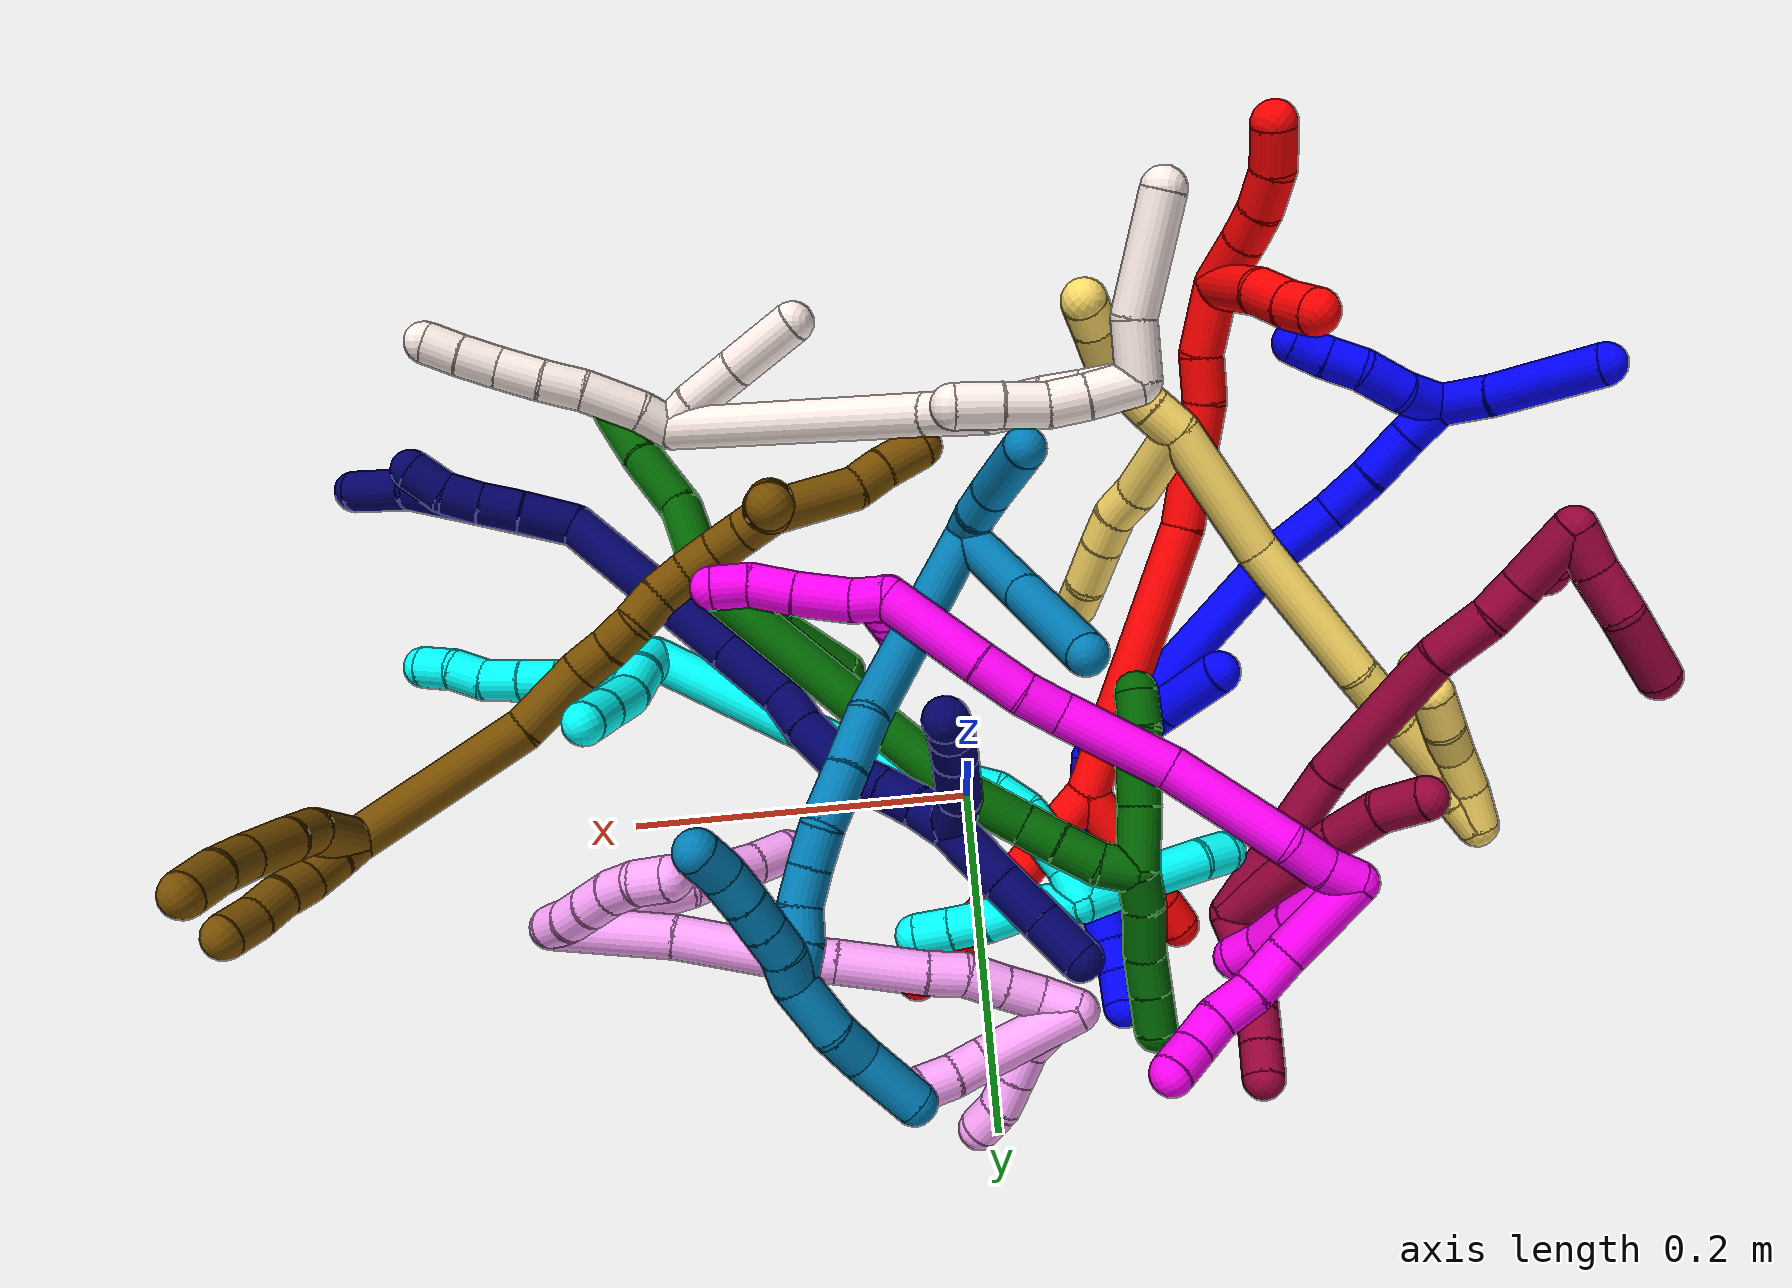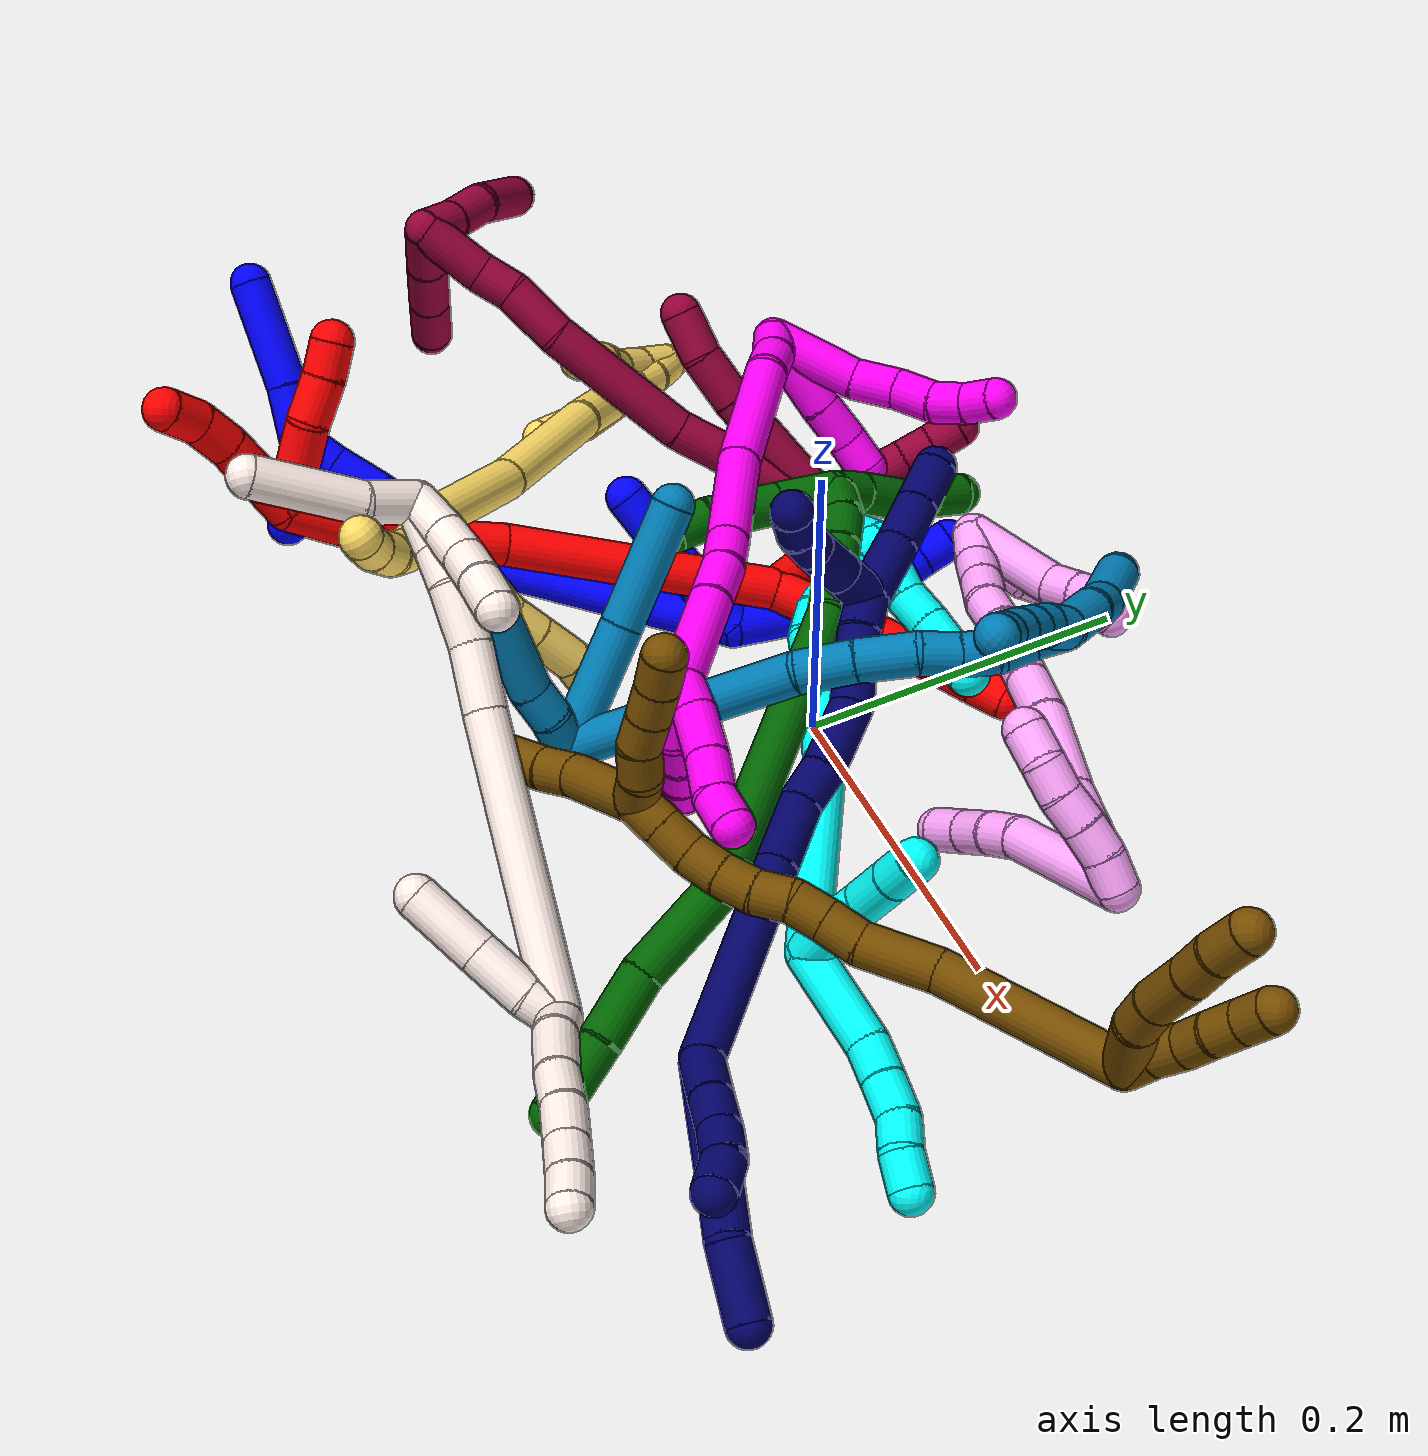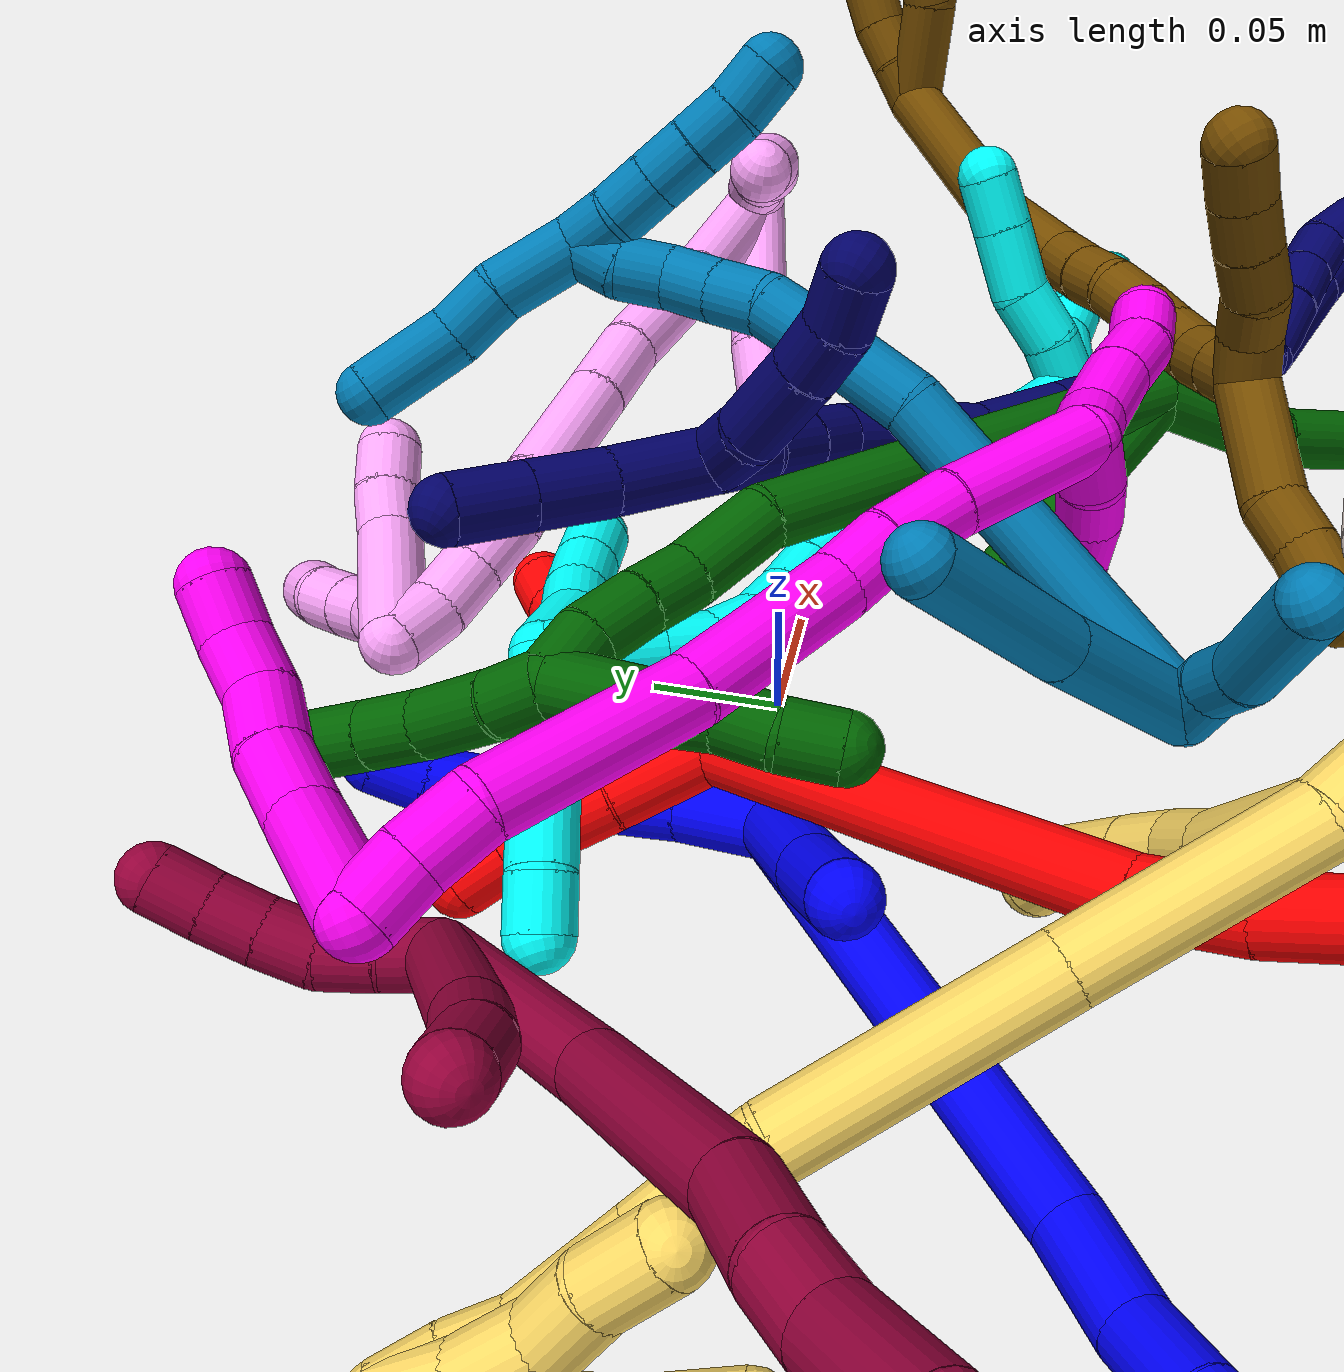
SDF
<sdf version="1.7">
 <world name="default">
  <plugin name="TubeGeneratorPlugin" filename="libtube_generator_plugin.so"/>
  <model name="photoneo_s_sensor">
   <static>1</static>
   <pose>0 0 2 1.57079 1.57079 3.14159</pose>
   <link name="link">
    <inertial><mass>0.1</mass></inertial>
    <sensor name="sensor" type="depth">
     <update_rate>30</update_rate>
     <camera>
      <horizontal_fov>1.22</horizontal_fov>
      <image><width>1920</width><height>1200</height><format>B8G8R8</format></image>
      <clip><near>0.1</near><far>4</far></clip>
      <depth_camera><output>points</output></depth_camera>
     </camera>
     <plugin name="camera_plugin" filename="libgazebo_ros_depth_camera.so">
      <baseline>0.2</baseline>
      <alwaysOn>1</alwaysOn>
      <updateRate>0.0</updateRate>
      <cameraName>camera_ir</cameraName>
      <imageTopicName>/camera/color/image_raw</imageTopicName>
      <cameraInfoTopicName>/camera/color/camera_info</cameraInfoTopicName>
      <depthImageTopicName>/camera/depth/image_raw</depthImageTopicName>
      <depthImageCameraInfoTopicName>/camera/depth/camera_info</depthImageCameraInfoTopicName>
      <pointCloudTopicName>/camera/depth/points</pointCloudTopicName>
      <frameName>fr_optical</frameName>
      <pointCloudCutoff>0.1</pointCloudCutoff>
      <pointCloudCutoffMax>2.0</pointCloudCutoffMax>
      <distortionK1>0</distortionK1>
      <distortionK2>0</distortionK2>
      <distortionK3>0</distortionK3>
      <distortionT1>0</distortionT1>
      <distortionT2>0</distortionT2>
      <CxPrime>0</CxPrime>
      <Cx>0</Cx>
      <Cy>0</Cy>
      <focalLength>0</focalLength>
      <hackBaseline>0</hackBaseline>
     </plugin>
    </sensor>
   </link>
  </model>
  <gravity>0 0 -9.8</gravity>
  <magnetic_field>6e-06 2.3e-05 -4.2e-05</magnetic_field>
  <atmosphere type="adiabatic"/>
  <physics name="default_physics" default="0" type="ode">
   <max_step_size>0.003</max_step_size>
   <real_time_factor>1</real_time_factor>
   <real_time_update_rate>1000</real_time_update_rate>
   <max_contacts>10000</max_contacts>
   <ode>
    <solver>
     <type>quick</type>
     <iters>100</iters>
     <sor>1.3</sor>
     <use_dynamic_moi_rescaling>0</use_dynamic_moi_rescaling>
    </solver>
    <constraints>
     <contact_max_correcting_vel>0</contact_max_correcting_vel>
     <contact_surface_layer>0.001</contact_surface_layer>
     <cfm>0</cfm>
     <erp>0.2</erp>
    </constraints>
   </ode>
  </physics>
  <scene><ambient>0.4 0.4 0.4 1</ambient><background>0.7 0.7 0.7 1</background><shadows>0</shadows></scene>
  <audio><device>default</device></audio>
  <spherical_coordinates>
   <surface_model>EARTH_WGS84</surface_model>
   <latitude_deg>0</latitude_deg>
   <longitude_deg>0</longitude_deg>
   <elevation>0</elevation>
   <heading_deg>0</heading_deg>
  </spherical_coordinates>
  <model name="bin">
   <static>1</static>
   <link name="bottom">
    <collision name="collision-bottom">
     <pose>0 0 -0.01 0 -0 0</pose>
     <geometry><box><size>0.8 0.6 0.02</size></box></geometry>
     <surface>
      <friction><ode><mu>100</mu><mu2>100</mu2></ode></friction>
      <contact><collide_bitmask>65535</collide_bitmask></contact>
     </surface>
    </collision>
   </link>
   <link name="west_wall">
    <collision name="collision-west_wall">
     <pose>-0.41 0 0.1 0 -0 0</pose>
     <geometry><box><size>0.02 0.6 0.2</size></box></geometry>
     <surface>
      <friction><ode><mu>100</mu><mu2>100</mu2></ode></friction>
      <contact><collide_bitmask>65535</collide_bitmask></contact>
     </surface>
    </collision>
   </link>
   <link name="east_wall">
    <collision name="collision-east_wall">
     <pose>0.41 0 0.1 0 -0 0</pose>
     <geometry><box><size>0.02 0.6 0.2</size></box></geometry>
     <surface>
      <friction><ode><mu>100</mu><mu2>100</mu2></ode></friction>
      <contact><collide_bitmask>65535</collide_bitmask></contact>
     </surface>
    </collision>
   </link>
   <link name="south_wall">
    <collision name="collision-south_wall">
     <pose>0 -0.31 0.1 0 -0 0</pose>
     <geometry><box><size>0.8 0.02 0.2</size></box></geometry>
     <surface>
      <friction><ode><mu>100</mu><mu2>100</mu2></ode></friction>
      <contact><collide_bitmask>65535</collide_bitmask></contact>
     </surface>
    </collision>
   </link>
   <link name="north_wall">
    <collision name="collision-north_wall">
     <pose>0 0.31 0.1 0 -0 0</pose>
     <geometry><box><size>0.8 0.02 0.2</size></box></geometry>
     <surface>
      <friction><ode><mu>100</mu><mu2>100</mu2></ode></friction>
      <contact><collide_bitmask>65535</collide_bitmask></contact>
     </surface>
    </collision>
   </link>
  </model>
  <model name="1">
   <static>0</static>
   <link name="1">
    <collision name="collision-cylinder-e_1_2_8">
     <pose>0.005035 0.013945 -0.008528 -2.11965 0.298806 -0.52461</pose>
     <geometry><cylinder><radius>0.0125</radius><length>0.034207</length></cylinder></geometry>
     <surface>
      <friction><ode><mu>1.16</mu><mu2>1.16</mu2><slip1>0</slip1><slip2>0</slip2></ode></friction>
      <contact><ode><kp>1e+06</kp><kd>1</kd><max_vel>0</max_vel><min_depth>0.001</min_depth></ode></contact>
     </surface>
    </collision>
    <visual name="visual-cylinder-e_1_2_8">
     <pose>0.005035 0.013945 -0.008528 -2.11965 0.298806 -0.52461</pose>
     <geometry><cylinder><radius>0.0125</radius><length>0.034207</length></cylinder></geometry>
     <material><ambient>0 0 1 1</ambient></material>
    </visual>
    <collision name="collision-cylinder-e_2_8_9">
     <pose>0.01379 0.042789 -0.025749 -2.09896 0.212399 -0.367051</pose>
     <geometry><cylinder><radius>0.0125</radius><length>0.035293</length></cylinder></geometry>
     <surface>
      <friction><ode><mu>1.16</mu><mu2>1.16</mu2><slip1>0</slip1><slip2>0</slip2></ode></friction>
      <contact><ode><kp>1e+06</kp><kd>1</kd><max_vel>0</max_vel><min_depth>0.001</min_depth></ode></contact>
     </surface>
    </collision>
    <visual name="visual-cylinder-e_2_8_9">
     <pose>0.01379 0.042789 -0.025749 -2.09896 0.212399 -0.367051</pose>
     <geometry><cylinder><radius>0.0125</radius><length>0.035293</length></cylinder></geometry>
     <material><ambient>0 0 1 1</ambient></material>
    </visual>
    <collision name="collision-cylinder-e_3_9_10">
     <pose>0.020378 0.067071 -0.036679 -1.80493 0.28905 -0.364575</pose>
     <geometry><cylinder><radius>0.0125</radius><length>0.020127</length></cylinder></geometry>
     <surface>
      <friction><ode><mu>1.16</mu><mu2>1.16</mu2><slip1>0</slip1><slip2>0</slip2></ode></friction>
      <contact><ode><kp>1e+06</kp><kd>1</kd><max_vel>0</max_vel><min_depth>0.001</min_depth></ode></contact>
     </surface>
    </collision>
    <visual name="visual-cylinder-e_3_9_10">
     <pose>0.020378 0.067071 -0.036679 -1.80493 0.28905 -0.364575</pose>
     <geometry><cylinder><radius>0.0125</radius><length>0.020127</length></cylinder></geometry>
     <material><ambient>0 0 1 1</ambient></material>
    </visual>
    <collision name="collision-cylinder-e_4_10_11">
     <pose>0.026603 0.085694 -0.040949 -1.7872 0.340872 -0.42174</pose>
     <geometry><cylinder><radius>0.0125</radius><length>0.020077</length></cylinder></geometry>
     <surface>
      <friction><ode><mu>1.16</mu><mu2>1.16</mu2><slip1>0</slip1><slip2>0</slip2></ode></friction>
      <contact><ode><kp>1e+06</kp><kd>1</kd><max_vel>0</max_vel><min_depth>0.001</min_depth></ode></contact>
     </surface>
    </collision>
    <visual name="visual-cylinder-e_4_10_11">
     <pose>0.026603 0.085694 -0.040949 -1.7872 0.340872 -0.42174</pose>
     <geometry><cylinder><radius>0.0125</radius><length>0.020077</length></cylinder></geometry>
     <material><ambient>0 0 1 1</ambient></material>
    </visual>
    <collision name="collision-cylinder-e_5_11_12">
     <pose>0.034408 0.103882 -0.044257 -1.71251 0.457462 -0.524396</pose>
     <geometry><cylinder><radius>0.0125</radius><length>0.020147</length></cylinder></geometry>
     <surface>
      <friction><ode><mu>1.16</mu><mu2>1.16</mu2><slip1>0</slip1><slip2>0</slip2></ode></friction>
      <contact><ode><kp>1e+06</kp><kd>1</kd><max_vel>0</max_vel><min_depth>0.001</min_depth></ode></contact>
     </surface>
    </collision>
    <visual name="visual-cylinder-e_5_11_12">
     <pose>0.034408 0.103882 -0.044257 -1.71251 0.457462 -0.524396</pose>
     <geometry><cylinder><radius>0.0125</radius><length>0.020147</length></cylinder></geometry>
     <material><ambient>0 0 1 1</ambient></material>
    </visual>
    <collision name="collision-cylinder-e_6_12_6">
     <pose>0.044867 0.120723 -0.047285 -1.7892 0.639126 -0.782295</pose>
     <geometry><cylinder><radius>0.0125</radius><length>0.020149</length></cylinder></geometry>
     <surface>
      <friction><ode><mu>1.16</mu><mu2>1.16</mu2><slip1>0</slip1><slip2>0</slip2></ode></friction>
      <contact><ode><kp>1e+06</kp><kd>1</kd><max_vel>0</max_vel><min_depth>0.001</min_depth></ode></contact>
     </surface>
    </collision>
    <visual name="visual-cylinder-e_6_12_6">
     <pose>0.044867 0.120723 -0.047285 -1.7892 0.639126 -0.782295</pose>
     <geometry><cylinder><radius>0.0125</radius><length>0.020149</length></cylinder></geometry>
     <material><ambient>0 0 1 1</ambient></material>
    </visual>
    <collision name="collision-cylinder-e_1_2_13">
     <pose>0.003406 -0.001241 0.029401 0.042201 0.115247 0.002435</pose>
     <geometry><cylinder><radius>0.0125</radius><length>0.059247</length></cylinder></geometry>
     <surface>
      <friction><ode><mu>1.16</mu><mu2>1.16</mu2><slip1>0</slip1><slip2>0</slip2></ode></friction>
      <contact><ode><kp>1e+06</kp><kd>1</kd><max_vel>0</max_vel><min_depth>0.001</min_depth></ode></contact>
     </surface>
    </collision>
    <visual name="visual-cylinder-e_1_2_13">
     <pose>0.003406 -0.001241 0.029401 0.042201 0.115247 0.002435</pose>
     <geometry><cylinder><radius>0.0125</radius><length>0.059247</length></cylinder></geometry>
     <material><ambient>0 0 1 1</ambient></material>
    </visual>
    <collision name="collision-cylinder-e_2_13_5">
     <pose>0.010595 -0.003451 0.078801 0.048366 0.186694 0.004529</pose>
     <geometry><cylinder><radius>0.0125</radius><length>0.040753</length></cylinder></geometry>
     <surface>
      <friction><ode><mu>1.16</mu><mu2>1.16</mu2><slip1>0</slip1><slip2>0</slip2></ode></friction>
      <contact><ode><kp>1e+06</kp><kd>1</kd><max_vel>0</max_vel><min_depth>0.001</min_depth></ode></contact>
     </surface>
    </collision>
    <visual name="visual-cylinder-e_2_13_5">
     <pose>0.010595 -0.003451 0.078801 0.048366 0.186694 0.004529</pose>
     <geometry><cylinder><radius>0.0125</radius><length>0.040753</length></cylinder></geometry>
     <material><ambient>0 0 1 1</ambient></material>
    </visual>
    <collision name="collision-cylinder-e_1_2_14">
     <pose>-0.044585 -0.019685 0.069784 0.274938 -0.551303 -0.07822</pose>
     <geometry><cylinder><radius>0.0125</radius><length>0.170236</length></cylinder></geometry>
     <surface>
      <friction><ode><mu>1.16</mu><mu2>1.16</mu2><slip1>0</slip1><slip2>0</slip2></ode></friction>
      <contact><ode><kp>1e+06</kp><kd>1</kd><max_vel>0</max_vel><min_depth>0.001</min_depth></ode></contact>
     </surface>
    </collision>
    <visual name="visual-cylinder-e_1_2_14">
     <pose>-0.044585 -0.019685 0.069784 0.274938 -0.551303 -0.07822</pose>
     <geometry><cylinder><radius>0.0125</radius><length>0.170236</length></cylinder></geometry>
     <material><ambient>0 0 1 1</ambient></material>
    </visual>
    <collision name="collision-cylinder-e_2_14_15">
     <pose>-0.094488 -0.040965 0.158944 0.082142 -0.267032 -0.011039</pose>
     <geometry><cylinder><radius>0.0125</radius><length>0.040311</length></cylinder></geometry>
     <surface>
      <friction><ode><mu>1.16</mu><mu2>1.16</mu2><slip1>0</slip1><slip2>0</slip2></ode></friction>
      <contact><ode><kp>1e+06</kp><kd>1</kd><max_vel>0</max_vel><min_depth>0.001</min_depth></ode></contact>
     </surface>
    </collision>
    <visual name="visual-cylinder-e_2_14_15">
     <pose>-0.094488 -0.040965 0.158944 0.082142 -0.267032 -0.011039</pose>
     <geometry><cylinder><radius>0.0125</radius><length>0.040311</length></cylinder></geometry>
     <material><ambient>0 0 1 1</ambient></material>
    </visual>
    <collision name="collision-cylinder-e_3_15_16">
     <pose>-0.100468 -0.045058 0.193946 0.15854 -0.04179 -0.00332</pose>
     <geometry><cylinder><radius>0.0125</radius><length>0.031679</length></cylinder></geometry>
     <surface>
      <friction><ode><mu>1.16</mu><mu2>1.16</mu2><slip1>0</slip1><slip2>0</slip2></ode></friction>
      <contact><ode><kp>1e+06</kp><kd>1</kd><max_vel>0</max_vel><min_depth>0.001</min_depth></ode></contact>
     </surface>
    </collision>
    <visual name="visual-cylinder-e_3_15_16">
     <pose>-0.100468 -0.045058 0.193946 0.15854 -0.04179 -0.00332</pose>
     <geometry><cylinder><radius>0.0125</radius><length>0.031679</length></cylinder></geometry>
     <material><ambient>0 0 1 1</ambient></material>
    </visual>
    <collision name="collision-cylinder-e_4_16_17">
     <pose>-0.103178 -0.051388 0.224849 0.245743 -0.129375 -0.015999</pose>
     <geometry><cylinder><radius>0.0125</radius><length>0.031763</length></cylinder></geometry>
     <surface>
      <friction><ode><mu>1.16</mu><mu2>1.16</mu2><slip1>0</slip1><slip2>0</slip2></ode></friction>
      <contact><ode><kp>1e+06</kp><kd>1</kd><max_vel>0</max_vel><min_depth>0.001</min_depth></ode></contact>
     </surface>
    </collision>
    <visual name="visual-cylinder-e_4_16_17">
     <pose>-0.103178 -0.051388 0.224849 0.245743 -0.129375 -0.015999</pose>
     <geometry><cylinder><radius>0.0125</radius><length>0.031763</length></cylinder></geometry>
     <material><ambient>0 0 1 1</ambient></material>
    </visual>
    <collision name="collision-cylinder-e_5_17_1">
     <pose>-0.106112 -0.057825 0.252836 0.202208 -0.06805 -0.006906</pose>
     <geometry><cylinder><radius>0.0125</radius><length>0.026011</length></cylinder></geometry>
     <surface>
      <friction><ode><mu>1.16</mu><mu2>1.16</mu2><slip1>0</slip1><slip2>0</slip2></ode></friction>
      <contact><ode><kp>1e+06</kp><kd>1</kd><max_vel>0</max_vel><min_depth>0.001</min_depth></ode></contact>
     </surface>
    </collision>
    <visual name="visual-cylinder-e_5_17_1">
     <pose>-0.106112 -0.057825 0.252836 0.202208 -0.06805 -0.006906</pose>
     <geometry><cylinder><radius>0.0125</radius><length>0.026011</length></cylinder></geometry>
     <material><ambient>0 0 1 1</ambient></material>
    </visual>
    <collision name="collision-cylinder-e_1_1_18">
     <pose>-0.09799 -0.069579 0.26013 2.1054 0.702824 1.14311</pose>
     <geometry><cylinder><radius>0.0125</radius><length>0.027865</length></cylinder></geometry>
     <surface>
      <friction><ode><mu>1.16</mu><mu2>1.16</mu2><slip1>0</slip1><slip2>0</slip2></ode></friction>
      <contact><ode><kp>1e+06</kp><kd>1</kd><max_vel>0</max_vel><min_depth>0.001</min_depth></ode></contact>
     </surface>
    </collision>
    <visual name="visual-cylinder-e_1_1_18">
     <pose>-0.09799 -0.069579 0.26013 2.1054 0.702824 1.14311</pose>
     <geometry><cylinder><radius>0.0125</radius><length>0.027865</length></cylinder></geometry>
     <material><ambient>0 0 1 1</ambient></material>
    </visual>
    <collision name="collision-cylinder-e_2_18_19">
     <pose>-0.082494 -0.090918 0.249471 1.97695 0.454897 0.676004</pose>
     <geometry><cylinder><radius>0.0125</radius><length>0.029547</length></cylinder></geometry>
     <surface>
      <friction><ode><mu>1.16</mu><mu2>1.16</mu2><slip1>0</slip1><slip2>0</slip2></ode></friction>
      <contact><ode><kp>1e+06</kp><kd>1</kd><max_vel>0</max_vel><min_depth>0.001</min_depth></ode></contact>
     </surface>
    </collision>
    <visual name="visual-cylinder-e_2_18_19">
     <pose>-0.082494 -0.090918 0.249471 1.97695 0.454897 0.676004</pose>
     <geometry><cylinder><radius>0.0125</radius><length>0.029547</length></cylinder></geometry>
     <material><ambient>0 0 1 1</ambient></material>
    </visual>
    <collision name="collision-cylinder-e_3_19_20">
     <pose>-0.073813 -0.11182 0.237991 2.19216 0.201604 0.388656</pose>
     <geometry><cylinder><radius>0.0125</radius><length>0.021869</length></cylinder></geometry>
     <surface>
      <friction><ode><mu>1.16</mu><mu2>1.16</mu2><slip1>0</slip1><slip2>0</slip2></ode></friction>
      <contact><ode><kp>1e+06</kp><kd>1</kd><max_vel>0</max_vel><min_depth>0.001</min_depth></ode></contact>
     </surface>
    </collision>
    <visual name="visual-cylinder-e_3_19_20">
     <pose>-0.073813 -0.11182 0.237991 2.19216 0.201604 0.388656</pose>
     <geometry><cylinder><radius>0.0125</radius><length>0.021869</length></cylinder></geometry>
     <material><ambient>0 0 1 1</ambient></material>
    </visual>
    <collision name="collision-cylinder-e_4_20_4">
     <pose>-0.069944 -0.129398 0.22667 2.09145 0.162841 0.279874</pose>
     <geometry><cylinder><radius>0.0125</radius><length>0.020719</length></cylinder></geometry>
     <surface>
      <friction><ode><mu>1.16</mu><mu2>1.16</mu2><slip1>0</slip1><slip2>0</slip2></ode></friction>
      <contact><ode><kp>1e+06</kp><kd>1</kd><max_vel>0</max_vel><min_depth>0.001</min_depth></ode></contact>
     </surface>
    </collision>
    <visual name="visual-cylinder-e_4_20_4">
     <pose>-0.069944 -0.129398 0.22667 2.09145 0.162841 0.279874</pose>
     <geometry><cylinder><radius>0.0125</radius><length>0.020719</length></cylinder></geometry>
     <material><ambient>0 0 1 1</ambient></material>
    </visual>
    <collision name="collision-cylinder-e_1_1_21">
     <pose>-0.100843 -0.054472 0.280087 -0.388943 0.373235 -0.074344</pose>
     <geometry><cylinder><radius>0.0125</radius><length>0.033751</length></cylinder></geometry>
     <surface>
      <friction><ode><mu>1.16</mu><mu2>1.16</mu2><slip1>0</slip1><slip2>0</slip2></ode></friction>
      <contact><ode><kp>1e+06</kp><kd>1</kd><max_vel>0</max_vel><min_depth>0.001</min_depth></ode></contact>
     </surface>
    </collision>
    <visual name="visual-cylinder-e_1_1_21">
     <pose>-0.100843 -0.054472 0.280087 -0.388943 0.373235 -0.074344</pose>
     <geometry><cylinder><radius>0.0125</radius><length>0.033751</length></cylinder></geometry>
     <material><ambient>0 0 1 1</ambient></material>
    </visual>
    <collision name="collision-cylinder-e_2_21_3">
     <pose>-0.085605 -0.03892 0.325002 -0.305916 0.277812 -0.043099</pose>
     <geometry><cylinder><radius>0.0125</radius><length>0.066249</length></cylinder></geometry>
     <surface>
      <friction><ode><mu>1.16</mu><mu2>1.16</mu2><slip1>0</slip1><slip2>0</slip2></ode></friction>
      <contact><ode><kp>1e+06</kp><kd>1</kd><max_vel>0</max_vel><min_depth>0.001</min_depth></ode></contact>
     </surface>
    </collision>
    <visual name="visual-cylinder-e_2_21_3">
     <pose>-0.085605 -0.03892 0.325002 -0.305916 0.277812 -0.043099</pose>
     <geometry><cylinder><radius>0.0125</radius><length>0.066249</length></cylinder></geometry>
     <material><ambient>0 0 1 1</ambient></material>
    </visual>
    <collision name="collision-sphere-3">
     <pose>-0.076521 -0.029327 0.355378 0 -0 0</pose>
     <geometry><sphere><radius>0.0125</radius></sphere></geometry>
     <surface>
      <friction><ode><mu>1.16</mu><mu2>1.16</mu2><slip1>0</slip1><slip2>0</slip2></ode></friction>
      <contact><ode><kp>1e+06</kp><kd>1</kd><max_vel>0</max_vel><min_depth>0.001</min_depth></ode></contact>
     </surface>
    </collision>
    <visual name="visual-sphere-3">
     <pose>-0.076521 -0.029327 0.355378 0 -0 0</pose>
     <geometry><sphere><radius>0.0125</radius></sphere></geometry>
     <material><ambient>0 0 1 1</ambient></material>
    </visual>
    <collision name="collision-sphere-21">
     <pose>-0.09469 -0.048514 0.294627 0 -0 0</pose>
     <geometry><sphere><radius>0.0125</radius></sphere></geometry>
     <surface>
      <friction><ode><mu>1.16</mu><mu2>1.16</mu2><slip1>0</slip1><slip2>0</slip2></ode></friction>
      <contact><ode><kp>1e+06</kp><kd>1</kd><max_vel>0</max_vel><min_depth>0.001</min_depth></ode></contact>
     </surface>
    </collision>
    <visual name="visual-sphere-21">
     <pose>-0.09469 -0.048514 0.294627 0 -0 0</pose>
     <geometry><sphere><radius>0.0125</radius></sphere></geometry>
     <material><ambient>0 0 1 1</ambient></material>
    </visual>
    <collision name="collision-sphere-4">
     <pose>-0.068265 -0.138266 0.221585 0 -0 0</pose>
     <geometry><sphere><radius>0.0125</radius></sphere></geometry>
     <surface>
      <friction><ode><mu>1.16</mu><mu2>1.16</mu2><slip1>0</slip1><slip2>0</slip2></ode></friction>
      <contact><ode><kp>1e+06</kp><kd>1</kd><max_vel>0</max_vel><min_depth>0.001</min_depth></ode></contact>
     </surface>
    </collision>
    <visual name="visual-sphere-4">
     <pose>-0.068265 -0.138266 0.221585 0 -0 0</pose>
     <geometry><sphere><radius>0.0125</radius></sphere></geometry>
     <material><ambient>0 0 1 1</ambient></material>
    </visual>
    <collision name="collision-sphere-20">
     <pose>-0.071624 -0.12053 0.231755 0 -0 0</pose>
     <geometry><sphere><radius>0.0125</radius></sphere></geometry>
     <surface>
      <friction><ode><mu>1.16</mu><mu2>1.16</mu2><slip1>0</slip1><slip2>0</slip2></ode></friction>
      <contact><ode><kp>1e+06</kp><kd>1</kd><max_vel>0</max_vel><min_depth>0.001</min_depth></ode></contact>
     </surface>
    </collision>
    <visual name="visual-sphere-20">
     <pose>-0.071624 -0.12053 0.231755 0 -0 0</pose>
     <geometry><sphere><radius>0.0125</radius></sphere></geometry>
     <material><ambient>0 0 1 1</ambient></material>
    </visual>
    <collision name="collision-sphere-12">
     <pose>0.038857 0.112829 -0.045533 0 -0 0</pose>
     <geometry><sphere><radius>0.0125</radius></sphere></geometry>
     <surface>
      <friction><ode><mu>1.16</mu><mu2>1.16</mu2><slip1>0</slip1><slip2>0</slip2></ode></friction>
      <contact><ode><kp>1e+06</kp><kd>1</kd><max_vel>0</max_vel><min_depth>0.001</min_depth></ode></contact>
     </surface>
    </collision>
    <visual name="visual-sphere-12">
     <pose>0.038857 0.112829 -0.045533 0 -0 0</pose>
     <geometry><sphere><radius>0.0125</radius></sphere></geometry>
     <material><ambient>0 0 1 1</ambient></material>
    </visual>
    <collision name="collision-sphere-11">
     <pose>0.029959 0.094935 -0.04298 0 -0 0</pose>
     <geometry><sphere><radius>0.0125</radius></sphere></geometry>
     <surface>
      <friction><ode><mu>1.16</mu><mu2>1.16</mu2><slip1>0</slip1><slip2>0</slip2></ode></friction>
      <contact><ode><kp>1e+06</kp><kd>1</kd><max_vel>0</max_vel><min_depth>0.001</min_depth></ode></contact>
     </surface>
    </collision>
    <visual name="visual-sphere-11">
     <pose>0.029959 0.094935 -0.04298 0 -0 0</pose>
     <geometry><sphere><radius>0.0125</radius></sphere></geometry>
     <material><ambient>0 0 1 1</ambient></material>
    </visual>
    <collision name="collision-sphere-10">
     <pose>0.023247 0.076454 -0.038917 0 -0 0</pose>
     <geometry><sphere><radius>0.0125</radius></sphere></geometry>
     <surface>
      <friction><ode><mu>1.16</mu><mu2>1.16</mu2><slip1>0</slip1><slip2>0</slip2></ode></friction>
      <contact><ode><kp>1e+06</kp><kd>1</kd><max_vel>0</max_vel><min_depth>0.001</min_depth></ode></contact>
     </surface>
    </collision>
    <visual name="visual-sphere-10">
     <pose>0.023247 0.076454 -0.038917 0 -0 0</pose>
     <geometry><sphere><radius>0.0125</radius></sphere></geometry>
     <material><ambient>0 0 1 1</ambient></material>
    </visual>
    <collision name="collision-sphere-9">
     <pose>0.01751 0.057688 -0.034442 0 -0 0</pose>
     <geometry><sphere><radius>0.0125</radius></sphere></geometry>
     <surface>
      <friction><ode><mu>1.16</mu><mu2>1.16</mu2><slip1>0</slip1><slip2>0</slip2></ode></friction>
      <contact><ode><kp>1e+06</kp><kd>1</kd><max_vel>0</max_vel><min_depth>0.001</min_depth></ode></contact>
     </surface>
    </collision>
    <visual name="visual-sphere-9">
     <pose>0.01751 0.057688 -0.034442 0 -0 0</pose>
     <geometry><sphere><radius>0.0125</radius></sphere></geometry>
     <material><ambient>0 0 1 1</ambient></material>
    </visual>
    <collision name="collision-sphere-2">
     <geometry><sphere><radius>0.0125</radius></sphere></geometry>
     <surface>
      <friction><ode><mu>1.16</mu><mu2>1.16</mu2><slip1>0</slip1><slip2>0</slip2></ode></friction>
      <contact><ode><kp>1e+06</kp><kd>1</kd><max_vel>0</max_vel><min_depth>0.001</min_depth></ode></contact>
     </surface>
    </collision>
    <visual name="visual-sphere-2">
     <geometry><sphere><radius>0.0125</radius></sphere></geometry>
     <material><ambient>0 0 1 1</ambient></material>
    </visual>
    <collision name="collision-sphere-19">
     <pose>-0.076003 -0.103109 0.244228 0 -0 0</pose>
     <geometry><sphere><radius>0.0125</radius></sphere></geometry>
     <surface>
      <friction><ode><mu>1.16</mu><mu2>1.16</mu2><slip1>0</slip1><slip2>0</slip2></ode></friction>
      <contact><ode><kp>1e+06</kp><kd>1</kd><max_vel>0</max_vel><min_depth>0.001</min_depth></ode></contact>
     </surface>
    </collision>
    <visual name="visual-sphere-19">
     <pose>-0.076003 -0.103109 0.244228 0 -0 0</pose>
     <geometry><sphere><radius>0.0125</radius></sphere></geometry>
     <material><ambient>0 0 1 1</ambient></material>
    </visual>
    <collision name="collision-sphere-8">
     <pose>0.01007 0.02789 -0.017056 0 -0 0</pose>
     <geometry><sphere><radius>0.0125</radius></sphere></geometry>
     <surface>
      <friction><ode><mu>1.16</mu><mu2>1.16</mu2><slip1>0</slip1><slip2>0</slip2></ode></friction>
      <contact><ode><kp>1e+06</kp><kd>1</kd><max_vel>0</max_vel><min_depth>0.001</min_depth></ode></contact>
     </surface>
    </collision>
    <visual name="visual-sphere-8">
     <pose>0.01007 0.02789 -0.017056 0 -0 0</pose>
     <geometry><sphere><radius>0.0125</radius></sphere></geometry>
     <material><ambient>0 0 1 1</ambient></material>
    </visual>
    <collision name="collision-sphere-6">
     <pose>0.050876 0.128617 -0.049037 0 -0 0</pose>
     <geometry><sphere><radius>0.0125</radius></sphere></geometry>
     <surface>
      <friction><ode><mu>1.16</mu><mu2>1.16</mu2><slip1>0</slip1><slip2>0</slip2></ode></friction>
      <contact><ode><kp>1e+06</kp><kd>1</kd><max_vel>0</max_vel><min_depth>0.001</min_depth></ode></contact>
     </surface>
    </collision>
    <visual name="visual-sphere-6">
     <pose>0.050876 0.128617 -0.049037 0 -0 0</pose>
     <geometry><sphere><radius>0.0125</radius></sphere></geometry>
     <material><ambient>0 0 1 1</ambient></material>
    </visual>
    <collision name="collision-sphere-13">
     <pose>0.006813 -0.002483 0.058802 0 -0 0</pose>
     <geometry><sphere><radius>0.0125</radius></sphere></geometry>
     <surface>
      <friction><ode><mu>1.16</mu><mu2>1.16</mu2><slip1>0</slip1><slip2>0</slip2></ode></friction>
      <contact><ode><kp>1e+06</kp><kd>1</kd><max_vel>0</max_vel><min_depth>0.001</min_depth></ode></contact>
     </surface>
    </collision>
    <visual name="visual-sphere-13">
     <pose>0.006813 -0.002483 0.058802 0 -0 0</pose>
     <geometry><sphere><radius>0.0125</radius></sphere></geometry>
     <material><ambient>0 0 1 1</ambient></material>
    </visual>
    <collision name="collision-sphere-5">
     <pose>0.014377 -0.004419 0.0988 0 -0 0</pose>
     <geometry><sphere><radius>0.0125</radius></sphere></geometry>
     <surface>
      <friction><ode><mu>1.16</mu><mu2>1.16</mu2><slip1>0</slip1><slip2>0</slip2></ode></friction>
      <contact><ode><kp>1e+06</kp><kd>1</kd><max_vel>0</max_vel><min_depth>0.001</min_depth></ode></contact>
     </surface>
    </collision>
    <visual name="visual-sphere-5">
     <pose>0.014377 -0.004419 0.0988 0 -0 0</pose>
     <geometry><sphere><radius>0.0125</radius></sphere></geometry>
     <material><ambient>0 0 1 1</ambient></material>
    </visual>
    <collision name="collision-sphere-14">
     <pose>-0.089169 -0.03937 0.139568 0 -0 0</pose>
     <geometry><sphere><radius>0.0125</radius></sphere></geometry>
     <surface>
      <friction><ode><mu>1.16</mu><mu2>1.16</mu2><slip1>0</slip1><slip2>0</slip2></ode></friction>
      <contact><ode><kp>1e+06</kp><kd>1</kd><max_vel>0</max_vel><min_depth>0.001</min_depth></ode></contact>
     </surface>
    </collision>
    <visual name="visual-sphere-14">
     <pose>-0.089169 -0.03937 0.139568 0 -0 0</pose>
     <geometry><sphere><radius>0.0125</radius></sphere></geometry>
     <material><ambient>0 0 1 1</ambient></material>
    </visual>
    <collision name="collision-sphere-15">
     <pose>-0.099806 -0.04256 0.178319 0 -0 0</pose>
     <geometry><sphere><radius>0.0125</radius></sphere></geometry>
     <surface>
      <friction><ode><mu>1.16</mu><mu2>1.16</mu2><slip1>0</slip1><slip2>0</slip2></ode></friction>
      <contact><ode><kp>1e+06</kp><kd>1</kd><max_vel>0</max_vel><min_depth>0.001</min_depth></ode></contact>
     </surface>
    </collision>
    <visual name="visual-sphere-15">
     <pose>-0.099806 -0.04256 0.178319 0 -0 0</pose>
     <geometry><sphere><radius>0.0125</radius></sphere></geometry>
     <material><ambient>0 0 1 1</ambient></material>
    </visual>
    <collision name="collision-sphere-16">
     <pose>-0.10113 -0.047557 0.209574 0 -0 0</pose>
     <geometry><sphere><radius>0.0125</radius></sphere></geometry>
     <surface>
      <friction><ode><mu>1.16</mu><mu2>1.16</mu2><slip1>0</slip1><slip2>0</slip2></ode></friction>
      <contact><ode><kp>1e+06</kp><kd>1</kd><max_vel>0</max_vel><min_depth>0.001</min_depth></ode></contact>
     </surface>
    </collision>
    <visual name="visual-sphere-16">
     <pose>-0.10113 -0.047557 0.209574 0 -0 0</pose>
     <geometry><sphere><radius>0.0125</radius></sphere></geometry>
     <material><ambient>0 0 1 1</ambient></material>
    </visual>
    <collision name="collision-sphere-17">
     <pose>-0.105227 -0.05522 0.240125 0 -0 0</pose>
     <geometry><sphere><radius>0.0125</radius></sphere></geometry>
     <surface>
      <friction><ode><mu>1.16</mu><mu2>1.16</mu2><slip1>0</slip1><slip2>0</slip2></ode></friction>
      <contact><ode><kp>1e+06</kp><kd>1</kd><max_vel>0</max_vel><min_depth>0.001</min_depth></ode></contact>
     </surface>
    </collision>
    <visual name="visual-sphere-17">
     <pose>-0.105227 -0.05522 0.240125 0 -0 0</pose>
     <geometry><sphere><radius>0.0125</radius></sphere></geometry>
     <material><ambient>0 0 1 1</ambient></material>
    </visual>
    <collision name="collision-sphere-1">
     <pose>-0.106996 -0.060431 0.265547 0 -0 0</pose>
     <geometry><sphere><radius>0.0125</radius></sphere></geometry>
     <surface>
      <friction><ode><mu>1.16</mu><mu2>1.16</mu2><slip1>0</slip1><slip2>0</slip2></ode></friction>
      <contact><ode><kp>1e+06</kp><kd>1</kd><max_vel>0</max_vel><min_depth>0.001</min_depth></ode></contact>
     </surface>
    </collision>
    <visual name="visual-sphere-1">
     <pose>-0.106996 -0.060431 0.265547 0 -0 0</pose>
     <geometry><sphere><radius>0.0125</radius></sphere></geometry>
     <material><ambient>0 0 1 1</ambient></material>
    </visual>
    <collision name="collision-sphere-18">
     <pose>-0.088985 -0.078726 0.254714 0 -0 0</pose>
     <geometry><sphere><radius>0.0125</radius></sphere></geometry>
     <surface>
      <friction><ode><mu>1.16</mu><mu2>1.16</mu2><slip1>0</slip1><slip2>0</slip2></ode></friction>
      <contact><ode><kp>1e+06</kp><kd>1</kd><max_vel>0</max_vel><min_depth>0.001</min_depth></ode></contact>
     </surface>
    </collision>
    <visual name="visual-sphere-18">
     <pose>-0.088985 -0.078726 0.254714 0 -0 0</pose>
     <geometry><sphere><radius>0.0125</radius></sphere></geometry>
     <material><ambient>0 0 1 1</ambient></material>
    </visual>
    <inertial>
     <pose>-0.045455 -0.019154 0.125336 0 -0 0</pose>
     <mass>0.75</mass>
     <inertia>
      <ixx>0.000419</ixx>
      <ixy>0</ixy>
      <ixz>0</ixz>
      <iyy>0.000446</iyy>
      <iyz>0</iyz>
      <izz>0.000313</izz>
     </inertia>
    </inertial>
   </link>
   <pose>-0.076487 -0.013611 0.019444 -0.246875 -1.06232 0.714408</pose>
  </model>
  <model name="2">
   <static>0</static>
   <link name="2">
    <collision name="collision-cylinder-e_1_2_8">
     <pose>-0.001736 0.018967 -0.040351 -2.7022 -0.038905 0.173809</pose>
     <geometry><cylinder><radius>0.0125</radius><length>0.089241</length></cylinder></geometry>
     <surface>
      <friction><ode><mu>1.16</mu><mu2>1.16</mu2><slip1>0</slip1><slip2>0</slip2></ode></friction>
      <contact><ode><kp>1e+06</kp><kd>1</kd><max_vel>0</max_vel><min_depth>0.001</min_depth></ode></contact>
     </surface>
    </collision>
    <visual name="visual-cylinder-e_1_2_8">
     <pose>-0.001736 0.018967 -0.040351 -2.7022 -0.038905 0.173809</pose>
     <geometry><cylinder><radius>0.0125</radius><length>0.089241</length></cylinder></geometry>
     <material><ambient>1 0 0 1</ambient></material>
    </visual>
    <collision name="collision-cylinder-e_2_8_9">
     <pose>-0.003731 0.04265 -0.089627 -2.6554 -0.025726 0.103644</pose>
     <geometry><cylinder><radius>0.0125</radius><length>0.020193</length></cylinder></geometry>
     <surface>
      <friction><ode><mu>1.16</mu><mu2>1.16</mu2><slip1>0</slip1><slip2>0</slip2></ode></friction>
      <contact><ode><kp>1e+06</kp><kd>1</kd><max_vel>0</max_vel><min_depth>0.001</min_depth></ode></contact>
     </surface>
    </collision>
    <visual name="visual-cylinder-e_2_8_9">
     <pose>-0.003731 0.04265 -0.089627 -2.6554 -0.025726 0.103644</pose>
     <geometry><cylinder><radius>0.0125</radius><length>0.020193</length></cylinder></geometry>
     <material><ambient>1 0 0 1</ambient></material>
    </visual>
    <collision name="collision-cylinder-e_3_9_10">
     <pose>-0.005021 0.051937 -0.107435 -2.66649 -0.102755 0.418544</pose>
     <geometry><cylinder><radius>0.0125</radius><length>0.020088</length></cylinder></geometry>
     <surface>
      <friction><ode><mu>1.16</mu><mu2>1.16</mu2><slip1>0</slip1><slip2>0</slip2></ode></friction>
      <contact><ode><kp>1e+06</kp><kd>1</kd><max_vel>0</max_vel><min_depth>0.001</min_depth></ode></contact>
     </surface>
    </collision>
    <visual name="visual-cylinder-e_3_9_10">
     <pose>-0.005021 0.051937 -0.107435 -2.66649 -0.102755 0.418544</pose>
     <geometry><cylinder><radius>0.0125</radius><length>0.020088</length></cylinder></geometry>
     <material><ambient>1 0 0 1</ambient></material>
    </visual>
    <collision name="collision-cylinder-e_4_10_6">
     <pose>-0.00821 0.059724 -0.125796 -2.8143 -0.212488 1.14692</pose>
     <geometry><cylinder><radius>0.0125</radius><length>0.020477</length></cylinder></geometry>
     <surface>
      <friction><ode><mu>1.16</mu><mu2>1.16</mu2><slip1>0</slip1><slip2>0</slip2></ode></friction>
      <contact><ode><kp>1e+06</kp><kd>1</kd><max_vel>0</max_vel><min_depth>0.001</min_depth></ode></contact>
     </surface>
    </collision>
    <visual name="visual-cylinder-e_4_10_6">
     <pose>-0.00821 0.059724 -0.125796 -2.8143 -0.212488 1.14692</pose>
     <geometry><cylinder><radius>0.0125</radius><length>0.020477</length></cylinder></geometry>
     <material><ambient>1 0 0 1</ambient></material>
    </visual>
    <collision name="collision-cylinder-e_1_2_11">
     <pose>0.018408 0.004337 -0.004451 -2.36906 1.2452 -2.11067</pose>
     <geometry><cylinder><radius>0.0125</radius><length>0.038857</length></cylinder></geometry>
     <surface>
      <friction><ode><mu>1.16</mu><mu2>1.16</mu2><slip1>0</slip1><slip2>0</slip2></ode></friction>
      <contact><ode><kp>1e+06</kp><kd>1</kd><max_vel>0</max_vel><min_depth>0.001</min_depth></ode></contact>
     </surface>
    </collision>
    <visual name="visual-cylinder-e_1_2_11">
     <pose>0.018408 0.004337 -0.004451 -2.36906 1.2452 -2.11067</pose>
     <geometry><cylinder><radius>0.0125</radius><length>0.038857</length></cylinder></geometry>
     <material><ambient>1 0 0 1</ambient></material>
    </visual>
    <collision name="collision-cylinder-e_2_11_12">
     <pose>0.046286 0.011704 -0.011776 -2.33019 1.15551 -1.97648</pose>
     <geometry><cylinder><radius>0.0125</radius><length>0.020702</length></cylinder></geometry>
     <surface>
      <friction><ode><mu>1.16</mu><mu2>1.16</mu2><slip1>0</slip1><slip2>0</slip2></ode></friction>
      <contact><ode><kp>1e+06</kp><kd>1</kd><max_vel>0</max_vel><min_depth>0.001</min_depth></ode></contact>
     </surface>
    </collision>
    <visual name="visual-cylinder-e_2_11_12">
     <pose>0.046286 0.011704 -0.011776 -2.33019 1.15551 -1.97648</pose>
     <geometry><cylinder><radius>0.0125</radius><length>0.020702</length></cylinder></geometry>
     <material><ambient>1 0 0 1</ambient></material>
    </visual>
    <collision name="collision-cylinder-e_3_12_13">
     <pose>0.065027 0.018299 -0.016654 -2.08234 1.15525 -1.67797</pose>
     <geometry><cylinder><radius>0.0125</radius><length>0.020266</length></cylinder></geometry>
     <surface>
      <friction><ode><mu>1.16</mu><mu2>1.16</mu2><slip1>0</slip1><slip2>0</slip2></ode></friction>
      <contact><ode><kp>1e+06</kp><kd>1</kd><max_vel>0</max_vel><min_depth>0.001</min_depth></ode></contact>
     </surface>
    </collision>
    <visual name="visual-cylinder-e_3_12_13">
     <pose>0.065027 0.018299 -0.016654 -2.08234 1.15525 -1.67797</pose>
     <geometry><cylinder><radius>0.0125</radius><length>0.020266</length></cylinder></geometry>
     <material><ambient>1 0 0 1</ambient></material>
    </visual>
    <collision name="collision-cylinder-e_4_13_5">
     <pose>0.083515 0.025642 -0.020255 -1.97133 1.1522 -1.55111</pose>
     <geometry><cylinder><radius>0.0125</radius><length>0.020176</length></cylinder></geometry>
     <surface>
      <friction><ode><mu>1.16</mu><mu2>1.16</mu2><slip1>0</slip1><slip2>0</slip2></ode></friction>
      <contact><ode><kp>1e+06</kp><kd>1</kd><max_vel>0</max_vel><min_depth>0.001</min_depth></ode></contact>
     </surface>
    </collision>
    <visual name="visual-cylinder-e_4_13_5">
     <pose>0.083515 0.025642 -0.020255 -1.97133 1.1522 -1.55111</pose>
     <geometry><cylinder><radius>0.0125</radius><length>0.020176</length></cylinder></geometry>
     <material><ambient>1 0 0 1</ambient></material>
    </visual>
    <collision name="collision-cylinder-e_1_2_14">
     <pose>-0.025665 -0.03003 0.071086 0.3997 -0.321075 -0.065576</pose>
     <geometry><cylinder><radius>0.0125</radius><length>0.16265</length></cylinder></geometry>
     <surface>
      <friction><ode><mu>1.16</mu><mu2>1.16</mu2><slip1>0</slip1><slip2>0</slip2></ode></friction>
      <contact><ode><kp>1e+06</kp><kd>1</kd><max_vel>0</max_vel><min_depth>0.001</min_depth></ode></contact>
     </surface>
    </collision>
    <visual name="visual-cylinder-e_1_2_14">
     <pose>-0.025665 -0.03003 0.071086 0.3997 -0.321075 -0.065576</pose>
     <geometry><cylinder><radius>0.0125</radius><length>0.16265</length></cylinder></geometry>
     <material><ambient>1 0 0 1</ambient></material>
    </visual>
    <collision name="collision-cylinder-e_2_14_15">
     <pose>-0.059924 -0.066852 0.156492 0.442916 -0.496852 -0.114102</pose>
     <geometry><cylinder><radius>0.0125</radius><length>0.036058</length></cylinder></geometry>
     <surface>
      <friction><ode><mu>1.16</mu><mu2>1.16</mu2><slip1>0</slip1><slip2>0</slip2></ode></friction>
      <contact><ode><kp>1e+06</kp><kd>1</kd><max_vel>0</max_vel><min_depth>0.001</min_depth></ode></contact>
     </surface>
    </collision>
    <visual name="visual-cylinder-e_2_14_15">
     <pose>-0.059924 -0.066852 0.156492 0.442916 -0.496852 -0.114102</pose>
     <geometry><cylinder><radius>0.0125</radius><length>0.036058</length></cylinder></geometry>
     <material><ambient>1 0 0 1</ambient></material>
    </visual>
    <collision name="collision-cylinder-e_3_15_16">
     <pose>-0.077162 -0.083474 0.18347 0.660304 -0.494672 -0.172635</pose>
     <geometry><cylinder><radius>0.0125</radius><length>0.036419</length></cylinder></geometry>
     <surface>
      <friction><ode><mu>1.16</mu><mu2>1.16</mu2><slip1>0</slip1><slip2>0</slip2></ode></friction>
      <contact><ode><kp>1e+06</kp><kd>1</kd><max_vel>0</max_vel><min_depth>0.001</min_depth></ode></contact>
     </surface>
    </collision>
    <visual name="visual-cylinder-e_3_15_16">
     <pose>-0.077162 -0.083474 0.18347 0.660304 -0.494672 -0.172635</pose>
     <geometry><cylinder><radius>0.0125</radius><length>0.036419</length></cylinder></geometry>
     <material><ambient>1 0 0 1</ambient></material>
    </visual>
    <collision name="collision-cylinder-e_4_16_17">
     <pose>-0.094669 -0.099661 0.203475 0.713224 -0.739503 -0.286794</pose>
     <geometry><cylinder><radius>0.0125</radius><length>0.0263</length></cylinder></geometry>
     <surface>
      <friction><ode><mu>1.16</mu><mu2>1.16</mu2><slip1>0</slip1><slip2>0</slip2></ode></friction>
      <contact><ode><kp>1e+06</kp><kd>1</kd><max_vel>0</max_vel><min_depth>0.001</min_depth></ode></contact>
     </surface>
    </collision>
    <visual name="visual-cylinder-e_4_16_17">
     <pose>-0.094669 -0.099661 0.203475 0.713224 -0.739503 -0.286794</pose>
     <geometry><cylinder><radius>0.0125</radius><length>0.0263</length></cylinder></geometry>
     <material><ambient>1 0 0 1</ambient></material>
    </visual>
    <collision name="collision-cylinder-e_5_17_1">
     <pose>-0.111839 -0.117268 0.224103 0.702814 -0.445337 -0.165644</pose>
     <geometry><cylinder><radius>0.0125</radius><length>0.038573</length></cylinder></geometry>
     <surface>
      <friction><ode><mu>1.16</mu><mu2>1.16</mu2><slip1>0</slip1><slip2>0</slip2></ode></friction>
      <contact><ode><kp>1e+06</kp><kd>1</kd><max_vel>0</max_vel><min_depth>0.001</min_depth></ode></contact>
     </surface>
    </collision>
    <visual name="visual-cylinder-e_5_17_1">
     <pose>-0.111839 -0.117268 0.224103 0.702814 -0.445337 -0.165644</pose>
     <geometry><cylinder><radius>0.0125</radius><length>0.038573</length></cylinder></geometry>
     <material><ambient>1 0 0 1</ambient></material>
    </visual>
    <collision name="collision-cylinder-e_1_1_18">
     <pose>-0.121694 -0.142649 0.244541 1.10197 -0.097333 -0.059837</pose>
     <geometry><cylinder><radius>0.0125</radius><length>0.031832</length></cylinder></geometry>
     <surface>
      <friction><ode><mu>1.16</mu><mu2>1.16</mu2><slip1>0</slip1><slip2>0</slip2></ode></friction>
      <contact><ode><kp>1e+06</kp><kd>1</kd><max_vel>0</max_vel><min_depth>0.001</min_depth></ode></contact>
     </surface>
    </collision>
    <visual name="visual-cylinder-e_1_1_18">
     <pose>-0.121694 -0.142649 0.244541 1.10197 -0.097333 -0.059837</pose>
     <geometry><cylinder><radius>0.0125</radius><length>0.031832</length></cylinder></geometry>
     <material><ambient>1 0 0 1</ambient></material>
    </visual>
    <collision name="collision-cylinder-e_2_18_19">
     <pose>-0.124796 -0.165882 0.25612 1.11855 -0.152516 -0.095579</pose>
     <geometry><cylinder><radius>0.0125</radius><length>0.020473</length></cylinder></geometry>
     <surface>
      <friction><ode><mu>1.16</mu><mu2>1.16</mu2><slip1>0</slip1><slip2>0</slip2></ode></friction>
      <contact><ode><kp>1e+06</kp><kd>1</kd><max_vel>0</max_vel><min_depth>0.001</min_depth></ode></contact>
     </surface>
    </collision>
    <visual name="visual-cylinder-e_2_18_19">
     <pose>-0.124796 -0.165882 0.25612 1.11855 -0.152516 -0.095579</pose>
     <geometry><cylinder><radius>0.0125</radius><length>0.020473</length></cylinder></geometry>
     <material><ambient>1 0 0 1</ambient></material>
    </visual>
    <collision name="collision-cylinder-e_3_19_20">
     <pose>-0.130017 -0.184964 0.265745 1.09024 -0.31481 -0.191905</pose>
     <geometry><cylinder><radius>0.0125</radius><length>0.023677</length></cylinder></geometry>
     <surface>
      <friction><ode><mu>1.16</mu><mu2>1.16</mu2><slip1>0</slip1><slip2>0</slip2></ode></friction>
      <contact><ode><kp>1e+06</kp><kd>1</kd><max_vel>0</max_vel><min_depth>0.001</min_depth></ode></contact>
     </surface>
    </collision>
    <visual name="visual-cylinder-e_3_19_20">
     <pose>-0.130017 -0.184964 0.265745 1.09024 -0.31481 -0.191905</pose>
     <geometry><cylinder><radius>0.0125</radius><length>0.023677</length></cylinder></geometry>
     <material><ambient>1 0 0 1</ambient></material>
    </visual>
    <collision name="collision-cylinder-e_4_20_4">
     <pose>-0.140574 -0.203581 0.275653 1.07198 -0.611288 -0.370545</pose>
     <geometry><cylinder><radius>0.0125</radius><length>0.024018</length></cylinder></geometry>
     <surface>
      <friction><ode><mu>1.16</mu><mu2>1.16</mu2><slip1>0</slip1><slip2>0</slip2></ode></friction>
      <contact><ode><kp>1e+06</kp><kd>1</kd><max_vel>0</max_vel><min_depth>0.001</min_depth></ode></contact>
     </surface>
    </collision>
    <visual name="visual-cylinder-e_4_20_4">
     <pose>-0.140574 -0.203581 0.275653 1.07198 -0.611288 -0.370545</pose>
     <geometry><cylinder><radius>0.0125</radius><length>0.024018</length></cylinder></geometry>
     <material><ambient>1 0 0 1</ambient></material>
    </visual>
    <collision name="collision-cylinder-e_1_1_21">
     <pose>-0.110617 -0.151831 0.229404 1.9006 0.369044 0.510924</pose>
     <geometry><cylinder><radius>0.0125</radius><length>0.05284</length></cylinder></geometry>
     <surface>
      <friction><ode><mu>1.16</mu><mu2>1.16</mu2><slip1>0</slip1><slip2>0</slip2></ode></friction>
      <contact><ode><kp>1e+06</kp><kd>1</kd><max_vel>0</max_vel><min_depth>0.001</min_depth></ode></contact>
     </surface>
    </collision>
    <visual name="visual-cylinder-e_1_1_21">
     <pose>-0.110617 -0.151831 0.229404 1.9006 0.369044 0.510924</pose>
     <geometry><cylinder><radius>0.0125</radius><length>0.05284</length></cylinder></geometry>
     <material><ambient>1 0 0 1</ambient></material>
    </visual>
    <collision name="collision-cylinder-e_2_21_22">
     <pose>-0.09313 -0.18517 0.217473 1.94618 0.636037 0.90081</pose>
     <geometry><cylinder><radius>0.0125</radius><length>0.02679</length></cylinder></geometry>
     <surface>
      <friction><ode><mu>1.16</mu><mu2>1.16</mu2><slip1>0</slip1><slip2>0</slip2></ode></friction>
      <contact><ode><kp>1e+06</kp><kd>1</kd><max_vel>0</max_vel><min_depth>0.001</min_depth></ode></contact>
     </surface>
    </collision>
    <visual name="visual-cylinder-e_2_21_22">
     <pose>-0.09313 -0.18517 0.217473 1.94618 0.636037 0.90081</pose>
     <geometry><cylinder><radius>0.0125</radius><length>0.02679</length></cylinder></geometry>
     <material><ambient>1 0 0 1</ambient></material>
    </visual>
    <collision name="collision-cylinder-e_3_22_3">
     <pose>-0.079228 -0.203246 0.21163 1.80168 0.623235 0.772389</pose>
     <geometry><cylinder><radius>0.0125</radius><length>0.02037</length></cylinder></geometry>
     <surface>
      <friction><ode><mu>1.16</mu><mu2>1.16</mu2><slip1>0</slip1><slip2>0</slip2></ode></friction>
      <contact><ode><kp>1e+06</kp><kd>1</kd><max_vel>0</max_vel><min_depth>0.001</min_depth></ode></contact>
     </surface>
    </collision>
    <visual name="visual-cylinder-e_3_22_3">
     <pose>-0.079228 -0.203246 0.21163 1.80168 0.623235 0.772389</pose>
     <geometry><cylinder><radius>0.0125</radius><length>0.02037</length></cylinder></geometry>
     <material><ambient>1 0 0 1</ambient></material>
    </visual>
    <collision name="collision-sphere-3">
     <pose>-0.073284 -0.211296 0.209737 0 -0 0</pose>
     <geometry><sphere><radius>0.0125</radius></sphere></geometry>
     <surface>
      <friction><ode><mu>1.16</mu><mu2>1.16</mu2><slip1>0</slip1><slip2>0</slip2></ode></friction>
      <contact><ode><kp>1e+06</kp><kd>1</kd><max_vel>0</max_vel><min_depth>0.001</min_depth></ode></contact>
     </surface>
    </collision>
    <visual name="visual-sphere-3">
     <pose>-0.073284 -0.211296 0.209737 0 -0 0</pose>
     <geometry><sphere><radius>0.0125</radius></sphere></geometry>
     <material><ambient>1 0 0 1</ambient></material>
    </visual>
    <collision name="collision-sphere-22">
     <pose>-0.085173 -0.195195 0.213522 0 -0 0</pose>
     <geometry><sphere><radius>0.0125</radius></sphere></geometry>
     <surface>
      <friction><ode><mu>1.16</mu><mu2>1.16</mu2><slip1>0</slip1><slip2>0</slip2></ode></friction>
      <contact><ode><kp>1e+06</kp><kd>1</kd><max_vel>0</max_vel><min_depth>0.001</min_depth></ode></contact>
     </surface>
    </collision>
    <visual name="visual-sphere-22">
     <pose>-0.085173 -0.195195 0.213522 0 -0 0</pose>
     <geometry><sphere><radius>0.0125</radius></sphere></geometry>
     <material><ambient>1 0 0 1</ambient></material>
    </visual>
    <collision name="collision-sphere-21">
     <pose>-0.101087 -0.175144 0.221423 0 -0 0</pose>
     <geometry><sphere><radius>0.0125</radius></sphere></geometry>
     <surface>
      <friction><ode><mu>1.16</mu><mu2>1.16</mu2><slip1>0</slip1><slip2>0</slip2></ode></friction>
      <contact><ode><kp>1e+06</kp><kd>1</kd><max_vel>0</max_vel><min_depth>0.001</min_depth></ode></contact>
     </surface>
    </collision>
    <visual name="visual-sphere-21">
     <pose>-0.101087 -0.175144 0.221423 0 -0 0</pose>
     <geometry><sphere><radius>0.0125</radius></sphere></geometry>
     <material><ambient>1 0 0 1</ambient></material>
    </visual>
    <collision name="collision-sphere-4">
     <pose>-0.147467 -0.212217 0.280358 0 -0 0</pose>
     <geometry><sphere><radius>0.0125</radius></sphere></geometry>
     <surface>
      <friction><ode><mu>1.16</mu><mu2>1.16</mu2><slip1>0</slip1><slip2>0</slip2></ode></friction>
      <contact><ode><kp>1e+06</kp><kd>1</kd><max_vel>0</max_vel><min_depth>0.001</min_depth></ode></contact>
     </surface>
    </collision>
    <visual name="visual-sphere-4">
     <pose>-0.147467 -0.212217 0.280358 0 -0 0</pose>
     <geometry><sphere><radius>0.0125</radius></sphere></geometry>
     <material><ambient>1 0 0 1</ambient></material>
    </visual>
    <collision name="collision-sphere-20">
     <pose>-0.133682 -0.194945 0.270949 0 -0 0</pose>
     <geometry><sphere><radius>0.0125</radius></sphere></geometry>
     <surface>
      <friction><ode><mu>1.16</mu><mu2>1.16</mu2><slip1>0</slip1><slip2>0</slip2></ode></friction>
      <contact><ode><kp>1e+06</kp><kd>1</kd><max_vel>0</max_vel><min_depth>0.001</min_depth></ode></contact>
     </surface>
    </collision>
    <visual name="visual-sphere-20">
     <pose>-0.133682 -0.194945 0.270949 0 -0 0</pose>
     <geometry><sphere><radius>0.0125</radius></sphere></geometry>
     <material><ambient>1 0 0 1</ambient></material>
    </visual>
    <collision name="collision-sphere-11">
     <pose>0.036815 0.008675 -0.008901 0 -0 0</pose>
     <geometry><sphere><radius>0.0125</radius></sphere></geometry>
     <surface>
      <friction><ode><mu>1.16</mu><mu2>1.16</mu2><slip1>0</slip1><slip2>0</slip2></ode></friction>
      <contact><ode><kp>1e+06</kp><kd>1</kd><max_vel>0</max_vel><min_depth>0.001</min_depth></ode></contact>
     </surface>
    </collision>
    <visual name="visual-sphere-11">
     <pose>0.036815 0.008675 -0.008901 0 -0 0</pose>
     <geometry><sphere><radius>0.0125</radius></sphere></geometry>
     <material><ambient>1 0 0 1</ambient></material>
    </visual>
    <collision name="collision-sphere-6">
     <pose>-0.01037 0.062942 -0.135274 0 -0 0</pose>
     <geometry><sphere><radius>0.0125</radius></sphere></geometry>
     <surface>
      <friction><ode><mu>1.16</mu><mu2>1.16</mu2><slip1>0</slip1><slip2>0</slip2></ode></friction>
      <contact><ode><kp>1e+06</kp><kd>1</kd><max_vel>0</max_vel><min_depth>0.001</min_depth></ode></contact>
     </surface>
    </collision>
    <visual name="visual-sphere-6">
     <pose>-0.01037 0.062942 -0.135274 0 -0 0</pose>
     <geometry><sphere><radius>0.0125</radius></sphere></geometry>
     <material><ambient>1 0 0 1</ambient></material>
    </visual>
    <collision name="collision-sphere-10">
     <pose>-0.006051 0.056507 -0.116319 0 -0 0</pose>
     <geometry><sphere><radius>0.0125</radius></sphere></geometry>
     <surface>
      <friction><ode><mu>1.16</mu><mu2>1.16</mu2><slip1>0</slip1><slip2>0</slip2></ode></friction>
      <contact><ode><kp>1e+06</kp><kd>1</kd><max_vel>0</max_vel><min_depth>0.001</min_depth></ode></contact>
     </surface>
    </collision>
    <visual name="visual-sphere-10">
     <pose>-0.006051 0.056507 -0.116319 0 -0 0</pose>
     <geometry><sphere><radius>0.0125</radius></sphere></geometry>
     <material><ambient>1 0 0 1</ambient></material>
    </visual>
    <collision name="collision-sphere-9">
     <pose>-0.00399 0.047366 -0.09855 0 -0 0</pose>
     <geometry><sphere><radius>0.0125</radius></sphere></geometry>
     <surface>
      <friction><ode><mu>1.16</mu><mu2>1.16</mu2><slip1>0</slip1><slip2>0</slip2></ode></friction>
      <contact><ode><kp>1e+06</kp><kd>1</kd><max_vel>0</max_vel><min_depth>0.001</min_depth></ode></contact>
     </surface>
    </collision>
    <visual name="visual-sphere-9">
     <pose>-0.00399 0.047366 -0.09855 0 -0 0</pose>
     <geometry><sphere><radius>0.0125</radius></sphere></geometry>
     <material><ambient>1 0 0 1</ambient></material>
    </visual>
    <collision name="collision-sphere-2">
     <geometry><sphere><radius>0.0125</radius></sphere></geometry>
     <surface>
      <friction><ode><mu>1.16</mu><mu2>1.16</mu2><slip1>0</slip1><slip2>0</slip2></ode></friction>
      <contact><ode><kp>1e+06</kp><kd>1</kd><max_vel>0</max_vel><min_depth>0.001</min_depth></ode></contact>
     </surface>
    </collision>
    <visual name="visual-sphere-2">
     <geometry><sphere><radius>0.0125</radius></sphere></geometry>
     <material><ambient>1 0 0 1</ambient></material>
    </visual>
    <collision name="collision-sphere-19">
     <pose>-0.126351 -0.174982 0.260541 0 -0 0</pose>
     <geometry><sphere><radius>0.0125</radius></sphere></geometry>
     <surface>
      <friction><ode><mu>1.16</mu><mu2>1.16</mu2><slip1>0</slip1><slip2>0</slip2></ode></friction>
      <contact><ode><kp>1e+06</kp><kd>1</kd><max_vel>0</max_vel><min_depth>0.001</min_depth></ode></contact>
     </surface>
    </collision>
    <visual name="visual-sphere-19">
     <pose>-0.126351 -0.174982 0.260541 0 -0 0</pose>
     <geometry><sphere><radius>0.0125</radius></sphere></geometry>
     <material><ambient>1 0 0 1</ambient></material>
    </visual>
    <collision name="collision-sphere-8">
     <pose>-0.003471 0.037934 -0.080703 0 -0 0</pose>
     <geometry><sphere><radius>0.0125</radius></sphere></geometry>
     <surface>
      <friction><ode><mu>1.16</mu><mu2>1.16</mu2><slip1>0</slip1><slip2>0</slip2></ode></friction>
      <contact><ode><kp>1e+06</kp><kd>1</kd><max_vel>0</max_vel><min_depth>0.001</min_depth></ode></contact>
     </surface>
    </collision>
    <visual name="visual-sphere-8">
     <pose>-0.003471 0.037934 -0.080703 0 -0 0</pose>
     <geometry><sphere><radius>0.0125</radius></sphere></geometry>
     <material><ambient>1 0 0 1</ambient></material>
    </visual>
    <collision name="collision-sphere-12">
     <pose>0.055757 0.014732 -0.014651 0 -0 0</pose>
     <geometry><sphere><radius>0.0125</radius></sphere></geometry>
     <surface>
      <friction><ode><mu>1.16</mu><mu2>1.16</mu2><slip1>0</slip1><slip2>0</slip2></ode></friction>
      <contact><ode><kp>1e+06</kp><kd>1</kd><max_vel>0</max_vel><min_depth>0.001</min_depth></ode></contact>
     </surface>
    </collision>
    <visual name="visual-sphere-12">
     <pose>0.055757 0.014732 -0.014651 0 -0 0</pose>
     <geometry><sphere><radius>0.0125</radius></sphere></geometry>
     <material><ambient>1 0 0 1</ambient></material>
    </visual>
    <collision name="collision-sphere-13">
     <pose>0.074298 0.021866 -0.018656 0 -0 0</pose>
     <geometry><sphere><radius>0.0125</radius></sphere></geometry>
     <surface>
      <friction><ode><mu>1.16</mu><mu2>1.16</mu2><slip1>0</slip1><slip2>0</slip2></ode></friction>
      <contact><ode><kp>1e+06</kp><kd>1</kd><max_vel>0</max_vel><min_depth>0.001</min_depth></ode></contact>
     </surface>
    </collision>
    <visual name="visual-sphere-13">
     <pose>0.074298 0.021866 -0.018656 0 -0 0</pose>
     <geometry><sphere><radius>0.0125</radius></sphere></geometry>
     <material><ambient>1 0 0 1</ambient></material>
    </visual>
    <collision name="collision-sphere-5">
     <pose>0.092732 0.029418 -0.021854 0 -0 0</pose>
     <geometry><sphere><radius>0.0125</radius></sphere></geometry>
     <surface>
      <friction><ode><mu>1.16</mu><mu2>1.16</mu2><slip1>0</slip1><slip2>0</slip2></ode></friction>
      <contact><ode><kp>1e+06</kp><kd>1</kd><max_vel>0</max_vel><min_depth>0.001</min_depth></ode></contact>
     </surface>
    </collision>
    <visual name="visual-sphere-5">
     <pose>0.092732 0.029418 -0.021854 0 -0 0</pose>
     <geometry><sphere><radius>0.0125</radius></sphere></geometry>
     <material><ambient>1 0 0 1</ambient></material>
    </visual>
    <collision name="collision-sphere-14">
     <pose>-0.05133 -0.060059 0.142173 0 -0 0</pose>
     <geometry><sphere><radius>0.0125</radius></sphere></geometry>
     <surface>
      <friction><ode><mu>1.16</mu><mu2>1.16</mu2><slip1>0</slip1><slip2>0</slip2></ode></friction>
      <contact><ode><kp>1e+06</kp><kd>1</kd><max_vel>0</max_vel><min_depth>0.001</min_depth></ode></contact>
     </surface>
    </collision>
    <visual name="visual-sphere-14">
     <pose>-0.05133 -0.060059 0.142173 0 -0 0</pose>
     <geometry><sphere><radius>0.0125</radius></sphere></geometry>
     <material><ambient>1 0 0 1</ambient></material>
    </visual>
    <collision name="collision-sphere-15">
     <pose>-0.068518 -0.073644 0.170812 0 -0 0</pose>
     <geometry><sphere><radius>0.0125</radius></sphere></geometry>
     <surface>
      <friction><ode><mu>1.16</mu><mu2>1.16</mu2><slip1>0</slip1><slip2>0</slip2></ode></friction>
      <contact><ode><kp>1e+06</kp><kd>1</kd><max_vel>0</max_vel><min_depth>0.001</min_depth></ode></contact>
     </surface>
    </collision>
    <visual name="visual-sphere-15">
     <pose>-0.068518 -0.073644 0.170812 0 -0 0</pose>
     <geometry><sphere><radius>0.0125</radius></sphere></geometry>
     <material><ambient>1 0 0 1</ambient></material>
    </visual>
    <collision name="collision-sphere-16">
     <pose>-0.085807 -0.093304 0.196128 0 -0 0</pose>
     <geometry><sphere><radius>0.0125</radius></sphere></geometry>
     <surface>
      <friction><ode><mu>1.16</mu><mu2>1.16</mu2><slip1>0</slip1><slip2>0</slip2></ode></friction>
      <contact><ode><kp>1e+06</kp><kd>1</kd><max_vel>0</max_vel><min_depth>0.001</min_depth></ode></contact>
     </surface>
    </collision>
    <visual name="visual-sphere-16">
     <pose>-0.085807 -0.093304 0.196128 0 -0 0</pose>
     <geometry><sphere><radius>0.0125</radius></sphere></geometry>
     <material><ambient>1 0 0 1</ambient></material>
    </visual>
    <collision name="collision-sphere-17">
     <pose>-0.103531 -0.106017 0.210822 0 -0 0</pose>
     <geometry><sphere><radius>0.0125</radius></sphere></geometry>
     <surface>
      <friction><ode><mu>1.16</mu><mu2>1.16</mu2><slip1>0</slip1><slip2>0</slip2></ode></friction>
      <contact><ode><kp>1e+06</kp><kd>1</kd><max_vel>0</max_vel><min_depth>0.001</min_depth></ode></contact>
     </surface>
    </collision>
    <visual name="visual-sphere-17">
     <pose>-0.103531 -0.106017 0.210822 0 -0 0</pose>
     <geometry><sphere><radius>0.0125</radius></sphere></geometry>
     <material><ambient>1 0 0 1</ambient></material>
    </visual>
    <collision name="collision-sphere-1">
     <pose>-0.120147 -0.128518 0.237384 0 -0 0</pose>
     <geometry><sphere><radius>0.0125</radius></sphere></geometry>
     <surface>
      <friction><ode><mu>1.16</mu><mu2>1.16</mu2><slip1>0</slip1><slip2>0</slip2></ode></friction>
      <contact><ode><kp>1e+06</kp><kd>1</kd><max_vel>0</max_vel><min_depth>0.001</min_depth></ode></contact>
     </surface>
    </collision>
    <visual name="visual-sphere-1">
     <pose>-0.120147 -0.128518 0.237384 0 -0 0</pose>
     <geometry><sphere><radius>0.0125</radius></sphere></geometry>
     <material><ambient>1 0 0 1</ambient></material>
    </visual>
    <collision name="collision-sphere-18">
     <pose>-0.123241 -0.156781 0.251699 0 -0 0</pose>
     <geometry><sphere><radius>0.0125</radius></sphere></geometry>
     <surface>
      <friction><ode><mu>1.16</mu><mu2>1.16</mu2><slip1>0</slip1><slip2>0</slip2></ode></friction>
      <contact><ode><kp>1e+06</kp><kd>1</kd><max_vel>0</max_vel><min_depth>0.001</min_depth></ode></contact>
     </surface>
    </collision>
    <visual name="visual-sphere-18">
     <pose>-0.123241 -0.156781 0.251699 0 -0 0</pose>
     <geometry><sphere><radius>0.0125</radius></sphere></geometry>
     <material><ambient>1 0 0 1</ambient></material>
    </visual>
    <inertial>
     <pose>-0.046146 -0.06092 0.099698 0 -0 0</pose>
     <mass>0.75</mass>
     <inertia>
      <ixx>0.000439</ixx>
      <ixy>0</ixy>
      <ixz>0</ixz>
      <iyy>0.000286</iyy>
      <iyz>0</iyz>
      <izz>0.000257</izz>
     </inertia>
    </inertial>
   </link>
   <pose>-0.069234 0.009653 0.047889 -1.75081 0.119904 2.40292</pose>
  </model>
  <model name="3">
   <static>0</static>
   <link name="3">
    <collision name="collision-cylinder-e_1_2_8">
     <pose>0.012243 -0.016707 -0.022681 2.5067 0.409994 1.12841</pose>
     <geometry><cylinder><radius>0.0125</radius><length>0.061432</length></cylinder></geometry>
     <surface>
      <friction><ode><mu>1.16</mu><mu2>1.16</mu2><slip1>0</slip1><slip2>0</slip2></ode></friction>
      <contact><ode><kp>1e+06</kp><kd>1</kd><max_vel>0</max_vel><min_depth>0.001</min_depth></ode></contact>
     </surface>
    </collision>
    <visual name="visual-cylinder-e_1_2_8">
     <pose>0.012243 -0.016707 -0.022681 2.5067 0.409994 1.12841</pose>
     <geometry><cylinder><radius>0.0125</radius><length>0.061432</length></cylinder></geometry>
     <material><ambient>0.003922 1 0.996078 1</ambient></material>
    </visual>
    <collision name="collision-cylinder-e_2_8_9">
     <pose>0.03134 -0.037682 -0.053493 2.65831 0.641085 1.8644</pose>
     <geometry><cylinder><radius>0.0125</radius><length>0.022917</length></cylinder></geometry>
     <surface>
      <friction><ode><mu>1.16</mu><mu2>1.16</mu2><slip1>0</slip1><slip2>0</slip2></ode></friction>
      <contact><ode><kp>1e+06</kp><kd>1</kd><max_vel>0</max_vel><min_depth>0.001</min_depth></ode></contact>
     </surface>
    </collision>
    <visual name="visual-cylinder-e_2_8_9">
     <pose>0.03134 -0.037682 -0.053493 2.65831 0.641085 1.8644</pose>
     <geometry><cylinder><radius>0.0125</radius><length>0.022917</length></cylinder></geometry>
     <material><ambient>0.003922 1 0.996078 1</ambient></material>
    </visual>
    <collision name="collision-cylinder-e_3_9_10">
     <pose>0.045148 -0.047001 -0.069573 2.57549 0.636135 1.69444</pose>
     <geometry><cylinder><radius>0.0125</radius><length>0.023414</length></cylinder></geometry>
     <surface>
      <friction><ode><mu>1.16</mu><mu2>1.16</mu2><slip1>0</slip1><slip2>0</slip2></ode></friction>
      <contact><ode><kp>1e+06</kp><kd>1</kd><max_vel>0</max_vel><min_depth>0.001</min_depth></ode></contact>
     </surface>
    </collision>
    <visual name="visual-cylinder-e_3_9_10">
     <pose>0.045148 -0.047001 -0.069573 2.57549 0.636135 1.69444</pose>
     <geometry><cylinder><radius>0.0125</radius><length>0.023414</length></cylinder></geometry>
     <material><ambient>0.003922 1 0.996078 1</ambient></material>
    </visual>
    <collision name="collision-cylinder-e_4_10_11">
     <pose>0.060489 -0.055036 -0.082861 2.632 0.940527 2.19453</pose>
     <geometry><cylinder><radius>0.0125</radius><length>0.02076</length></cylinder></geometry>
     <surface>
      <friction><ode><mu>1.16</mu><mu2>1.16</mu2><slip1>0</slip1><slip2>0</slip2></ode></friction>
      <contact><ode><kp>1e+06</kp><kd>1</kd><max_vel>0</max_vel><min_depth>0.001</min_depth></ode></contact>
     </surface>
    </collision>
    <visual name="visual-cylinder-e_4_10_11">
     <pose>0.060489 -0.055036 -0.082861 2.632 0.940527 2.19453</pose>
     <geometry><cylinder><radius>0.0125</radius><length>0.02076</length></cylinder></geometry>
     <material><ambient>0.003922 1 0.996078 1</ambient></material>
    </visual>
    <collision name="collision-cylinder-e_5_11_6">
     <pose>0.075828 -0.063931 -0.09386 2.33435 0.704406 1.42121</pose>
     <geometry><cylinder><radius>0.0125</radius><length>0.021477</length></cylinder></geometry>
     <surface>
      <friction><ode><mu>1.16</mu><mu2>1.16</mu2><slip1>0</slip1><slip2>0</slip2></ode></friction>
      <contact><ode><kp>1e+06</kp><kd>1</kd><max_vel>0</max_vel><min_depth>0.001</min_depth></ode></contact>
     </surface>
    </collision>
    <visual name="visual-cylinder-e_5_11_6">
     <pose>0.075828 -0.063931 -0.09386 2.33435 0.704406 1.42121</pose>
     <geometry><cylinder><radius>0.0125</radius><length>0.021477</length></cylinder></geometry>
     <material><ambient>0.003922 1 0.996078 1</ambient></material>
    </visual>
    <collision name="collision-cylinder-e_1_2_12">
     <pose>-0.004228 0.007885 -0.008624 -2.40091 -0.347134 0.84834</pose>
     <geometry><cylinder><radius>0.0125</radius><length>0.024854</length></cylinder></geometry>
     <surface>
      <friction><ode><mu>1.16</mu><mu2>1.16</mu2><slip1>0</slip1><slip2>0</slip2></ode></friction>
      <contact><ode><kp>1e+06</kp><kd>1</kd><max_vel>0</max_vel><min_depth>0.001</min_depth></ode></contact>
     </surface>
    </collision>
    <visual name="visual-cylinder-e_1_2_12">
     <pose>-0.004228 0.007885 -0.008624 -2.40091 -0.347134 0.84834</pose>
     <geometry><cylinder><radius>0.0125</radius><length>0.024854</length></cylinder></geometry>
     <material><ambient>0.003922 1 0.996078 1</ambient></material>
    </visual>
    <collision name="collision-cylinder-e_2_12_13">
     <pose>-0.014278 0.021762 -0.026402 -2.56203 -0.489085 1.39366</pose>
     <geometry><cylinder><radius>0.0125</radius><length>0.024787</length></cylinder></geometry>
     <surface>
      <friction><ode><mu>1.16</mu><mu2>1.16</mu2><slip1>0</slip1><slip2>0</slip2></ode></friction>
      <contact><ode><kp>1e+06</kp><kd>1</kd><max_vel>0</max_vel><min_depth>0.001</min_depth></ode></contact>
     </surface>
    </collision>
    <visual name="visual-cylinder-e_2_12_13">
     <pose>-0.014278 0.021762 -0.026402 -2.56203 -0.489085 1.39366</pose>
     <geometry><cylinder><radius>0.0125</radius><length>0.024787</length></cylinder></geometry>
     <material><ambient>0.003922 1 0.996078 1</ambient></material>
    </visual>
    <collision name="collision-cylinder-e_3_13_14">
     <pose>-0.022938 0.036164 -0.046564 -2.48921 -0.202007 0.582183</pose>
     <geometry><cylinder><radius>0.0125</radius><length>0.028282</length></cylinder></geometry>
     <surface>
      <friction><ode><mu>1.16</mu><mu2>1.16</mu2><slip1>0</slip1><slip2>0</slip2></ode></friction>
      <contact><ode><kp>1e+06</kp><kd>1</kd><max_vel>0</max_vel><min_depth>0.001</min_depth></ode></contact>
     </surface>
    </collision>
    <visual name="visual-cylinder-e_3_13_14">
     <pose>-0.022938 0.036164 -0.046564 -2.48921 -0.202007 0.582183</pose>
     <geometry><cylinder><radius>0.0125</radius><length>0.028282</length></cylinder></geometry>
     <material><ambient>0.003922 1 0.996078 1</ambient></material>
    </visual>
    <collision name="collision-cylinder-e_4_14_5">
     <pose>-0.028115 0.05107 -0.066186 -2.49545 -0.213637 0.619889</pose>
     <geometry><cylinder><radius>0.0125</radius><length>0.022077</length></cylinder></geometry>
     <surface>
      <friction><ode><mu>1.16</mu><mu2>1.16</mu2><slip1>0</slip1><slip2>0</slip2></ode></friction>
      <contact><ode><kp>1e+06</kp><kd>1</kd><max_vel>0</max_vel><min_depth>0.001</min_depth></ode></contact>
     </surface>
    </collision>
    <visual name="visual-cylinder-e_4_14_5">
     <pose>-0.028115 0.05107 -0.066186 -2.49545 -0.213637 0.619889</pose>
     <geometry><cylinder><radius>0.0125</radius><length>0.022077</length></cylinder></geometry>
     <material><ambient>0.003922 1 0.996078 1</ambient></material>
    </visual>
    <collision name="collision-cylinder-e_1_2_15">
     <pose>-0.058164 0.014002 0.029221 -0.44684 -1.06253 0.26546</pose>
     <geometry><cylinder><radius>0.0125</radius><length>0.133162</length></cylinder></geometry>
     <surface>
      <friction><ode><mu>1.16</mu><mu2>1.16</mu2><slip1>0</slip1><slip2>0</slip2></ode></friction>
      <contact><ode><kp>1e+06</kp><kd>1</kd><max_vel>0</max_vel><min_depth>0.001</min_depth></ode></contact>
     </surface>
    </collision>
    <visual name="visual-cylinder-e_1_2_15">
     <pose>-0.058164 0.014002 0.029221 -0.44684 -1.06253 0.26546</pose>
     <geometry><cylinder><radius>0.0125</radius><length>0.133162</length></cylinder></geometry>
     <material><ambient>0.003922 1 0.996078 1</ambient></material>
    </visual>
    <collision name="collision-cylinder-e_2_15_16">
     <pose>-0.1346 0.035182 0.06991 -0.559328 -0.933414 0.287396</pose>
     <geometry><cylinder><radius>0.0125</radius><length>0.045471</length></cylinder></geometry>
     <surface>
      <friction><ode><mu>1.16</mu><mu2>1.16</mu2><slip1>0</slip1><slip2>0</slip2></ode></friction>
      <contact><ode><kp>1e+06</kp><kd>1</kd><max_vel>0</max_vel><min_depth>0.001</min_depth></ode></contact>
     </surface>
    </collision>
    <visual name="visual-cylinder-e_2_15_16">
     <pose>-0.1346 0.035182 0.06991 -0.559328 -0.933414 0.287396</pose>
     <geometry><cylinder><radius>0.0125</radius><length>0.045471</length></cylinder></geometry>
     <material><ambient>0.003922 1 0.996078 1</ambient></material>
    </visual>
    <collision name="collision-cylinder-e_3_16_17">
     <pose>-0.159983 0.045731 0.087583 -0.497453 -0.788949 0.210684</pose>
     <geometry><cylinder><radius>0.0125</radius><length>0.020043</length></cylinder></geometry>
     <surface>
      <friction><ode><mu>1.16</mu><mu2>1.16</mu2><slip1>0</slip1><slip2>0</slip2></ode></friction>
      <contact><ode><kp>1e+06</kp><kd>1</kd><max_vel>0</max_vel><min_depth>0.001</min_depth></ode></contact>
     </surface>
    </collision>
    <visual name="visual-cylinder-e_3_16_17">
     <pose>-0.159983 0.045731 0.087583 -0.497453 -0.788949 0.210684</pose>
     <geometry><cylinder><radius>0.0125</radius><length>0.020043</length></cylinder></geometry>
     <material><ambient>0.003922 1 0.996078 1</ambient></material>
    </visual>
    <collision name="collision-cylinder-e_4_17_18">
     <pose>-0.174775 0.052214 0.099419 -0.505109 -0.873511 0.239785</pose>
     <geometry><cylinder><radius>0.0125</radius><length>0.020038</length></cylinder></geometry>
     <surface>
      <friction><ode><mu>1.16</mu><mu2>1.16</mu2><slip1>0</slip1><slip2>0</slip2></ode></friction>
      <contact><ode><kp>1e+06</kp><kd>1</kd><max_vel>0</max_vel><min_depth>0.001</min_depth></ode></contact>
     </surface>
    </collision>
    <visual name="visual-cylinder-e_4_17_18">
     <pose>-0.174775 0.052214 0.099419 -0.505109 -0.873511 0.239785</pose>
     <geometry><cylinder><radius>0.0125</radius><length>0.020038</length></cylinder></geometry>
     <material><ambient>0.003922 1 0.996078 1</ambient></material>
    </visual>
    <collision name="collision-cylinder-e_5_18_19">
     <pose>-0.191936 0.057278 0.108023 -0.580586 -1.21189 0.408217</pose>
     <geometry><cylinder><radius>0.0125</radius><length>0.020252</length></cylinder></geometry>
     <surface>
      <friction><ode><mu>1.16</mu><mu2>1.16</mu2><slip1>0</slip1><slip2>0</slip2></ode></friction>
      <contact><ode><kp>1e+06</kp><kd>1</kd><max_vel>0</max_vel><min_depth>0.001</min_depth></ode></contact>
     </surface>
    </collision>
    <visual name="visual-cylinder-e_5_18_19">
     <pose>-0.191936 0.057278 0.108023 -0.580586 -1.21189 0.408217</pose>
     <geometry><cylinder><radius>0.0125</radius><length>0.020252</length></cylinder></geometry>
     <material><ambient>0.003922 1 0.996078 1</ambient></material>
    </visual>
    <collision name="collision-cylinder-e_6_19_20">
     <pose>-0.211415 0.060811 0.110549 -1.84656 -1.40779 1.68613</pose>
     <geometry><cylinder><radius>0.0125</radius><length>0.020264</length></cylinder></geometry>
     <surface>
      <friction><ode><mu>1.16</mu><mu2>1.16</mu2><slip1>0</slip1><slip2>0</slip2></ode></friction>
      <contact><ode><kp>1e+06</kp><kd>1</kd><max_vel>0</max_vel><min_depth>0.001</min_depth></ode></contact>
     </surface>
    </collision>
    <visual name="visual-cylinder-e_6_19_20">
     <pose>-0.211415 0.060811 0.110549 -1.84656 -1.40779 1.68613</pose>
     <geometry><cylinder><radius>0.0125</radius><length>0.020264</length></cylinder></geometry>
     <material><ambient>0.003922 1 0.996078 1</ambient></material>
    </visual>
    <collision name="collision-cylinder-e_7_20_21">
     <pose>-0.231525 0.063966 0.109797 -1.76181 -1.41365 1.60518</pose>
     <geometry><cylinder><radius>0.0125</radius><length>0.020478</length></cylinder></geometry>
     <surface>
      <friction><ode><mu>1.16</mu><mu2>1.16</mu2><slip1>0</slip1><slip2>0</slip2></ode></friction>
      <contact><ode><kp>1e+06</kp><kd>1</kd><max_vel>0</max_vel><min_depth>0.001</min_depth></ode></contact>
     </surface>
    </collision>
    <visual name="visual-cylinder-e_7_20_21">
     <pose>-0.231525 0.063966 0.109797 -1.76181 -1.41365 1.60518</pose>
     <geometry><cylinder><radius>0.0125</radius><length>0.020478</length></cylinder></geometry>
     <material><ambient>0.003922 1 0.996078 1</ambient></material>
    </visual>
    <collision name="collision-cylinder-e_8_21_1">
     <pose>-0.251444 0.064842 0.106983 2.87031 -1.31115 -2.79032</pose>
     <geometry><cylinder><radius>0.0125</radius><length>0.020292</length></cylinder></geometry>
     <surface>
      <friction><ode><mu>1.16</mu><mu2>1.16</mu2><slip1>0</slip1><slip2>0</slip2></ode></friction>
      <contact><ode><kp>1e+06</kp><kd>1</kd><max_vel>0</max_vel><min_depth>0.001</min_depth></ode></contact>
     </surface>
    </collision>
    <visual name="visual-cylinder-e_8_21_1">
     <pose>-0.251444 0.064842 0.106983 2.87031 -1.31115 -2.79032</pose>
     <geometry><cylinder><radius>0.0125</radius><length>0.020292</length></cylinder></geometry>
     <material><ambient>0.003922 1 0.996078 1</ambient></material>
    </visual>
    <collision name="collision-cylinder-e_1_1_22">
     <pose>-0.264811 0.064271 0.120819 -0.007806 -0.214489 0.00084</pose>
     <geometry><cylinder><radius>0.0125</radius><length>0.033458</length></cylinder></geometry>
     <surface>
      <friction><ode><mu>1.16</mu><mu2>1.16</mu2><slip1>0</slip1><slip2>0</slip2></ode></friction>
      <contact><ode><kp>1e+06</kp><kd>1</kd><max_vel>0</max_vel><min_depth>0.001</min_depth></ode></contact>
     </surface>
    </collision>
    <visual name="visual-cylinder-e_1_1_22">
     <pose>-0.264811 0.064271 0.120819 -0.007806 -0.214489 0.00084</pose>
     <geometry><cylinder><radius>0.0125</radius><length>0.033458</length></cylinder></geometry>
     <material><ambient>0.003922 1 0.996078 1</ambient></material>
    </visual>
    <collision name="collision-cylinder-e_2_22_23">
     <pose>-0.274102 0.064766 0.159343 -0.016566 -0.25279 0.002105</pose>
     <geometry><cylinder><radius>0.0125</radius><length>0.045821</length></cylinder></geometry>
     <surface>
      <friction><ode><mu>1.16</mu><mu2>1.16</mu2><slip1>0</slip1><slip2>0</slip2></ode></friction>
      <contact><ode><kp>1e+06</kp><kd>1</kd><max_vel>0</max_vel><min_depth>0.001</min_depth></ode></contact>
     </surface>
    </collision>
    <visual name="visual-cylinder-e_2_22_23">
     <pose>-0.274102 0.064766 0.159343 -0.016566 -0.25279 0.002105</pose>
     <geometry><cylinder><radius>0.0125</radius><length>0.045821</length></cylinder></geometry>
     <material><ambient>0.003922 1 0.996078 1</ambient></material>
    </visual>
    <collision name="collision-cylinder-e_3_23_4">
     <pose>-0.282335 0.063115 0.191371 0.202126 -0.24404 -0.02487</pose>
     <geometry><cylinder><radius>0.0125</radius><length>0.020721</length></cylinder></geometry>
     <surface>
      <friction><ode><mu>1.16</mu><mu2>1.16</mu2><slip1>0</slip1><slip2>0</slip2></ode></friction>
      <contact><ode><kp>1e+06</kp><kd>1</kd><max_vel>0</max_vel><min_depth>0.001</min_depth></ode></contact>
     </surface>
    </collision>
    <visual name="visual-cylinder-e_3_23_4">
     <pose>-0.282335 0.063115 0.191371 0.202126 -0.24404 -0.02487</pose>
     <geometry><cylinder><radius>0.0125</radius><length>0.020721</length></cylinder></geometry>
     <material><ambient>0.003922 1 0.996078 1</ambient></material>
    </visual>
    <collision name="collision-cylinder-e_1_1_24">
     <pose>-0.252882 0.052013 0.093648 2.29942 0.475359 0.991667</pose>
     <geometry><cylinder><radius>0.0125</radius><length>0.036571</length></cylinder></geometry>
     <surface>
      <friction><ode><mu>1.16</mu><mu2>1.16</mu2><slip1>0</slip1><slip2>0</slip2></ode></friction>
      <contact><ode><kp>1e+06</kp><kd>1</kd><max_vel>0</max_vel><min_depth>0.001</min_depth></ode></contact>
     </surface>
    </collision>
    <visual name="visual-cylinder-e_1_1_24">
     <pose>-0.252882 0.052013 0.093648 2.29942 0.475359 0.991667</pose>
     <geometry><cylinder><radius>0.0125</radius><length>0.036571</length></cylinder></geometry>
     <material><ambient>0.003922 1 0.996078 1</ambient></material>
    </visual>
    <collision name="collision-cylinder-e_2_24_25">
     <pose>-0.241595 0.033482 0.07461 2.4795 0.273228 0.760973</pose>
     <geometry><cylinder><radius>0.0125</radius><length>0.021628</length></cylinder></geometry>
     <surface>
      <friction><ode><mu>1.16</mu><mu2>1.16</mu2><slip1>0</slip1><slip2>0</slip2></ode></friction>
      <contact><ode><kp>1e+06</kp><kd>1</kd><max_vel>0</max_vel><min_depth>0.001</min_depth></ode></contact>
     </surface>
    </collision>
    <visual name="visual-cylinder-e_2_24_25">
     <pose>-0.241595 0.033482 0.07461 2.4795 0.273228 0.760973</pose>
     <geometry><cylinder><radius>0.0125</radius><length>0.021628</length></cylinder></geometry>
     <material><ambient>0.003922 1 0.996078 1</ambient></material>
    </visual>
    <collision name="collision-cylinder-e_3_25_26">
     <pose>-0.234561 0.021766 0.058242 2.5641 0.40004 1.19774</pose>
     <geometry><cylinder><radius>0.0125</radius><length>0.021136</length></cylinder></geometry>
     <surface>
      <friction><ode><mu>1.16</mu><mu2>1.16</mu2><slip1>0</slip1><slip2>0</slip2></ode></friction>
      <contact><ode><kp>1e+06</kp><kd>1</kd><max_vel>0</max_vel><min_depth>0.001</min_depth></ode></contact>
     </surface>
    </collision>
    <visual name="visual-cylinder-e_3_25_26">
     <pose>-0.234561 0.021766 0.058242 2.5641 0.40004 1.19774</pose>
     <geometry><cylinder><radius>0.0125</radius><length>0.021136</length></cylinder></geometry>
     <material><ambient>0.003922 1 0.996078 1</ambient></material>
    </visual>
    <collision name="collision-cylinder-e_4_26_3">
     <pose>-0.226082 0.011406 0.042197 2.57261 0.435961 1.29651</pose>
     <geometry><cylinder><radius>0.0125</radius><length>0.020664</length></cylinder></geometry>
     <surface>
      <friction><ode><mu>1.16</mu><mu2>1.16</mu2><slip1>0</slip1><slip2>0</slip2></ode></friction>
      <contact><ode><kp>1e+06</kp><kd>1</kd><max_vel>0</max_vel><min_depth>0.001</min_depth></ode></contact>
     </surface>
    </collision>
    <visual name="visual-cylinder-e_4_26_3">
     <pose>-0.226082 0.011406 0.042197 2.57261 0.435961 1.29651</pose>
     <geometry><cylinder><radius>0.0125</radius><length>0.020664</length></cylinder></geometry>
     <material><ambient>0.003922 1 0.996078 1</ambient></material>
    </visual>
    <collision name="collision-sphere-3">
     <pose>-0.221719 0.00636 0.034307 0 -0 0</pose>
     <geometry><sphere><radius>0.0125</radius></sphere></geometry>
     <surface>
      <friction><ode><mu>1.16</mu><mu2>1.16</mu2><slip1>0</slip1><slip2>0</slip2></ode></friction>
      <contact><ode><kp>1e+06</kp><kd>1</kd><max_vel>0</max_vel><min_depth>0.001</min_depth></ode></contact>
     </surface>
    </collision>
    <visual name="visual-sphere-3">
     <pose>-0.221719 0.00636 0.034307 0 -0 0</pose>
     <geometry><sphere><radius>0.0125</radius></sphere></geometry>
     <material><ambient>0.003922 1 0.996078 1</ambient></material>
    </visual>
    <collision name="collision-sphere-26">
     <pose>-0.230445 0.016452 0.050086 0 -0 0</pose>
     <geometry><sphere><radius>0.0125</radius></sphere></geometry>
     <surface>
      <friction><ode><mu>1.16</mu><mu2>1.16</mu2><slip1>0</slip1><slip2>0</slip2></ode></friction>
      <contact><ode><kp>1e+06</kp><kd>1</kd><max_vel>0</max_vel><min_depth>0.001</min_depth></ode></contact>
     </surface>
    </collision>
    <visual name="visual-sphere-26">
     <pose>-0.230445 0.016452 0.050086 0 -0 0</pose>
     <geometry><sphere><radius>0.0125</radius></sphere></geometry>
     <material><ambient>0.003922 1 0.996078 1</ambient></material>
    </visual>
    <collision name="collision-sphere-25">
     <pose>-0.238677 0.02708 0.066397 0 -0 0</pose>
     <geometry><sphere><radius>0.0125</radius></sphere></geometry>
     <surface>
      <friction><ode><mu>1.16</mu><mu2>1.16</mu2><slip1>0</slip1><slip2>0</slip2></ode></friction>
      <contact><ode><kp>1e+06</kp><kd>1</kd><max_vel>0</max_vel><min_depth>0.001</min_depth></ode></contact>
     </surface>
    </collision>
    <visual name="visual-sphere-25">
     <pose>-0.238677 0.02708 0.066397 0 -0 0</pose>
     <geometry><sphere><radius>0.0125</radius></sphere></geometry>
     <material><ambient>0.003922 1 0.996078 1</ambient></material>
    </visual>
    <collision name="collision-sphere-24">
     <pose>-0.244513 0.039883 0.082823 0 -0 0</pose>
     <geometry><sphere><radius>0.0125</radius></sphere></geometry>
     <surface>
      <friction><ode><mu>1.16</mu><mu2>1.16</mu2><slip1>0</slip1><slip2>0</slip2></ode></friction>
      <contact><ode><kp>1e+06</kp><kd>1</kd><max_vel>0</max_vel><min_depth>0.001</min_depth></ode></contact>
     </surface>
    </collision>
    <visual name="visual-sphere-24">
     <pose>-0.244513 0.039883 0.082823 0 -0 0</pose>
     <geometry><sphere><radius>0.0125</radius></sphere></geometry>
     <material><ambient>0.003922 1 0.996078 1</ambient></material>
    </visual>
    <collision name="collision-sphere-4">
     <pose>-0.284838 0.061097 0.20122 0 -0 0</pose>
     <geometry><sphere><radius>0.0125</radius></sphere></geometry>
     <surface>
      <friction><ode><mu>1.16</mu><mu2>1.16</mu2><slip1>0</slip1><slip2>0</slip2></ode></friction>
      <contact><ode><kp>1e+06</kp><kd>1</kd><max_vel>0</max_vel><min_depth>0.001</min_depth></ode></contact>
     </surface>
    </collision>
    <visual name="visual-sphere-4">
     <pose>-0.284838 0.061097 0.20122 0 -0 0</pose>
     <geometry><sphere><radius>0.0125</radius></sphere></geometry>
     <material><ambient>0.003922 1 0.996078 1</ambient></material>
    </visual>
    <collision name="collision-sphere-23">
     <pose>-0.279832 0.065134 0.181522 0 -0 0</pose>
     <geometry><sphere><radius>0.0125</radius></sphere></geometry>
     <surface>
      <friction><ode><mu>1.16</mu><mu2>1.16</mu2><slip1>0</slip1><slip2>0</slip2></ode></friction>
      <contact><ode><kp>1e+06</kp><kd>1</kd><max_vel>0</max_vel><min_depth>0.001</min_depth></ode></contact>
     </surface>
    </collision>
    <visual name="visual-sphere-23">
     <pose>-0.279832 0.065134 0.181522 0 -0 0</pose>
     <geometry><sphere><radius>0.0125</radius></sphere></geometry>
     <material><ambient>0.003922 1 0.996078 1</ambient></material>
    </visual>
    <collision name="collision-sphere-22">
     <pose>-0.268372 0.064399 0.137164 0 -0 0</pose>
     <geometry><sphere><radius>0.0125</radius></sphere></geometry>
     <surface>
      <friction><ode><mu>1.16</mu><mu2>1.16</mu2><slip1>0</slip1><slip2>0</slip2></ode></friction>
      <contact><ode><kp>1e+06</kp><kd>1</kd><max_vel>0</max_vel><min_depth>0.001</min_depth></ode></contact>
     </surface>
    </collision>
    <visual name="visual-sphere-22">
     <pose>-0.268372 0.064399 0.137164 0 -0 0</pose>
     <geometry><sphere><radius>0.0125</radius></sphere></geometry>
     <material><ambient>0.003922 1 0.996078 1</ambient></material>
    </visual>
    <collision name="collision-sphere-1">
     <pose>-0.26125 0.064144 0.104474 0 -0 0</pose>
     <geometry><sphere><radius>0.0125</radius></sphere></geometry>
     <surface>
      <friction><ode><mu>1.16</mu><mu2>1.16</mu2><slip1>0</slip1><slip2>0</slip2></ode></friction>
      <contact><ode><kp>1e+06</kp><kd>1</kd><max_vel>0</max_vel><min_depth>0.001</min_depth></ode></contact>
     </surface>
    </collision>
    <visual name="visual-sphere-1">
     <pose>-0.26125 0.064144 0.104474 0 -0 0</pose>
     <geometry><sphere><radius>0.0125</radius></sphere></geometry>
     <material><ambient>0.003922 1 0.996078 1</ambient></material>
    </visual>
    <collision name="collision-sphere-21">
     <pose>-0.241638 0.06554 0.109493 0 -0 0</pose>
     <geometry><sphere><radius>0.0125</radius></sphere></geometry>
     <surface>
      <friction><ode><mu>1.16</mu><mu2>1.16</mu2><slip1>0</slip1><slip2>0</slip2></ode></friction>
      <contact><ode><kp>1e+06</kp><kd>1</kd><max_vel>0</max_vel><min_depth>0.001</min_depth></ode></contact>
     </surface>
    </collision>
    <visual name="visual-sphere-21">
     <pose>-0.241638 0.06554 0.109493 0 -0 0</pose>
     <geometry><sphere><radius>0.0125</radius></sphere></geometry>
     <material><ambient>0.003922 1 0.996078 1</ambient></material>
    </visual>
    <collision name="collision-sphere-6">
     <pose>0.082782 -0.069842 -0.099518 0 -0 0</pose>
     <geometry><sphere><radius>0.0125</radius></sphere></geometry>
     <surface>
      <friction><ode><mu>1.16</mu><mu2>1.16</mu2><slip1>0</slip1><slip2>0</slip2></ode></friction>
      <contact><ode><kp>1e+06</kp><kd>1</kd><max_vel>0</max_vel><min_depth>0.001</min_depth></ode></contact>
     </surface>
    </collision>
    <visual name="visual-sphere-6">
     <pose>0.082782 -0.069842 -0.099518 0 -0 0</pose>
     <geometry><sphere><radius>0.0125</radius></sphere></geometry>
     <material><ambient>0.003922 1 0.996078 1</ambient></material>
    </visual>
    <collision name="collision-sphere-11">
     <pose>0.068874 -0.05802 -0.088202 0 -0 0</pose>
     <geometry><sphere><radius>0.0125</radius></sphere></geometry>
     <surface>
      <friction><ode><mu>1.16</mu><mu2>1.16</mu2><slip1>0</slip1><slip2>0</slip2></ode></friction>
      <contact><ode><kp>1e+06</kp><kd>1</kd><max_vel>0</max_vel><min_depth>0.001</min_depth></ode></contact>
     </surface>
    </collision>
    <visual name="visual-sphere-11">
     <pose>0.068874 -0.05802 -0.088202 0 -0 0</pose>
     <geometry><sphere><radius>0.0125</radius></sphere></geometry>
     <material><ambient>0.003922 1 0.996078 1</ambient></material>
    </visual>
    <collision name="collision-sphere-10">
     <pose>0.052103 -0.052051 -0.077521 0 -0 0</pose>
     <geometry><sphere><radius>0.0125</radius></sphere></geometry>
     <surface>
      <friction><ode><mu>1.16</mu><mu2>1.16</mu2><slip1>0</slip1><slip2>0</slip2></ode></friction>
      <contact><ode><kp>1e+06</kp><kd>1</kd><max_vel>0</max_vel><min_depth>0.001</min_depth></ode></contact>
     </surface>
    </collision>
    <visual name="visual-sphere-10">
     <pose>0.052103 -0.052051 -0.077521 0 -0 0</pose>
     <geometry><sphere><radius>0.0125</radius></sphere></geometry>
     <material><ambient>0.003922 1 0.996078 1</ambient></material>
    </visual>
    <collision name="collision-sphere-9">
     <pose>0.038193 -0.04195 -0.061625 0 -0 0</pose>
     <geometry><sphere><radius>0.0125</radius></sphere></geometry>
     <surface>
      <friction><ode><mu>1.16</mu><mu2>1.16</mu2><slip1>0</slip1><slip2>0</slip2></ode></friction>
      <contact><ode><kp>1e+06</kp><kd>1</kd><max_vel>0</max_vel><min_depth>0.001</min_depth></ode></contact>
     </surface>
    </collision>
    <visual name="visual-sphere-9">
     <pose>0.038193 -0.04195 -0.061625 0 -0 0</pose>
     <geometry><sphere><radius>0.0125</radius></sphere></geometry>
     <material><ambient>0.003922 1 0.996078 1</ambient></material>
    </visual>
    <collision name="collision-sphere-2">
     <geometry><sphere><radius>0.0125</radius></sphere></geometry>
     <surface>
      <friction><ode><mu>1.16</mu><mu2>1.16</mu2><slip1>0</slip1><slip2>0</slip2></ode></friction>
      <contact><ode><kp>1e+06</kp><kd>1</kd><max_vel>0</max_vel><min_depth>0.001</min_depth></ode></contact>
     </surface>
    </collision>
    <visual name="visual-sphere-2">
     <geometry><sphere><radius>0.0125</radius></sphere></geometry>
     <material><ambient>0.003922 1 0.996078 1</ambient></material>
    </visual>
    <collision name="collision-sphere-19">
     <pose>-0.201417 0.059229 0.110997 0 -0 0</pose>
     <geometry><sphere><radius>0.0125</radius></sphere></geometry>
     <surface>
      <friction><ode><mu>1.16</mu><mu2>1.16</mu2><slip1>0</slip1><slip2>0</slip2></ode></friction>
      <contact><ode><kp>1e+06</kp><kd>1</kd><max_vel>0</max_vel><min_depth>0.001</min_depth></ode></contact>
     </surface>
    </collision>
    <visual name="visual-sphere-19">
     <pose>-0.201417 0.059229 0.110997 0 -0 0</pose>
     <geometry><sphere><radius>0.0125</radius></sphere></geometry>
     <material><ambient>0.003922 1 0.996078 1</ambient></material>
    </visual>
    <collision name="collision-sphere-8">
     <pose>0.024487 -0.033415 -0.045362 0 -0 0</pose>
     <geometry><sphere><radius>0.0125</radius></sphere></geometry>
     <surface>
      <friction><ode><mu>1.16</mu><mu2>1.16</mu2><slip1>0</slip1><slip2>0</slip2></ode></friction>
      <contact><ode><kp>1e+06</kp><kd>1</kd><max_vel>0</max_vel><min_depth>0.001</min_depth></ode></contact>
     </surface>
    </collision>
    <visual name="visual-sphere-8">
     <pose>0.024487 -0.033415 -0.045362 0 -0 0</pose>
     <geometry><sphere><radius>0.0125</radius></sphere></geometry>
     <material><ambient>0.003922 1 0.996078 1</ambient></material>
    </visual>
    <collision name="collision-sphere-12">
     <pose>-0.008455 0.015771 -0.017248 0 -0 0</pose>
     <geometry><sphere><radius>0.0125</radius></sphere></geometry>
     <surface>
      <friction><ode><mu>1.16</mu><mu2>1.16</mu2><slip1>0</slip1><slip2>0</slip2></ode></friction>
      <contact><ode><kp>1e+06</kp><kd>1</kd><max_vel>0</max_vel><min_depth>0.001</min_depth></ode></contact>
     </surface>
    </collision>
    <visual name="visual-sphere-12">
     <pose>-0.008455 0.015771 -0.017248 0 -0 0</pose>
     <geometry><sphere><radius>0.0125</radius></sphere></geometry>
     <material><ambient>0.003922 1 0.996078 1</ambient></material>
    </visual>
    <collision name="collision-sphere-13">
     <pose>-0.020101 0.027754 -0.035556 0 -0 0</pose>
     <geometry><sphere><radius>0.0125</radius></sphere></geometry>
     <surface>
      <friction><ode><mu>1.16</mu><mu2>1.16</mu2><slip1>0</slip1><slip2>0</slip2></ode></friction>
      <contact><ode><kp>1e+06</kp><kd>1</kd><max_vel>0</max_vel><min_depth>0.001</min_depth></ode></contact>
     </surface>
    </collision>
    <visual name="visual-sphere-13">
     <pose>-0.020101 0.027754 -0.035556 0 -0 0</pose>
     <geometry><sphere><radius>0.0125</radius></sphere></geometry>
     <material><ambient>0.003922 1 0.996078 1</ambient></material>
    </visual>
    <collision name="collision-sphere-14">
     <pose>-0.025775 0.044575 -0.057573 0 -0 0</pose>
     <geometry><sphere><radius>0.0125</radius></sphere></geometry>
     <surface>
      <friction><ode><mu>1.16</mu><mu2>1.16</mu2><slip1>0</slip1><slip2>0</slip2></ode></friction>
      <contact><ode><kp>1e+06</kp><kd>1</kd><max_vel>0</max_vel><min_depth>0.001</min_depth></ode></contact>
     </surface>
    </collision>
    <visual name="visual-sphere-14">
     <pose>-0.025775 0.044575 -0.057573 0 -0 0</pose>
     <geometry><sphere><radius>0.0125</radius></sphere></geometry>
     <material><ambient>0.003922 1 0.996078 1</ambient></material>
    </visual>
    <collision name="collision-sphere-5">
     <pose>-0.030456 0.057565 -0.074799 0 -0 0</pose>
     <geometry><sphere><radius>0.0125</radius></sphere></geometry>
     <surface>
      <friction><ode><mu>1.16</mu><mu2>1.16</mu2><slip1>0</slip1><slip2>0</slip2></ode></friction>
      <contact><ode><kp>1e+06</kp><kd>1</kd><max_vel>0</max_vel><min_depth>0.001</min_depth></ode></contact>
     </surface>
    </collision>
    <visual name="visual-sphere-5">
     <pose>-0.030456 0.057565 -0.074799 0 -0 0</pose>
     <geometry><sphere><radius>0.0125</radius></sphere></geometry>
     <material><ambient>0.003922 1 0.996078 1</ambient></material>
    </visual>
    <collision name="collision-sphere-15">
     <pose>-0.116329 0.028003 0.058442 0 -0 0</pose>
     <geometry><sphere><radius>0.0125</radius></sphere></geometry>
     <surface>
      <friction><ode><mu>1.16</mu><mu2>1.16</mu2><slip1>0</slip1><slip2>0</slip2></ode></friction>
      <contact><ode><kp>1e+06</kp><kd>1</kd><max_vel>0</max_vel><min_depth>0.001</min_depth></ode></contact>
     </surface>
    </collision>
    <visual name="visual-sphere-15">
     <pose>-0.116329 0.028003 0.058442 0 -0 0</pose>
     <geometry><sphere><radius>0.0125</radius></sphere></geometry>
     <material><ambient>0.003922 1 0.996078 1</ambient></material>
    </visual>
    <collision name="collision-sphere-16">
     <pose>-0.152872 0.042361 0.081378 0 -0 0</pose>
     <geometry><sphere><radius>0.0125</radius></sphere></geometry>
     <surface>
      <friction><ode><mu>1.16</mu><mu2>1.16</mu2><slip1>0</slip1><slip2>0</slip2></ode></friction>
      <contact><ode><kp>1e+06</kp><kd>1</kd><max_vel>0</max_vel><min_depth>0.001</min_depth></ode></contact>
     </surface>
    </collision>
    <visual name="visual-sphere-16">
     <pose>-0.152872 0.042361 0.081378 0 -0 0</pose>
     <geometry><sphere><radius>0.0125</radius></sphere></geometry>
     <material><ambient>0.003922 1 0.996078 1</ambient></material>
    </visual>
    <collision name="collision-sphere-17">
     <pose>-0.167095 0.0491 0.093789 0 -0 0</pose>
     <geometry><sphere><radius>0.0125</radius></sphere></geometry>
     <surface>
      <friction><ode><mu>1.16</mu><mu2>1.16</mu2><slip1>0</slip1><slip2>0</slip2></ode></friction>
      <contact><ode><kp>1e+06</kp><kd>1</kd><max_vel>0</max_vel><min_depth>0.001</min_depth></ode></contact>
     </surface>
    </collision>
    <visual name="visual-sphere-17">
     <pose>-0.167095 0.0491 0.093789 0 -0 0</pose>
     <geometry><sphere><radius>0.0125</radius></sphere></geometry>
     <material><ambient>0.003922 1 0.996078 1</ambient></material>
    </visual>
    <collision name="collision-sphere-18">
     <pose>-0.182455 0.055327 0.105049 0 -0 0</pose>
     <geometry><sphere><radius>0.0125</radius></sphere></geometry>
     <surface>
      <friction><ode><mu>1.16</mu><mu2>1.16</mu2><slip1>0</slip1><slip2>0</slip2></ode></friction>
      <contact><ode><kp>1e+06</kp><kd>1</kd><max_vel>0</max_vel><min_depth>0.001</min_depth></ode></contact>
     </surface>
    </collision>
    <visual name="visual-sphere-18">
     <pose>-0.182455 0.055327 0.105049 0 -0 0</pose>
     <geometry><sphere><radius>0.0125</radius></sphere></geometry>
     <material><ambient>0.003922 1 0.996078 1</ambient></material>
    </visual>
    <collision name="collision-sphere-20">
     <pose>-0.221413 0.062393 0.110102 0 -0 0</pose>
     <geometry><sphere><radius>0.0125</radius></sphere></geometry>
     <surface>
      <friction><ode><mu>1.16</mu><mu2>1.16</mu2><slip1>0</slip1><slip2>0</slip2></ode></friction>
      <contact><ode><kp>1e+06</kp><kd>1</kd><max_vel>0</max_vel><min_depth>0.001</min_depth></ode></contact>
     </surface>
    </collision>
    <visual name="visual-sphere-20">
     <pose>-0.221413 0.062393 0.110102 0 -0 0</pose>
     <geometry><sphere><radius>0.0125</radius></sphere></geometry>
     <material><ambient>0.003922 1 0.996078 1</ambient></material>
    </visual>
    <inertial>
     <pose>-0.115038 0.02343 0.040646 0 -0 0</pose>
     <mass>0.75</mass>
     <inertia>
      <ixx>0.000186</ixx>
      <ixy>0</ixy>
      <ixz>0</ixz>
      <iyy>0.00029</iyy>
      <iyz>0</iyz>
      <izz>0.000146</izz>
     </inertia>
    </inertial>
   </link>
   <pose>0.175761 -0.095352 0.040232 1.96337 0.040235 -1.05588</pose>
  </model>
  <model name="4">
   <static>0</static>
   <link name="4">
    <collision name="collision-cylinder-e_1_2_8">
     <pose>-0.032118 -0.023851 -0.001517 1.63431 -0.931087 -0.983037</pose>
     <geometry><cylinder><radius>0.0125</radius><length>0.080069</length></cylinder></geometry>
     <surface>
      <friction><ode><mu>1.16</mu><mu2>1.16</mu2><slip1>0</slip1><slip2>0</slip2></ode></friction>
      <contact><ode><kp>1e+06</kp><kd>1</kd><max_vel>0</max_vel><min_depth>0.001</min_depth></ode></contact>
     </surface>
    </collision>
    <visual name="visual-cylinder-e_1_2_8">
     <pose>-0.032118 -0.023851 -0.001517 1.63431 -0.931087 -0.983037</pose>
     <geometry><cylinder><radius>0.0125</radius><length>0.080069</length></cylinder></geometry>
     <material><ambient>1 0.65098 0.996078 1</ambient></material>
    </visual>
    <collision name="collision-cylinder-e_2_8_9">
     <pose>-0.07164 -0.055131 -0.005438 1.88378 -0.758741 -1.00271</pose>
     <geometry><cylinder><radius>0.0125</radius><length>0.021522</length></cylinder></geometry>
     <surface>
      <friction><ode><mu>1.16</mu><mu2>1.16</mu2><slip1>0</slip1><slip2>0</slip2></ode></friction>
      <contact><ode><kp>1e+06</kp><kd>1</kd><max_vel>0</max_vel><min_depth>0.001</min_depth></ode></contact>
     </surface>
    </collision>
    <visual name="visual-cylinder-e_2_8_9">
     <pose>-0.07164 -0.055131 -0.005438 1.88378 -0.758741 -1.00271</pose>
     <geometry><cylinder><radius>0.0125</radius><length>0.021522</length></cylinder></geometry>
     <material><ambient>1 0.65098 0.996078 1</ambient></material>
    </visual>
    <collision name="collision-cylinder-e_3_9_10">
     <pose>-0.08735 -0.070013 -0.012108 2.0906 -0.768835 -1.21827</pose>
     <geometry><cylinder><radius>0.0125</radius><length>0.023893</length></cylinder></geometry>
     <surface>
      <friction><ode><mu>1.16</mu><mu2>1.16</mu2><slip1>0</slip1><slip2>0</slip2></ode></friction>
      <contact><ode><kp>1e+06</kp><kd>1</kd><max_vel>0</max_vel><min_depth>0.001</min_depth></ode></contact>
     </surface>
    </collision>
    <visual name="visual-cylinder-e_3_9_10">
     <pose>-0.08735 -0.070013 -0.012108 2.0906 -0.768835 -1.21827</pose>
     <geometry><cylinder><radius>0.0125</radius><length>0.023893</length></cylinder></geometry>
     <material><ambient>1 0.65098 0.996078 1</ambient></material>
    </visual>
    <collision name="collision-cylinder-e_4_10_6">
     <pose>-0.103797 -0.085921 -0.019907 1.9667 -0.726295 -1.03717</pose>
     <geometry><cylinder><radius>0.0125</radius><length>0.024517</length></cylinder></geometry>
     <surface>
      <friction><ode><mu>1.16</mu><mu2>1.16</mu2><slip1>0</slip1><slip2>0</slip2></ode></friction>
      <contact><ode><kp>1e+06</kp><kd>1</kd><max_vel>0</max_vel><min_depth>0.001</min_depth></ode></contact>
     </surface>
    </collision>
    <visual name="visual-cylinder-e_4_10_6">
     <pose>-0.103797 -0.085921 -0.019907 1.9667 -0.726295 -1.03717</pose>
     <geometry><cylinder><radius>0.0125</radius><length>0.024517</length></cylinder></geometry>
     <material><ambient>1 0.65098 0.996078 1</ambient></material>
    </visual>
    <collision name="collision-cylinder-e_1_2_11">
     <pose>-0.004356 -0.000971 0.008949 0.108111 -0.45066 -0.024804</pose>
     <geometry><cylinder><radius>0.0125</radius><length>0.02</length></cylinder></geometry>
     <surface>
      <friction><ode><mu>1.16</mu><mu2>1.16</mu2><slip1>0</slip1><slip2>0</slip2></ode></friction>
      <contact><ode><kp>1e+06</kp><kd>1</kd><max_vel>0</max_vel><min_depth>0.001</min_depth></ode></contact>
     </surface>
    </collision>
    <visual name="visual-cylinder-e_1_2_11">
     <pose>-0.004356 -0.000971 0.008949 0.108111 -0.45066 -0.024804</pose>
     <geometry><cylinder><radius>0.0125</radius><length>0.02</length></cylinder></geometry>
     <material><ambient>1 0.65098 0.996078 1</ambient></material>
    </visual>
    <collision name="collision-cylinder-e_2_11_12">
     <pose>-0.012997 -0.00475 0.026486 0.315935 -0.442909 -0.071699</pose>
     <geometry><cylinder><radius>0.0125</radius><length>0.02</length></cylinder></geometry>
     <surface>
      <friction><ode><mu>1.16</mu><mu2>1.16</mu2><slip1>0</slip1><slip2>0</slip2></ode></friction>
      <contact><ode><kp>1e+06</kp><kd>1</kd><max_vel>0</max_vel><min_depth>0.001</min_depth></ode></contact>
     </surface>
    </collision>
    <visual name="visual-cylinder-e_2_11_12">
     <pose>-0.012997 -0.00475 0.026486 0.315935 -0.442909 -0.071699</pose>
     <geometry><cylinder><radius>0.0125</radius><length>0.02</length></cylinder></geometry>
     <material><ambient>1 0.65098 0.996078 1</ambient></material>
    </visual>
    <collision name="collision-cylinder-e_3_12_13">
     <pose>-0.021846 -0.011069 0.04325 0.405747 -0.473844 -0.099255</pose>
     <geometry><cylinder><radius>0.0125</radius><length>0.02</length></cylinder></geometry>
     <surface>
      <friction><ode><mu>1.16</mu><mu2>1.16</mu2><slip1>0</slip1><slip2>0</slip2></ode></friction>
      <contact><ode><kp>1e+06</kp><kd>1</kd><max_vel>0</max_vel><min_depth>0.001</min_depth></ode></contact>
     </surface>
    </collision>
    <visual name="visual-cylinder-e_3_12_13">
     <pose>-0.021846 -0.011069 0.04325 0.405747 -0.473844 -0.099255</pose>
     <geometry><cylinder><radius>0.0125</radius><length>0.02</length></cylinder></geometry>
     <material><ambient>1 0.65098 0.996078 1</ambient></material>
    </visual>
    <collision name="collision-cylinder-e_4_13_14">
     <pose>-0.031953 -0.016638 0.059489 0.249684 -0.587702 -0.075916</pose>
     <geometry><cylinder><radius>0.0125</radius><length>0.02</length></cylinder></geometry>
     <surface>
      <friction><ode><mu>1.16</mu><mu2>1.16</mu2><slip1>0</slip1><slip2>0</slip2></ode></friction>
      <contact><ode><kp>1e+06</kp><kd>1</kd><max_vel>0</max_vel><min_depth>0.001</min_depth></ode></contact>
     </surface>
    </collision>
    <visual name="visual-cylinder-e_4_13_14">
     <pose>-0.031953 -0.016638 0.059489 0.249684 -0.587702 -0.075916</pose>
     <geometry><cylinder><radius>0.0125</radius><length>0.02</length></cylinder></geometry>
     <material><ambient>1 0.65098 0.996078 1</ambient></material>
    </visual>
    <collision name="collision-cylinder-e_5_14_5">
     <pose>-0.04529 -0.021009 0.073378 0.378359 -0.893424 -0.182918</pose>
     <geometry><cylinder><radius>0.0125</radius><length>0.02</length></cylinder></geometry>
     <surface>
      <friction><ode><mu>1.16</mu><mu2>1.16</mu2><slip1>0</slip1><slip2>0</slip2></ode></friction>
      <contact><ode><kp>1e+06</kp><kd>1</kd><max_vel>0</max_vel><min_depth>0.001</min_depth></ode></contact>
     </surface>
    </collision>
    <visual name="visual-cylinder-e_5_14_5">
     <pose>-0.04529 -0.021009 0.073378 0.378359 -0.893424 -0.182918</pose>
     <geometry><cylinder><radius>0.0125</radius><length>0.02</length></cylinder></geometry>
     <material><ambient>1 0.65098 0.996078 1</ambient></material>
    </visual>
    <collision name="collision-cylinder-e_1_2_15">
     <pose>-0.032994 -0.006064 0.007976 0.650029 -1.27597 -0.48964</pose>
     <geometry><cylinder><radius>0.0125</radius><length>0.068964</length></cylinder></geometry>
     <surface>
      <friction><ode><mu>1.16</mu><mu2>1.16</mu2><slip1>0</slip1><slip2>0</slip2></ode></friction>
      <contact><ode><kp>1e+06</kp><kd>1</kd><max_vel>0</max_vel><min_depth>0.001</min_depth></ode></contact>
     </surface>
    </collision>
    <visual name="visual-cylinder-e_1_2_15">
     <pose>-0.032994 -0.006064 0.007976 0.650029 -1.27597 -0.48964</pose>
     <geometry><cylinder><radius>0.0125</radius><length>0.068964</length></cylinder></geometry>
     <material><ambient>1 0.65098 0.996078 1</ambient></material>
    </visual>
    <collision name="collision-cylinder-e_2_15_16">
     <pose>-0.095198 -0.014849 0.021021 0.492675 -1.37632 -0.407752</pose>
     <geometry><cylinder><radius>0.0125</radius><length>0.059543</length></cylinder></geometry>
     <surface>
      <friction><ode><mu>1.16</mu><mu2>1.16</mu2><slip1>0</slip1><slip2>0</slip2></ode></friction>
      <contact><ode><kp>1e+06</kp><kd>1</kd><max_vel>0</max_vel><min_depth>0.001</min_depth></ode></contact>
     </surface>
    </collision>
    <visual name="visual-cylinder-e_2_15_16">
     <pose>-0.095198 -0.014849 0.021021 0.492675 -1.37632 -0.407752</pose>
     <geometry><cylinder><radius>0.0125</radius><length>0.059543</length></cylinder></geometry>
     <material><ambient>1 0.65098 0.996078 1</ambient></material>
    </visual>
    <collision name="collision-cylinder-e_3_16_17">
     <pose>-0.139295 -0.020418 0.027841 1.01956 -1.34993 -0.841487</pose>
     <geometry><cylinder><radius>0.0125</radius><length>0.030514</length></cylinder></geometry>
     <surface>
      <friction><ode><mu>1.16</mu><mu2>1.16</mu2><slip1>0</slip1><slip2>0</slip2></ode></friction>
      <contact><ode><kp>1e+06</kp><kd>1</kd><max_vel>0</max_vel><min_depth>0.001</min_depth></ode></contact>
     </surface>
    </collision>
    <visual name="visual-cylinder-e_3_16_17">
     <pose>-0.139295 -0.020418 0.027841 1.01956 -1.34993 -0.841487</pose>
     <geometry><cylinder><radius>0.0125</radius><length>0.030514</length></cylinder></geometry>
     <material><ambient>1 0.65098 0.996078 1</ambient></material>
    </visual>
    <collision name="collision-cylinder-e_4_17_18">
     <pose>-0.179196 -0.027596 0.031849 1.09045 -1.37798 -0.926632</pose>
     <geometry><cylinder><radius>0.0125</radius><length>0.050975</length></cylinder></geometry>
     <surface>
      <friction><ode><mu>1.16</mu><mu2>1.16</mu2><slip1>0</slip1><slip2>0</slip2></ode></friction>
      <contact><ode><kp>1e+06</kp><kd>1</kd><max_vel>0</max_vel><min_depth>0.001</min_depth></ode></contact>
     </surface>
    </collision>
    <visual name="visual-cylinder-e_4_17_18">
     <pose>-0.179196 -0.027596 0.031849 1.09045 -1.37798 -0.926632</pose>
     <geometry><cylinder><radius>0.0125</radius><length>0.050975</length></cylinder></geometry>
     <material><ambient>1 0.65098 0.996078 1</ambient></material>
    </visual>
    <collision name="collision-cylinder-e_5_18_19">
     <pose>-0.214878 -0.03489 0.034796 1.34185 -1.29294 -1.07938</pose>
     <geometry><cylinder><radius>0.0125</radius><length>0.022184</length></cylinder></geometry>
     <surface>
      <friction><ode><mu>1.16</mu><mu2>1.16</mu2><slip1>0</slip1><slip2>0</slip2></ode></friction>
      <contact><ode><kp>1e+06</kp><kd>1</kd><max_vel>0</max_vel><min_depth>0.001</min_depth></ode></contact>
     </surface>
    </collision>
    <visual name="visual-cylinder-e_5_18_19">
     <pose>-0.214878 -0.03489 0.034796 1.34185 -1.29294 -1.07938</pose>
     <geometry><cylinder><radius>0.0125</radius><length>0.022184</length></cylinder></geometry>
     <material><ambient>1 0.65098 0.996078 1</ambient></material>
    </visual>
    <collision name="collision-cylinder-e_6_19_20">
     <pose>-0.237214 -0.038325 0.034362 2.74418 -1.46671 -2.70183</pose>
     <geometry><cylinder><radius>0.0125</radius><length>0.023466</length></cylinder></geometry>
     <surface>
      <friction><ode><mu>1.16</mu><mu2>1.16</mu2><slip1>0</slip1><slip2>0</slip2></ode></friction>
      <contact><ode><kp>1e+06</kp><kd>1</kd><max_vel>0</max_vel><min_depth>0.001</min_depth></ode></contact>
     </surface>
    </collision>
    <visual name="visual-cylinder-e_6_19_20">
     <pose>-0.237214 -0.038325 0.034362 2.74418 -1.46671 -2.70183</pose>
     <geometry><cylinder><radius>0.0125</radius><length>0.023466</length></cylinder></geometry>
     <material><ambient>1 0.65098 0.996078 1</ambient></material>
    </visual>
    <collision name="collision-cylinder-e_7_20_21">
     <pose>-0.259931 -0.039426 0.032542 2.40673 -1.48605 -2.34804</pose>
     <geometry><cylinder><radius>0.0125</radius><length>0.022177</length></cylinder></geometry>
     <surface>
      <friction><ode><mu>1.16</mu><mu2>1.16</mu2><slip1>0</slip1><slip2>0</slip2></ode></friction>
      <contact><ode><kp>1e+06</kp><kd>1</kd><max_vel>0</max_vel><min_depth>0.001</min_depth></ode></contact>
     </surface>
    </collision>
    <visual name="visual-cylinder-e_7_20_21">
     <pose>-0.259931 -0.039426 0.032542 2.40673 -1.48605 -2.34804</pose>
     <geometry><cylinder><radius>0.0125</radius><length>0.022177</length></cylinder></geometry>
     <material><ambient>1 0.65098 0.996078 1</ambient></material>
    </visual>
    <collision name="collision-cylinder-e_8_21_1">
     <pose>-0.281854 -0.039184 0.03384 -0.412001 -1.37323 0.33927</pose>
     <geometry><cylinder><radius>0.0125</radius><length>0.022179</length></cylinder></geometry>
     <surface>
      <friction><ode><mu>1.16</mu><mu2>1.16</mu2><slip1>0</slip1><slip2>0</slip2></ode></friction>
      <contact><ode><kp>1e+06</kp><kd>1</kd><max_vel>0</max_vel><min_depth>0.001</min_depth></ode></contact>
     </surface>
    </collision>
    <visual name="visual-cylinder-e_8_21_1">
     <pose>-0.281854 -0.039184 0.03384 -0.412001 -1.37323 0.33927</pose>
     <geometry><cylinder><radius>0.0125</radius><length>0.022179</length></cylinder></geometry>
     <material><ambient>1 0.65098 0.996078 1</ambient></material>
    </visual>
    <collision name="collision-cylinder-e_1_1_22">
     <pose>-0.287846 -0.03415 0.028163 -2.64444 0.509955 -1.59733</pose>
     <geometry><cylinder><radius>0.0125</radius><length>0.02</length></cylinder></geometry>
     <surface>
      <friction><ode><mu>1.16</mu><mu2>1.16</mu2><slip1>0</slip1><slip2>0</slip2></ode></friction>
      <contact><ode><kp>1e+06</kp><kd>1</kd><max_vel>0</max_vel><min_depth>0.001</min_depth></ode></contact>
     </surface>
    </collision>
    <visual name="visual-cylinder-e_1_1_22">
     <pose>-0.287846 -0.03415 0.028163 -2.64444 0.509955 -1.59733</pose>
     <geometry><cylinder><radius>0.0125</radius><length>0.02</length></cylinder></geometry>
     <material><ambient>1 0.65098 0.996078 1</ambient></material>
    </visual>
    <collision name="collision-cylinder-e_2_22_23">
     <pose>-0.279564 -0.023589 0.013601 -2.39329 0.346981 -0.839603</pose>
     <geometry><cylinder><radius>0.0125</radius><length>0.02</length></cylinder></geometry>
     <surface>
      <friction><ode><mu>1.16</mu><mu2>1.16</mu2><slip1>0</slip1><slip2>0</slip2></ode></friction>
      <contact><ode><kp>1e+06</kp><kd>1</kd><max_vel>0</max_vel><min_depth>0.001</min_depth></ode></contact>
     </surface>
    </collision>
    <visual name="visual-cylinder-e_2_22_23">
     <pose>-0.279564 -0.023589 0.013601 -2.39329 0.346981 -0.839603</pose>
     <geometry><cylinder><radius>0.0125</radius><length>0.02</length></cylinder></geometry>
     <material><ambient>1 0.65098 0.996078 1</ambient></material>
    </visual>
    <collision name="collision-cylinder-e_3_23_24">
     <pose>-0.275828 -0.009485 0.000344 -2.26117 0.033515 -0.071128</pose>
     <geometry><cylinder><radius>0.0125</radius><length>0.02</length></cylinder></geometry>
     <surface>
      <friction><ode><mu>1.16</mu><mu2>1.16</mu2><slip1>0</slip1><slip2>0</slip2></ode></friction>
      <contact><ode><kp>1e+06</kp><kd>1</kd><max_vel>0</max_vel><min_depth>0.001</min_depth></ode></contact>
     </surface>
    </collision>
    <visual name="visual-cylinder-e_3_23_24">
     <pose>-0.275828 -0.009485 0.000344 -2.26117 0.033515 -0.071128</pose>
     <geometry><cylinder><radius>0.0125</radius><length>0.02</length></cylinder></geometry>
     <material><ambient>1 0.65098 0.996078 1</ambient></material>
    </visual>
    <collision name="collision-cylinder-e_4_24_25">
     <pose>-0.274933 0.006073 -0.012187 -2.23654 0.056087 -0.115266</pose>
     <geometry><cylinder><radius>0.0125</radius><length>0.02</length></cylinder></geometry>
     <surface>
      <friction><ode><mu>1.16</mu><mu2>1.16</mu2><slip1>0</slip1><slip2>0</slip2></ode></friction>
      <contact><ode><kp>1e+06</kp><kd>1</kd><max_vel>0</max_vel><min_depth>0.001</min_depth></ode></contact>
     </surface>
    </collision>
    <visual name="visual-cylinder-e_4_24_25">
     <pose>-0.274933 0.006073 -0.012187 -2.23654 0.056087 -0.115266</pose>
     <geometry><cylinder><radius>0.0125</radius><length>0.02</length></cylinder></geometry>
     <material><ambient>1 0.65098 0.996078 1</ambient></material>
    </visual>
    <collision name="collision-cylinder-e_5_25_4">
     <pose>-0.271699 0.019771 -0.026014 -2.48977 0.270635 -0.765924</pose>
     <geometry><cylinder><radius>0.0125</radius><length>0.02</length></cylinder></geometry>
     <surface>
      <friction><ode><mu>1.16</mu><mu2>1.16</mu2><slip1>0</slip1><slip2>0</slip2></ode></friction>
      <contact><ode><kp>1e+06</kp><kd>1</kd><max_vel>0</max_vel><min_depth>0.001</min_depth></ode></contact>
     </surface>
    </collision>
    <visual name="visual-cylinder-e_5_25_4">
     <pose>-0.271699 0.019771 -0.026014 -2.48977 0.270635 -0.765924</pose>
     <geometry><cylinder><radius>0.0125</radius><length>0.02</length></cylinder></geometry>
     <material><ambient>1 0.65098 0.996078 1</ambient></material>
    </visual>
    <collision name="collision-cylinder-e_1_1_26">
     <pose>-0.272115 -0.019454 0.025561 -2.06962 0.764903 -1.19054</pose>
     <geometry><cylinder><radius>0.0125</radius><length>0.059534</length></cylinder></geometry>
     <surface>
      <friction><ode><mu>1.16</mu><mu2>1.16</mu2><slip1>0</slip1><slip2>0</slip2></ode></friction>
      <contact><ode><kp>1e+06</kp><kd>1</kd><max_vel>0</max_vel><min_depth>0.001</min_depth></ode></contact>
     </surface>
    </collision>
    <visual name="visual-cylinder-e_1_1_26">
     <pose>-0.272115 -0.019454 0.025561 -2.06962 0.764903 -1.19054</pose>
     <geometry><cylinder><radius>0.0125</radius><length>0.059534</length></cylinder></geometry>
     <material><ambient>1 0.65098 0.996078 1</ambient></material>
    </visual>
    <collision name="collision-cylinder-e_2_26_27">
     <pose>-0.244334 0.00665 0.015127 -1.59294 0.779935 -0.795634</pose>
     <geometry><cylinder><radius>0.0125</radius><length>0.020387</length></cylinder></geometry>
     <surface>
      <friction><ode><mu>1.16</mu><mu2>1.16</mu2><slip1>0</slip1><slip2>0</slip2></ode></friction>
      <contact><ode><kp>1e+06</kp><kd>1</kd><max_vel>0</max_vel><min_depth>0.001</min_depth></ode></contact>
     </surface>
    </collision>
    <visual name="visual-cylinder-e_2_26_27">
     <pose>-0.244334 0.00665 0.015127 -1.59294 0.779935 -0.795634</pose>
     <geometry><cylinder><radius>0.0125</radius><length>0.020387</length></cylinder></geometry>
     <material><ambient>1 0.65098 0.996078 1</ambient></material>
    </visual>
    <collision name="collision-cylinder-e_3_27_3">
     <pose>-0.229213 0.020023 0.015061 -1.55535 0.91424 -0.902064</pose>
     <geometry><cylinder><radius>0.0125</radius><length>0.020079</length></cylinder></geometry>
     <surface>
      <friction><ode><mu>1.16</mu><mu2>1.16</mu2><slip1>0</slip1><slip2>0</slip2></ode></friction>
      <contact><ode><kp>1e+06</kp><kd>1</kd><max_vel>0</max_vel><min_depth>0.001</min_depth></ode></contact>
     </surface>
    </collision>
    <visual name="visual-cylinder-e_3_27_3">
     <pose>-0.229213 0.020023 0.015061 -1.55535 0.91424 -0.902064</pose>
     <geometry><cylinder><radius>0.0125</radius><length>0.020079</length></cylinder></geometry>
     <material><ambient>1 0.65098 0.996078 1</ambient></material>
    </visual>
    <collision name="collision-sphere-3">
     <pose>-0.221261 0.02615 0.015156 0 -0 0</pose>
     <geometry><sphere><radius>0.0125</radius></sphere></geometry>
     <surface>
      <friction><ode><mu>1.16</mu><mu2>1.16</mu2><slip1>0</slip1><slip2>0</slip2></ode></friction>
      <contact><ode><kp>1e+06</kp><kd>1</kd><max_vel>0</max_vel><min_depth>0.001</min_depth></ode></contact>
     </surface>
    </collision>
    <visual name="visual-sphere-3">
     <pose>-0.221261 0.02615 0.015156 0 -0 0</pose>
     <geometry><sphere><radius>0.0125</radius></sphere></geometry>
     <material><ambient>1 0.65098 0.996078 1</ambient></material>
    </visual>
    <collision name="collision-sphere-27">
     <pose>-0.237165 0.013896 0.014966 0 -0 0</pose>
     <geometry><sphere><radius>0.0125</radius></sphere></geometry>
     <surface>
      <friction><ode><mu>1.16</mu><mu2>1.16</mu2><slip1>0</slip1><slip2>0</slip2></ode></friction>
      <contact><ode><kp>1e+06</kp><kd>1</kd><max_vel>0</max_vel><min_depth>0.001</min_depth></ode></contact>
     </surface>
    </collision>
    <visual name="visual-sphere-27">
     <pose>-0.237165 0.013896 0.014966 0 -0 0</pose>
     <geometry><sphere><radius>0.0125</radius></sphere></geometry>
     <material><ambient>1 0.65098 0.996078 1</ambient></material>
    </visual>
    <collision name="collision-sphere-26">
     <pose>-0.251502 -0.000596 0.015287 0 -0 0</pose>
     <geometry><sphere><radius>0.0125</radius></sphere></geometry>
     <surface>
      <friction><ode><mu>1.16</mu><mu2>1.16</mu2><slip1>0</slip1><slip2>0</slip2></ode></friction>
      <contact><ode><kp>1e+06</kp><kd>1</kd><max_vel>0</max_vel><min_depth>0.001</min_depth></ode></contact>
     </surface>
    </collision>
    <visual name="visual-sphere-26">
     <pose>-0.251502 -0.000596 0.015287 0 -0 0</pose>
     <geometry><sphere><radius>0.0125</radius></sphere></geometry>
     <material><ambient>1 0.65098 0.996078 1</ambient></material>
    </visual>
    <collision name="collision-sphere-4">
     <pose>-0.269025 0.025616 -0.033675 0 -0 0</pose>
     <geometry><sphere><radius>0.0125</radius></sphere></geometry>
     <surface>
      <friction><ode><mu>1.16</mu><mu2>1.16</mu2><slip1>0</slip1><slip2>0</slip2></ode></friction>
      <contact><ode><kp>1e+06</kp><kd>1</kd><max_vel>0</max_vel><min_depth>0.001</min_depth></ode></contact>
     </surface>
    </collision>
    <visual name="visual-sphere-4">
     <pose>-0.269025 0.025616 -0.033675 0 -0 0</pose>
     <geometry><sphere><radius>0.0125</radius></sphere></geometry>
     <material><ambient>1 0.65098 0.996078 1</ambient></material>
    </visual>
    <collision name="collision-sphere-25">
     <pose>-0.274372 0.013925 -0.018354 0 -0 0</pose>
     <geometry><sphere><radius>0.0125</radius></sphere></geometry>
     <surface>
      <friction><ode><mu>1.16</mu><mu2>1.16</mu2><slip1>0</slip1><slip2>0</slip2></ode></friction>
      <contact><ode><kp>1e+06</kp><kd>1</kd><max_vel>0</max_vel><min_depth>0.001</min_depth></ode></contact>
     </surface>
    </collision>
    <visual name="visual-sphere-25">
     <pose>-0.274372 0.013925 -0.018354 0 -0 0</pose>
     <geometry><sphere><radius>0.0125</radius></sphere></geometry>
     <material><ambient>1 0.65098 0.996078 1</ambient></material>
    </visual>
    <collision name="collision-sphere-24">
     <pose>-0.275493 -0.001779 -0.00602 0 -0 0</pose>
     <geometry><sphere><radius>0.0125</radius></sphere></geometry>
     <surface>
      <friction><ode><mu>1.16</mu><mu2>1.16</mu2><slip1>0</slip1><slip2>0</slip2></ode></friction>
      <contact><ode><kp>1e+06</kp><kd>1</kd><max_vel>0</max_vel><min_depth>0.001</min_depth></ode></contact>
     </surface>
    </collision>
    <visual name="visual-sphere-24">
     <pose>-0.275493 -0.001779 -0.00602 0 -0 0</pose>
     <geometry><sphere><radius>0.0125</radius></sphere></geometry>
     <material><ambient>1 0.65098 0.996078 1</ambient></material>
    </visual>
    <collision name="collision-sphere-23">
     <pose>-0.276163 -0.017191 0.006709 0 -0 0</pose>
     <geometry><sphere><radius>0.0125</radius></sphere></geometry>
     <surface>
      <friction><ode><mu>1.16</mu><mu2>1.16</mu2><slip1>0</slip1><slip2>0</slip2></ode></friction>
      <contact><ode><kp>1e+06</kp><kd>1</kd><max_vel>0</max_vel><min_depth>0.001</min_depth></ode></contact>
     </surface>
    </collision>
    <visual name="visual-sphere-23">
     <pose>-0.276163 -0.017191 0.006709 0 -0 0</pose>
     <geometry><sphere><radius>0.0125</radius></sphere></geometry>
     <material><ambient>1 0.65098 0.996078 1</ambient></material>
    </visual>
    <collision name="collision-sphere-22">
     <pose>-0.282965 -0.029988 0.020492 0 -0 0</pose>
     <geometry><sphere><radius>0.0125</radius></sphere></geometry>
     <surface>
      <friction><ode><mu>1.16</mu><mu2>1.16</mu2><slip1>0</slip1><slip2>0</slip2></ode></friction>
      <contact><ode><kp>1e+06</kp><kd>1</kd><max_vel>0</max_vel><min_depth>0.001</min_depth></ode></contact>
     </surface>
    </collision>
    <visual name="visual-sphere-22">
     <pose>-0.282965 -0.029988 0.020492 0 -0 0</pose>
     <geometry><sphere><radius>0.0125</radius></sphere></geometry>
     <material><ambient>1 0.65098 0.996078 1</ambient></material>
    </visual>
    <collision name="collision-sphere-1">
     <pose>-0.292727 -0.038312 0.035835 0 -0 0</pose>
     <geometry><sphere><radius>0.0125</radius></sphere></geometry>
     <surface>
      <friction><ode><mu>1.16</mu><mu2>1.16</mu2><slip1>0</slip1><slip2>0</slip2></ode></friction>
      <contact><ode><kp>1e+06</kp><kd>1</kd><max_vel>0</max_vel><min_depth>0.001</min_depth></ode></contact>
     </surface>
    </collision>
    <visual name="visual-sphere-1">
     <pose>-0.292727 -0.038312 0.035835 0 -0 0</pose>
     <geometry><sphere><radius>0.0125</radius></sphere></geometry>
     <material><ambient>1 0.65098 0.996078 1</ambient></material>
    </visual>
    <collision name="collision-sphere-21">
     <pose>-0.27098 -0.040056 0.031846 0 -0 0</pose>
     <geometry><sphere><radius>0.0125</radius></sphere></geometry>
     <surface>
      <friction><ode><mu>1.16</mu><mu2>1.16</mu2><slip1>0</slip1><slip2>0</slip2></ode></friction>
      <contact><ode><kp>1e+06</kp><kd>1</kd><max_vel>0</max_vel><min_depth>0.001</min_depth></ode></contact>
     </surface>
    </collision>
    <visual name="visual-sphere-21">
     <pose>-0.27098 -0.040056 0.031846 0 -0 0</pose>
     <geometry><sphere><radius>0.0125</radius></sphere></geometry>
     <material><ambient>1 0.65098 0.996078 1</ambient></material>
    </visual>
    <collision name="collision-sphere-11">
     <pose>-0.008711 -0.001943 0.017898 0 -0 0</pose>
     <geometry><sphere><radius>0.0125</radius></sphere></geometry>
     <surface>
      <friction><ode><mu>1.16</mu><mu2>1.16</mu2><slip1>0</slip1><slip2>0</slip2></ode></friction>
      <contact><ode><kp>1e+06</kp><kd>1</kd><max_vel>0</max_vel><min_depth>0.001</min_depth></ode></contact>
     </surface>
    </collision>
    <visual name="visual-sphere-11">
     <pose>-0.008711 -0.001943 0.017898 0 -0 0</pose>
     <geometry><sphere><radius>0.0125</radius></sphere></geometry>
     <material><ambient>1 0.65098 0.996078 1</ambient></material>
    </visual>
    <collision name="collision-sphere-6">
     <pose>-0.111938 -0.094377 -0.023441 0 -0 0</pose>
     <geometry><sphere><radius>0.0125</radius></sphere></geometry>
     <surface>
      <friction><ode><mu>1.16</mu><mu2>1.16</mu2><slip1>0</slip1><slip2>0</slip2></ode></friction>
      <contact><ode><kp>1e+06</kp><kd>1</kd><max_vel>0</max_vel><min_depth>0.001</min_depth></ode></contact>
     </surface>
    </collision>
    <visual name="visual-sphere-6">
     <pose>-0.111938 -0.094377 -0.023441 0 -0 0</pose>
     <geometry><sphere><radius>0.0125</radius></sphere></geometry>
     <material><ambient>1 0.65098 0.996078 1</ambient></material>
    </visual>
    <collision name="collision-sphere-10">
     <pose>-0.095657 -0.077465 -0.016373 0 -0 0</pose>
     <geometry><sphere><radius>0.0125</radius></sphere></geometry>
     <surface>
      <friction><ode><mu>1.16</mu><mu2>1.16</mu2><slip1>0</slip1><slip2>0</slip2></ode></friction>
      <contact><ode><kp>1e+06</kp><kd>1</kd><max_vel>0</max_vel><min_depth>0.001</min_depth></ode></contact>
     </surface>
    </collision>
    <visual name="visual-sphere-10">
     <pose>-0.095657 -0.077465 -0.016373 0 -0 0</pose>
     <geometry><sphere><radius>0.0125</radius></sphere></geometry>
     <material><ambient>1 0.65098 0.996078 1</ambient></material>
    </visual>
    <collision name="collision-sphere-9">
     <pose>-0.079044 -0.062561 -0.007843 0 -0 0</pose>
     <geometry><sphere><radius>0.0125</radius></sphere></geometry>
     <surface>
      <friction><ode><mu>1.16</mu><mu2>1.16</mu2><slip1>0</slip1><slip2>0</slip2></ode></friction>
      <contact><ode><kp>1e+06</kp><kd>1</kd><max_vel>0</max_vel><min_depth>0.001</min_depth></ode></contact>
     </surface>
    </collision>
    <visual name="visual-sphere-9">
     <pose>-0.079044 -0.062561 -0.007843 0 -0 0</pose>
     <geometry><sphere><radius>0.0125</radius></sphere></geometry>
     <material><ambient>1 0.65098 0.996078 1</ambient></material>
    </visual>
    <collision name="collision-sphere-2">
     <geometry><sphere><radius>0.0125</radius></sphere></geometry>
     <surface>
      <friction><ode><mu>1.16</mu><mu2>1.16</mu2><slip1>0</slip1><slip2>0</slip2></ode></friction>
      <contact><ode><kp>1e+06</kp><kd>1</kd><max_vel>0</max_vel><min_depth>0.001</min_depth></ode></contact>
     </surface>
    </collision>
    <visual name="visual-sphere-2">
     <geometry><sphere><radius>0.0125</radius></sphere></geometry>
     <material><ambient>1 0.65098 0.996078 1</ambient></material>
    </visual>
    <collision name="collision-sphere-19">
     <pose>-0.225544 -0.037853 0.035486 0 -0 0</pose>
     <geometry><sphere><radius>0.0125</radius></sphere></geometry>
     <surface>
      <friction><ode><mu>1.16</mu><mu2>1.16</mu2><slip1>0</slip1><slip2>0</slip2></ode></friction>
      <contact><ode><kp>1e+06</kp><kd>1</kd><max_vel>0</max_vel><min_depth>0.001</min_depth></ode></contact>
     </surface>
    </collision>
    <visual name="visual-sphere-19">
     <pose>-0.225544 -0.037853 0.035486 0 -0 0</pose>
     <geometry><sphere><radius>0.0125</radius></sphere></geometry>
     <material><ambient>1 0.65098 0.996078 1</ambient></material>
    </visual>
    <collision name="collision-sphere-8">
     <pose>-0.064237 -0.047701 -0.003034 0 -0 0</pose>
     <geometry><sphere><radius>0.0125</radius></sphere></geometry>
     <surface>
      <friction><ode><mu>1.16</mu><mu2>1.16</mu2><slip1>0</slip1><slip2>0</slip2></ode></friction>
      <contact><ode><kp>1e+06</kp><kd>1</kd><max_vel>0</max_vel><min_depth>0.001</min_depth></ode></contact>
     </surface>
    </collision>
    <visual name="visual-sphere-8">
     <pose>-0.064237 -0.047701 -0.003034 0 -0 0</pose>
     <geometry><sphere><radius>0.0125</radius></sphere></geometry>
     <material><ambient>1 0.65098 0.996078 1</ambient></material>
    </visual>
    <collision name="collision-sphere-12">
     <pose>-0.017283 -0.007557 0.035074 0 -0 0</pose>
     <geometry><sphere><radius>0.0125</radius></sphere></geometry>
     <surface>
      <friction><ode><mu>1.16</mu><mu2>1.16</mu2><slip1>0</slip1><slip2>0</slip2></ode></friction>
      <contact><ode><kp>1e+06</kp><kd>1</kd><max_vel>0</max_vel><min_depth>0.001</min_depth></ode></contact>
     </surface>
    </collision>
    <visual name="visual-sphere-12">
     <pose>-0.017283 -0.007557 0.035074 0 -0 0</pose>
     <geometry><sphere><radius>0.0125</radius></sphere></geometry>
     <material><ambient>1 0.65098 0.996078 1</ambient></material>
    </visual>
    <collision name="collision-sphere-13">
     <pose>-0.026409 -0.014581 0.051425 0 -0 0</pose>
     <geometry><sphere><radius>0.0125</radius></sphere></geometry>
     <surface>
      <friction><ode><mu>1.16</mu><mu2>1.16</mu2><slip1>0</slip1><slip2>0</slip2></ode></friction>
      <contact><ode><kp>1e+06</kp><kd>1</kd><max_vel>0</max_vel><min_depth>0.001</min_depth></ode></contact>
     </surface>
    </collision>
    <visual name="visual-sphere-13">
     <pose>-0.026409 -0.014581 0.051425 0 -0 0</pose>
     <geometry><sphere><radius>0.0125</radius></sphere></geometry>
     <material><ambient>1 0.65098 0.996078 1</ambient></material>
    </visual>
    <collision name="collision-sphere-14">
     <pose>-0.037498 -0.018694 0.067554 0 -0 0</pose>
     <geometry><sphere><radius>0.0125</radius></sphere></geometry>
     <surface>
      <friction><ode><mu>1.16</mu><mu2>1.16</mu2><slip1>0</slip1><slip2>0</slip2></ode></friction>
      <contact><ode><kp>1e+06</kp><kd>1</kd><max_vel>0</max_vel><min_depth>0.001</min_depth></ode></contact>
     </surface>
    </collision>
    <visual name="visual-sphere-14">
     <pose>-0.037498 -0.018694 0.067554 0 -0 0</pose>
     <geometry><sphere><radius>0.0125</radius></sphere></geometry>
     <material><ambient>1 0.65098 0.996078 1</ambient></material>
    </visual>
    <collision name="collision-sphere-5">
     <pose>-0.053082 -0.023325 0.079202 0 -0 0</pose>
     <geometry><sphere><radius>0.0125</radius></sphere></geometry>
     <surface>
      <friction><ode><mu>1.16</mu><mu2>1.16</mu2><slip1>0</slip1><slip2>0</slip2></ode></friction>
      <contact><ode><kp>1e+06</kp><kd>1</kd><max_vel>0</max_vel><min_depth>0.001</min_depth></ode></contact>
     </surface>
    </collision>
    <visual name="visual-sphere-5">
     <pose>-0.053082 -0.023325 0.079202 0 -0 0</pose>
     <geometry><sphere><radius>0.0125</radius></sphere></geometry>
     <material><ambient>1 0.65098 0.996078 1</ambient></material>
    </visual>
    <collision name="collision-sphere-15">
     <pose>-0.065988 -0.012128 0.015952 0 -0 0</pose>
     <geometry><sphere><radius>0.0125</radius></sphere></geometry>
     <surface>
      <friction><ode><mu>1.16</mu><mu2>1.16</mu2><slip1>0</slip1><slip2>0</slip2></ode></friction>
      <contact><ode><kp>1e+06</kp><kd>1</kd><max_vel>0</max_vel><min_depth>0.001</min_depth></ode></contact>
     </surface>
    </collision>
    <visual name="visual-sphere-15">
     <pose>-0.065988 -0.012128 0.015952 0 -0 0</pose>
     <geometry><sphere><radius>0.0125</radius></sphere></geometry>
     <material><ambient>1 0.65098 0.996078 1</ambient></material>
    </visual>
    <collision name="collision-sphere-16">
     <pose>-0.124409 -0.01757 0.026091 0 -0 0</pose>
     <geometry><sphere><radius>0.0125</radius></sphere></geometry>
     <surface>
      <friction><ode><mu>1.16</mu><mu2>1.16</mu2><slip1>0</slip1><slip2>0</slip2></ode></friction>
      <contact><ode><kp>1e+06</kp><kd>1</kd><max_vel>0</max_vel><min_depth>0.001</min_depth></ode></contact>
     </surface>
    </collision>
    <visual name="visual-sphere-16">
     <pose>-0.124409 -0.01757 0.026091 0 -0 0</pose>
     <geometry><sphere><radius>0.0125</radius></sphere></geometry>
     <material><ambient>1 0.65098 0.996078 1</ambient></material>
    </visual>
    <collision name="collision-sphere-17">
     <pose>-0.154181 -0.023265 0.029592 0 -0 0</pose>
     <geometry><sphere><radius>0.0125</radius></sphere></geometry>
     <surface>
      <friction><ode><mu>1.16</mu><mu2>1.16</mu2><slip1>0</slip1><slip2>0</slip2></ode></friction>
      <contact><ode><kp>1e+06</kp><kd>1</kd><max_vel>0</max_vel><min_depth>0.001</min_depth></ode></contact>
     </surface>
    </collision>
    <visual name="visual-sphere-17">
     <pose>-0.154181 -0.023265 0.029592 0 -0 0</pose>
     <geometry><sphere><radius>0.0125</radius></sphere></geometry>
     <material><ambient>1 0.65098 0.996078 1</ambient></material>
    </visual>
    <collision name="collision-sphere-18">
     <pose>-0.204211 -0.031927 0.034105 0 -0 0</pose>
     <geometry><sphere><radius>0.0125</radius></sphere></geometry>
     <surface>
      <friction><ode><mu>1.16</mu><mu2>1.16</mu2><slip1>0</slip1><slip2>0</slip2></ode></friction>
      <contact><ode><kp>1e+06</kp><kd>1</kd><max_vel>0</max_vel><min_depth>0.001</min_depth></ode></contact>
     </surface>
    </collision>
    <visual name="visual-sphere-18">
     <pose>-0.204211 -0.031927 0.034105 0 -0 0</pose>
     <geometry><sphere><radius>0.0125</radius></sphere></geometry>
     <material><ambient>1 0.65098 0.996078 1</ambient></material>
    </visual>
    <collision name="collision-sphere-20">
     <pose>-0.248883 -0.038797 0.033238 0 -0 0</pose>
     <geometry><sphere><radius>0.0125</radius></sphere></geometry>
     <surface>
      <friction><ode><mu>1.16</mu><mu2>1.16</mu2><slip1>0</slip1><slip2>0</slip2></ode></friction>
      <contact><ode><kp>1e+06</kp><kd>1</kd><max_vel>0</max_vel><min_depth>0.001</min_depth></ode></contact>
     </surface>
    </collision>
    <visual name="visual-sphere-20">
     <pose>-0.248883 -0.038797 0.033238 0 -0 0</pose>
     <geometry><sphere><radius>0.0125</radius></sphere></geometry>
     <material><ambient>1 0.65098 0.996078 1</ambient></material>
    </visual>
    <inertial>
     <pose>-0.144443 -0.021548 0.017001 0 -0 0</pose>
     <mass>0.75</mass>
     <inertia>
      <ixx>-3.4e-05</ixx>
      <ixy>0</ixy>
      <ixz>0</ixz>
      <iyy>6.1e-05</iyy>
      <iyz>0</iyz>
      <izz>0.000123</izz>
     </inertia>
    </inertial>
   </link>
   <pose>0.237182 0.05754 0.080138 0.317536 -0.15316 -0.413643</pose>
  </model>
  <model name="5">
   <static>0</static>
   <link name="5">
    <collision name="collision-cylinder-e_1_2_8">
     <pose>-0.003751 0.001268 -0.026195 -3.09322 -0.142048 2.48604</pose>
     <geometry><cylinder><radius>0.0125</radius><length>0.052985</length></cylinder></geometry>
     <surface>
      <friction><ode><mu>1.16</mu><mu2>1.16</mu2><slip1>0</slip1><slip2>0</slip2></ode></friction>
      <contact><ode><kp>1e+06</kp><kd>1</kd><max_vel>0</max_vel><min_depth>0.001</min_depth></ode></contact>
     </surface>
    </collision>
    <visual name="visual-cylinder-e_1_2_8">
     <pose>-0.003751 0.001268 -0.026195 -3.09322 -0.142048 2.48604</pose>
     <geometry><cylinder><radius>0.0125</radius><length>0.052985</length></cylinder></geometry>
     <material><ambient>1 0.858824 0.4 1</ambient></material>
    </visual>
    <collision name="collision-cylinder-e_2_8_9">
     <pose>-0.007248 0.004055 -0.063465 -3.00534 0.022608 -0.328377</pose>
     <geometry><cylinder><radius>0.0125</radius><length>0.022362</length></cylinder></geometry>
     <surface>
      <friction><ode><mu>1.16</mu><mu2>1.16</mu2><slip1>0</slip1><slip2>0</slip2></ode></friction>
      <contact><ode><kp>1e+06</kp><kd>1</kd><max_vel>0</max_vel><min_depth>0.001</min_depth></ode></contact>
     </surface>
    </collision>
    <visual name="visual-cylinder-e_2_8_9">
     <pose>-0.007248 0.004055 -0.063465 -3.00534 0.022608 -0.328377</pose>
     <geometry><cylinder><radius>0.0125</radius><length>0.022362</length></cylinder></geometry>
     <material><ambient>1 0.858824 0.4 1</ambient></material>
    </visual>
    <collision name="collision-cylinder-e_3_9_10">
     <pose>-0.009413 0.008691 -0.084582 -2.8405 -0.225936 1.2843</pose>
     <geometry><cylinder><radius>0.0125</radius><length>0.021579</length></cylinder></geometry>
     <surface>
      <friction><ode><mu>1.16</mu><mu2>1.16</mu2><slip1>0</slip1><slip2>0</slip2></ode></friction>
      <contact><ode><kp>1e+06</kp><kd>1</kd><max_vel>0</max_vel><min_depth>0.001</min_depth></ode></contact>
     </surface>
    </collision>
    <visual name="visual-cylinder-e_3_9_10">
     <pose>-0.009413 0.008691 -0.084582 -2.8405 -0.225936 1.2843</pose>
     <geometry><cylinder><radius>0.0125</radius><length>0.021579</length></cylinder></geometry>
     <material><ambient>1 0.858824 0.4 1</ambient></material>
    </visual>
    <collision name="collision-cylinder-e_4_10_11">
     <pose>-0.015593 0.015816 -0.10841 -2.8588 -0.256327 1.47149</pose>
     <geometry><cylinder><radius>0.0125</radius><length>0.029683</length></cylinder></geometry>
     <surface>
      <friction><ode><mu>1.16</mu><mu2>1.16</mu2><slip1>0</slip1><slip2>0</slip2></ode></friction>
      <contact><ode><kp>1e+06</kp><kd>1</kd><max_vel>0</max_vel><min_depth>0.001</min_depth></ode></contact>
     </surface>
    </collision>
    <visual name="visual-cylinder-e_4_10_11">
     <pose>-0.015593 0.015816 -0.10841 -2.8588 -0.256327 1.47149</pose>
     <geometry><cylinder><radius>0.0125</radius><length>0.029683</length></cylinder></geometry>
     <material><ambient>1 0.858824 0.4 1</ambient></material>
    </visual>
    <collision name="collision-cylinder-e_5_11_6">
     <pose>-0.022733 0.019857 -0.133393 -3.13849 -0.293001 3.12054</pose>
     <geometry><cylinder><radius>0.0125</radius><length>0.023391</length></cylinder></geometry>
     <surface>
      <friction><ode><mu>1.16</mu><mu2>1.16</mu2><slip1>0</slip1><slip2>0</slip2></ode></friction>
      <contact><ode><kp>1e+06</kp><kd>1</kd><max_vel>0</max_vel><min_depth>0.001</min_depth></ode></contact>
     </surface>
    </collision>
    <visual name="visual-cylinder-e_5_11_6">
     <pose>-0.022733 0.019857 -0.133393 -3.13849 -0.293001 3.12054</pose>
     <geometry><cylinder><radius>0.0125</radius><length>0.023391</length></cylinder></geometry>
     <material><ambient>1 0.858824 0.4 1</ambient></material>
    </visual>
    <collision name="collision-cylinder-e_1_2_12">
     <pose>0.009778 -0.001959 0.000747 1.20657 1.35958 1.01626</pose>
     <geometry><cylinder><radius>0.0125</radius><length>0.02</length></cylinder></geometry>
     <surface>
      <friction><ode><mu>1.16</mu><mu2>1.16</mu2><slip1>0</slip1><slip2>0</slip2></ode></friction>
      <contact><ode><kp>1e+06</kp><kd>1</kd><max_vel>0</max_vel><min_depth>0.001</min_depth></ode></contact>
     </surface>
    </collision>
    <visual name="visual-cylinder-e_1_2_12">
     <pose>0.009778 -0.001959 0.000747 1.20657 1.35958 1.01626</pose>
     <geometry><cylinder><radius>0.0125</radius><length>0.02</length></cylinder></geometry>
     <material><ambient>1 0.858824 0.4 1</ambient></material>
    </visual>
    <collision name="collision-cylinder-e_2_12_13">
     <pose>0.029132 -0.006641 0.002432 1.23909 1.27859 0.975099</pose>
     <geometry><cylinder><radius>0.0125</radius><length>0.02</length></cylinder></geometry>
     <surface>
      <friction><ode><mu>1.16</mu><mu2>1.16</mu2><slip1>0</slip1><slip2>0</slip2></ode></friction>
      <contact><ode><kp>1e+06</kp><kd>1</kd><max_vel>0</max_vel><min_depth>0.001</min_depth></ode></contact>
     </surface>
    </collision>
    <visual name="visual-cylinder-e_2_12_13">
     <pose>0.029132 -0.006641 0.002432 1.23909 1.27859 0.975099</pose>
     <geometry><cylinder><radius>0.0125</radius><length>0.02</length></cylinder></geometry>
     <material><ambient>1 0.858824 0.4 1</ambient></material>
    </visual>
    <collision name="collision-cylinder-e_3_13_14">
     <pose>0.047849 -0.010386 0.007293 0.254621 1.15343 0.166143</pose>
     <geometry><cylinder><radius>0.0125</radius><length>0.02</length></cylinder></geometry>
     <surface>
      <friction><ode><mu>1.16</mu><mu2>1.16</mu2><slip1>0</slip1><slip2>0</slip2></ode></friction>
      <contact><ode><kp>1e+06</kp><kd>1</kd><max_vel>0</max_vel><min_depth>0.001</min_depth></ode></contact>
     </surface>
    </collision>
    <visual name="visual-cylinder-e_3_13_14">
     <pose>0.047849 -0.010386 0.007293 0.254621 1.15343 0.166143</pose>
     <geometry><cylinder><radius>0.0125</radius><length>0.02</length></cylinder></geometry>
     <material><ambient>1 0.858824 0.4 1</ambient></material>
    </visual>
    <collision name="collision-cylinder-e_4_14_15">
     <pose>0.064671 -0.012276 0.017561 0.136126 0.875732 0.063808</pose>
     <geometry><cylinder><radius>0.0125</radius><length>0.02</length></cylinder></geometry>
     <surface>
      <friction><ode><mu>1.16</mu><mu2>1.16</mu2><slip1>0</slip1><slip2>0</slip2></ode></friction>
      <contact><ode><kp>1e+06</kp><kd>1</kd><max_vel>0</max_vel><min_depth>0.001</min_depth></ode></contact>
     </surface>
    </collision>
    <visual name="visual-cylinder-e_4_14_15">
     <pose>0.064671 -0.012276 0.017561 0.136126 0.875732 0.063808</pose>
     <geometry><cylinder><radius>0.0125</radius><length>0.02</length></cylinder></geometry>
     <material><ambient>1 0.858824 0.4 1</ambient></material>
    </visual>
    <collision name="collision-cylinder-e_5_15_5">
     <pose>0.079425 -0.01157 0.030796 -0.224751 0.785781 -0.093471</pose>
     <geometry><cylinder><radius>0.0125</radius><length>0.02</length></cylinder></geometry>
     <surface>
      <friction><ode><mu>1.16</mu><mu2>1.16</mu2><slip1>0</slip1><slip2>0</slip2></ode></friction>
      <contact><ode><kp>1e+06</kp><kd>1</kd><max_vel>0</max_vel><min_depth>0.001</min_depth></ode></contact>
     </surface>
    </collision>
    <visual name="visual-cylinder-e_5_15_5">
     <pose>0.079425 -0.01157 0.030796 -0.224751 0.785781 -0.093471</pose>
     <geometry><cylinder><radius>0.0125</radius><length>0.02</length></cylinder></geometry>
     <material><ambient>1 0.858824 0.4 1</ambient></material>
    </visual>
    <collision name="collision-cylinder-e_1_2_16">
     <pose>-0.036655 0.013345 -0.011564 -2.28478 -1.12186 1.88444</pose>
     <geometry><cylinder><radius>0.0125</radius><length>0.081373</length></cylinder></geometry>
     <surface>
      <friction><ode><mu>1.16</mu><mu2>1.16</mu2><slip1>0</slip1><slip2>0</slip2></ode></friction>
      <contact><ode><kp>1e+06</kp><kd>1</kd><max_vel>0</max_vel><min_depth>0.001</min_depth></ode></contact>
     </surface>
    </collision>
    <visual name="visual-cylinder-e_1_2_16">
     <pose>-0.036655 0.013345 -0.011564 -2.28478 -1.12186 1.88444</pose>
     <geometry><cylinder><radius>0.0125</radius><length>0.081373</length></cylinder></geometry>
     <material><ambient>1 0.858824 0.4 1</ambient></material>
    </visual>
    <collision name="collision-cylinder-e_2_16_17">
     <pose>-0.116247 0.042995 -0.031184 -2.02978 -1.17016 1.63494</pose>
     <geometry><cylinder><radius>0.0125</radius><length>0.09326</length></cylinder></geometry>
     <surface>
      <friction><ode><mu>1.16</mu><mu2>1.16</mu2><slip1>0</slip1><slip2>0</slip2></ode></friction>
      <contact><ode><kp>1e+06</kp><kd>1</kd><max_vel>0</max_vel><min_depth>0.001</min_depth></ode></contact>
     </surface>
    </collision>
    <visual name="visual-cylinder-e_2_16_17">
     <pose>-0.116247 0.042995 -0.031184 -2.02978 -1.17016 1.63494</pose>
     <geometry><cylinder><radius>0.0125</radius><length>0.09326</length></cylinder></geometry>
     <material><ambient>1 0.858824 0.4 1</ambient></material>
    </visual>
    <collision name="collision-cylinder-e_3_17_18">
     <pose>-0.179409 0.06349 -0.044847 -2.49957 -1.23764 2.26791</pose>
     <geometry><cylinder><radius>0.0125</radius><length>0.042802</length></cylinder></geometry>
     <surface>
      <friction><ode><mu>1.16</mu><mu2>1.16</mu2><slip1>0</slip1><slip2>0</slip2></ode></friction>
      <contact><ode><kp>1e+06</kp><kd>1</kd><max_vel>0</max_vel><min_depth>0.001</min_depth></ode></contact>
     </surface>
    </collision>
    <visual name="visual-cylinder-e_3_17_18">
     <pose>-0.179409 0.06349 -0.044847 -2.49957 -1.23764 2.26791</pose>
     <geometry><cylinder><radius>0.0125</radius><length>0.042802</length></cylinder></geometry>
     <material><ambient>1 0.858824 0.4 1</ambient></material>
    </visual>
    <collision name="collision-cylinder-e_4_18_19">
     <pose>-0.219081 0.071923 -0.055309 -2.42369 -1.25057 2.18298</pose>
     <geometry><cylinder><radius>0.0125</radius><length>0.040978</length></cylinder></geometry>
     <surface>
      <friction><ode><mu>1.16</mu><mu2>1.16</mu2><slip1>0</slip1><slip2>0</slip2></ode></friction>
      <contact><ode><kp>1e+06</kp><kd>1</kd><max_vel>0</max_vel><min_depth>0.001</min_depth></ode></contact>
     </surface>
    </collision>
    <visual name="visual-cylinder-e_4_18_19">
     <pose>-0.219081 0.071923 -0.055309 -2.42369 -1.25057 2.18298</pose>
     <geometry><cylinder><radius>0.0125</radius><length>0.040978</length></cylinder></geometry>
     <material><ambient>1 0.858824 0.4 1</ambient></material>
    </visual>
    <collision name="collision-cylinder-e_5_19_20">
     <pose>-0.247235 0.081027 -0.063117 -2.11628 -0.992251 1.53173</pose>
     <geometry><cylinder><radius>0.0125</radius><length>0.020799</length></cylinder></geometry>
     <surface>
      <friction><ode><mu>1.16</mu><mu2>1.16</mu2><slip1>0</slip1><slip2>0</slip2></ode></friction>
      <contact><ode><kp>1e+06</kp><kd>1</kd><max_vel>0</max_vel><min_depth>0.001</min_depth></ode></contact>
     </surface>
    </collision>
    <visual name="visual-cylinder-e_5_19_20">
     <pose>-0.247235 0.081027 -0.063117 -2.11628 -0.992251 1.53173</pose>
     <geometry><cylinder><radius>0.0125</radius><length>0.020799</length></cylinder></geometry>
     <material><ambient>1 0.858824 0.4 1</ambient></material>
    </visual>
    <collision name="collision-cylinder-e_6_20_1">
     <pose>-0.265469 0.089754 -0.067597 -1.94745 -1.15931 1.53308</pose>
     <geometry><cylinder><radius>0.0125</radius><length>0.020788</length></cylinder></geometry>
     <surface>
      <friction><ode><mu>1.16</mu><mu2>1.16</mu2><slip1>0</slip1><slip2>0</slip2></ode></friction>
      <contact><ode><kp>1e+06</kp><kd>1</kd><max_vel>0</max_vel><min_depth>0.001</min_depth></ode></contact>
     </surface>
    </collision>
    <visual name="visual-cylinder-e_6_20_1">
     <pose>-0.265469 0.089754 -0.067597 -1.94745 -1.15931 1.53308</pose>
     <geometry><cylinder><radius>0.0125</radius><length>0.020788</length></cylinder></geometry>
     <material><ambient>1 0.858824 0.4 1</ambient></material>
    </visual>
    <collision name="collision-cylinder-e_1_1_21">
     <pose>-0.257329 0.065744 -0.068456 1.54677 0.56472 0.55199</pose>
     <geometry><cylinder><radius>0.0125</radius><length>0.066017</length></cylinder></geometry>
     <surface>
      <friction><ode><mu>1.16</mu><mu2>1.16</mu2><slip1>0</slip1><slip2>0</slip2></ode></friction>
      <contact><ode><kp>1e+06</kp><kd>1</kd><max_vel>0</max_vel><min_depth>0.001</min_depth></ode></contact>
     </surface>
    </collision>
    <visual name="visual-cylinder-e_1_1_21">
     <pose>-0.257329 0.065744 -0.068456 1.54677 0.56472 0.55199</pose>
     <geometry><cylinder><radius>0.0125</radius><length>0.066017</length></cylinder></geometry>
     <material><ambient>1 0.858824 0.4 1</ambient></material>
    </visual>
    <collision name="collision-cylinder-e_2_21_4">
     <pose>-0.228138 0.026305 -0.06308 1.18431 0.745515 0.514434</pose>
     <geometry><cylinder><radius>0.0125</radius><length>0.033983</length></cylinder></geometry>
     <surface>
      <friction><ode><mu>1.16</mu><mu2>1.16</mu2><slip1>0</slip1><slip2>0</slip2></ode></friction>
      <contact><ode><kp>1e+06</kp><kd>1</kd><max_vel>0</max_vel><min_depth>0.001</min_depth></ode></contact>
     </surface>
    </collision>
    <visual name="visual-cylinder-e_2_21_4">
     <pose>-0.228138 0.026305 -0.06308 1.18431 0.745515 0.514434</pose>
     <geometry><cylinder><radius>0.0125</radius><length>0.033983</length></cylinder></geometry>
     <material><ambient>1 0.858824 0.4 1</ambient></material>
    </visual>
    <collision name="collision-cylinder-e_1_1_22">
     <pose>-0.265367 0.087757 -0.062939 0.758466 0.846163 0.35511</pose>
     <geometry><cylinder><radius>0.0125</radius><length>0.025717</length></cylinder></geometry>
     <surface>
      <friction><ode><mu>1.16</mu><mu2>1.16</mu2><slip1>0</slip1><slip2>0</slip2></ode></friction>
      <contact><ode><kp>1e+06</kp><kd>1</kd><max_vel>0</max_vel><min_depth>0.001</min_depth></ode></contact>
     </surface>
    </collision>
    <visual name="visual-cylinder-e_1_1_22">
     <pose>-0.265367 0.087757 -0.062939 0.758466 0.846163 0.35511</pose>
     <geometry><cylinder><radius>0.0125</radius><length>0.025717</length></cylinder></geometry>
     <material><ambient>1 0.858824 0.4 1</ambient></material>
    </visual>
    <collision name="collision-cylinder-e_2_22_23">
     <pose>-0.244832 0.078006 -0.0505 0.556401 0.97705 0.301297</pose>
     <geometry><cylinder><radius>0.0125</radius><length>0.026319</length></cylinder></geometry>
     <surface>
      <friction><ode><mu>1.16</mu><mu2>1.16</mu2><slip1>0</slip1><slip2>0</slip2></ode></friction>
      <contact><ode><kp>1e+06</kp><kd>1</kd><max_vel>0</max_vel><min_depth>0.001</min_depth></ode></contact>
     </surface>
    </collision>
    <visual name="visual-cylinder-e_2_22_23">
     <pose>-0.244832 0.078006 -0.0505 0.556401 0.97705 0.301297</pose>
     <geometry><cylinder><radius>0.0125</radius><length>0.026319</length></cylinder></geometry>
     <material><ambient>1 0.858824 0.4 1</ambient></material>
    </visual>
    <collision name="collision-cylinder-e_3_23_24">
     <pose>-0.224826 0.073935 -0.037263 0.026234 0.915948 0.012932</pose>
     <geometry><cylinder><radius>0.0125</radius><length>0.022944</length></cylinder></geometry>
     <surface>
      <friction><ode><mu>1.16</mu><mu2>1.16</mu2><slip1>0</slip1><slip2>0</slip2></ode></friction>
      <contact><ode><kp>1e+06</kp><kd>1</kd><max_vel>0</max_vel><min_depth>0.001</min_depth></ode></contact>
     </surface>
    </collision>
    <visual name="visual-cylinder-e_3_23_24">
     <pose>-0.224826 0.073935 -0.037263 0.026234 0.915948 0.012932</pose>
     <geometry><cylinder><radius>0.0125</radius><length>0.022944</length></cylinder></geometry>
     <material><ambient>1 0.858824 0.4 1</ambient></material>
    </visual>
    <collision name="collision-cylinder-e_4_24_3">
     <pose>-0.20568 0.070953 -0.023371 0.38489 0.93249 0.195498</pose>
     <geometry><cylinder><radius>0.0125</radius><length>0.02502</length></cylinder></geometry>
     <surface>
      <friction><ode><mu>1.16</mu><mu2>1.16</mu2><slip1>0</slip1><slip2>0</slip2></ode></friction>
      <contact><ode><kp>1e+06</kp><kd>1</kd><max_vel>0</max_vel><min_depth>0.001</min_depth></ode></contact>
     </surface>
    </collision>
    <visual name="visual-cylinder-e_4_24_3">
     <pose>-0.20568 0.070953 -0.023371 0.38489 0.93249 0.195498</pose>
     <geometry><cylinder><radius>0.0125</radius><length>0.02502</length></cylinder></geometry>
     <material><ambient>1 0.858824 0.4 1</ambient></material>
    </visual>
    <collision name="collision-sphere-3">
     <pose>-0.195633 0.068154 -0.016462 0 -0 0</pose>
     <geometry><sphere><radius>0.0125</radius></sphere></geometry>
     <surface>
      <friction><ode><mu>1.16</mu><mu2>1.16</mu2><slip1>0</slip1><slip2>0</slip2></ode></friction>
      <contact><ode><kp>1e+06</kp><kd>1</kd><max_vel>0</max_vel><min_depth>0.001</min_depth></ode></contact>
     </surface>
    </collision>
    <visual name="visual-sphere-3">
     <pose>-0.195633 0.068154 -0.016462 0 -0 0</pose>
     <geometry><sphere><radius>0.0125</radius></sphere></geometry>
     <material><ambient>1 0.858824 0.4 1</ambient></material>
    </visual>
    <collision name="collision-sphere-24">
     <pose>-0.215727 0.073751 -0.030279 0 -0 0</pose>
     <geometry><sphere><radius>0.0125</radius></sphere></geometry>
     <surface>
      <friction><ode><mu>1.16</mu><mu2>1.16</mu2><slip1>0</slip1><slip2>0</slip2></ode></friction>
      <contact><ode><kp>1e+06</kp><kd>1</kd><max_vel>0</max_vel><min_depth>0.001</min_depth></ode></contact>
     </surface>
    </collision>
    <visual name="visual-sphere-24">
     <pose>-0.215727 0.073751 -0.030279 0 -0 0</pose>
     <geometry><sphere><radius>0.0125</radius></sphere></geometry>
     <material><ambient>1 0.858824 0.4 1</ambient></material>
    </visual>
    <collision name="collision-sphere-23">
     <pose>-0.233924 0.074118 -0.044248 0 -0 0</pose>
     <geometry><sphere><radius>0.0125</radius></sphere></geometry>
     <surface>
      <friction><ode><mu>1.16</mu><mu2>1.16</mu2><slip1>0</slip1><slip2>0</slip2></ode></friction>
      <contact><ode><kp>1e+06</kp><kd>1</kd><max_vel>0</max_vel><min_depth>0.001</min_depth></ode></contact>
     </surface>
    </collision>
    <visual name="visual-sphere-23">
     <pose>-0.233924 0.074118 -0.044248 0 -0 0</pose>
     <geometry><sphere><radius>0.0125</radius></sphere></geometry>
     <material><ambient>1 0.858824 0.4 1</ambient></material>
    </visual>
    <collision name="collision-sphere-22">
     <pose>-0.255739 0.081895 -0.056752 0 -0 0</pose>
     <geometry><sphere><radius>0.0125</radius></sphere></geometry>
     <surface>
      <friction><ode><mu>1.16</mu><mu2>1.16</mu2><slip1>0</slip1><slip2>0</slip2></ode></friction>
      <contact><ode><kp>1e+06</kp><kd>1</kd><max_vel>0</max_vel><min_depth>0.001</min_depth></ode></contact>
     </surface>
    </collision>
    <visual name="visual-sphere-22">
     <pose>-0.255739 0.081895 -0.056752 0 -0 0</pose>
     <geometry><sphere><radius>0.0125</radius></sphere></geometry>
     <material><ambient>1 0.858824 0.4 1</ambient></material>
    </visual>
    <collision name="collision-sphere-4">
     <pose>-0.216612 0.014742 -0.058375 0 -0 0</pose>
     <geometry><sphere><radius>0.0125</radius></sphere></geometry>
     <surface>
      <friction><ode><mu>1.16</mu><mu2>1.16</mu2><slip1>0</slip1><slip2>0</slip2></ode></friction>
      <contact><ode><kp>1e+06</kp><kd>1</kd><max_vel>0</max_vel><min_depth>0.001</min_depth></ode></contact>
     </surface>
    </collision>
    <visual name="visual-sphere-4">
     <pose>-0.216612 0.014742 -0.058375 0 -0 0</pose>
     <geometry><sphere><radius>0.0125</radius></sphere></geometry>
     <material><ambient>1 0.858824 0.4 1</ambient></material>
    </visual>
    <collision name="collision-sphere-21">
     <pose>-0.239664 0.037868 -0.067786 0 -0 0</pose>
     <geometry><sphere><radius>0.0125</radius></sphere></geometry>
     <surface>
      <friction><ode><mu>1.16</mu><mu2>1.16</mu2><slip1>0</slip1><slip2>0</slip2></ode></friction>
      <contact><ode><kp>1e+06</kp><kd>1</kd><max_vel>0</max_vel><min_depth>0.001</min_depth></ode></contact>
     </surface>
    </collision>
    <visual name="visual-sphere-21">
     <pose>-0.239664 0.037868 -0.067786 0 -0 0</pose>
     <geometry><sphere><radius>0.0125</radius></sphere></geometry>
     <material><ambient>1 0.858824 0.4 1</ambient></material>
    </visual>
    <collision name="collision-sphere-1">
     <pose>-0.274995 0.09362 -0.069126 0 -0 0</pose>
     <geometry><sphere><radius>0.0125</radius></sphere></geometry>
     <surface>
      <friction><ode><mu>1.16</mu><mu2>1.16</mu2><slip1>0</slip1><slip2>0</slip2></ode></friction>
      <contact><ode><kp>1e+06</kp><kd>1</kd><max_vel>0</max_vel><min_depth>0.001</min_depth></ode></contact>
     </surface>
    </collision>
    <visual name="visual-sphere-1">
     <pose>-0.274995 0.09362 -0.069126 0 -0 0</pose>
     <geometry><sphere><radius>0.0125</radius></sphere></geometry>
     <material><ambient>1 0.858824 0.4 1</ambient></material>
    </visual>
    <collision name="collision-sphere-6">
     <pose>-0.026111 0.019892 -0.14459 0 -0 0</pose>
     <geometry><sphere><radius>0.0125</radius></sphere></geometry>
     <surface>
      <friction><ode><mu>1.16</mu><mu2>1.16</mu2><slip1>0</slip1><slip2>0</slip2></ode></friction>
      <contact><ode><kp>1e+06</kp><kd>1</kd><max_vel>0</max_vel><min_depth>0.001</min_depth></ode></contact>
     </surface>
    </collision>
    <visual name="visual-sphere-6">
     <pose>-0.026111 0.019892 -0.14459 0 -0 0</pose>
     <geometry><sphere><radius>0.0125</radius></sphere></geometry>
     <material><ambient>1 0.858824 0.4 1</ambient></material>
    </visual>
    <collision name="collision-sphere-11">
     <pose>-0.019355 0.019822 -0.122197 0 -0 0</pose>
     <geometry><sphere><radius>0.0125</radius></sphere></geometry>
     <surface>
      <friction><ode><mu>1.16</mu><mu2>1.16</mu2><slip1>0</slip1><slip2>0</slip2></ode></friction>
      <contact><ode><kp>1e+06</kp><kd>1</kd><max_vel>0</max_vel><min_depth>0.001</min_depth></ode></contact>
     </surface>
    </collision>
    <visual name="visual-sphere-11">
     <pose>-0.019355 0.019822 -0.122197 0 -0 0</pose>
     <geometry><sphere><radius>0.0125</radius></sphere></geometry>
     <material><ambient>1 0.858824 0.4 1</ambient></material>
    </visual>
    <collision name="collision-sphere-10">
     <pose>-0.01183 0.01181 -0.094624 0 -0 0</pose>
     <geometry><sphere><radius>0.0125</radius></sphere></geometry>
     <surface>
      <friction><ode><mu>1.16</mu><mu2>1.16</mu2><slip1>0</slip1><slip2>0</slip2></ode></friction>
      <contact><ode><kp>1e+06</kp><kd>1</kd><max_vel>0</max_vel><min_depth>0.001</min_depth></ode></contact>
     </surface>
    </collision>
    <visual name="visual-sphere-10">
     <pose>-0.01183 0.01181 -0.094624 0 -0 0</pose>
     <geometry><sphere><radius>0.0125</radius></sphere></geometry>
     <material><ambient>1 0.858824 0.4 1</ambient></material>
    </visual>
    <collision name="collision-sphere-9">
     <pose>-0.006996 0.005573 -0.074539 0 -0 0</pose>
     <geometry><sphere><radius>0.0125</radius></sphere></geometry>
     <surface>
      <friction><ode><mu>1.16</mu><mu2>1.16</mu2><slip1>0</slip1><slip2>0</slip2></ode></friction>
      <contact><ode><kp>1e+06</kp><kd>1</kd><max_vel>0</max_vel><min_depth>0.001</min_depth></ode></contact>
     </surface>
    </collision>
    <visual name="visual-sphere-9">
     <pose>-0.006996 0.005573 -0.074539 0 -0 0</pose>
     <geometry><sphere><radius>0.0125</radius></sphere></geometry>
     <material><ambient>1 0.858824 0.4 1</ambient></material>
    </visual>
    <collision name="collision-sphere-2">
     <geometry><sphere><radius>0.0125</radius></sphere></geometry>
     <surface>
      <friction><ode><mu>1.16</mu><mu2>1.16</mu2><slip1>0</slip1><slip2>0</slip2></ode></friction>
      <contact><ode><kp>1e+06</kp><kd>1</kd><max_vel>0</max_vel><min_depth>0.001</min_depth></ode></contact>
     </surface>
    </collision>
    <visual name="visual-sphere-2">
     <geometry><sphere><radius>0.0125</radius></sphere></geometry>
     <material><ambient>1 0.858824 0.4 1</ambient></material>
    </visual>
    <collision name="collision-sphere-19">
     <pose>-0.238528 0.076166 -0.060167 0 -0 0</pose>
     <geometry><sphere><radius>0.0125</radius></sphere></geometry>
     <surface>
      <friction><ode><mu>1.16</mu><mu2>1.16</mu2><slip1>0</slip1><slip2>0</slip2></ode></friction>
      <contact><ode><kp>1e+06</kp><kd>1</kd><max_vel>0</max_vel><min_depth>0.001</min_depth></ode></contact>
     </surface>
    </collision>
    <visual name="visual-sphere-19">
     <pose>-0.238528 0.076166 -0.060167 0 -0 0</pose>
     <geometry><sphere><radius>0.0125</radius></sphere></geometry>
     <material><ambient>1 0.858824 0.4 1</ambient></material>
    </visual>
    <collision name="collision-sphere-8">
     <pose>-0.007501 0.002536 -0.05239 0 -0 0</pose>
     <geometry><sphere><radius>0.0125</radius></sphere></geometry>
     <surface>
      <friction><ode><mu>1.16</mu><mu2>1.16</mu2><slip1>0</slip1><slip2>0</slip2></ode></friction>
      <contact><ode><kp>1e+06</kp><kd>1</kd><max_vel>0</max_vel><min_depth>0.001</min_depth></ode></contact>
     </surface>
    </collision>
    <visual name="visual-sphere-8">
     <pose>-0.007501 0.002536 -0.05239 0 -0 0</pose>
     <geometry><sphere><radius>0.0125</radius></sphere></geometry>
     <material><ambient>1 0.858824 0.4 1</ambient></material>
    </visual>
    <collision name="collision-sphere-12">
     <pose>0.019556 -0.003918 0.001494 0 -0 0</pose>
     <geometry><sphere><radius>0.0125</radius></sphere></geometry>
     <surface>
      <friction><ode><mu>1.16</mu><mu2>1.16</mu2><slip1>0</slip1><slip2>0</slip2></ode></friction>
      <contact><ode><kp>1e+06</kp><kd>1</kd><max_vel>0</max_vel><min_depth>0.001</min_depth></ode></contact>
     </surface>
    </collision>
    <visual name="visual-sphere-12">
     <pose>0.019556 -0.003918 0.001494 0 -0 0</pose>
     <geometry><sphere><radius>0.0125</radius></sphere></geometry>
     <material><ambient>1 0.858824 0.4 1</ambient></material>
    </visual>
    <collision name="collision-sphere-13">
     <pose>0.038708 -0.009365 0.00337 0 -0 0</pose>
     <geometry><sphere><radius>0.0125</radius></sphere></geometry>
     <surface>
      <friction><ode><mu>1.16</mu><mu2>1.16</mu2><slip1>0</slip1><slip2>0</slip2></ode></friction>
      <contact><ode><kp>1e+06</kp><kd>1</kd><max_vel>0</max_vel><min_depth>0.001</min_depth></ode></contact>
     </surface>
    </collision>
    <visual name="visual-sphere-13">
     <pose>0.038708 -0.009365 0.00337 0 -0 0</pose>
     <geometry><sphere><radius>0.0125</radius></sphere></geometry>
     <material><ambient>1 0.858824 0.4 1</ambient></material>
    </visual>
    <collision name="collision-sphere-14">
     <pose>0.056991 -0.011407 0.011216 0 -0 0</pose>
     <geometry><sphere><radius>0.0125</radius></sphere></geometry>
     <surface>
      <friction><ode><mu>1.16</mu><mu2>1.16</mu2><slip1>0</slip1><slip2>0</slip2></ode></friction>
      <contact><ode><kp>1e+06</kp><kd>1</kd><max_vel>0</max_vel><min_depth>0.001</min_depth></ode></contact>
     </surface>
    </collision>
    <visual name="visual-sphere-14">
     <pose>0.056991 -0.011407 0.011216 0 -0 0</pose>
     <geometry><sphere><radius>0.0125</radius></sphere></geometry>
     <material><ambient>1 0.858824 0.4 1</ambient></material>
    </visual>
    <collision name="collision-sphere-15">
     <pose>0.072351 -0.013145 0.023906 0 -0 0</pose>
     <geometry><sphere><radius>0.0125</radius></sphere></geometry>
     <surface>
      <friction><ode><mu>1.16</mu><mu2>1.16</mu2><slip1>0</slip1><slip2>0</slip2></ode></friction>
      <contact><ode><kp>1e+06</kp><kd>1</kd><max_vel>0</max_vel><min_depth>0.001</min_depth></ode></contact>
     </surface>
    </collision>
    <visual name="visual-sphere-15">
     <pose>0.072351 -0.013145 0.023906 0 -0 0</pose>
     <geometry><sphere><radius>0.0125</radius></sphere></geometry>
     <material><ambient>1 0.858824 0.4 1</ambient></material>
    </visual>
    <collision name="collision-sphere-5">
     <pose>0.086499 -0.009995 0.037687 0 -0 0</pose>
     <geometry><sphere><radius>0.0125</radius></sphere></geometry>
     <surface>
      <friction><ode><mu>1.16</mu><mu2>1.16</mu2><slip1>0</slip1><slip2>0</slip2></ode></friction>
      <contact><ode><kp>1e+06</kp><kd>1</kd><max_vel>0</max_vel><min_depth>0.001</min_depth></ode></contact>
     </surface>
    </collision>
    <visual name="visual-sphere-5">
     <pose>0.086499 -0.009995 0.037687 0 -0 0</pose>
     <geometry><sphere><radius>0.0125</radius></sphere></geometry>
     <material><ambient>1 0.858824 0.4 1</ambient></material>
    </visual>
    <collision name="collision-sphere-16">
     <pose>-0.07331 0.026691 -0.023127 0 -0 0</pose>
     <geometry><sphere><radius>0.0125</radius></sphere></geometry>
     <surface>
      <friction><ode><mu>1.16</mu><mu2>1.16</mu2><slip1>0</slip1><slip2>0</slip2></ode></friction>
      <contact><ode><kp>1e+06</kp><kd>1</kd><max_vel>0</max_vel><min_depth>0.001</min_depth></ode></contact>
     </surface>
    </collision>
    <visual name="visual-sphere-16">
     <pose>-0.07331 0.026691 -0.023127 0 -0 0</pose>
     <geometry><sphere><radius>0.0125</radius></sphere></geometry>
     <material><ambient>1 0.858824 0.4 1</ambient></material>
    </visual>
    <collision name="collision-sphere-17">
     <pose>-0.159185 0.059299 -0.039241 0 -0 0</pose>
     <geometry><sphere><radius>0.0125</radius></sphere></geometry>
     <surface>
      <friction><ode><mu>1.16</mu><mu2>1.16</mu2><slip1>0</slip1><slip2>0</slip2></ode></friction>
      <contact><ode><kp>1e+06</kp><kd>1</kd><max_vel>0</max_vel><min_depth>0.001</min_depth></ode></contact>
     </surface>
    </collision>
    <visual name="visual-sphere-17">
     <pose>-0.159185 0.059299 -0.039241 0 -0 0</pose>
     <geometry><sphere><radius>0.0125</radius></sphere></geometry>
     <material><ambient>1 0.858824 0.4 1</ambient></material>
    </visual>
    <collision name="collision-sphere-18">
     <pose>-0.199634 0.067681 -0.050452 0 -0 0</pose>
     <geometry><sphere><radius>0.0125</radius></sphere></geometry>
     <surface>
      <friction><ode><mu>1.16</mu><mu2>1.16</mu2><slip1>0</slip1><slip2>0</slip2></ode></friction>
      <contact><ode><kp>1e+06</kp><kd>1</kd><max_vel>0</max_vel><min_depth>0.001</min_depth></ode></contact>
     </surface>
    </collision>
    <visual name="visual-sphere-18">
     <pose>-0.199634 0.067681 -0.050452 0 -0 0</pose>
     <geometry><sphere><radius>0.0125</radius></sphere></geometry>
     <material><ambient>1 0.858824 0.4 1</ambient></material>
    </visual>
    <collision name="collision-sphere-20">
     <pose>-0.255942 0.085888 -0.066068 0 -0 0</pose>
     <geometry><sphere><radius>0.0125</radius></sphere></geometry>
     <surface>
      <friction><ode><mu>1.16</mu><mu2>1.16</mu2><slip1>0</slip1><slip2>0</slip2></ode></friction>
      <contact><ode><kp>1e+06</kp><kd>1</kd><max_vel>0</max_vel><min_depth>0.001</min_depth></ode></contact>
     </surface>
    </collision>
    <visual name="visual-sphere-20">
     <pose>-0.255942 0.085888 -0.066068 0 -0 0</pose>
     <geometry><sphere><radius>0.0125</radius></sphere></geometry>
     <material><ambient>1 0.858824 0.4 1</ambient></material>
    </visual>
    <inertial>
     <pose>-0.115195 0.037 -0.04213 0 -0 0</pose>
     <mass>0.75</mass>
     <inertia><ixx>8.4e-05</ixx><ixy>0</ixy><ixz>0</ixz><iyy>0.000238</iyy><iyz>0</iyz><izz>7.2e-05</izz></inertia>
    </inertial>
   </link>
   <pose>-0.133255 -0.17788 0.129885 0.523575 -0.343362 -0.51458</pose>
  </model>
  <model name="6">
   <static>0</static>
   <link name="6">
    <collision name="collision-cylinder-e_1_2_8">
     <pose>-0.000811 -0.027356 0.012886 1.13059 -0.026809 -0.017007</pose>
     <geometry><cylinder><radius>0.0125</radius><length>0.060499</length></cylinder></geometry>
     <surface>
      <friction><ode><mu>1.16</mu><mu2>1.16</mu2><slip1>0</slip1><slip2>0</slip2></ode></friction>
      <contact><ode><kp>1e+06</kp><kd>1</kd><max_vel>0</max_vel><min_depth>0.001</min_depth></ode></contact>
     </surface>
    </collision>
    <visual name="visual-cylinder-e_1_2_8">
     <pose>-0.000811 -0.027356 0.012886 1.13059 -0.026809 -0.017007</pose>
     <geometry><cylinder><radius>0.0125</radius><length>0.060499</length></cylinder></geometry>
     <material><ambient>0 0.392157 0.003922 1</ambient></material>
    </visual>
    <collision name="collision-cylinder-e_2_8_9">
     <pose>0.004139 -0.073972 0.034267 1.15535 0.267141 0.174733</pose>
     <geometry><cylinder><radius>0.0125</radius><length>0.04365</length></cylinder></geometry>
     <surface>
      <friction><ode><mu>1.16</mu><mu2>1.16</mu2><slip1>0</slip1><slip2>0</slip2></ode></friction>
      <contact><ode><kp>1e+06</kp><kd>1</kd><max_vel>0</max_vel><min_depth>0.001</min_depth></ode></contact>
     </surface>
    </collision>
    <visual name="visual-cylinder-e_2_8_9">
     <pose>0.004139 -0.073972 0.034267 1.15535 0.267141 0.174733</pose>
     <geometry><cylinder><radius>0.0125</radius><length>0.04365</length></cylinder></geometry>
     <material><ambient>0 0.392157 0.003922 1</ambient></material>
    </visual>
    <collision name="collision-cylinder-e_3_9_6">
     <pose>0.012983 -0.114498 0.050754 1.21137 0.134872 0.093475</pose>
     <geometry><cylinder><radius>0.0125</radius><length>0.04585</length></cylinder></geometry>
     <surface>
      <friction><ode><mu>1.16</mu><mu2>1.16</mu2><slip1>0</slip1><slip2>0</slip2></ode></friction>
      <contact><ode><kp>1e+06</kp><kd>1</kd><max_vel>0</max_vel><min_depth>0.001</min_depth></ode></contact>
     </surface>
    </collision>
    <visual name="visual-cylinder-e_3_9_6">
     <pose>0.012983 -0.114498 0.050754 1.21137 0.134872 0.093475</pose>
     <geometry><cylinder><radius>0.0125</radius><length>0.04585</length></cylinder></geometry>
     <material><ambient>0 0.392157 0.003922 1</ambient></material>
    </visual>
    <collision name="collision-cylinder-e_1_2_10">
     <pose>-0.020807 0.006654 -0.012947 -2.66686 -0.960343 2.27189</pose>
     <geometry><cylinder><radius>0.0125</radius><length>0.050786</length></cylinder></geometry>
     <surface>
      <friction><ode><mu>1.16</mu><mu2>1.16</mu2><slip1>0</slip1><slip2>0</slip2></ode></friction>
      <contact><ode><kp>1e+06</kp><kd>1</kd><max_vel>0</max_vel><min_depth>0.001</min_depth></ode></contact>
     </surface>
    </collision>
    <visual name="visual-cylinder-e_1_2_10">
     <pose>-0.020807 0.006654 -0.012947 -2.66686 -0.960343 2.27189</pose>
     <geometry><cylinder><radius>0.0125</radius><length>0.050786</length></cylinder></geometry>
     <material><ambient>0 0.392157 0.003922 1</ambient></material>
    </visual>
    <collision name="collision-cylinder-e_2_10_5">
     <pose>-0.061802 0.019735 -0.038407 -2.66706 -0.962203 2.27396</pose>
     <geometry><cylinder><radius>0.0125</radius><length>0.049214</length></cylinder></geometry>
     <surface>
      <friction><ode><mu>1.16</mu><mu2>1.16</mu2><slip1>0</slip1><slip2>0</slip2></ode></friction>
      <contact><ode><kp>1e+06</kp><kd>1</kd><max_vel>0</max_vel><min_depth>0.001</min_depth></ode></contact>
     </surface>
    </collision>
    <visual name="visual-cylinder-e_2_10_5">
     <pose>-0.061802 0.019735 -0.038407 -2.66706 -0.962203 2.27396</pose>
     <geometry><cylinder><radius>0.0125</radius><length>0.049214</length></cylinder></geometry>
     <material><ambient>0 0.392157 0.003922 1</ambient></material>
    </visual>
    <collision name="collision-cylinder-e_1_2_11">
     <pose>-0.0504 0.075468 -0.034327 -1.99768 -0.546211 0.82083</pose>
     <geometry><cylinder><radius>0.0125</radius><length>0.19405</length></cylinder></geometry>
     <surface>
      <friction><ode><mu>1.16</mu><mu2>1.16</mu2><slip1>0</slip1><slip2>0</slip2></ode></friction>
      <contact><ode><kp>1e+06</kp><kd>1</kd><max_vel>0</max_vel><min_depth>0.001</min_depth></ode></contact>
     </surface>
    </collision>
    <visual name="visual-cylinder-e_1_2_11">
     <pose>-0.0504 0.075468 -0.034327 -1.99768 -0.546211 0.82083</pose>
     <geometry><cylinder><radius>0.0125</radius><length>0.19405</length></cylinder></geometry>
     <material><ambient>0 0.392157 0.003922 1</ambient></material>
    </visual>
    <collision name="collision-cylinder-e_2_11_12">
     <pose>-0.114734 0.161556 -0.074594 -2.08078 -0.852911 1.31825</pose>
     <geometry><cylinder><radius>0.0125</radius><length>0.037001</length></cylinder></geometry>
     <surface>
      <friction><ode><mu>1.16</mu><mu2>1.16</mu2><slip1>0</slip1><slip2>0</slip2></ode></friction>
      <contact><ode><kp>1e+06</kp><kd>1</kd><max_vel>0</max_vel><min_depth>0.001</min_depth></ode></contact>
     </surface>
    </collision>
    <visual name="visual-cylinder-e_2_11_12">
     <pose>-0.114734 0.161556 -0.074594 -2.08078 -0.852911 1.31825</pose>
     <geometry><cylinder><radius>0.0125</radius><length>0.037001</length></cylinder></geometry>
     <material><ambient>0 0.392157 0.003922 1</ambient></material>
    </visual>
    <collision name="collision-cylinder-e_3_12_13">
     <pose>-0.136129 0.180092 -0.083165 -1.89166 -0.729786 0.973939</pose>
     <geometry><cylinder><radius>0.0125</radius><length>0.02238</length></cylinder></geometry>
     <surface>
      <friction><ode><mu>1.16</mu><mu2>1.16</mu2><slip1>0</slip1><slip2>0</slip2></ode></friction>
      <contact><ode><kp>1e+06</kp><kd>1</kd><max_vel>0</max_vel><min_depth>0.001</min_depth></ode></contact>
     </surface>
    </collision>
    <visual name="visual-cylinder-e_3_12_13">
     <pose>-0.136129 0.180092 -0.083165 -1.89166 -0.729786 0.973939</pose>
     <geometry><cylinder><radius>0.0125</radius><length>0.02238</length></cylinder></geometry>
     <material><ambient>0 0.392157 0.003922 1</ambient></material>
    </visual>
    <collision name="collision-cylinder-e_4_13_14">
     <pose>-0.152327 0.196064 -0.088888 -1.93723 -0.791536 1.09237</pose>
     <geometry><cylinder><radius>0.0125</radius><length>0.024562</length></cylinder></geometry>
     <surface>
      <friction><ode><mu>1.16</mu><mu2>1.16</mu2><slip1>0</slip1><slip2>0</slip2></ode></friction>
      <contact><ode><kp>1e+06</kp><kd>1</kd><max_vel>0</max_vel><min_depth>0.001</min_depth></ode></contact>
     </surface>
    </collision>
    <visual name="visual-cylinder-e_4_13_14">
     <pose>-0.152327 0.196064 -0.088888 -1.93723 -0.791536 1.09237</pose>
     <geometry><cylinder><radius>0.0125</radius><length>0.024562</length></cylinder></geometry>
     <material><ambient>0 0.392157 0.003922 1</ambient></material>
    </visual>
    <collision name="collision-cylinder-e_5_14_1">
     <pose>-0.170476 0.209806 -0.092407 -1.64576 -1.02616 1.09155</pose>
     <geometry><cylinder><radius>0.0125</radius><length>0.022007</length></cylinder></geometry>
     <surface>
      <friction><ode><mu>1.16</mu><mu2>1.16</mu2><slip1>0</slip1><slip2>0</slip2></ode></friction>
      <contact><ode><kp>1e+06</kp><kd>1</kd><max_vel>0</max_vel><min_depth>0.001</min_depth></ode></contact>
     </surface>
    </collision>
    <visual name="visual-cylinder-e_5_14_1">
     <pose>-0.170476 0.209806 -0.092407 -1.64576 -1.02616 1.09155</pose>
     <geometry><cylinder><radius>0.0125</radius><length>0.022007</length></cylinder></geometry>
     <material><ambient>0 0.392157 0.003922 1</ambient></material>
    </visual>
    <collision name="collision-cylinder-e_1_1_15">
     <pose>-0.182825 0.206744 -0.077395 0.515512 -0.164053 -0.043338</pose>
     <geometry><cylinder><radius>0.0125</radius><length>0.035971</length></cylinder></geometry>
     <surface>
      <friction><ode><mu>1.16</mu><mu2>1.16</mu2><slip1>0</slip1><slip2>0</slip2></ode></friction>
      <contact><ode><kp>1e+06</kp><kd>1</kd><max_vel>0</max_vel><min_depth>0.001</min_depth></ode></contact>
     </surface>
    </collision>
    <visual name="visual-cylinder-e_1_1_15">
     <pose>-0.182825 0.206744 -0.077395 0.515512 -0.164053 -0.043338</pose>
     <geometry><cylinder><radius>0.0125</radius><length>0.035971</length></cylinder></geometry>
     <material><ambient>0 0.392157 0.003922 1</ambient></material>
    </visual>
    <collision name="collision-cylinder-e_2_15_16">
     <pose>-0.186483 0.192326 -0.052085 0.521314 -0.063217 -0.016867</pose>
     <geometry><cylinder><radius>0.0125</radius><length>0.022815</length></cylinder></geometry>
     <surface>
      <friction><ode><mu>1.16</mu><mu2>1.16</mu2><slip1>0</slip1><slip2>0</slip2></ode></friction>
      <contact><ode><kp>1e+06</kp><kd>1</kd><max_vel>0</max_vel><min_depth>0.001</min_depth></ode></contact>
     </surface>
    </collision>
    <visual name="visual-cylinder-e_2_15_16">
     <pose>-0.186483 0.192326 -0.052085 0.521314 -0.063217 -0.016867</pose>
     <geometry><cylinder><radius>0.0125</radius><length>0.022815</length></cylinder></geometry>
     <material><ambient>0 0.392157 0.003922 1</ambient></material>
    </visual>
    <collision name="collision-cylinder-e_3_16_17">
     <pose>-0.189696 0.181722 -0.033681 0.524339 -0.247713 -0.06679</pose>
     <geometry><cylinder><radius>0.0125</radius><length>0.020332</length></cylinder></geometry>
     <surface>
      <friction><ode><mu>1.16</mu><mu2>1.16</mu2><slip1>0</slip1><slip2>0</slip2></ode></friction>
      <contact><ode><kp>1e+06</kp><kd>1</kd><max_vel>0</max_vel><min_depth>0.001</min_depth></ode></contact>
     </surface>
    </collision>
    <visual name="visual-cylinder-e_3_16_17">
     <pose>-0.189696 0.181722 -0.033681 0.524339 -0.247713 -0.06679</pose>
     <geometry><cylinder><radius>0.0125</radius><length>0.020332</length></cylinder></geometry>
     <material><ambient>0 0.392157 0.003922 1</ambient></material>
    </visual>
    <collision name="collision-cylinder-e_4_17_4">
     <pose>-0.193215 0.170062 -0.01723 0.704101 -0.098458 -0.036194</pose>
     <geometry><cylinder><radius>0.0125</radius><length>0.020882</length></cylinder></geometry>
     <surface>
      <friction><ode><mu>1.16</mu><mu2>1.16</mu2><slip1>0</slip1><slip2>0</slip2></ode></friction>
      <contact><ode><kp>1e+06</kp><kd>1</kd><max_vel>0</max_vel><min_depth>0.001</min_depth></ode></contact>
     </surface>
    </collision>
    <visual name="visual-cylinder-e_4_17_4">
     <pose>-0.193215 0.170062 -0.01723 0.704101 -0.098458 -0.036194</pose>
     <geometry><cylinder><radius>0.0125</radius><length>0.020882</length></cylinder></geometry>
     <material><ambient>0 0.392157 0.003922 1</ambient></material>
    </visual>
    <collision name="collision-cylinder-e_1_1_18">
     <pose>-0.183041 0.217547 -0.103035 -2.94271 -0.294252 1.95653</pose>
     <geometry><cylinder><radius>0.0125</radius><length>0.021748</length></cylinder></geometry>
     <surface>
      <friction><ode><mu>1.16</mu><mu2>1.16</mu2><slip1>0</slip1><slip2>0</slip2></ode></friction>
      <contact><ode><kp>1e+06</kp><kd>1</kd><max_vel>0</max_vel><min_depth>0.001</min_depth></ode></contact>
     </surface>
    </collision>
    <visual name="visual-cylinder-e_1_1_18">
     <pose>-0.183041 0.217547 -0.103035 -2.94271 -0.294252 1.95653</pose>
     <geometry><cylinder><radius>0.0125</radius><length>0.021748</length></cylinder></geometry>
     <material><ambient>0 0.392157 0.003922 1</ambient></material>
    </visual>
    <collision name="collision-cylinder-e_2_18_19">
     <pose>-0.188748 0.22138 -0.128622 -3.02663 -0.163396 1.91639</pose>
     <geometry><cylinder><radius>0.0125</radius><length>0.031393</length></cylinder></geometry>
     <surface>
      <friction><ode><mu>1.16</mu><mu2>1.16</mu2><slip1>0</slip1><slip2>0</slip2></ode></friction>
      <contact><ode><kp>1e+06</kp><kd>1</kd><max_vel>0</max_vel><min_depth>0.001</min_depth></ode></contact>
     </surface>
    </collision>
    <visual name="visual-cylinder-e_2_18_19">
     <pose>-0.188748 0.22138 -0.128622 -3.02663 -0.163396 1.91639</pose>
     <geometry><cylinder><radius>0.0125</radius><length>0.031393</length></cylinder></geometry>
     <material><ambient>0 0.392157 0.003922 1</ambient></material>
    </visual>
    <collision name="collision-cylinder-e_3_19_20">
     <pose>-0.193305 0.226582 -0.154635 -2.82979 -0.177589 1.03072</pose>
     <geometry><cylinder><radius>0.0125</radius><length>0.022689</length></cylinder></geometry>
     <surface>
      <friction><ode><mu>1.16</mu><mu2>1.16</mu2><slip1>0</slip1><slip2>0</slip2></ode></friction>
      <contact><ode><kp>1e+06</kp><kd>1</kd><max_vel>0</max_vel><min_depth>0.001</min_depth></ode></contact>
     </surface>
    </collision>
    <visual name="visual-cylinder-e_3_19_20">
     <pose>-0.193305 0.226582 -0.154635 -2.82979 -0.177589 1.03072</pose>
     <geometry><cylinder><radius>0.0125</radius><length>0.022689</length></cylinder></geometry>
     <material><ambient>0 0.392157 0.003922 1</ambient></material>
    </visual>
    <collision name="collision-cylinder-e_4_20_3">
     <pose>-0.197377 0.233789 -0.176553 -2.81842 -0.171964 0.972811</pose>
     <geometry><cylinder><radius>0.0125</radius><length>0.02417</length></cylinder></geometry>
     <surface>
      <friction><ode><mu>1.16</mu><mu2>1.16</mu2><slip1>0</slip1><slip2>0</slip2></ode></friction>
      <contact><ode><kp>1e+06</kp><kd>1</kd><max_vel>0</max_vel><min_depth>0.001</min_depth></ode></contact>
     </surface>
    </collision>
    <visual name="visual-cylinder-e_4_20_3">
     <pose>-0.197377 0.233789 -0.176553 -2.81842 -0.171964 0.972811</pose>
     <geometry><cylinder><radius>0.0125</radius><length>0.02417</length></cylinder></geometry>
     <material><ambient>0 0.392157 0.003922 1</ambient></material>
    </visual>
    <collision name="collision-sphere-3">
     <pose>-0.199445 0.23757 -0.187843 0 -0 0</pose>
     <geometry><sphere><radius>0.0125</radius></sphere></geometry>
     <surface>
      <friction><ode><mu>1.16</mu><mu2>1.16</mu2><slip1>0</slip1><slip2>0</slip2></ode></friction>
      <contact><ode><kp>1e+06</kp><kd>1</kd><max_vel>0</max_vel><min_depth>0.001</min_depth></ode></contact>
     </surface>
    </collision>
    <visual name="visual-sphere-3">
     <pose>-0.199445 0.23757 -0.187843 0 -0 0</pose>
     <geometry><sphere><radius>0.0125</radius></sphere></geometry>
     <material><ambient>0 0.392157 0.003922 1</ambient></material>
    </visual>
    <collision name="collision-sphere-20">
     <pose>-0.195309 0.230008 -0.165262 0 -0 0</pose>
     <geometry><sphere><radius>0.0125</radius></sphere></geometry>
     <surface>
      <friction><ode><mu>1.16</mu><mu2>1.16</mu2><slip1>0</slip1><slip2>0</slip2></ode></friction>
      <contact><ode><kp>1e+06</kp><kd>1</kd><max_vel>0</max_vel><min_depth>0.001</min_depth></ode></contact>
     </surface>
    </collision>
    <visual name="visual-sphere-20">
     <pose>-0.195309 0.230008 -0.165262 0 -0 0</pose>
     <geometry><sphere><radius>0.0125</radius></sphere></geometry>
     <material><ambient>0 0.392157 0.003922 1</ambient></material>
    </visual>
    <collision name="collision-sphere-19">
     <pose>-0.191301 0.223157 -0.144007 0 -0 0</pose>
     <geometry><sphere><radius>0.0125</radius></sphere></geometry>
     <surface>
      <friction><ode><mu>1.16</mu><mu2>1.16</mu2><slip1>0</slip1><slip2>0</slip2></ode></friction>
      <contact><ode><kp>1e+06</kp><kd>1</kd><max_vel>0</max_vel><min_depth>0.001</min_depth></ode></contact>
     </surface>
    </collision>
    <visual name="visual-sphere-19">
     <pose>-0.191301 0.223157 -0.144007 0 -0 0</pose>
     <geometry><sphere><radius>0.0125</radius></sphere></geometry>
     <material><ambient>0 0.392157 0.003922 1</ambient></material>
    </visual>
    <collision name="collision-sphere-5">
     <pose>-0.081991 0.026164 -0.050921 0 -0 0</pose>
     <geometry><sphere><radius>0.0125</radius></sphere></geometry>
     <surface>
      <friction><ode><mu>1.16</mu><mu2>1.16</mu2><slip1>0</slip1><slip2>0</slip2></ode></friction>
      <contact><ode><kp>1e+06</kp><kd>1</kd><max_vel>0</max_vel><min_depth>0.001</min_depth></ode></contact>
     </surface>
    </collision>
    <visual name="visual-sphere-5">
     <pose>-0.081991 0.026164 -0.050921 0 -0 0</pose>
     <geometry><sphere><radius>0.0125</radius></sphere></geometry>
     <material><ambient>0 0.392157 0.003922 1</ambient></material>
    </visual>
    <collision name="collision-sphere-10">
     <pose>-0.041613 0.013307 -0.025893 0 -0 0</pose>
     <geometry><sphere><radius>0.0125</radius></sphere></geometry>
     <surface>
      <friction><ode><mu>1.16</mu><mu2>1.16</mu2><slip1>0</slip1><slip2>0</slip2></ode></friction>
      <contact><ode><kp>1e+06</kp><kd>1</kd><max_vel>0</max_vel><min_depth>0.001</min_depth></ode></contact>
     </surface>
    </collision>
    <visual name="visual-sphere-10">
     <pose>-0.041613 0.013307 -0.025893 0 -0 0</pose>
     <geometry><sphere><radius>0.0125</radius></sphere></geometry>
     <material><ambient>0 0.392157 0.003922 1</ambient></material>
    </visual>
    <collision name="collision-sphere-6">
     <pose>0.016066 -0.135763 0.058744 0 -0 0</pose>
     <geometry><sphere><radius>0.0125</radius></sphere></geometry>
     <surface>
      <friction><ode><mu>1.16</mu><mu2>1.16</mu2><slip1>0</slip1><slip2>0</slip2></ode></friction>
      <contact><ode><kp>1e+06</kp><kd>1</kd><max_vel>0</max_vel><min_depth>0.001</min_depth></ode></contact>
     </surface>
    </collision>
    <visual name="visual-sphere-6">
     <pose>0.016066 -0.135763 0.058744 0 -0 0</pose>
     <geometry><sphere><radius>0.0125</radius></sphere></geometry>
     <material><ambient>0 0.392157 0.003922 1</ambient></material>
    </visual>
    <collision name="collision-sphere-9">
     <pose>0.009901 -0.093232 0.042764 0 -0 0</pose>
     <geometry><sphere><radius>0.0125</radius></sphere></geometry>
     <surface>
      <friction><ode><mu>1.16</mu><mu2>1.16</mu2><slip1>0</slip1><slip2>0</slip2></ode></friction>
      <contact><ode><kp>1e+06</kp><kd>1</kd><max_vel>0</max_vel><min_depth>0.001</min_depth></ode></contact>
     </surface>
    </collision>
    <visual name="visual-sphere-9">
     <pose>0.009901 -0.093232 0.042764 0 -0 0</pose>
     <geometry><sphere><radius>0.0125</radius></sphere></geometry>
     <material><ambient>0 0.392157 0.003922 1</ambient></material>
    </visual>
    <collision name="collision-sphere-2">
     <geometry><sphere><radius>0.0125</radius></sphere></geometry>
     <surface>
      <friction><ode><mu>1.16</mu><mu2>1.16</mu2><slip1>0</slip1><slip2>0</slip2></ode></friction>
      <contact><ode><kp>1e+06</kp><kd>1</kd><max_vel>0</max_vel><min_depth>0.001</min_depth></ode></contact>
     </surface>
    </collision>
    <visual name="visual-sphere-2">
     <geometry><sphere><radius>0.0125</radius></sphere></geometry>
     <material><ambient>0 0.392157 0.003922 1</ambient></material>
    </visual>
    <collision name="collision-sphere-8">
     <pose>-0.001622 -0.054712 0.025771 0 -0 0</pose>
     <geometry><sphere><radius>0.0125</radius></sphere></geometry>
     <surface>
      <friction><ode><mu>1.16</mu><mu2>1.16</mu2><slip1>0</slip1><slip2>0</slip2></ode></friction>
      <contact><ode><kp>1e+06</kp><kd>1</kd><max_vel>0</max_vel><min_depth>0.001</min_depth></ode></contact>
     </surface>
    </collision>
    <visual name="visual-sphere-8">
     <pose>-0.001622 -0.054712 0.025771 0 -0 0</pose>
     <geometry><sphere><radius>0.0125</radius></sphere></geometry>
     <material><ambient>0 0.392157 0.003922 1</ambient></material>
    </visual>
    <collision name="collision-sphere-11">
     <pose>-0.1008 0.150935 -0.068653 0 -0 0</pose>
     <geometry><sphere><radius>0.0125</radius></sphere></geometry>
     <surface>
      <friction><ode><mu>1.16</mu><mu2>1.16</mu2><slip1>0</slip1><slip2>0</slip2></ode></friction>
      <contact><ode><kp>1e+06</kp><kd>1</kd><max_vel>0</max_vel><min_depth>0.001</min_depth></ode></contact>
     </surface>
    </collision>
    <visual name="visual-sphere-11">
     <pose>-0.1008 0.150935 -0.068653 0 -0 0</pose>
     <geometry><sphere><radius>0.0125</radius></sphere></geometry>
     <material><ambient>0 0.392157 0.003922 1</ambient></material>
    </visual>
    <collision name="collision-sphere-12">
     <pose>-0.128669 0.172177 -0.080535 0 -0 0</pose>
     <geometry><sphere><radius>0.0125</radius></sphere></geometry>
     <surface>
      <friction><ode><mu>1.16</mu><mu2>1.16</mu2><slip1>0</slip1><slip2>0</slip2></ode></friction>
      <contact><ode><kp>1e+06</kp><kd>1</kd><max_vel>0</max_vel><min_depth>0.001</min_depth></ode></contact>
     </surface>
    </collision>
    <visual name="visual-sphere-12">
     <pose>-0.128669 0.172177 -0.080535 0 -0 0</pose>
     <geometry><sphere><radius>0.0125</radius></sphere></geometry>
     <material><ambient>0 0.392157 0.003922 1</ambient></material>
    </visual>
    <collision name="collision-sphere-13">
     <pose>-0.14359 0.188006 -0.085795 0 -0 0</pose>
     <geometry><sphere><radius>0.0125</radius></sphere></geometry>
     <surface>
      <friction><ode><mu>1.16</mu><mu2>1.16</mu2><slip1>0</slip1><slip2>0</slip2></ode></friction>
      <contact><ode><kp>1e+06</kp><kd>1</kd><max_vel>0</max_vel><min_depth>0.001</min_depth></ode></contact>
     </surface>
    </collision>
    <visual name="visual-sphere-13">
     <pose>-0.14359 0.188006 -0.085795 0 -0 0</pose>
     <geometry><sphere><radius>0.0125</radius></sphere></geometry>
     <material><ambient>0 0.392157 0.003922 1</ambient></material>
    </visual>
    <collision name="collision-sphere-14">
     <pose>-0.161064 0.204121 -0.09198 0 -0 0</pose>
     <geometry><sphere><radius>0.0125</radius></sphere></geometry>
     <surface>
      <friction><ode><mu>1.16</mu><mu2>1.16</mu2><slip1>0</slip1><slip2>0</slip2></ode></friction>
      <contact><ode><kp>1e+06</kp><kd>1</kd><max_vel>0</max_vel><min_depth>0.001</min_depth></ode></contact>
     </surface>
    </collision>
    <visual name="visual-sphere-14">
     <pose>-0.161064 0.204121 -0.09198 0 -0 0</pose>
     <geometry><sphere><radius>0.0125</radius></sphere></geometry>
     <material><ambient>0 0.392157 0.003922 1</ambient></material>
    </visual>
    <collision name="collision-sphere-1">
     <pose>-0.179887 0.215491 -0.092834 0 -0 0</pose>
     <geometry><sphere><radius>0.0125</radius></sphere></geometry>
     <surface>
      <friction><ode><mu>1.16</mu><mu2>1.16</mu2><slip1>0</slip1><slip2>0</slip2></ode></friction>
      <contact><ode><kp>1e+06</kp><kd>1</kd><max_vel>0</max_vel><min_depth>0.001</min_depth></ode></contact>
     </surface>
    </collision>
    <visual name="visual-sphere-1">
     <pose>-0.179887 0.215491 -0.092834 0 -0 0</pose>
     <geometry><sphere><radius>0.0125</radius></sphere></geometry>
     <material><ambient>0 0.392157 0.003922 1</ambient></material>
    </visual>
    <collision name="collision-sphere-18">
     <pose>-0.186195 0.219604 -0.113237 0 -0 0</pose>
     <geometry><sphere><radius>0.0125</radius></sphere></geometry>
     <surface>
      <friction><ode><mu>1.16</mu><mu2>1.16</mu2><slip1>0</slip1><slip2>0</slip2></ode></friction>
      <contact><ode><kp>1e+06</kp><kd>1</kd><max_vel>0</max_vel><min_depth>0.001</min_depth></ode></contact>
     </surface>
    </collision>
    <visual name="visual-sphere-18">
     <pose>-0.186195 0.219604 -0.113237 0 -0 0</pose>
     <geometry><sphere><radius>0.0125</radius></sphere></geometry>
     <material><ambient>0 0.392157 0.003922 1</ambient></material>
    </visual>
    <collision name="collision-sphere-15">
     <pose>-0.185762 0.197996 -0.061957 0 -0 0</pose>
     <geometry><sphere><radius>0.0125</radius></sphere></geometry>
     <surface>
      <friction><ode><mu>1.16</mu><mu2>1.16</mu2><slip1>0</slip1><slip2>0</slip2></ode></friction>
      <contact><ode><kp>1e+06</kp><kd>1</kd><max_vel>0</max_vel><min_depth>0.001</min_depth></ode></contact>
     </surface>
    </collision>
    <visual name="visual-sphere-15">
     <pose>-0.185762 0.197996 -0.061957 0 -0 0</pose>
     <geometry><sphere><radius>0.0125</radius></sphere></geometry>
     <material><ambient>0 0.392157 0.003922 1</ambient></material>
    </visual>
    <collision name="collision-sphere-16">
     <pose>-0.187203 0.186657 -0.042212 0 -0 0</pose>
     <geometry><sphere><radius>0.0125</radius></sphere></geometry>
     <surface>
      <friction><ode><mu>1.16</mu><mu2>1.16</mu2><slip1>0</slip1><slip2>0</slip2></ode></friction>
      <contact><ode><kp>1e+06</kp><kd>1</kd><max_vel>0</max_vel><min_depth>0.001</min_depth></ode></contact>
     </surface>
    </collision>
    <visual name="visual-sphere-16">
     <pose>-0.187203 0.186657 -0.042212 0 -0 0</pose>
     <geometry><sphere><radius>0.0125</radius></sphere></geometry>
     <material><ambient>0 0.392157 0.003922 1</ambient></material>
    </visual>
    <collision name="collision-sphere-17">
     <pose>-0.192188 0.176788 -0.025149 0 -0 0</pose>
     <geometry><sphere><radius>0.0125</radius></sphere></geometry>
     <surface>
      <friction><ode><mu>1.16</mu><mu2>1.16</mu2><slip1>0</slip1><slip2>0</slip2></ode></friction>
      <contact><ode><kp>1e+06</kp><kd>1</kd><max_vel>0</max_vel><min_depth>0.001</min_depth></ode></contact>
     </surface>
    </collision>
    <visual name="visual-sphere-17">
     <pose>-0.192188 0.176788 -0.025149 0 -0 0</pose>
     <geometry><sphere><radius>0.0125</radius></sphere></geometry>
     <material><ambient>0 0.392157 0.003922 1</ambient></material>
    </visual>
    <collision name="collision-sphere-4">
     <pose>-0.194241 0.163336 -0.00931 0 -0 0</pose>
     <geometry><sphere><radius>0.0125</radius></sphere></geometry>
     <surface>
      <friction><ode><mu>1.16</mu><mu2>1.16</mu2><slip1>0</slip1><slip2>0</slip2></ode></friction>
      <contact><ode><kp>1e+06</kp><kd>1</kd><max_vel>0</max_vel><min_depth>0.001</min_depth></ode></contact>
     </surface>
    </collision>
    <visual name="visual-sphere-4">
     <pose>-0.194241 0.163336 -0.00931 0 -0 0</pose>
     <geometry><sphere><radius>0.0125</radius></sphere></geometry>
     <material><ambient>0 0.392157 0.003922 1</ambient></material>
    </visual>
    <inertial>
     <pose>-0.087629 0.089073 -0.043354 0 -0 0</pose>
     <mass>0.75</mass>
     <inertia>
      <ixx>0.000793</ixx>
      <ixy>0</ixy>
      <ixz>0</ixz>
      <iyy>0.000511</iyy>
      <iyz>0</iyz>
      <izz>-0.000112</izz>
     </inertia>
    </inertial>
   </link>
   <pose>0.137638 -0.130614 0.070405 0.923371 -0.482226 0.069222</pose>
  </model>
  <model name="7">
   <static>0</static>
   <link name="7">
    <collision name="collision-cylinder-e_1_2_8">
     <pose>0.010374 -0.004859 0.033211 0.14527 0.299775 0.021976</pose>
     <geometry><cylinder><radius>0.0125</radius><length>0.070262</length></cylinder></geometry>
     <surface>
      <friction><ode><mu>1.16</mu><mu2>1.16</mu2><slip1>0</slip1><slip2>0</slip2></ode></friction>
      <contact><ode><kp>1e+06</kp><kd>1</kd><max_vel>0</max_vel><min_depth>0.001</min_depth></ode></contact>
     </surface>
    </collision>
    <visual name="visual-cylinder-e_1_2_8">
     <pose>0.010374 -0.004859 0.033211 0.14527 0.299775 0.021976</pose>
     <geometry><cylinder><radius>0.0125</radius><length>0.070262</length></cylinder></geometry>
     <material><ambient>0.003922 0 0.403922 1</ambient></material>
    </visual>
    <collision name="collision-cylinder-e_2_8_9">
     <pose>0.027205 -0.012675 0.083157 0.174887 0.363044 0.032179</pose>
     <geometry><cylinder><radius>0.0125</radius><length>0.03636</length></cylinder></geometry>
     <surface>
      <friction><ode><mu>1.16</mu><mu2>1.16</mu2><slip1>0</slip1><slip2>0</slip2></ode></friction>
      <contact><ode><kp>1e+06</kp><kd>1</kd><max_vel>0</max_vel><min_depth>0.001</min_depth></ode></contact>
     </surface>
    </collision>
    <visual name="visual-cylinder-e_2_8_9">
     <pose>0.027205 -0.012675 0.083157 0.174887 0.363044 0.032179</pose>
     <geometry><cylinder><radius>0.0125</radius><length>0.03636</length></cylinder></geometry>
     <material><ambient>0.003922 0 0.403922 1</ambient></material>
    </visual>
    <collision name="collision-cylinder-e_3_9_6">
     <pose>0.047741 -0.018058 0.116211 0.147617 0.706484 0.054513</pose>
     <geometry><cylinder><radius>0.0125</radius><length>0.043378</length></cylinder></geometry>
     <surface>
      <friction><ode><mu>1.16</mu><mu2>1.16</mu2><slip1>0</slip1><slip2>0</slip2></ode></friction>
      <contact><ode><kp>1e+06</kp><kd>1</kd><max_vel>0</max_vel><min_depth>0.001</min_depth></ode></contact>
     </surface>
    </collision>
    <visual name="visual-cylinder-e_3_9_6">
     <pose>0.047741 -0.018058 0.116211 0.147617 0.706484 0.054513</pose>
     <geometry><cylinder><radius>0.0125</radius><length>0.043378</length></cylinder></geometry>
     <material><ambient>0.003922 0 0.403922 1</ambient></material>
    </visual>
    <collision name="collision-cylinder-e_1_2_10">
     <pose>8.5e-05 -0.000187 0.016163 0.011542 0.005268 3e-05</pose>
     <geometry><cylinder><radius>0.0125</radius><length>0.032328</length></cylinder></geometry>
     <surface>
      <friction><ode><mu>1.16</mu><mu2>1.16</mu2><slip1>0</slip1><slip2>0</slip2></ode></friction>
      <contact><ode><kp>1e+06</kp><kd>1</kd><max_vel>0</max_vel><min_depth>0.001</min_depth></ode></contact>
     </surface>
    </collision>
    <visual name="visual-cylinder-e_1_2_10">
     <pose>8.5e-05 -0.000187 0.016163 0.011542 0.005268 3e-05</pose>
     <geometry><cylinder><radius>0.0125</radius><length>0.032328</length></cylinder></geometry>
     <material><ambient>0.003922 0 0.403922 1</ambient></material>
    </visual>
    <collision name="collision-cylinder-e_2_10_11">
     <pose>0.001218 -0.000449 0.04405 0.00645 0.089087 0.000287</pose>
     <geometry><cylinder><radius>0.0125</radius><length>0.023544</length></cylinder></geometry>
     <surface>
      <friction><ode><mu>1.16</mu><mu2>1.16</mu2><slip1>0</slip1><slip2>0</slip2></ode></friction>
      <contact><ode><kp>1e+06</kp><kd>1</kd><max_vel>0</max_vel><min_depth>0.001</min_depth></ode></contact>
     </surface>
    </collision>
    <visual name="visual-cylinder-e_2_10_11">
     <pose>0.001218 -0.000449 0.04405 0.00645 0.089087 0.000287</pose>
     <geometry><cylinder><radius>0.0125</radius><length>0.023544</length></cylinder></geometry>
     <material><ambient>0.003922 0 0.403922 1</ambient></material>
    </visual>
    <collision name="collision-cylinder-e_3_11_12">
     <pose>0.002757 -0.001367 0.066342 0.079531 0.046381 0.001846</pose>
     <geometry><cylinder><radius>0.0125</radius><length>0.021224</length></cylinder></geometry>
     <surface>
      <friction><ode><mu>1.16</mu><mu2>1.16</mu2><slip1>0</slip1><slip2>0</slip2></ode></friction>
      <contact><ode><kp>1e+06</kp><kd>1</kd><max_vel>0</max_vel><min_depth>0.001</min_depth></ode></contact>
     </surface>
    </collision>
    <visual name="visual-cylinder-e_3_11_12">
     <pose>0.002757 -0.001367 0.066342 0.079531 0.046381 0.001846</pose>
     <geometry><cylinder><radius>0.0125</radius><length>0.021224</length></cylinder></geometry>
     <material><ambient>0.003922 0 0.403922 1</ambient></material>
    </visual>
    <collision name="collision-cylinder-e_4_12_5">
     <pose>0.002635 -0.006627 0.087457 0.396681 -0.053622 -0.01078</pose>
     <geometry><cylinder><radius>0.0125</radius><length>0.022905</length></cylinder></geometry>
     <surface>
      <friction><ode><mu>1.16</mu><mu2>1.16</mu2><slip1>0</slip1><slip2>0</slip2></ode></friction>
      <contact><ode><kp>1e+06</kp><kd>1</kd><max_vel>0</max_vel><min_depth>0.001</min_depth></ode></contact>
     </surface>
    </collision>
    <visual name="visual-cylinder-e_4_12_5">
     <pose>0.002635 -0.006627 0.087457 0.396681 -0.053622 -0.01078</pose>
     <geometry><cylinder><radius>0.0125</radius><length>0.022905</length></cylinder></geometry>
     <material><ambient>0.003922 0 0.403922 1</ambient></material>
    </visual>
    <collision name="collision-cylinder-e_1_2_13">
     <pose>-0.011932 0.034992 -0.050223 -2.53306 -0.192524 0.596642</pose>
     <geometry><cylinder><radius>0.0125</radius><length>0.124727</length></cylinder></geometry>
     <surface>
      <friction><ode><mu>1.16</mu><mu2>1.16</mu2><slip1>0</slip1><slip2>0</slip2></ode></friction>
      <contact><ode><kp>1e+06</kp><kd>1</kd><max_vel>0</max_vel><min_depth>0.001</min_depth></ode></contact>
     </surface>
    </collision>
    <visual name="visual-cylinder-e_1_2_13">
     <pose>-0.011932 0.034992 -0.050223 -2.53306 -0.192524 0.596642</pose>
     <geometry><cylinder><radius>0.0125</radius><length>0.124727</length></cylinder></geometry>
     <material><ambient>0.003922 0 0.403922 1</ambient></material>
    </visual>
    <collision name="collision-cylinder-e_2_13_14">
     <pose>-0.027773 0.081831 -0.117421 -2.53233 -0.186613 0.578546</pose>
     <geometry><cylinder><radius>0.0125</radius><length>0.042131</length></cylinder></geometry>
     <surface>
      <friction><ode><mu>1.16</mu><mu2>1.16</mu2><slip1>0</slip1><slip2>0</slip2></ode></friction>
      <contact><ode><kp>1e+06</kp><kd>1</kd><max_vel>0</max_vel><min_depth>0.001</min_depth></ode></contact>
     </surface>
    </collision>
    <visual name="visual-cylinder-e_2_13_14">
     <pose>-0.027773 0.081831 -0.117421 -2.53233 -0.186613 0.578546</pose>
     <geometry><cylinder><radius>0.0125</radius><length>0.042131</length></cylinder></geometry>
     <material><ambient>0.003922 0 0.403922 1</ambient></material>
    </visual>
    <collision name="collision-cylinder-e_3_14_15">
     <pose>-0.034369 0.10303 -0.141879 -2.24552 -0.220696 0.45313</pose>
     <geometry><cylinder><radius>0.0125</radius><length>0.024553</length></cylinder></geometry>
     <surface>
      <friction><ode><mu>1.16</mu><mu2>1.16</mu2><slip1>0</slip1><slip2>0</slip2></ode></friction>
      <contact><ode><kp>1e+06</kp><kd>1</kd><max_vel>0</max_vel><min_depth>0.001</min_depth></ode></contact>
     </surface>
    </collision>
    <visual name="visual-cylinder-e_3_14_15">
     <pose>-0.034369 0.10303 -0.141879 -2.24552 -0.220696 0.45313</pose>
     <geometry><cylinder><radius>0.0125</radius><length>0.024553</length></cylinder></geometry>
     <material><ambient>0.003922 0 0.403922 1</ambient></material>
    </visual>
    <collision name="collision-cylinder-e_4_15_16">
     <pose>-0.043015 0.125782 -0.163575 -2.38574 -0.296127 0.718758</pose>
     <geometry><cylinder><radius>0.0125</radius><length>0.040841</length></cylinder></geometry>
     <surface>
      <friction><ode><mu>1.16</mu><mu2>1.16</mu2><slip1>0</slip1><slip2>0</slip2></ode></friction>
      <contact><ode><kp>1e+06</kp><kd>1</kd><max_vel>0</max_vel><min_depth>0.001</min_depth></ode></contact>
     </surface>
    </collision>
    <visual name="visual-cylinder-e_4_15_16">
     <pose>-0.043015 0.125782 -0.163575 -2.38574 -0.296127 0.718758</pose>
     <geometry><cylinder><radius>0.0125</radius><length>0.040841</length></cylinder></geometry>
     <material><ambient>0.003922 0 0.403922 1</ambient></material>
    </visual>
    <collision name="collision-cylinder-e_5_16_17">
     <pose>-0.054326 0.143822 -0.186346 -2.64447 -0.50251 1.58203</pose>
     <geometry><cylinder><radius>0.0125</radius><length>0.022221</length></cylinder></geometry>
     <surface>
      <friction><ode><mu>1.16</mu><mu2>1.16</mu2><slip1>0</slip1><slip2>0</slip2></ode></friction>
      <contact><ode><kp>1e+06</kp><kd>1</kd><max_vel>0</max_vel><min_depth>0.001</min_depth></ode></contact>
     </surface>
    </collision>
    <visual name="visual-cylinder-e_5_16_17">
     <pose>-0.054326 0.143822 -0.186346 -2.64447 -0.50251 1.58203</pose>
     <geometry><cylinder><radius>0.0125</radius><length>0.022221</length></cylinder></geometry>
     <material><ambient>0.003922 0 0.403922 1</ambient></material>
    </visual>
    <collision name="collision-cylinder-e_6_17_18">
     <pose>-0.065048 0.153601 -0.20393 -2.62426 -0.477365 1.48707</pose>
     <geometry><cylinder><radius>0.0125</radius><length>0.023381</length></cylinder></geometry>
     <surface>
      <friction><ode><mu>1.16</mu><mu2>1.16</mu2><slip1>0</slip1><slip2>0</slip2></ode></friction>
      <contact><ode><kp>1e+06</kp><kd>1</kd><max_vel>0</max_vel><min_depth>0.001</min_depth></ode></contact>
     </surface>
    </collision>
    <visual name="visual-cylinder-e_6_17_18">
     <pose>-0.065048 0.153601 -0.20393 -2.62426 -0.477365 1.48707</pose>
     <geometry><cylinder><radius>0.0125</radius><length>0.023381</length></cylinder></geometry>
     <material><ambient>0.003922 0 0.403922 1</ambient></material>
    </visual>
    <collision name="collision-cylinder-e_7_18_1">
     <pose>-0.074043 0.164485 -0.221697 -2.55993 -0.333411 1.02427</pose>
     <geometry><cylinder><radius>0.0125</radius><length>0.022146</length></cylinder></geometry>
     <surface>
      <friction><ode><mu>1.16</mu><mu2>1.16</mu2><slip1>0</slip1><slip2>0</slip2></ode></friction>
      <contact><ode><kp>1e+06</kp><kd>1</kd><max_vel>0</max_vel><min_depth>0.001</min_depth></ode></contact>
     </surface>
    </collision>
    <visual name="visual-cylinder-e_7_18_1">
     <pose>-0.074043 0.164485 -0.221697 -2.55993 -0.333411 1.02427</pose>
     <geometry><cylinder><radius>0.0125</radius><length>0.022146</length></cylinder></geometry>
     <material><ambient>0.003922 0 0.403922 1</ambient></material>
    </visual>
    <collision name="collision-cylinder-e_1_1_19">
     <pose>-0.08019 0.183201 -0.24607 -2.44907 -0.123622 0.339765</pose>
     <geometry><cylinder><radius>0.0125</radius><length>0.040931</length></cylinder></geometry>
     <surface>
      <friction><ode><mu>1.16</mu><mu2>1.16</mu2><slip1>0</slip1><slip2>0</slip2></ode></friction>
      <contact><ode><kp>1e+06</kp><kd>1</kd><max_vel>0</max_vel><min_depth>0.001</min_depth></ode></contact>
     </surface>
    </collision>
    <visual name="visual-cylinder-e_1_1_19">
     <pose>-0.08019 0.183201 -0.24607 -2.44907 -0.123622 0.339765</pose>
     <geometry><cylinder><radius>0.0125</radius><length>0.040931</length></cylinder></geometry>
     <material><ambient>0.003922 0 0.403922 1</ambient></material>
    </visual>
    <collision name="collision-cylinder-e_2_19_20">
     <pose>-0.085463 0.205818 -0.273008 -2.43508 -0.18289 0.487504</pose>
     <geometry><cylinder><radius>0.0125</radius><length>0.030234</length></cylinder></geometry>
     <surface>
      <friction><ode><mu>1.16</mu><mu2>1.16</mu2><slip1>0</slip1><slip2>0</slip2></ode></friction>
      <contact><ode><kp>1e+06</kp><kd>1</kd><max_vel>0</max_vel><min_depth>0.001</min_depth></ode></contact>
     </surface>
    </collision>
    <visual name="visual-cylinder-e_2_19_20">
     <pose>-0.085463 0.205818 -0.273008 -2.43508 -0.18289 0.487504</pose>
     <geometry><cylinder><radius>0.0125</radius><length>0.030234</length></cylinder></geometry>
     <material><ambient>0.003922 0 0.403922 1</ambient></material>
    </visual>
    <collision name="collision-cylinder-e_3_20_4">
     <pose>-0.090817 0.224641 -0.295128 -2.43815 -0.18163 0.486466</pose>
     <geometry><cylinder><radius>0.0125</radius><length>0.028835</length></cylinder></geometry>
     <surface>
      <friction><ode><mu>1.16</mu><mu2>1.16</mu2><slip1>0</slip1><slip2>0</slip2></ode></friction>
      <contact><ode><kp>1e+06</kp><kd>1</kd><max_vel>0</max_vel><min_depth>0.001</min_depth></ode></contact>
     </surface>
    </collision>
    <visual name="visual-cylinder-e_3_20_4">
     <pose>-0.090817 0.224641 -0.295128 -2.43815 -0.18163 0.486466</pose>
     <geometry><cylinder><radius>0.0125</radius><length>0.028835</length></cylinder></geometry>
     <material><ambient>0.003922 0 0.403922 1</ambient></material>
    </visual>
    <collision name="collision-cylinder-e_1_1_21">
     <pose>-0.089208 0.165864 -0.229069 1.26695 -1.19301 -0.925223</pose>
     <geometry><cylinder><radius>0.0125</radius><length>0.024834</length></cylinder></geometry>
     <surface>
      <friction><ode><mu>1.16</mu><mu2>1.16</mu2><slip1>0</slip1><slip2>0</slip2></ode></friction>
      <contact><ode><kp>1e+06</kp><kd>1</kd><max_vel>0</max_vel><min_depth>0.001</min_depth></ode></contact>
     </surface>
    </collision>
    <visual name="visual-cylinder-e_1_1_21">
     <pose>-0.089208 0.165864 -0.229069 1.26695 -1.19301 -0.925223</pose>
     <geometry><cylinder><radius>0.0125</radius><length>0.024834</length></cylinder></geometry>
     <material><ambient>0.003922 0 0.403922 1</ambient></material>
    </visual>
    <collision name="collision-cylinder-e_2_21_22">
     <pose>-0.115794 0.156944 -0.221347 0.621524 -1.09184 -0.385381</pose>
     <geometry><cylinder><radius>0.0125</radius><length>0.033905</length></cylinder></geometry>
     <surface>
      <friction><ode><mu>1.16</mu><mu2>1.16</mu2><slip1>0</slip1><slip2>0</slip2></ode></friction>
      <contact><ode><kp>1e+06</kp><kd>1</kd><max_vel>0</max_vel><min_depth>0.001</min_depth></ode></contact>
     </surface>
    </collision>
    <visual name="visual-cylinder-e_2_21_22">
     <pose>-0.115794 0.156944 -0.221347 0.621524 -1.09184 -0.385381</pose>
     <geometry><cylinder><radius>0.0125</radius><length>0.033905</length></cylinder></geometry>
     <material><ambient>0.003922 0 0.403922 1</ambient></material>
    </visual>
    <collision name="collision-cylinder-e_3_22_23">
     <pose>-0.140093 0.150392 -0.210968 0.461494 -1.11835 -0.291948</pose>
     <geometry><cylinder><radius>0.0125</radius><length>0.020579</length></cylinder></geometry>
     <surface>
      <friction><ode><mu>1.16</mu><mu2>1.16</mu2><slip1>0</slip1><slip2>0</slip2></ode></friction>
      <contact><ode><kp>1e+06</kp><kd>1</kd><max_vel>0</max_vel><min_depth>0.001</min_depth></ode></contact>
     </surface>
    </collision>
    <visual name="visual-cylinder-e_3_22_23">
     <pose>-0.140093 0.150392 -0.210968 0.461494 -1.11835 -0.291948</pose>
     <geometry><cylinder><radius>0.0125</radius><length>0.020579</length></cylinder></geometry>
     <material><ambient>0.003922 0 0.403922 1</ambient></material>
    </visual>
    <collision name="collision-cylinder-e_4_23_3">
     <pose>-0.158798 0.149182 -0.202818 -0.190099 -1.15279 0.123785</pose>
     <geometry><cylinder><radius>0.0125</radius><length>0.020682</length></cylinder></geometry>
     <surface>
      <friction><ode><mu>1.16</mu><mu2>1.16</mu2><slip1>0</slip1><slip2>0</slip2></ode></friction>
      <contact><ode><kp>1e+06</kp><kd>1</kd><max_vel>0</max_vel><min_depth>0.001</min_depth></ode></contact>
     </surface>
    </collision>
    <visual name="visual-cylinder-e_4_23_3">
     <pose>-0.158798 0.149182 -0.202818 -0.190099 -1.15279 0.123785</pose>
     <geometry><cylinder><radius>0.0125</radius><length>0.020682</length></cylinder></geometry>
     <material><ambient>0.003922 0 0.403922 1</ambient></material>
    </visual>
    <collision name="collision-sphere-3">
     <pose>-0.168249 0.149976 -0.198695 0 -0 0</pose>
     <geometry><sphere><radius>0.0125</radius></sphere></geometry>
     <surface>
      <friction><ode><mu>1.16</mu><mu2>1.16</mu2><slip1>0</slip1><slip2>0</slip2></ode></friction>
      <contact><ode><kp>1e+06</kp><kd>1</kd><max_vel>0</max_vel><min_depth>0.001</min_depth></ode></contact>
     </surface>
    </collision>
    <visual name="visual-sphere-3">
     <pose>-0.168249 0.149976 -0.198695 0 -0 0</pose>
     <geometry><sphere><radius>0.0125</radius></sphere></geometry>
     <material><ambient>0.003922 0 0.403922 1</ambient></material>
    </visual>
    <collision name="collision-sphere-23">
     <pose>-0.149347 0.148389 -0.20694 0 -0 0</pose>
     <geometry><sphere><radius>0.0125</radius></sphere></geometry>
     <surface>
      <friction><ode><mu>1.16</mu><mu2>1.16</mu2><slip1>0</slip1><slip2>0</slip2></ode></friction>
      <contact><ode><kp>1e+06</kp><kd>1</kd><max_vel>0</max_vel><min_depth>0.001</min_depth></ode></contact>
     </surface>
    </collision>
    <visual name="visual-sphere-23">
     <pose>-0.149347 0.148389 -0.20694 0 -0 0</pose>
     <geometry><sphere><radius>0.0125</radius></sphere></geometry>
     <material><ambient>0.003922 0 0.403922 1</ambient></material>
    </visual>
    <collision name="collision-sphere-22">
     <pose>-0.130839 0.152395 -0.214995 0 -0 0</pose>
     <geometry><sphere><radius>0.0125</radius></sphere></geometry>
     <surface>
      <friction><ode><mu>1.16</mu><mu2>1.16</mu2><slip1>0</slip1><slip2>0</slip2></ode></friction>
      <contact><ode><kp>1e+06</kp><kd>1</kd><max_vel>0</max_vel><min_depth>0.001</min_depth></ode></contact>
     </surface>
    </collision>
    <visual name="visual-sphere-22">
     <pose>-0.130839 0.152395 -0.214995 0 -0 0</pose>
     <geometry><sphere><radius>0.0125</radius></sphere></geometry>
     <material><ambient>0.003922 0 0.403922 1</ambient></material>
    </visual>
    <collision name="collision-sphere-21">
     <pose>-0.100749 0.161493 -0.227699 0 -0 0</pose>
     <geometry><sphere><radius>0.0125</radius></sphere></geometry>
     <surface>
      <friction><ode><mu>1.16</mu><mu2>1.16</mu2><slip1>0</slip1><slip2>0</slip2></ode></friction>
      <contact><ode><kp>1e+06</kp><kd>1</kd><max_vel>0</max_vel><min_depth>0.001</min_depth></ode></contact>
     </surface>
    </collision>
    <visual name="visual-sphere-21">
     <pose>-0.100749 0.161493 -0.227699 0 -0 0</pose>
     <geometry><sphere><radius>0.0125</radius></sphere></geometry>
     <material><ambient>0.003922 0 0.403922 1</ambient></material>
    </visual>
    <collision name="collision-sphere-4">
     <pose>-0.093421 0.233813 -0.305942 0 -0 0</pose>
     <geometry><sphere><radius>0.0125</radius></sphere></geometry>
     <surface>
      <friction><ode><mu>1.16</mu><mu2>1.16</mu2><slip1>0</slip1><slip2>0</slip2></ode></friction>
      <contact><ode><kp>1e+06</kp><kd>1</kd><max_vel>0</max_vel><min_depth>0.001</min_depth></ode></contact>
     </surface>
    </collision>
    <visual name="visual-sphere-4">
     <pose>-0.093421 0.233813 -0.305942 0 -0 0</pose>
     <geometry><sphere><radius>0.0125</radius></sphere></geometry>
     <material><ambient>0.003922 0 0.403922 1</ambient></material>
    </visual>
    <collision name="collision-sphere-20">
     <pose>-0.088213 0.215469 -0.284314 0 -0 0</pose>
     <geometry><sphere><radius>0.0125</radius></sphere></geometry>
     <surface>
      <friction><ode><mu>1.16</mu><mu2>1.16</mu2><slip1>0</slip1><slip2>0</slip2></ode></friction>
      <contact><ode><kp>1e+06</kp><kd>1</kd><max_vel>0</max_vel><min_depth>0.001</min_depth></ode></contact>
     </surface>
    </collision>
    <visual name="visual-sphere-20">
     <pose>-0.088213 0.215469 -0.284314 0 -0 0</pose>
     <geometry><sphere><radius>0.0125</radius></sphere></geometry>
     <material><ambient>0.003922 0 0.403922 1</ambient></material>
    </visual>
    <collision name="collision-sphere-11">
     <pose>0.002265 -0.000524 0.055775 0 -0 0</pose>
     <geometry><sphere><radius>0.0125</radius></sphere></geometry>
     <surface>
      <friction><ode><mu>1.16</mu><mu2>1.16</mu2><slip1>0</slip1><slip2>0</slip2></ode></friction>
      <contact><ode><kp>1e+06</kp><kd>1</kd><max_vel>0</max_vel><min_depth>0.001</min_depth></ode></contact>
     </surface>
    </collision>
    <visual name="visual-sphere-11">
     <pose>0.002265 -0.000524 0.055775 0 -0 0</pose>
     <geometry><sphere><radius>0.0125</radius></sphere></geometry>
     <material><ambient>0.003922 0 0.403922 1</ambient></material>
    </visual>
    <collision name="collision-sphere-10">
     <pose>0.00017 -0.000373 0.032325 0 -0 0</pose>
     <geometry><sphere><radius>0.0125</radius></sphere></geometry>
     <surface>
      <friction><ode><mu>1.16</mu><mu2>1.16</mu2><slip1>0</slip1><slip2>0</slip2></ode></friction>
      <contact><ode><kp>1e+06</kp><kd>1</kd><max_vel>0</max_vel><min_depth>0.001</min_depth></ode></contact>
     </surface>
    </collision>
    <visual name="visual-sphere-10">
     <pose>0.00017 -0.000373 0.032325 0 -0 0</pose>
     <geometry><sphere><radius>0.0125</radius></sphere></geometry>
     <material><ambient>0.003922 0 0.403922 1</ambient></material>
    </visual>
    <collision name="collision-sphere-6">
     <pose>0.06182 -0.020485 0.13253 0 -0 0</pose>
     <geometry><sphere><radius>0.0125</radius></sphere></geometry>
     <surface>
      <friction><ode><mu>1.16</mu><mu2>1.16</mu2><slip1>0</slip1><slip2>0</slip2></ode></friction>
      <contact><ode><kp>1e+06</kp><kd>1</kd><max_vel>0</max_vel><min_depth>0.001</min_depth></ode></contact>
     </surface>
    </collision>
    <visual name="visual-sphere-6">
     <pose>0.06182 -0.020485 0.13253 0 -0 0</pose>
     <geometry><sphere><radius>0.0125</radius></sphere></geometry>
     <material><ambient>0.003922 0 0.403922 1</ambient></material>
    </visual>
    <collision name="collision-sphere-9">
     <pose>0.033661 -0.015632 0.099893 0 -0 0</pose>
     <geometry><sphere><radius>0.0125</radius></sphere></geometry>
     <surface>
      <friction><ode><mu>1.16</mu><mu2>1.16</mu2><slip1>0</slip1><slip2>0</slip2></ode></friction>
      <contact><ode><kp>1e+06</kp><kd>1</kd><max_vel>0</max_vel><min_depth>0.001</min_depth></ode></contact>
     </surface>
    </collision>
    <visual name="visual-sphere-9">
     <pose>0.033661 -0.015632 0.099893 0 -0 0</pose>
     <geometry><sphere><radius>0.0125</radius></sphere></geometry>
     <material><ambient>0.003922 0 0.403922 1</ambient></material>
    </visual>
    <collision name="collision-sphere-2">
     <geometry><sphere><radius>0.0125</radius></sphere></geometry>
     <surface>
      <friction><ode><mu>1.16</mu><mu2>1.16</mu2><slip1>0</slip1><slip2>0</slip2></ode></friction>
      <contact><ode><kp>1e+06</kp><kd>1</kd><max_vel>0</max_vel><min_depth>0.001</min_depth></ode></contact>
     </surface>
    </collision>
    <visual name="visual-sphere-2">
     <geometry><sphere><radius>0.0125</radius></sphere></geometry>
     <material><ambient>0.003922 0 0.403922 1</ambient></material>
    </visual>
    <collision name="collision-sphere-19">
     <pose>-0.082714 0.196168 -0.261701 0 -0 0</pose>
     <geometry><sphere><radius>0.0125</radius></sphere></geometry>
     <surface>
      <friction><ode><mu>1.16</mu><mu2>1.16</mu2><slip1>0</slip1><slip2>0</slip2></ode></friction>
      <contact><ode><kp>1e+06</kp><kd>1</kd><max_vel>0</max_vel><min_depth>0.001</min_depth></ode></contact>
     </surface>
    </collision>
    <visual name="visual-sphere-19">
     <pose>-0.082714 0.196168 -0.261701 0 -0 0</pose>
     <geometry><sphere><radius>0.0125</radius></sphere></geometry>
     <material><ambient>0.003922 0 0.403922 1</ambient></material>
    </visual>
    <collision name="collision-sphere-8">
     <pose>0.020749 -0.009717 0.066421 0 -0 0</pose>
     <geometry><sphere><radius>0.0125</radius></sphere></geometry>
     <surface>
      <friction><ode><mu>1.16</mu><mu2>1.16</mu2><slip1>0</slip1><slip2>0</slip2></ode></friction>
      <contact><ode><kp>1e+06</kp><kd>1</kd><max_vel>0</max_vel><min_depth>0.001</min_depth></ode></contact>
     </surface>
    </collision>
    <visual name="visual-sphere-8">
     <pose>0.020749 -0.009717 0.066421 0 -0 0</pose>
     <geometry><sphere><radius>0.0125</radius></sphere></geometry>
     <material><ambient>0.003922 0 0.403922 1</ambient></material>
    </visual>
    <collision name="collision-sphere-12">
     <pose>0.003249 -0.002209 0.076909 0 -0 0</pose>
     <geometry><sphere><radius>0.0125</radius></sphere></geometry>
     <surface>
      <friction><ode><mu>1.16</mu><mu2>1.16</mu2><slip1>0</slip1><slip2>0</slip2></ode></friction>
      <contact><ode><kp>1e+06</kp><kd>1</kd><max_vel>0</max_vel><min_depth>0.001</min_depth></ode></contact>
     </surface>
    </collision>
    <visual name="visual-sphere-12">
     <pose>0.003249 -0.002209 0.076909 0 -0 0</pose>
     <geometry><sphere><radius>0.0125</radius></sphere></geometry>
     <material><ambient>0.003922 0 0.403922 1</ambient></material>
    </visual>
    <collision name="collision-sphere-5">
     <pose>0.002021 -0.011045 0.098005 0 -0 0</pose>
     <geometry><sphere><radius>0.0125</radius></sphere></geometry>
     <surface>
      <friction><ode><mu>1.16</mu><mu2>1.16</mu2><slip1>0</slip1><slip2>0</slip2></ode></friction>
      <contact><ode><kp>1e+06</kp><kd>1</kd><max_vel>0</max_vel><min_depth>0.001</min_depth></ode></contact>
     </surface>
    </collision>
    <visual name="visual-sphere-5">
     <pose>0.002021 -0.011045 0.098005 0 -0 0</pose>
     <geometry><sphere><radius>0.0125</radius></sphere></geometry>
     <material><ambient>0.003922 0 0.403922 1</ambient></material>
    </visual>
    <collision name="collision-sphere-13">
     <pose>-0.023865 0.069985 -0.100446 0 -0 0</pose>
     <geometry><sphere><radius>0.0125</radius></sphere></geometry>
     <surface>
      <friction><ode><mu>1.16</mu><mu2>1.16</mu2><slip1>0</slip1><slip2>0</slip2></ode></friction>
      <contact><ode><kp>1e+06</kp><kd>1</kd><max_vel>0</max_vel><min_depth>0.001</min_depth></ode></contact>
     </surface>
    </collision>
    <visual name="visual-sphere-13">
     <pose>-0.023865 0.069985 -0.100446 0 -0 0</pose>
     <geometry><sphere><radius>0.0125</radius></sphere></geometry>
     <material><ambient>0.003922 0 0.403922 1</ambient></material>
    </visual>
    <collision name="collision-sphere-14">
     <pose>-0.031681 0.093677 -0.134396 0 -0 0</pose>
     <geometry><sphere><radius>0.0125</radius></sphere></geometry>
     <surface>
      <friction><ode><mu>1.16</mu><mu2>1.16</mu2><slip1>0</slip1><slip2>0</slip2></ode></friction>
      <contact><ode><kp>1e+06</kp><kd>1</kd><max_vel>0</max_vel><min_depth>0.001</min_depth></ode></contact>
     </surface>
    </collision>
    <visual name="visual-sphere-14">
     <pose>-0.031681 0.093677 -0.134396 0 -0 0</pose>
     <geometry><sphere><radius>0.0125</radius></sphere></geometry>
     <material><ambient>0.003922 0 0.403922 1</ambient></material>
    </visual>
    <collision name="collision-sphere-15">
     <pose>-0.037056 0.112384 -0.149362 0 -0 0</pose>
     <geometry><sphere><radius>0.0125</radius></sphere></geometry>
     <surface>
      <friction><ode><mu>1.16</mu><mu2>1.16</mu2><slip1>0</slip1><slip2>0</slip2></ode></friction>
      <contact><ode><kp>1e+06</kp><kd>1</kd><max_vel>0</max_vel><min_depth>0.001</min_depth></ode></contact>
     </surface>
    </collision>
    <visual name="visual-sphere-15">
     <pose>-0.037056 0.112384 -0.149362 0 -0 0</pose>
     <geometry><sphere><radius>0.0125</radius></sphere></geometry>
     <material><ambient>0.003922 0 0.403922 1</ambient></material>
    </visual>
    <collision name="collision-sphere-16">
     <pose>-0.048975 0.139179 -0.177788 0 -0 0</pose>
     <geometry><sphere><radius>0.0125</radius></sphere></geometry>
     <surface>
      <friction><ode><mu>1.16</mu><mu2>1.16</mu2><slip1>0</slip1><slip2>0</slip2></ode></friction>
      <contact><ode><kp>1e+06</kp><kd>1</kd><max_vel>0</max_vel><min_depth>0.001</min_depth></ode></contact>
     </surface>
    </collision>
    <visual name="visual-sphere-16">
     <pose>-0.048975 0.139179 -0.177788 0 -0 0</pose>
     <geometry><sphere><radius>0.0125</radius></sphere></geometry>
     <material><ambient>0.003922 0 0.403922 1</ambient></material>
    </visual>
    <collision name="collision-sphere-17">
     <pose>-0.059677 0.148466 -0.194905 0 -0 0</pose>
     <geometry><sphere><radius>0.0125</radius></sphere></geometry>
     <surface>
      <friction><ode><mu>1.16</mu><mu2>1.16</mu2><slip1>0</slip1><slip2>0</slip2></ode></friction>
      <contact><ode><kp>1e+06</kp><kd>1</kd><max_vel>0</max_vel><min_depth>0.001</min_depth></ode></contact>
     </surface>
    </collision>
    <visual name="visual-sphere-17">
     <pose>-0.059677 0.148466 -0.194905 0 -0 0</pose>
     <geometry><sphere><radius>0.0125</radius></sphere></geometry>
     <material><ambient>0.003922 0 0.403922 1</ambient></material>
    </visual>
    <collision name="collision-sphere-18">
     <pose>-0.070419 0.158737 -0.212955 0 -0 0</pose>
     <geometry><sphere><radius>0.0125</radius></sphere></geometry>
     <surface>
      <friction><ode><mu>1.16</mu><mu2>1.16</mu2><slip1>0</slip1><slip2>0</slip2></ode></friction>
      <contact><ode><kp>1e+06</kp><kd>1</kd><max_vel>0</max_vel><min_depth>0.001</min_depth></ode></contact>
     </surface>
    </collision>
    <visual name="visual-sphere-18">
     <pose>-0.070419 0.158737 -0.212955 0 -0 0</pose>
     <geometry><sphere><radius>0.0125</radius></sphere></geometry>
     <material><ambient>0.003922 0 0.403922 1</ambient></material>
    </visual>
    <collision name="collision-sphere-1">
     <pose>-0.077667 0.170234 -0.230439 0 -0 0</pose>
     <geometry><sphere><radius>0.0125</radius></sphere></geometry>
     <surface>
      <friction><ode><mu>1.16</mu><mu2>1.16</mu2><slip1>0</slip1><slip2>0</slip2></ode></friction>
      <contact><ode><kp>1e+06</kp><kd>1</kd><max_vel>0</max_vel><min_depth>0.001</min_depth></ode></contact>
     </surface>
    </collision>
    <visual name="visual-sphere-1">
     <pose>-0.077667 0.170234 -0.230439 0 -0 0</pose>
     <geometry><sphere><radius>0.0125</radius></sphere></geometry>
     <material><ambient>0.003922 0 0.403922 1</ambient></material>
    </visual>
    <inertial>
     <pose>-0.035308 0.079927 -0.091188 0 -0 0</pose>
     <mass>0.75</mass>
     <inertia><ixx>0.00032</ixx><ixy>0</ixy><ixz>0</ixz><iyy>6.9e-05</iyy><iyz>0</iyz><izz>-7.7e-05</izz></inertia>
    </inertial>
   </link>
   <pose>0.216531 -0.178821 0.043052 0.883198 1.17102 0.633809</pose>
  </model>
  <model name="8">
   <static>0</static>
   <link name="8">
    <collision name="collision-cylinder-e_1_2_8">
     <pose>0.006383 0.011566 0.042332 -0.266705 0.14445 -0.019411</pose>
     <geometry><cylinder><radius>0.0125</radius><length>0.08869</length></cylinder></geometry>
     <surface>
      <friction><ode><mu>1.16</mu><mu2>1.16</mu2><slip1>0</slip1><slip2>0</slip2></ode></friction>
      <contact><ode><kp>1e+06</kp><kd>1</kd><max_vel>0</max_vel><min_depth>0.001</min_depth></ode></contact>
     </surface>
    </collision>
    <visual name="visual-cylinder-e_1_2_8">
     <pose>0.006383 0.011566 0.042332 -0.266705 0.14445 -0.019411</pose>
     <geometry><cylinder><radius>0.0125</radius><length>0.08869</length></cylinder></geometry>
     <material><ambient>0.584314 0 0.227451 1</ambient></material>
    </visual>
    <collision name="collision-cylinder-e_2_8_9">
     <pose>0.015815 0.028633 0.099669 -0.351459 0.188478 -0.033563</pose>
     <geometry><cylinder><radius>0.0125</radius><length>0.03254</length></cylinder></geometry>
     <surface>
      <friction><ode><mu>1.16</mu><mu2>1.16</mu2><slip1>0</slip1><slip2>0</slip2></ode></friction>
      <contact><ode><kp>1e+06</kp><kd>1</kd><max_vel>0</max_vel><min_depth>0.001</min_depth></ode></contact>
     </surface>
    </collision>
    <visual name="visual-cylinder-e_2_8_9">
     <pose>0.015815 0.028633 0.099669 -0.351459 0.188478 -0.033563</pose>
     <geometry><cylinder><radius>0.0125</radius><length>0.03254</length></cylinder></geometry>
     <material><ambient>0.584314 0 0.227451 1</ambient></material>
    </visual>
    <collision name="collision-cylinder-e_3_9_6">
     <pose>0.020924 0.041983 0.126552 -0.58382 0.143736 -0.04326</pose>
     <geometry><cylinder><radius>0.0125</radius><length>0.028769</length></cylinder></geometry>
     <surface>
      <friction><ode><mu>1.16</mu><mu2>1.16</mu2><slip1>0</slip1><slip2>0</slip2></ode></friction>
      <contact><ode><kp>1e+06</kp><kd>1</kd><max_vel>0</max_vel><min_depth>0.001</min_depth></ode></contact>
     </surface>
    </collision>
    <visual name="visual-cylinder-e_3_9_6">
     <pose>0.020924 0.041983 0.126552 -0.58382 0.143736 -0.04326</pose>
     <geometry><cylinder><radius>0.0125</radius><length>0.028769</length></cylinder></geometry>
     <material><ambient>0.584314 0 0.227451 1</ambient></material>
    </visual>
    <collision name="collision-cylinder-e_1_2_10">
     <pose>0.000262 0.009046 -0.004254 -2.01033 0.02622 -0.041299</pose>
     <geometry><cylinder><radius>0.0125</radius><length>0.02</length></cylinder></geometry>
     <surface>
      <friction><ode><mu>1.16</mu><mu2>1.16</mu2><slip1>0</slip1><slip2>0</slip2></ode></friction>
      <contact><ode><kp>1e+06</kp><kd>1</kd><max_vel>0</max_vel><min_depth>0.001</min_depth></ode></contact>
     </surface>
    </collision>
    <visual name="visual-cylinder-e_1_2_10">
     <pose>0.000262 0.009046 -0.004254 -2.01033 0.02622 -0.041299</pose>
     <geometry><cylinder><radius>0.0125</radius><length>0.02</length></cylinder></geometry>
     <material><ambient>0.584314 0 0.227451 1</ambient></material>
    </visual>
    <collision name="collision-cylinder-e_2_10_11">
     <pose>0.000863 0.026552 -0.01383 -2.1324 0.033872 -0.061316</pose>
     <geometry><cylinder><radius>0.0125</radius><length>0.02</length></cylinder></geometry>
     <surface>
      <friction><ode><mu>1.16</mu><mu2>1.16</mu2><slip1>0</slip1><slip2>0</slip2></ode></friction>
      <contact><ode><kp>1e+06</kp><kd>1</kd><max_vel>0</max_vel><min_depth>0.001</min_depth></ode></contact>
     </surface>
    </collision>
    <visual name="visual-cylinder-e_2_10_11">
     <pose>0.000863 0.026552 -0.01383 -2.1324 0.033872 -0.061316</pose>
     <geometry><cylinder><radius>0.0125</radius><length>0.02</length></cylinder></geometry>
     <material><ambient>0.584314 0 0.227451 1</ambient></material>
    </visual>
    <collision name="collision-cylinder-e_3_11_12">
     <pose>0.004899 0.042729 -0.024325 -2.16125 0.37877 -0.689726</pose>
     <geometry><cylinder><radius>0.0125</radius><length>0.02</length></cylinder></geometry>
     <surface>
      <friction><ode><mu>1.16</mu><mu2>1.16</mu2><slip1>0</slip1><slip2>0</slip2></ode></friction>
      <contact><ode><kp>1e+06</kp><kd>1</kd><max_vel>0</max_vel><min_depth>0.001</min_depth></ode></contact>
     </surface>
    </collision>
    <visual name="visual-cylinder-e_3_11_12">
     <pose>0.004899 0.042729 -0.024325 -2.16125 0.37877 -0.689726</pose>
     <geometry><cylinder><radius>0.0125</radius><length>0.02</length></cylinder></geometry>
     <material><ambient>0.584314 0 0.227451 1</ambient></material>
    </visual>
    <collision name="collision-cylinder-e_4_12_13">
     <pose>0.012952 0.057984 -0.034421 -2.14943 0.450519 -0.801007</pose>
     <geometry><cylinder><radius>0.0125</radius><length>0.02</length></cylinder></geometry>
     <surface>
      <friction><ode><mu>1.16</mu><mu2>1.16</mu2><slip1>0</slip1><slip2>0</slip2></ode></friction>
      <contact><ode><kp>1e+06</kp><kd>1</kd><max_vel>0</max_vel><min_depth>0.001</min_depth></ode></contact>
     </surface>
    </collision>
    <visual name="visual-cylinder-e_4_12_13">
     <pose>0.012952 0.057984 -0.034421 -2.14943 0.450519 -0.801007</pose>
     <geometry><cylinder><radius>0.0125</radius><length>0.02</length></cylinder></geometry>
     <material><ambient>0.584314 0 0.227451 1</ambient></material>
    </visual>
    <collision name="collision-cylinder-e_5_13_5">
     <pose>0.022149 0.072987 -0.043905 -2.11914 0.505559 -0.863038</pose>
     <geometry><cylinder><radius>0.0125</radius><length>0.02</length></cylinder></geometry>
     <surface>
      <friction><ode><mu>1.16</mu><mu2>1.16</mu2><slip1>0</slip1><slip2>0</slip2></ode></friction>
      <contact><ode><kp>1e+06</kp><kd>1</kd><max_vel>0</max_vel><min_depth>0.001</min_depth></ode></contact>
     </surface>
    </collision>
    <visual name="visual-cylinder-e_5_13_5">
     <pose>0.022149 0.072987 -0.043905 -2.11914 0.505559 -0.863038</pose>
     <geometry><cylinder><radius>0.0125</radius><length>0.02</length></cylinder></geometry>
     <material><ambient>0.584314 0 0.227451 1</ambient></material>
    </visual>
    <collision name="collision-cylinder-e_1_2_14">
     <pose>-0.001084 -0.003109 0.052034 0.059686 -0.020799 -0.000621</pose>
     <geometry><cylinder><radius>0.0125</radius><length>0.104275</length></cylinder></geometry>
     <surface>
      <friction><ode><mu>1.16</mu><mu2>1.16</mu2><slip1>0</slip1><slip2>0</slip2></ode></friction>
      <contact><ode><kp>1e+06</kp><kd>1</kd><max_vel>0</max_vel><min_depth>0.001</min_depth></ode></contact>
     </surface>
    </collision>
    <visual name="visual-cylinder-e_1_2_14">
     <pose>-0.001084 -0.003109 0.052034 0.059686 -0.020799 -0.000621</pose>
     <geometry><cylinder><radius>0.0125</radius><length>0.104275</length></cylinder></geometry>
     <material><ambient>0.584314 0 0.227451 1</ambient></material>
    </visual>
    <collision name="collision-cylinder-e_2_14_15">
     <pose>0.002272 -0.002051 0.151039 -0.088489 0.093887 -0.00416</pose>
     <geometry><cylinder><radius>0.0125</radius><length>0.094729</length></cylinder></geometry>
     <surface>
      <friction><ode><mu>1.16</mu><mu2>1.16</mu2><slip1>0</slip1><slip2>0</slip2></ode></friction>
      <contact><ode><kp>1e+06</kp><kd>1</kd><max_vel>0</max_vel><min_depth>0.001</min_depth></ode></contact>
     </surface>
    </collision>
    <visual name="visual-cylinder-e_2_14_15">
     <pose>0.002272 -0.002051 0.151039 -0.088489 0.093887 -0.00416</pose>
     <geometry><cylinder><radius>0.0125</radius><length>0.094729</length></cylinder></geometry>
     <material><ambient>0.584314 0 0.227451 1</ambient></material>
    </visual>
    <collision name="collision-cylinder-e_3_15_16">
     <pose>0.006861 0.006831 0.215706 -0.260371 0.008131 -0.001065</pose>
     <geometry><cylinder><radius>0.0125</radius><length>0.036628</length></cylinder></geometry>
     <surface>
      <friction><ode><mu>1.16</mu><mu2>1.16</mu2><slip1>0</slip1><slip2>0</slip2></ode></friction>
      <contact><ode><kp>1e+06</kp><kd>1</kd><max_vel>0</max_vel><min_depth>0.001</min_depth></ode></contact>
     </surface>
    </collision>
    <visual name="visual-cylinder-e_3_15_16">
     <pose>0.006861 0.006831 0.215706 -0.260371 0.008131 -0.001065</pose>
     <geometry><cylinder><radius>0.0125</radius><length>0.036628</length></cylinder></geometry>
     <material><ambient>0.584314 0 0.227451 1</ambient></material>
    </visual>
    <collision name="collision-cylinder-e_4_16_17">
     <pose>0.005359 0.01234 0.244723 -0.070104 -0.144465 0.005075</pose>
     <geometry><cylinder><radius>0.0125</radius><length>0.022937</length></cylinder></geometry>
     <surface>
      <friction><ode><mu>1.16</mu><mu2>1.16</mu2><slip1>0</slip1><slip2>0</slip2></ode></friction>
      <contact><ode><kp>1e+06</kp><kd>1</kd><max_vel>0</max_vel><min_depth>0.001</min_depth></ode></contact>
     </surface>
    </collision>
    <visual name="visual-cylinder-e_4_16_17">
     <pose>0.005359 0.01234 0.244723 -0.070104 -0.144465 0.005075</pose>
     <geometry><cylinder><radius>0.0125</radius><length>0.022937</length></cylinder></geometry>
     <material><ambient>0.584314 0 0.227451 1</ambient></material>
    </visual>
    <collision name="collision-cylinder-e_5_17_1">
     <pose>0.005472 0.015009 0.276599 -0.090901 0.085278 -0.003881</pose>
     <geometry><cylinder><radius>0.0125</radius><length>0.041431</length></cylinder></geometry>
     <surface>
      <friction><ode><mu>1.16</mu><mu2>1.16</mu2><slip1>0</slip1><slip2>0</slip2></ode></friction>
      <contact><ode><kp>1e+06</kp><kd>1</kd><max_vel>0</max_vel><min_depth>0.001</min_depth></ode></contact>
     </surface>
    </collision>
    <visual name="visual-cylinder-e_5_17_1">
     <pose>0.005472 0.015009 0.276599 -0.090901 0.085278 -0.003881</pose>
     <geometry><cylinder><radius>0.0125</radius><length>0.041431</length></cylinder></geometry>
     <material><ambient>0.584314 0 0.227451 1</ambient></material>
    </visual>
    <collision name="collision-cylinder-e_1_1_18">
     <pose>-0.007351 0.014033 0.290669 2.72762 -1.11877 -2.49437</pose>
     <geometry><cylinder><radius>0.0125</radius><length>0.032433</length></cylinder></geometry>
     <surface>
      <friction><ode><mu>1.16</mu><mu2>1.16</mu2><slip1>0</slip1><slip2>0</slip2></ode></friction>
      <contact><ode><kp>1e+06</kp><kd>1</kd><max_vel>0</max_vel><min_depth>0.001</min_depth></ode></contact>
     </surface>
    </collision>
    <visual name="visual-cylinder-e_1_1_18">
     <pose>-0.007351 0.014033 0.290669 2.72762 -1.11877 -2.49437</pose>
     <geometry><cylinder><radius>0.0125</radius><length>0.032433</length></cylinder></geometry>
     <material><ambient>0.584314 0 0.227451 1</ambient></material>
    </visual>
    <collision name="collision-cylinder-e_2_18_19">
     <pose>-0.037734 0.008779 0.277271 2.80678 -1.13683 -2.62432</pose>
     <geometry><cylinder><radius>0.0125</radius><length>0.034818</length></cylinder></geometry>
     <surface>
      <friction><ode><mu>1.16</mu><mu2>1.16</mu2><slip1>0</slip1><slip2>0</slip2></ode></friction>
      <contact><ode><kp>1e+06</kp><kd>1</kd><max_vel>0</max_vel><min_depth>0.001</min_depth></ode></contact>
     </surface>
    </collision>
    <visual name="visual-cylinder-e_2_18_19">
     <pose>-0.037734 0.008779 0.277271 2.80678 -1.13683 -2.62432</pose>
     <geometry><cylinder><radius>0.0125</radius><length>0.034818</length></cylinder></geometry>
     <material><ambient>0.584314 0 0.227451 1</ambient></material>
    </visual>
    <collision name="collision-cylinder-e_3_19_4">
     <pose>-0.068359 0.004144 0.263782 2.81474 -1.13296 -2.63423</pose>
     <geometry><cylinder><radius>0.0125</radius><length>0.032749</length></cylinder></geometry>
     <surface>
      <friction><ode><mu>1.16</mu><mu2>1.16</mu2><slip1>0</slip1><slip2>0</slip2></ode></friction>
      <contact><ode><kp>1e+06</kp><kd>1</kd><max_vel>0</max_vel><min_depth>0.001</min_depth></ode></contact>
     </surface>
    </collision>
    <visual name="visual-cylinder-e_3_19_4">
     <pose>-0.068359 0.004144 0.263782 2.81474 -1.13296 -2.63423</pose>
     <geometry><cylinder><radius>0.0125</radius><length>0.032749</length></cylinder></geometry>
     <material><ambient>0.584314 0 0.227451 1</ambient></material>
    </visual>
    <collision name="collision-cylinder-e_1_1_20">
     <pose>0.002352 0.026719 0.291313 -2.10664 -0.403581 0.690041</pose>
     <geometry><cylinder><radius>0.0125</radius><length>0.024879</length></cylinder></geometry>
     <surface>
      <friction><ode><mu>1.16</mu><mu2>1.16</mu2><slip1>0</slip1><slip2>0</slip2></ode></friction>
      <contact><ode><kp>1e+06</kp><kd>1</kd><max_vel>0</max_vel><min_depth>0.001</min_depth></ode></contact>
     </surface>
    </collision>
    <visual name="visual-cylinder-e_1_1_20">
     <pose>0.002352 0.026719 0.291313 -2.10664 -0.403581 0.690041</pose>
     <geometry><cylinder><radius>0.0125</radius><length>0.024879</length></cylinder></geometry>
     <material><ambient>0.584314 0 0.227451 1</ambient></material>
    </visual>
    <collision name="collision-cylinder-e_2_20_21">
     <pose>-0.007575 0.048929 0.280151 -1.97697 -0.35812 0.536498</pose>
     <geometry><cylinder><radius>0.0125</radius><length>0.028764</length></cylinder></geometry>
     <surface>
      <friction><ode><mu>1.16</mu><mu2>1.16</mu2><slip1>0</slip1><slip2>0</slip2></ode></friction>
      <contact><ode><kp>1e+06</kp><kd>1</kd><max_vel>0</max_vel><min_depth>0.001</min_depth></ode></contact>
     </surface>
    </collision>
    <visual name="visual-cylinder-e_2_20_21">
     <pose>-0.007575 0.048929 0.280151 -1.97697 -0.35812 0.536498</pose>
     <geometry><cylinder><radius>0.0125</radius><length>0.028764</length></cylinder></geometry>
     <material><ambient>0.584314 0 0.227451 1</ambient></material>
    </visual>
    <collision name="collision-cylinder-e_3_21_3">
     <pose>-0.026952 0.077022 0.265631 -2.10021 -0.66686 1.08666</pose>
     <geometry><cylinder><radius>0.0125</radius><length>0.046358</length></cylinder></geometry>
     <surface>
      <friction><ode><mu>1.16</mu><mu2>1.16</mu2><slip1>0</slip1><slip2>0</slip2></ode></friction>
      <contact><ode><kp>1e+06</kp><kd>1</kd><max_vel>0</max_vel><min_depth>0.001</min_depth></ode></contact>
     </surface>
    </collision>
    <visual name="visual-cylinder-e_3_21_3">
     <pose>-0.026952 0.077022 0.265631 -2.10021 -0.66686 1.08666</pose>
     <geometry><cylinder><radius>0.0125</radius><length>0.046358</length></cylinder></geometry>
     <material><ambient>0.584314 0 0.227451 1</ambient></material>
    </visual>
    <collision name="collision-sphere-3">
     <pose>-0.041289 0.092742 0.256433 0 -0 0</pose>
     <geometry><sphere><radius>0.0125</radius></sphere></geometry>
     <surface>
      <friction><ode><mu>1.16</mu><mu2>1.16</mu2><slip1>0</slip1><slip2>0</slip2></ode></friction>
      <contact><ode><kp>1e+06</kp><kd>1</kd><max_vel>0</max_vel><min_depth>0.001</min_depth></ode></contact>
     </surface>
    </collision>
    <visual name="visual-sphere-3">
     <pose>-0.041289 0.092742 0.256433 0 -0 0</pose>
     <geometry><sphere><radius>0.0125</radius></sphere></geometry>
     <material><ambient>0.584314 0 0.227451 1</ambient></material>
    </visual>
    <collision name="collision-sphere-21">
     <pose>-0.012616 0.061303 0.274829 0 -0 0</pose>
     <geometry><sphere><radius>0.0125</radius></sphere></geometry>
     <surface>
      <friction><ode><mu>1.16</mu><mu2>1.16</mu2><slip1>0</slip1><slip2>0</slip2></ode></friction>
      <contact><ode><kp>1e+06</kp><kd>1</kd><max_vel>0</max_vel><min_depth>0.001</min_depth></ode></contact>
     </surface>
    </collision>
    <visual name="visual-sphere-21">
     <pose>-0.012616 0.061303 0.274829 0 -0 0</pose>
     <geometry><sphere><radius>0.0125</radius></sphere></geometry>
     <material><ambient>0.584314 0 0.227451 1</ambient></material>
    </visual>
    <collision name="collision-sphere-20">
     <pose>-0.002533 0.036556 0.285472 0 -0 0</pose>
     <geometry><sphere><radius>0.0125</radius></sphere></geometry>
     <surface>
      <friction><ode><mu>1.16</mu><mu2>1.16</mu2><slip1>0</slip1><slip2>0</slip2></ode></friction>
      <contact><ode><kp>1e+06</kp><kd>1</kd><max_vel>0</max_vel><min_depth>0.001</min_depth></ode></contact>
     </surface>
    </collision>
    <visual name="visual-sphere-20">
     <pose>-0.002533 0.036556 0.285472 0 -0 0</pose>
     <geometry><sphere><radius>0.0125</radius></sphere></geometry>
     <material><ambient>0.584314 0 0.227451 1</ambient></material>
    </visual>
    <collision name="collision-sphere-4">
     <pose>-0.083189 0.001915 0.257207 0 -0 0</pose>
     <geometry><sphere><radius>0.0125</radius></sphere></geometry>
     <surface>
      <friction><ode><mu>1.16</mu><mu2>1.16</mu2><slip1>0</slip1><slip2>0</slip2></ode></friction>
      <contact><ode><kp>1e+06</kp><kd>1</kd><max_vel>0</max_vel><min_depth>0.001</min_depth></ode></contact>
     </surface>
    </collision>
    <visual name="visual-sphere-4">
     <pose>-0.083189 0.001915 0.257207 0 -0 0</pose>
     <geometry><sphere><radius>0.0125</radius></sphere></geometry>
     <material><ambient>0.584314 0 0.227451 1</ambient></material>
    </visual>
    <collision name="collision-sphere-11">
     <pose>0.001202 0.035011 -0.019152 0 -0 0</pose>
     <geometry><sphere><radius>0.0125</radius></sphere></geometry>
     <surface>
      <friction><ode><mu>1.16</mu><mu2>1.16</mu2><slip1>0</slip1><slip2>0</slip2></ode></friction>
      <contact><ode><kp>1e+06</kp><kd>1</kd><max_vel>0</max_vel><min_depth>0.001</min_depth></ode></contact>
     </surface>
    </collision>
    <visual name="visual-sphere-11">
     <pose>0.001202 0.035011 -0.019152 0 -0 0</pose>
     <geometry><sphere><radius>0.0125</radius></sphere></geometry>
     <material><ambient>0.584314 0 0.227451 1</ambient></material>
    </visual>
    <collision name="collision-sphere-10">
     <pose>0.000524 0.018093 -0.008507 0 -0 0</pose>
     <geometry><sphere><radius>0.0125</radius></sphere></geometry>
     <surface>
      <friction><ode><mu>1.16</mu><mu2>1.16</mu2><slip1>0</slip1><slip2>0</slip2></ode></friction>
      <contact><ode><kp>1e+06</kp><kd>1</kd><max_vel>0</max_vel><min_depth>0.001</min_depth></ode></contact>
     </surface>
    </collision>
    <visual name="visual-sphere-10">
     <pose>0.000524 0.018093 -0.008507 0 -0 0</pose>
     <geometry><sphere><radius>0.0125</radius></sphere></geometry>
     <material><ambient>0.584314 0 0.227451 1</ambient></material>
    </visual>
    <collision name="collision-sphere-6">
     <pose>0.022985 0.04983 0.13843 0 -0 0</pose>
     <geometry><sphere><radius>0.0125</radius></sphere></geometry>
     <surface>
      <friction><ode><mu>1.16</mu><mu2>1.16</mu2><slip1>0</slip1><slip2>0</slip2></ode></friction>
      <contact><ode><kp>1e+06</kp><kd>1</kd><max_vel>0</max_vel><min_depth>0.001</min_depth></ode></contact>
     </surface>
    </collision>
    <visual name="visual-sphere-6">
     <pose>0.022985 0.04983 0.13843 0 -0 0</pose>
     <geometry><sphere><radius>0.0125</radius></sphere></geometry>
     <material><ambient>0.584314 0 0.227451 1</ambient></material>
    </visual>
    <collision name="collision-sphere-9">
     <pose>0.018864 0.034135 0.114674 0 -0 0</pose>
     <geometry><sphere><radius>0.0125</radius></sphere></geometry>
     <surface>
      <friction><ode><mu>1.16</mu><mu2>1.16</mu2><slip1>0</slip1><slip2>0</slip2></ode></friction>
      <contact><ode><kp>1e+06</kp><kd>1</kd><max_vel>0</max_vel><min_depth>0.001</min_depth></ode></contact>
     </surface>
    </collision>
    <visual name="visual-sphere-9">
     <pose>0.018864 0.034135 0.114674 0 -0 0</pose>
     <geometry><sphere><radius>0.0125</radius></sphere></geometry>
     <material><ambient>0.584314 0 0.227451 1</ambient></material>
    </visual>
    <collision name="collision-sphere-2">
     <geometry><sphere><radius>0.0125</radius></sphere></geometry>
     <surface>
      <friction><ode><mu>1.16</mu><mu2>1.16</mu2><slip1>0</slip1><slip2>0</slip2></ode></friction>
      <contact><ode><kp>1e+06</kp><kd>1</kd><max_vel>0</max_vel><min_depth>0.001</min_depth></ode></contact>
     </surface>
    </collision>
    <visual name="visual-sphere-2">
     <geometry><sphere><radius>0.0125</radius></sphere></geometry>
     <material><ambient>0.584314 0 0.227451 1</ambient></material>
    </visual>
    <collision name="collision-sphere-19">
     <pose>-0.053529 0.006373 0.270357 0 -0 0</pose>
     <geometry><sphere><radius>0.0125</radius></sphere></geometry>
     <surface>
      <friction><ode><mu>1.16</mu><mu2>1.16</mu2><slip1>0</slip1><slip2>0</slip2></ode></friction>
      <contact><ode><kp>1e+06</kp><kd>1</kd><max_vel>0</max_vel><min_depth>0.001</min_depth></ode></contact>
     </surface>
    </collision>
    <visual name="visual-sphere-19">
     <pose>-0.053529 0.006373 0.270357 0 -0 0</pose>
     <geometry><sphere><radius>0.0125</radius></sphere></geometry>
     <material><ambient>0.584314 0 0.227451 1</ambient></material>
    </visual>
    <collision name="collision-sphere-8">
     <pose>0.012767 0.023131 0.084664 0 -0 0</pose>
     <geometry><sphere><radius>0.0125</radius></sphere></geometry>
     <surface>
      <friction><ode><mu>1.16</mu><mu2>1.16</mu2><slip1>0</slip1><slip2>0</slip2></ode></friction>
      <contact><ode><kp>1e+06</kp><kd>1</kd><max_vel>0</max_vel><min_depth>0.001</min_depth></ode></contact>
     </surface>
    </collision>
    <visual name="visual-sphere-8">
     <pose>0.012767 0.023131 0.084664 0 -0 0</pose>
     <geometry><sphere><radius>0.0125</radius></sphere></geometry>
     <material><ambient>0.584314 0 0.227451 1</ambient></material>
    </visual>
    <collision name="collision-sphere-12">
     <pose>0.008597 0.050447 -0.029498 0 -0 0</pose>
     <geometry><sphere><radius>0.0125</radius></sphere></geometry>
     <surface>
      <friction><ode><mu>1.16</mu><mu2>1.16</mu2><slip1>0</slip1><slip2>0</slip2></ode></friction>
      <contact><ode><kp>1e+06</kp><kd>1</kd><max_vel>0</max_vel><min_depth>0.001</min_depth></ode></contact>
     </surface>
    </collision>
    <visual name="visual-sphere-12">
     <pose>0.008597 0.050447 -0.029498 0 -0 0</pose>
     <geometry><sphere><radius>0.0125</radius></sphere></geometry>
     <material><ambient>0.584314 0 0.227451 1</ambient></material>
    </visual>
    <collision name="collision-sphere-13">
     <pose>0.017306 0.065521 -0.039344 0 -0 0</pose>
     <geometry><sphere><radius>0.0125</radius></sphere></geometry>
     <surface>
      <friction><ode><mu>1.16</mu><mu2>1.16</mu2><slip1>0</slip1><slip2>0</slip2></ode></friction>
      <contact><ode><kp>1e+06</kp><kd>1</kd><max_vel>0</max_vel><min_depth>0.001</min_depth></ode></contact>
     </surface>
    </collision>
    <visual name="visual-sphere-13">
     <pose>0.017306 0.065521 -0.039344 0 -0 0</pose>
     <geometry><sphere><radius>0.0125</radius></sphere></geometry>
     <material><ambient>0.584314 0 0.227451 1</ambient></material>
    </visual>
    <collision name="collision-sphere-5">
     <pose>0.026992 0.080454 -0.048465 0 -0 0</pose>
     <geometry><sphere><radius>0.0125</radius></sphere></geometry>
     <surface>
      <friction><ode><mu>1.16</mu><mu2>1.16</mu2><slip1>0</slip1><slip2>0</slip2></ode></friction>
      <contact><ode><kp>1e+06</kp><kd>1</kd><max_vel>0</max_vel><min_depth>0.001</min_depth></ode></contact>
     </surface>
    </collision>
    <visual name="visual-sphere-5">
     <pose>0.026992 0.080454 -0.048465 0 -0 0</pose>
     <geometry><sphere><radius>0.0125</radius></sphere></geometry>
     <material><ambient>0.584314 0 0.227451 1</ambient></material>
    </visual>
    <collision name="collision-sphere-14">
     <pose>-0.002169 -0.006219 0.104067 0 -0 0</pose>
     <geometry><sphere><radius>0.0125</radius></sphere></geometry>
     <surface>
      <friction><ode><mu>1.16</mu><mu2>1.16</mu2><slip1>0</slip1><slip2>0</slip2></ode></friction>
      <contact><ode><kp>1e+06</kp><kd>1</kd><max_vel>0</max_vel><min_depth>0.001</min_depth></ode></contact>
     </surface>
    </collision>
    <visual name="visual-sphere-14">
     <pose>-0.002169 -0.006219 0.104067 0 -0 0</pose>
     <geometry><sphere><radius>0.0125</radius></sphere></geometry>
     <material><ambient>0.584314 0 0.227451 1</ambient></material>
    </visual>
    <collision name="collision-sphere-15">
     <pose>0.006712 0.002116 0.19801 0 -0 0</pose>
     <geometry><sphere><radius>0.0125</radius></sphere></geometry>
     <surface>
      <friction><ode><mu>1.16</mu><mu2>1.16</mu2><slip1>0</slip1><slip2>0</slip2></ode></friction>
      <contact><ode><kp>1e+06</kp><kd>1</kd><max_vel>0</max_vel><min_depth>0.001</min_depth></ode></contact>
     </surface>
    </collision>
    <visual name="visual-sphere-15">
     <pose>0.006712 0.002116 0.19801 0 -0 0</pose>
     <geometry><sphere><radius>0.0125</radius></sphere></geometry>
     <material><ambient>0.584314 0 0.227451 1</ambient></material>
    </visual>
    <collision name="collision-sphere-16">
     <pose>0.00701 0.011545 0.233402 0 -0 0</pose>
     <geometry><sphere><radius>0.0125</radius></sphere></geometry>
     <surface>
      <friction><ode><mu>1.16</mu><mu2>1.16</mu2><slip1>0</slip1><slip2>0</slip2></ode></friction>
      <contact><ode><kp>1e+06</kp><kd>1</kd><max_vel>0</max_vel><min_depth>0.001</min_depth></ode></contact>
     </surface>
    </collision>
    <visual name="visual-sphere-16">
     <pose>0.00701 0.011545 0.233402 0 -0 0</pose>
     <geometry><sphere><radius>0.0125</radius></sphere></geometry>
     <material><ambient>0.584314 0 0.227451 1</ambient></material>
    </visual>
    <collision name="collision-sphere-17">
     <pose>0.003708 0.013135 0.256044 0 -0 0</pose>
     <geometry><sphere><radius>0.0125</radius></sphere></geometry>
     <surface>
      <friction><ode><mu>1.16</mu><mu2>1.16</mu2><slip1>0</slip1><slip2>0</slip2></ode></friction>
      <contact><ode><kp>1e+06</kp><kd>1</kd><max_vel>0</max_vel><min_depth>0.001</min_depth></ode></contact>
     </surface>
    </collision>
    <visual name="visual-sphere-17">
     <pose>0.003708 0.013135 0.256044 0 -0 0</pose>
     <geometry><sphere><radius>0.0125</radius></sphere></geometry>
     <material><ambient>0.584314 0 0.227451 1</ambient></material>
    </visual>
    <collision name="collision-sphere-1">
     <pose>0.007237 0.016882 0.297154 0 -0 0</pose>
     <geometry><sphere><radius>0.0125</radius></sphere></geometry>
     <surface>
      <friction><ode><mu>1.16</mu><mu2>1.16</mu2><slip1>0</slip1><slip2>0</slip2></ode></friction>
      <contact><ode><kp>1e+06</kp><kd>1</kd><max_vel>0</max_vel><min_depth>0.001</min_depth></ode></contact>
     </surface>
    </collision>
    <visual name="visual-sphere-1">
     <pose>0.007237 0.016882 0.297154 0 -0 0</pose>
     <geometry><sphere><radius>0.0125</radius></sphere></geometry>
     <material><ambient>0.584314 0 0.227451 1</ambient></material>
    </visual>
    <collision name="collision-sphere-18">
     <pose>-0.021938 0.011184 0.284184 0 -0 0</pose>
     <geometry><sphere><radius>0.0125</radius></sphere></geometry>
     <surface>
      <friction><ode><mu>1.16</mu><mu2>1.16</mu2><slip1>0</slip1><slip2>0</slip2></ode></friction>
      <contact><ode><kp>1e+06</kp><kd>1</kd><max_vel>0</max_vel><min_depth>0.001</min_depth></ode></contact>
     </surface>
    </collision>
    <visual name="visual-sphere-18">
     <pose>-0.021938 0.011184 0.284184 0 -0 0</pose>
     <geometry><sphere><radius>0.0125</radius></sphere></geometry>
     <material><ambient>0.584314 0 0.227451 1</ambient></material>
    </visual>
    <inertial>
     <pose>-0.002655 0.019369 0.144361 0 -0 0</pose>
     <mass>0.75</mass>
     <inertia>
      <ixx>0.00026</ixx>
      <ixy>0</ixy>
      <ixz>0</ixz>
      <iyy>0.000284</iyy>
      <iyz>0</iyz>
      <izz>-1.1e-05</izz>
     </inertia>
    </inertial>
   </link>
   <pose>-0.148652 0.085747 0.013354 0.556733 -0.984978 0.198028</pose>
  </model>
  <model name="9">
   <static>0</static>
   <link name="9">
    <collision name="collision-cylinder-e_1_2_8">
     <pose>-0.017404 0.009405 0.032555 -0.281225 -0.474464 0.068421</pose>
     <geometry><cylinder><radius>0.0125</radius><length>0.076189</length></cylinder></geometry>
     <surface>
      <friction><ode><mu>1.16</mu><mu2>1.16</mu2><slip1>0</slip1><slip2>0</slip2></ode></friction>
      <contact><ode><kp>1e+06</kp><kd>1</kd><max_vel>0</max_vel><min_depth>0.001</min_depth></ode></contact>
     </surface>
    </collision>
    <visual name="visual-cylinder-e_1_2_8">
     <pose>-0.017404 0.009405 0.032555 -0.281225 -0.474464 0.068421</pose>
     <geometry><cylinder><radius>0.0125</radius><length>0.076189</length></cylinder></geometry>
     <material><ambient>0 0.490196 0.709804 1</ambient></material>
    </visual>
    <collision name="collision-cylinder-e_2_8_6">
     <pose>-0.051285 0.026431 0.097242 -0.232893 -0.462804 0.05511</pose>
     <geometry><cylinder><radius>0.0125</radius><length>0.073811</length></cylinder></geometry>
     <surface>
      <friction><ode><mu>1.16</mu><mu2>1.16</mu2><slip1>0</slip1><slip2>0</slip2></ode></friction>
      <contact><ode><kp>1e+06</kp><kd>1</kd><max_vel>0</max_vel><min_depth>0.001</min_depth></ode></contact>
     </surface>
    </collision>
    <visual name="visual-cylinder-e_2_8_6">
     <pose>-0.051285 0.026431 0.097242 -0.232893 -0.462804 0.05511</pose>
     <geometry><cylinder><radius>0.0125</radius><length>0.073811</length></cylinder></geometry>
     <material><ambient>0 0.490196 0.709804 1</ambient></material>
    </visual>
    <collision name="collision-cylinder-e_1_2_9">
     <pose>-0.006527 -0.007936 0.006637 0.874316 -0.562858 -0.268577</pose>
     <geometry><cylinder><radius>0.0125</radius><length>0.024465</length></cylinder></geometry>
     <surface>
      <friction><ode><mu>1.16</mu><mu2>1.16</mu2><slip1>0</slip1><slip2>0</slip2></ode></friction>
      <contact><ode><kp>1e+06</kp><kd>1</kd><max_vel>0</max_vel><min_depth>0.001</min_depth></ode></contact>
     </surface>
    </collision>
    <visual name="visual-cylinder-e_1_2_9">
     <pose>-0.006527 -0.007936 0.006637 0.874316 -0.562858 -0.268577</pose>
     <geometry><cylinder><radius>0.0125</radius><length>0.024465</length></cylinder></geometry>
     <material><ambient>0 0.490196 0.709804 1</ambient></material>
    </visual>
    <collision name="collision-cylinder-e_2_9_10">
     <pose>-0.020457 -0.022618 0.017413 1.02038 -0.751964 -0.434837</pose>
     <geometry><cylinder><radius>0.0125</radius><length>0.021674</length></cylinder></geometry>
     <surface>
      <friction><ode><mu>1.16</mu><mu2>1.16</mu2><slip1>0</slip1><slip2>0</slip2></ode></friction>
      <contact><ode><kp>1e+06</kp><kd>1</kd><max_vel>0</max_vel><min_depth>0.001</min_depth></ode></contact>
     </surface>
    </collision>
    <visual name="visual-cylinder-e_2_9_10">
     <pose>-0.020457 -0.022618 0.017413 1.02038 -0.751964 -0.434837</pose>
     <geometry><cylinder><radius>0.0125</radius><length>0.021674</length></cylinder></geometry>
     <material><ambient>0 0.490196 0.709804 1</ambient></material>
    </visual>
    <collision name="collision-cylinder-e_3_10_5">
     <pose>-0.043727 -0.044426 0.037257 0.764553 -0.630044 -0.260554</pose>
     <geometry><cylinder><radius>0.0125</radius><length>0.053861</length></cylinder></geometry>
     <surface>
      <friction><ode><mu>1.16</mu><mu2>1.16</mu2><slip1>0</slip1><slip2>0</slip2></ode></friction>
      <contact><ode><kp>1e+06</kp><kd>1</kd><max_vel>0</max_vel><min_depth>0.001</min_depth></ode></contact>
     </surface>
    </collision>
    <visual name="visual-cylinder-e_3_10_5">
     <pose>-0.043727 -0.044426 0.037257 0.764553 -0.630044 -0.260554</pose>
     <geometry><cylinder><radius>0.0125</radius><length>0.053861</length></cylinder></geometry>
     <material><ambient>0 0.490196 0.709804 1</ambient></material>
    </visual>
    <collision name="collision-cylinder-e_1_2_11">
     <pose>0.02851 0.017521 0.065736 -0.260483 0.396843 -0.052661</pose>
     <geometry><cylinder><radius>0.0125</radius><length>0.147526</length></cylinder></geometry>
     <surface>
      <friction><ode><mu>1.16</mu><mu2>1.16</mu2><slip1>0</slip1><slip2>0</slip2></ode></friction>
      <contact><ode><kp>1e+06</kp><kd>1</kd><max_vel>0</max_vel><min_depth>0.001</min_depth></ode></contact>
     </surface>
    </collision>
    <visual name="visual-cylinder-e_1_2_11">
     <pose>0.02851 0.017521 0.065736 -0.260483 0.396843 -0.052661</pose>
     <geometry><cylinder><radius>0.0125</radius><length>0.147526</length></cylinder></geometry>
     <material><ambient>0 0.490196 0.709804 1</ambient></material>
    </visual>
    <collision name="collision-cylinder-e_2_11_12">
     <pose>0.064318 0.042633 0.144433 -0.529775 0.452251 -0.124651</pose>
     <geometry><cylinder><radius>0.0125</radius><length>0.0334</length></cylinder></geometry>
     <surface>
      <friction><ode><mu>1.16</mu><mu2>1.16</mu2><slip1>0</slip1><slip2>0</slip2></ode></friction>
      <contact><ode><kp>1e+06</kp><kd>1</kd><max_vel>0</max_vel><min_depth>0.001</min_depth></ode></contact>
     </surface>
    </collision>
    <visual name="visual-cylinder-e_2_11_12">
     <pose>0.064318 0.042633 0.144433 -0.529775 0.452251 -0.124651</pose>
     <geometry><cylinder><radius>0.0125</radius><length>0.0334</length></cylinder></geometry>
     <material><ambient>0 0.490196 0.709804 1</ambient></material>
    </visual>
    <collision name="collision-cylinder-e_3_12_13">
     <pose>0.08008 0.058763 0.169833 -0.601655 0.511249 -0.161805</pose>
     <geometry><cylinder><radius>0.0125</radius><length>0.034598</length></cylinder></geometry>
     <surface>
      <friction><ode><mu>1.16</mu><mu2>1.16</mu2><slip1>0</slip1><slip2>0</slip2></ode></friction>
      <contact><ode><kp>1e+06</kp><kd>1</kd><max_vel>0</max_vel><min_depth>0.001</min_depth></ode></contact>
     </surface>
    </collision>
    <visual name="visual-cylinder-e_3_12_13">
     <pose>0.08008 0.058763 0.169833 -0.601655 0.511249 -0.161805</pose>
     <geometry><cylinder><radius>0.0125</radius><length>0.034598</length></cylinder></geometry>
     <material><ambient>0 0.490196 0.709804 1</ambient></material>
    </visual>
    <collision name="collision-cylinder-e_4_13_14">
     <pose>0.094257 0.075147 0.187886 -0.949553 0.53469 -0.279727</pose>
     <geometry><cylinder><radius>0.0125</radius><length>0.022423</length></cylinder></geometry>
     <surface>
      <friction><ode><mu>1.16</mu><mu2>1.16</mu2><slip1>0</slip1><slip2>0</slip2></ode></friction>
      <contact><ode><kp>1e+06</kp><kd>1</kd><max_vel>0</max_vel><min_depth>0.001</min_depth></ode></contact>
     </surface>
    </collision>
    <visual name="visual-cylinder-e_4_13_14">
     <pose>0.094257 0.075147 0.187886 -0.949553 0.53469 -0.279727</pose>
     <geometry><cylinder><radius>0.0125</radius><length>0.022423</length></cylinder></geometry>
     <material><ambient>0 0.490196 0.709804 1</ambient></material>
    </visual>
    <collision name="collision-cylinder-e_5_14_15">
     <pose>0.104769 0.090535 0.199585 -0.892111 0.459833 -0.222922</pose>
     <geometry><cylinder><radius>0.0125</radius><length>0.021631</length></cylinder></geometry>
     <surface>
      <friction><ode><mu>1.16</mu><mu2>1.16</mu2><slip1>0</slip1><slip2>0</slip2></ode></friction>
      <contact><ode><kp>1e+06</kp><kd>1</kd><max_vel>0</max_vel><min_depth>0.001</min_depth></ode></contact>
     </surface>
    </collision>
    <visual name="visual-cylinder-e_5_14_15">
     <pose>0.104769 0.090535 0.199585 -0.892111 0.459833 -0.222922</pose>
     <geometry><cylinder><radius>0.0125</radius><length>0.021631</length></cylinder></geometry>
     <material><ambient>0 0.490196 0.709804 1</ambient></material>
    </visual>
    <collision name="collision-cylinder-e_6_15_16">
     <pose>0.11084 0.10575 0.212223 -0.863762 0.125334 -0.057826</pose>
     <geometry><cylinder><radius>0.0125</radius><length>0.020336</length></cylinder></geometry>
     <surface>
      <friction><ode><mu>1.16</mu><mu2>1.16</mu2><slip1>0</slip1><slip2>0</slip2></ode></friction>
      <contact><ode><kp>1e+06</kp><kd>1</kd><max_vel>0</max_vel><min_depth>0.001</min_depth></ode></contact>
     </surface>
    </collision>
    <visual name="visual-cylinder-e_6_15_16">
     <pose>0.11084 0.10575 0.212223 -0.863762 0.125334 -0.057826</pose>
     <geometry><cylinder><radius>0.0125</radius><length>0.020336</length></cylinder></geometry>
     <material><ambient>0 0.490196 0.709804 1</ambient></material>
    </visual>
    <collision name="collision-cylinder-e_7_16_1">
     <pose>0.11537 0.119059 0.22642 -0.635644 0.330459 -0.109603</pose>
     <geometry><cylinder><radius>0.0125</radius><length>0.020086</length></cylinder></geometry>
     <surface>
      <friction><ode><mu>1.16</mu><mu2>1.16</mu2><slip1>0</slip1><slip2>0</slip2></ode></friction>
      <contact><ode><kp>1e+06</kp><kd>1</kd><max_vel>0</max_vel><min_depth>0.001</min_depth></ode></contact>
     </surface>
    </collision>
    <visual name="visual-cylinder-e_7_16_1">
     <pose>0.11537 0.119059 0.22642 -0.635644 0.330459 -0.109603</pose>
     <geometry><cylinder><radius>0.0125</radius><length>0.020086</length></cylinder></geometry>
     <material><ambient>0 0.490196 0.709804 1</ambient></material>
    </visual>
    <collision name="collision-cylinder-e_1_1_17">
     <pose>0.117486 0.114799 0.234884 1.48819 -0.114546 -0.105472</pose>
     <geometry><cylinder><radius>0.0125</radius><length>0.02</length></cylinder></geometry>
     <surface>
      <friction><ode><mu>1.16</mu><mu2>1.16</mu2><slip1>0</slip1><slip2>0</slip2></ode></friction>
      <contact><ode><kp>1e+06</kp><kd>1</kd><max_vel>0</max_vel><min_depth>0.001</min_depth></ode></contact>
     </surface>
    </collision>
    <visual name="visual-cylinder-e_1_1_17">
     <pose>0.117486 0.114799 0.234884 1.48819 -0.114546 -0.105472</pose>
     <geometry><cylinder><radius>0.0125</radius><length>0.02</length></cylinder></geometry>
     <material><ambient>0 0.490196 0.709804 1</ambient></material>
    </visual>
    <collision name="collision-cylinder-e_2_17_18">
     <pose>0.117664 0.095069 0.236988 1.44079 0.132533 0.116372</pose>
     <geometry><cylinder><radius>0.0125</radius><length>0.02</length></cylinder></geometry>
     <surface>
      <friction><ode><mu>1.16</mu><mu2>1.16</mu2><slip1>0</slip1><slip2>0</slip2></ode></friction>
      <contact><ode><kp>1e+06</kp><kd>1</kd><max_vel>0</max_vel><min_depth>0.001</min_depth></ode></contact>
     </surface>
    </collision>
    <visual name="visual-cylinder-e_2_17_18">
     <pose>0.117664 0.095069 0.236988 1.44079 0.132533 0.116372</pose>
     <geometry><cylinder><radius>0.0125</radius><length>0.02</length></cylinder></geometry>
     <material><ambient>0 0.490196 0.709804 1</ambient></material>
    </visual>
    <collision name="collision-cylinder-e_3_18_19">
     <pose>0.120185 0.075388 0.23949 1.44791 0.120224 0.106317</pose>
     <geometry><cylinder><radius>0.0125</radius><length>0.02</length></cylinder></geometry>
     <surface>
      <friction><ode><mu>1.16</mu><mu2>1.16</mu2><slip1>0</slip1><slip2>0</slip2></ode></friction>
      <contact><ode><kp>1e+06</kp><kd>1</kd><max_vel>0</max_vel><min_depth>0.001</min_depth></ode></contact>
     </surface>
    </collision>
    <visual name="visual-cylinder-e_3_18_19">
     <pose>0.120185 0.075388 0.23949 1.44791 0.120224 0.106317</pose>
     <geometry><cylinder><radius>0.0125</radius><length>0.02</length></cylinder></geometry>
     <material><ambient>0 0.490196 0.709804 1</ambient></material>
    </visual>
    <collision name="collision-cylinder-e_4_19_20">
     <pose>0.123116 0.055763 0.241937 1.44567 0.173998 0.153569</pose>
     <geometry><cylinder><radius>0.0125</radius><length>0.02</length></cylinder></geometry>
     <surface>
      <friction><ode><mu>1.16</mu><mu2>1.16</mu2><slip1>0</slip1><slip2>0</slip2></ode></friction>
      <contact><ode><kp>1e+06</kp><kd>1</kd><max_vel>0</max_vel><min_depth>0.001</min_depth></ode></contact>
     </surface>
    </collision>
    <visual name="visual-cylinder-e_4_19_20">
     <pose>0.123116 0.055763 0.241937 1.44567 0.173998 0.153569</pose>
     <geometry><cylinder><radius>0.0125</radius><length>0.02</length></cylinder></geometry>
     <material><ambient>0 0.490196 0.709804 1</ambient></material>
    </visual>
    <collision name="collision-cylinder-e_5_20_4">
     <pose>0.127193 0.036687 0.245984 1.27669 0.236838 0.176097</pose>
     <geometry><cylinder><radius>0.0125</radius><length>0.02</length></cylinder></geometry>
     <surface>
      <friction><ode><mu>1.16</mu><mu2>1.16</mu2><slip1>0</slip1><slip2>0</slip2></ode></friction>
      <contact><ode><kp>1e+06</kp><kd>1</kd><max_vel>0</max_vel><min_depth>0.001</min_depth></ode></contact>
     </surface>
    </collision>
    <visual name="visual-cylinder-e_5_20_4">
     <pose>0.127193 0.036687 0.245984 1.27669 0.236838 0.176097</pose>
     <geometry><cylinder><radius>0.0125</radius><length>0.02</length></cylinder></geometry>
     <material><ambient>0 0.490196 0.709804 1</ambient></material>
    </visual>
    <collision name="collision-cylinder-e_1_1_21">
     <pose>0.113799 0.141718 0.235261 -1.50059 -0.275873 0.257367</pose>
     <geometry><cylinder><radius>0.0125</radius><length>0.035463</length></cylinder></geometry>
     <surface>
      <friction><ode><mu>1.16</mu><mu2>1.16</mu2><slip1>0</slip1><slip2>0</slip2></ode></friction>
      <contact><ode><kp>1e+06</kp><kd>1</kd><max_vel>0</max_vel><min_depth>0.001</min_depth></ode></contact>
     </surface>
    </collision>
    <visual name="visual-cylinder-e_1_1_21">
     <pose>0.113799 0.141718 0.235261 -1.50059 -0.275873 0.257367</pose>
     <geometry><cylinder><radius>0.0125</radius><length>0.035463</length></cylinder></geometry>
     <material><ambient>0 0.490196 0.709804 1</ambient></material>
    </visual>
    <collision name="collision-cylinder-e_2_21_22">
     <pose>0.105611 0.170404 0.234529 -1.73464 -0.276682 0.325377</pose>
     <geometry><cylinder><radius>0.0125</radius><length>0.024585</length></cylinder></geometry>
     <surface>
      <friction><ode><mu>1.16</mu><mu2>1.16</mu2><slip1>0</slip1><slip2>0</slip2></ode></friction>
      <contact><ode><kp>1e+06</kp><kd>1</kd><max_vel>0</max_vel><min_depth>0.001</min_depth></ode></contact>
     </surface>
    </collision>
    <visual name="visual-cylinder-e_2_21_22">
     <pose>0.105611 0.170404 0.234529 -1.73464 -0.276682 0.325377</pose>
     <geometry><cylinder><radius>0.0125</radius><length>0.024585</length></cylinder></geometry>
     <material><ambient>0 0.490196 0.709804 1</ambient></material>
    </visual>
    <collision name="collision-cylinder-e_3_22_3">
     <pose>0.093143 0.199829 0.233417 -1.52483 -0.473567 0.453022</pose>
     <geometry><cylinder><radius>0.0125</radius><length>0.039952</length></cylinder></geometry>
     <surface>
      <friction><ode><mu>1.16</mu><mu2>1.16</mu2><slip1>0</slip1><slip2>0</slip2></ode></friction>
      <contact><ode><kp>1e+06</kp><kd>1</kd><max_vel>0</max_vel><min_depth>0.001</min_depth></ode></contact>
     </surface>
    </collision>
    <visual name="visual-cylinder-e_3_22_3">
     <pose>0.093143 0.199829 0.233417 -1.52483 -0.473567 0.453022</pose>
     <geometry><cylinder><radius>0.0125</radius><length>0.039952</length></cylinder></geometry>
     <material><ambient>0 0.490196 0.709804 1</ambient></material>
    </visual>
    <collision name="collision-sphere-3">
     <pose>0.084033 0.217588 0.234234 0 -0 0</pose>
     <geometry><sphere><radius>0.0125</radius></sphere></geometry>
     <surface>
      <friction><ode><mu>1.16</mu><mu2>1.16</mu2><slip1>0</slip1><slip2>0</slip2></ode></friction>
      <contact><ode><kp>1e+06</kp><kd>1</kd><max_vel>0</max_vel><min_depth>0.001</min_depth></ode></contact>
     </surface>
    </collision>
    <visual name="visual-sphere-3">
     <pose>0.084033 0.217588 0.234234 0 -0 0</pose>
     <geometry><sphere><radius>0.0125</radius></sphere></geometry>
     <material><ambient>0 0.490196 0.709804 1</ambient></material>
    </visual>
    <collision name="collision-sphere-22">
     <pose>0.102253 0.18207 0.2326 0 -0 0</pose>
     <geometry><sphere><radius>0.0125</radius></sphere></geometry>
     <surface>
      <friction><ode><mu>1.16</mu><mu2>1.16</mu2><slip1>0</slip1><slip2>0</slip2></ode></friction>
      <contact><ode><kp>1e+06</kp><kd>1</kd><max_vel>0</max_vel><min_depth>0.001</min_depth></ode></contact>
     </surface>
    </collision>
    <visual name="visual-sphere-22">
     <pose>0.102253 0.18207 0.2326 0 -0 0</pose>
     <geometry><sphere><radius>0.0125</radius></sphere></geometry>
     <material><ambient>0 0.490196 0.709804 1</ambient></material>
    </visual>
    <collision name="collision-sphere-21">
     <pose>0.108969 0.158737 0.236458 0 -0 0</pose>
     <geometry><sphere><radius>0.0125</radius></sphere></geometry>
     <surface>
      <friction><ode><mu>1.16</mu><mu2>1.16</mu2><slip1>0</slip1><slip2>0</slip2></ode></friction>
      <contact><ode><kp>1e+06</kp><kd>1</kd><max_vel>0</max_vel><min_depth>0.001</min_depth></ode></contact>
     </surface>
    </collision>
    <visual name="visual-sphere-21">
     <pose>0.108969 0.158737 0.236458 0 -0 0</pose>
     <geometry><sphere><radius>0.0125</radius></sphere></geometry>
     <material><ambient>0 0.490196 0.709804 1</ambient></material>
    </visual>
    <collision name="collision-sphere-4">
     <pose>0.129539 0.027384 0.248802 0 -0 0</pose>
     <geometry><sphere><radius>0.0125</radius></sphere></geometry>
     <surface>
      <friction><ode><mu>1.16</mu><mu2>1.16</mu2><slip1>0</slip1><slip2>0</slip2></ode></friction>
      <contact><ode><kp>1e+06</kp><kd>1</kd><max_vel>0</max_vel><min_depth>0.001</min_depth></ode></contact>
     </surface>
    </collision>
    <visual name="visual-sphere-4">
     <pose>0.129539 0.027384 0.248802 0 -0 0</pose>
     <geometry><sphere><radius>0.0125</radius></sphere></geometry>
     <material><ambient>0 0.490196 0.709804 1</ambient></material>
    </visual>
    <collision name="collision-sphere-20">
     <pose>0.124847 0.045991 0.243166 0 -0 0</pose>
     <geometry><sphere><radius>0.0125</radius></sphere></geometry>
     <surface>
      <friction><ode><mu>1.16</mu><mu2>1.16</mu2><slip1>0</slip1><slip2>0</slip2></ode></friction>
      <contact><ode><kp>1e+06</kp><kd>1</kd><max_vel>0</max_vel><min_depth>0.001</min_depth></ode></contact>
     </surface>
    </collision>
    <visual name="visual-sphere-20">
     <pose>0.124847 0.045991 0.243166 0 -0 0</pose>
     <geometry><sphere><radius>0.0125</radius></sphere></geometry>
     <material><ambient>0 0.490196 0.709804 1</ambient></material>
    </visual>
    <collision name="collision-sphere-5">
     <pose>-0.059594 -0.059489 0.052961 0 -0 0</pose>
     <geometry><sphere><radius>0.0125</radius></sphere></geometry>
     <surface>
      <friction><ode><mu>1.16</mu><mu2>1.16</mu2><slip1>0</slip1><slip2>0</slip2></ode></friction>
      <contact><ode><kp>1e+06</kp><kd>1</kd><max_vel>0</max_vel><min_depth>0.001</min_depth></ode></contact>
     </surface>
    </collision>
    <visual name="visual-sphere-5">
     <pose>-0.059594 -0.059489 0.052961 0 -0 0</pose>
     <geometry><sphere><radius>0.0125</radius></sphere></geometry>
     <material><ambient>0 0.490196 0.709804 1</ambient></material>
    </visual>
    <collision name="collision-sphere-10">
     <pose>-0.02786 -0.029364 0.021553 0 -0 0</pose>
     <geometry><sphere><radius>0.0125</radius></sphere></geometry>
     <surface>
      <friction><ode><mu>1.16</mu><mu2>1.16</mu2><slip1>0</slip1><slip2>0</slip2></ode></friction>
      <contact><ode><kp>1e+06</kp><kd>1</kd><max_vel>0</max_vel><min_depth>0.001</min_depth></ode></contact>
     </surface>
    </collision>
    <visual name="visual-sphere-10">
     <pose>-0.02786 -0.029364 0.021553 0 -0 0</pose>
     <geometry><sphere><radius>0.0125</radius></sphere></geometry>
     <material><ambient>0 0.490196 0.709804 1</ambient></material>
    </visual>
    <collision name="collision-sphere-6">
     <pose>-0.067761 0.034052 0.129374 0 -0 0</pose>
     <geometry><sphere><radius>0.0125</radius></sphere></geometry>
     <surface>
      <friction><ode><mu>1.16</mu><mu2>1.16</mu2><slip1>0</slip1><slip2>0</slip2></ode></friction>
      <contact><ode><kp>1e+06</kp><kd>1</kd><max_vel>0</max_vel><min_depth>0.001</min_depth></ode></contact>
     </surface>
    </collision>
    <visual name="visual-sphere-6">
     <pose>-0.067761 0.034052 0.129374 0 -0 0</pose>
     <geometry><sphere><radius>0.0125</radius></sphere></geometry>
     <material><ambient>0 0.490196 0.709804 1</ambient></material>
    </visual>
    <collision name="collision-sphere-9">
     <pose>-0.013055 -0.015872 0.013273 0 -0 0</pose>
     <geometry><sphere><radius>0.0125</radius></sphere></geometry>
     <surface>
      <friction><ode><mu>1.16</mu><mu2>1.16</mu2><slip1>0</slip1><slip2>0</slip2></ode></friction>
      <contact><ode><kp>1e+06</kp><kd>1</kd><max_vel>0</max_vel><min_depth>0.001</min_depth></ode></contact>
     </surface>
    </collision>
    <visual name="visual-sphere-9">
     <pose>-0.013055 -0.015872 0.013273 0 -0 0</pose>
     <geometry><sphere><radius>0.0125</radius></sphere></geometry>
     <material><ambient>0 0.490196 0.709804 1</ambient></material>
    </visual>
    <collision name="collision-sphere-2">
     <geometry><sphere><radius>0.0125</radius></sphere></geometry>
     <surface>
      <friction><ode><mu>1.16</mu><mu2>1.16</mu2><slip1>0</slip1><slip2>0</slip2></ode></friction>
      <contact><ode><kp>1e+06</kp><kd>1</kd><max_vel>0</max_vel><min_depth>0.001</min_depth></ode></contact>
     </surface>
    </collision>
    <visual name="visual-sphere-2">
     <geometry><sphere><radius>0.0125</radius></sphere></geometry>
     <material><ambient>0 0.490196 0.709804 1</ambient></material>
    </visual>
    <collision name="collision-sphere-19">
     <pose>0.121384 0.065535 0.240707 0 -0 0</pose>
     <geometry><sphere><radius>0.0125</radius></sphere></geometry>
     <surface>
      <friction><ode><mu>1.16</mu><mu2>1.16</mu2><slip1>0</slip1><slip2>0</slip2></ode></friction>
      <contact><ode><kp>1e+06</kp><kd>1</kd><max_vel>0</max_vel><min_depth>0.001</min_depth></ode></contact>
     </surface>
    </collision>
    <visual name="visual-sphere-19">
     <pose>0.121384 0.065535 0.240707 0 -0 0</pose>
     <geometry><sphere><radius>0.0125</radius></sphere></geometry>
     <material><ambient>0 0.490196 0.709804 1</ambient></material>
    </visual>
    <collision name="collision-sphere-8">
     <pose>-0.034808 0.018809 0.065111 0 -0 0</pose>
     <geometry><sphere><radius>0.0125</radius></sphere></geometry>
     <surface>
      <friction><ode><mu>1.16</mu><mu2>1.16</mu2><slip1>0</slip1><slip2>0</slip2></ode></friction>
      <contact><ode><kp>1e+06</kp><kd>1</kd><max_vel>0</max_vel><min_depth>0.001</min_depth></ode></contact>
     </surface>
    </collision>
    <visual name="visual-sphere-8">
     <pose>-0.034808 0.018809 0.065111 0 -0 0</pose>
     <geometry><sphere><radius>0.0125</radius></sphere></geometry>
     <material><ambient>0 0.490196 0.709804 1</ambient></material>
    </visual>
    <collision name="collision-sphere-11">
     <pose>0.05702 0.035042 0.131471 0 -0 0</pose>
     <geometry><sphere><radius>0.0125</radius></sphere></geometry>
     <surface>
      <friction><ode><mu>1.16</mu><mu2>1.16</mu2><slip1>0</slip1><slip2>0</slip2></ode></friction>
      <contact><ode><kp>1e+06</kp><kd>1</kd><max_vel>0</max_vel><min_depth>0.001</min_depth></ode></contact>
     </surface>
    </collision>
    <visual name="visual-sphere-11">
     <pose>0.05702 0.035042 0.131471 0 -0 0</pose>
     <geometry><sphere><radius>0.0125</radius></sphere></geometry>
     <material><ambient>0 0.490196 0.709804 1</ambient></material>
    </visual>
    <collision name="collision-sphere-12">
     <pose>0.071616 0.050224 0.157395 0 -0 0</pose>
     <geometry><sphere><radius>0.0125</radius></sphere></geometry>
     <surface>
      <friction><ode><mu>1.16</mu><mu2>1.16</mu2><slip1>0</slip1><slip2>0</slip2></ode></friction>
      <contact><ode><kp>1e+06</kp><kd>1</kd><max_vel>0</max_vel><min_depth>0.001</min_depth></ode></contact>
     </surface>
    </collision>
    <visual name="visual-sphere-12">
     <pose>0.071616 0.050224 0.157395 0 -0 0</pose>
     <geometry><sphere><radius>0.0125</radius></sphere></geometry>
     <material><ambient>0 0.490196 0.709804 1</ambient></material>
    </visual>
    <collision name="collision-sphere-13">
     <pose>0.088544 0.067303 0.182271 0 -0 0</pose>
     <geometry><sphere><radius>0.0125</radius></sphere></geometry>
     <surface>
      <friction><ode><mu>1.16</mu><mu2>1.16</mu2><slip1>0</slip1><slip2>0</slip2></ode></friction>
      <contact><ode><kp>1e+06</kp><kd>1</kd><max_vel>0</max_vel><min_depth>0.001</min_depth></ode></contact>
     </surface>
    </collision>
    <visual name="visual-sphere-13">
     <pose>0.088544 0.067303 0.182271 0 -0 0</pose>
     <geometry><sphere><radius>0.0125</radius></sphere></geometry>
     <material><ambient>0 0.490196 0.709804 1</ambient></material>
    </visual>
    <collision name="collision-sphere-14">
     <pose>0.099969 0.082991 0.193501 0 -0 0</pose>
     <geometry><sphere><radius>0.0125</radius></sphere></geometry>
     <surface>
      <friction><ode><mu>1.16</mu><mu2>1.16</mu2><slip1>0</slip1><slip2>0</slip2></ode></friction>
      <contact><ode><kp>1e+06</kp><kd>1</kd><max_vel>0</max_vel><min_depth>0.001</min_depth></ode></contact>
     </surface>
    </collision>
    <visual name="visual-sphere-14">
     <pose>0.099969 0.082991 0.193501 0 -0 0</pose>
     <geometry><sphere><radius>0.0125</radius></sphere></geometry>
     <material><ambient>0 0.490196 0.709804 1</ambient></material>
    </visual>
    <collision name="collision-sphere-15">
     <pose>0.109569 0.098079 0.205669 0 -0 0</pose>
     <geometry><sphere><radius>0.0125</radius></sphere></geometry>
     <surface>
      <friction><ode><mu>1.16</mu><mu2>1.16</mu2><slip1>0</slip1><slip2>0</slip2></ode></friction>
      <contact><ode><kp>1e+06</kp><kd>1</kd><max_vel>0</max_vel><min_depth>0.001</min_depth></ode></contact>
     </surface>
    </collision>
    <visual name="visual-sphere-15">
     <pose>0.109569 0.098079 0.205669 0 -0 0</pose>
     <geometry><sphere><radius>0.0125</radius></sphere></geometry>
     <material><ambient>0 0.490196 0.709804 1</ambient></material>
    </visual>
    <collision name="collision-sphere-16">
     <pose>0.112111 0.11342 0.218776 0 -0 0</pose>
     <geometry><sphere><radius>0.0125</radius></sphere></geometry>
     <surface>
      <friction><ode><mu>1.16</mu><mu2>1.16</mu2><slip1>0</slip1><slip2>0</slip2></ode></friction>
      <contact><ode><kp>1e+06</kp><kd>1</kd><max_vel>0</max_vel><min_depth>0.001</min_depth></ode></contact>
     </surface>
    </collision>
    <visual name="visual-sphere-16">
     <pose>0.112111 0.11342 0.218776 0 -0 0</pose>
     <geometry><sphere><radius>0.0125</radius></sphere></geometry>
     <material><ambient>0 0.490196 0.709804 1</ambient></material>
    </visual>
    <collision name="collision-sphere-1">
     <pose>0.118629 0.124699 0.234064 0 -0 0</pose>
     <geometry><sphere><radius>0.0125</radius></sphere></geometry>
     <surface>
      <friction><ode><mu>1.16</mu><mu2>1.16</mu2><slip1>0</slip1><slip2>0</slip2></ode></friction>
      <contact><ode><kp>1e+06</kp><kd>1</kd><max_vel>0</max_vel><min_depth>0.001</min_depth></ode></contact>
     </surface>
    </collision>
    <visual name="visual-sphere-1">
     <pose>0.118629 0.124699 0.234064 0 -0 0</pose>
     <geometry><sphere><radius>0.0125</radius></sphere></geometry>
     <material><ambient>0 0.490196 0.709804 1</ambient></material>
    </visual>
    <collision name="collision-sphere-18">
     <pose>0.118986 0.085241 0.238273 0 -0 0</pose>
     <geometry><sphere><radius>0.0125</radius></sphere></geometry>
     <surface>
      <friction><ode><mu>1.16</mu><mu2>1.16</mu2><slip1>0</slip1><slip2>0</slip2></ode></friction>
      <contact><ode><kp>1e+06</kp><kd>1</kd><max_vel>0</max_vel><min_depth>0.001</min_depth></ode></contact>
     </surface>
    </collision>
    <visual name="visual-sphere-18">
     <pose>0.118986 0.085241 0.238273 0 -0 0</pose>
     <geometry><sphere><radius>0.0125</radius></sphere></geometry>
     <material><ambient>0 0.490196 0.709804 1</ambient></material>
    </visual>
    <collision name="collision-sphere-17">
     <pose>0.116343 0.104898 0.235703 0 -0 0</pose>
     <geometry><sphere><radius>0.0125</radius></sphere></geometry>
     <surface>
      <friction><ode><mu>1.16</mu><mu2>1.16</mu2><slip1>0</slip1><slip2>0</slip2></ode></friction>
      <contact><ode><kp>1e+06</kp><kd>1</kd><max_vel>0</max_vel><min_depth>0.001</min_depth></ode></contact>
     </surface>
    </collision>
    <visual name="visual-sphere-17">
     <pose>0.116343 0.104898 0.235703 0 -0 0</pose>
     <geometry><sphere><radius>0.0125</radius></sphere></geometry>
     <material><ambient>0 0.490196 0.709804 1</ambient></material>
    </visual>
    <inertial>
     <pose>0.043297 0.051427 0.129888 0 -0 0</pose>
     <mass>0.75</mass>
     <inertia>
      <ixx>0.000355</ixx>
      <ixy>0</ixy>
      <ixz>0</ixz>
      <iyy>0.000367</iyy>
      <iyz>0</iyz>
      <izz>-0.000115</izz>
     </inertia>
    </inertial>
   </link>
   <pose>-0.013572 -0.150518 0.042084 -0.584678 0.261251 0.133845</pose>
  </model>
  <model name="10">
   <static>0</static>
   <link name="10">
    <collision name="collision-cylinder-e_1_2_8">
     <pose>0.020106 0.017612 -0.006017 -1.90001 0.823985 -1.09709</pose>
     <geometry><cylinder><radius>0.0125</radius><length>0.054795</length></cylinder></geometry>
     <surface>
      <friction><ode><mu>1.16</mu><mu2>1.16</mu2><slip1>0</slip1><slip2>0</slip2></ode></friction>
      <contact><ode><kp>1e+06</kp><kd>1</kd><max_vel>0</max_vel><min_depth>0.001</min_depth></ode></contact>
     </surface>
    </collision>
    <visual name="visual-cylinder-e_1_2_8">
     <pose>0.020106 0.017612 -0.006017 -1.90001 0.823985 -1.09709</pose>
     <geometry><cylinder><radius>0.0125</radius><length>0.054795</length></cylinder></geometry>
     <material><ambient>1 0 0.964706 1</ambient></material>
    </visual>
    <collision name="collision-cylinder-e_2_8_9">
     <pose>0.047354 0.04717 -0.01429 -1.75741 0.53114 -0.634164</pose>
     <geometry><cylinder><radius>0.0125</radius><length>0.0282</length></cylinder></geometry>
     <surface>
      <friction><ode><mu>1.16</mu><mu2>1.16</mu2><slip1>0</slip1><slip2>0</slip2></ode></friction>
      <contact><ode><kp>1e+06</kp><kd>1</kd><max_vel>0</max_vel><min_depth>0.001</min_depth></ode></contact>
     </surface>
    </collision>
    <visual name="visual-cylinder-e_2_8_9">
     <pose>0.047354 0.04717 -0.01429 -1.75741 0.53114 -0.634164</pose>
     <geometry><cylinder><radius>0.0125</radius><length>0.0282</length></cylinder></geometry>
     <material><ambient>1 0 0.964706 1</ambient></material>
    </visual>
    <collision name="collision-cylinder-e_3_9_10">
     <pose>0.061141 0.069664 -0.016053 -1.52416 0.561689 -0.537329</pose>
     <geometry><cylinder><radius>0.0125</radius><length>0.024952</length></cylinder></geometry>
     <surface>
      <friction><ode><mu>1.16</mu><mu2>1.16</mu2><slip1>0</slip1><slip2>0</slip2></ode></friction>
      <contact><ode><kp>1e+06</kp><kd>1</kd><max_vel>0</max_vel><min_depth>0.001</min_depth></ode></contact>
     </surface>
    </collision>
    <visual name="visual-cylinder-e_3_9_10">
     <pose>0.061141 0.069664 -0.016053 -1.52416 0.561689 -0.537329</pose>
     <geometry><cylinder><radius>0.0125</radius><length>0.024952</length></cylinder></geometry>
     <material><ambient>1 0 0.964706 1</ambient></material>
    </visual>
    <collision name="collision-cylinder-e_4_10_11">
     <pose>0.071048 0.090432 -0.016723 -1.68406 0.307112 -0.343342</pose>
     <geometry><cylinder><radius>0.0125</radius><length>0.021581</length></cylinder></geometry>
     <surface>
      <friction><ode><mu>1.16</mu><mu2>1.16</mu2><slip1>0</slip1><slip2>0</slip2></ode></friction>
      <contact><ode><kp>1e+06</kp><kd>1</kd><max_vel>0</max_vel><min_depth>0.001</min_depth></ode></contact>
     </surface>
    </collision>
    <visual name="visual-cylinder-e_4_10_11">
     <pose>0.071048 0.090432 -0.016723 -1.68406 0.307112 -0.343342</pose>
     <geometry><cylinder><radius>0.0125</radius><length>0.021581</length></cylinder></geometry>
     <material><ambient>1 0 0.964706 1</ambient></material>
    </visual>
    <collision name="collision-cylinder-e_5_11_6">
     <pose>0.075152 0.110852 -0.017809 -1.56328 0.082391 -0.081774</pose>
     <geometry><cylinder><radius>0.0125</radius><length>0.020471</length></cylinder></geometry>
     <surface>
      <friction><ode><mu>1.16</mu><mu2>1.16</mu2><slip1>0</slip1><slip2>0</slip2></ode></friction>
      <contact><ode><kp>1e+06</kp><kd>1</kd><max_vel>0</max_vel><min_depth>0.001</min_depth></ode></contact>
     </surface>
    </collision>
    <visual name="visual-cylinder-e_5_11_6">
     <pose>0.075152 0.110852 -0.017809 -1.56328 0.082391 -0.081774</pose>
     <geometry><cylinder><radius>0.0125</radius><length>0.020471</length></cylinder></geometry>
     <material><ambient>1 0 0.964706 1</ambient></material>
    </visual>
    <collision name="collision-cylinder-e_1_2_12">
     <pose>0.025018 0.002938 -0.004501 -2.56336 1.35916 -2.43609</pose>
     <geometry><cylinder><radius>0.0125</radius><length>0.051178</length></cylinder></geometry>
     <surface>
      <friction><ode><mu>1.16</mu><mu2>1.16</mu2><slip1>0</slip1><slip2>0</slip2></ode></friction>
      <contact><ode><kp>1e+06</kp><kd>1</kd><max_vel>0</max_vel><min_depth>0.001</min_depth></ode></contact>
     </surface>
    </collision>
    <visual name="visual-cylinder-e_1_2_12">
     <pose>0.025018 0.002938 -0.004501 -2.56336 1.35916 -2.43609</pose>
     <geometry><cylinder><radius>0.0125</radius><length>0.051178</length></cylinder></geometry>
     <material><ambient>1 0 0.964706 1</ambient></material>
    </visual>
    <collision name="collision-cylinder-e_2_12_13">
     <pose>0.063185 0.007741 -0.012322 -2.62967 1.28891 -2.47138</pose>
     <geometry><cylinder><radius>0.0125</radius><length>0.027377</length></cylinder></geometry>
     <surface>
      <friction><ode><mu>1.16</mu><mu2>1.16</mu2><slip1>0</slip1><slip2>0</slip2></ode></friction>
      <contact><ode><kp>1e+06</kp><kd>1</kd><max_vel>0</max_vel><min_depth>0.001</min_depth></ode></contact>
     </surface>
    </collision>
    <visual name="visual-cylinder-e_2_12_13">
     <pose>0.063185 0.007741 -0.012322 -2.62967 1.28891 -2.47138</pose>
     <geometry><cylinder><radius>0.0125</radius><length>0.027377</length></cylinder></geometry>
     <material><ambient>1 0 0.964706 1</ambient></material>
    </visual>
    <collision name="collision-cylinder-e_3_13_5">
     <pose>0.08678 0.011886 -0.016429 -1.9033 1.3439 -1.68051</pose>
     <geometry><cylinder><radius>0.0125</radius><length>0.021445</length></cylinder></geometry>
     <surface>
      <friction><ode><mu>1.16</mu><mu2>1.16</mu2><slip1>0</slip1><slip2>0</slip2></ode></friction>
      <contact><ode><kp>1e+06</kp><kd>1</kd><max_vel>0</max_vel><min_depth>0.001</min_depth></ode></contact>
     </surface>
    </collision>
    <visual name="visual-cylinder-e_3_13_5">
     <pose>0.08678 0.011886 -0.016429 -1.9033 1.3439 -1.68051</pose>
     <geometry><cylinder><radius>0.0125</radius><length>0.021445</length></cylinder></geometry>
     <material><ambient>1 0 0.964706 1</ambient></material>
    </visual>
    <collision name="collision-cylinder-e_1_2_14">
     <pose>0.003121 0.004285 0.009008 -0.44397 0.303264 -0.06895</pose>
     <geometry><cylinder><radius>0.0125</radius><length>0.020904</length></cylinder></geometry>
     <surface>
      <friction><ode><mu>1.16</mu><mu2>1.16</mu2><slip1>0</slip1><slip2>0</slip2></ode></friction>
      <contact><ode><kp>1e+06</kp><kd>1</kd><max_vel>0</max_vel><min_depth>0.001</min_depth></ode></contact>
     </surface>
    </collision>
    <visual name="visual-cylinder-e_1_2_14">
     <pose>0.003121 0.004285 0.009008 -0.44397 0.303264 -0.06895</pose>
     <geometry><cylinder><radius>0.0125</radius><length>0.020904</length></cylinder></geometry>
     <material><ambient>1 0 0.964706 1</ambient></material>
    </visual>
    <collision name="collision-cylinder-e_2_14_15">
     <pose>0.008433 0.01199 0.029403 -0.291836 0.182156 -0.026843</pose>
     <geometry><cylinder><radius>0.0125</radius><length>0.02418</length></cylinder></geometry>
     <surface>
      <friction><ode><mu>1.16</mu><mu2>1.16</mu2><slip1>0</slip1><slip2>0</slip2></ode></friction>
      <contact><ode><kp>1e+06</kp><kd>1</kd><max_vel>0</max_vel><min_depth>0.001</min_depth></ode></contact>
     </surface>
    </collision>
    <visual name="visual-cylinder-e_2_14_15">
     <pose>0.008433 0.01199 0.029403 -0.291836 0.182156 -0.026843</pose>
     <geometry><cylinder><radius>0.0125</radius><length>0.02418</length></cylinder></geometry>
     <material><ambient>1 0 0.964706 1</ambient></material>
    </visual>
    <collision name="collision-cylinder-e_3_15_16">
     <pose>0.026715 0.019289 0.074324 -0.115136 0.444839 -0.026067</pose>
     <geometry><cylinder><radius>0.0125</radius><length>0.074793</length></cylinder></geometry>
     <surface>
      <friction><ode><mu>1.16</mu><mu2>1.16</mu2><slip1>0</slip1><slip2>0</slip2></ode></friction>
      <contact><ode><kp>1e+06</kp><kd>1</kd><max_vel>0</max_vel><min_depth>0.001</min_depth></ode></contact>
     </surface>
    </collision>
    <visual name="visual-cylinder-e_3_15_16">
     <pose>0.026715 0.019289 0.074324 -0.115136 0.444839 -0.026067</pose>
     <geometry><cylinder><radius>0.0125</radius><length>0.074793</length></cylinder></geometry>
     <material><ambient>1 0 0.964706 1</ambient></material>
    </visual>
    <collision name="collision-cylinder-e_4_16_17">
     <pose>0.057734 0.030355 0.136171 -0.248639 0.472405 -0.060138</pose>
     <geometry><cylinder><radius>0.0125</radius><length>0.065608</length></cylinder></geometry>
     <surface>
      <friction><ode><mu>1.16</mu><mu2>1.16</mu2><slip1>0</slip1><slip2>0</slip2></ode></friction>
      <contact><ode><kp>1e+06</kp><kd>1</kd><max_vel>0</max_vel><min_depth>0.001</min_depth></ode></contact>
     </surface>
    </collision>
    <visual name="visual-cylinder-e_4_16_17">
     <pose>0.057734 0.030355 0.136171 -0.248639 0.472405 -0.060138</pose>
     <geometry><cylinder><radius>0.0125</radius><length>0.065608</length></cylinder></geometry>
     <material><ambient>1 0 0.964706 1</ambient></material>
    </visual>
    <collision name="collision-cylinder-e_5_17_18">
     <pose>0.076626 0.041138 0.17522 -0.323003 0.336844 -0.05539</pose>
     <geometry><cylinder><radius>0.0125</radius><length>0.023993</length></cylinder></geometry>
     <surface>
      <friction><ode><mu>1.16</mu><mu2>1.16</mu2><slip1>0</slip1><slip2>0</slip2></ode></friction>
      <contact><ode><kp>1e+06</kp><kd>1</kd><max_vel>0</max_vel><min_depth>0.001</min_depth></ode></contact>
     </surface>
    </collision>
    <visual name="visual-cylinder-e_5_17_18">
     <pose>0.076626 0.041138 0.17522 -0.323003 0.336844 -0.05539</pose>
     <geometry><cylinder><radius>0.0125</radius><length>0.023993</length></cylinder></geometry>
     <material><ambient>1 0 0.964706 1</ambient></material>
    </visual>
    <collision name="collision-cylinder-e_6_18_19">
     <pose>0.085442 0.046879 0.199426 -0.158109 0.341707 -0.027335</pose>
     <geometry><cylinder><radius>0.0125</radius><length>0.028951</length></cylinder></geometry>
     <surface>
      <friction><ode><mu>1.16</mu><mu2>1.16</mu2><slip1>0</slip1><slip2>0</slip2></ode></friction>
      <contact><ode><kp>1e+06</kp><kd>1</kd><max_vel>0</max_vel><min_depth>0.001</min_depth></ode></contact>
     </surface>
    </collision>
    <visual name="visual-cylinder-e_6_18_19">
     <pose>0.085442 0.046879 0.199426 -0.158109 0.341707 -0.027335</pose>
     <geometry><cylinder><radius>0.0125</radius><length>0.028951</length></cylinder></geometry>
     <material><ambient>1 0 0.964706 1</ambient></material>
    </visual>
    <collision name="collision-cylinder-e_7_19_1">
     <pose>0.10236 0.05139 0.241117 -0.083538 0.402814 -0.017066</pose>
     <geometry><cylinder><radius>0.0125</radius><length>0.061571</length></cylinder></geometry>
     <surface>
      <friction><ode><mu>1.16</mu><mu2>1.16</mu2><slip1>0</slip1><slip2>0</slip2></ode></friction>
      <contact><ode><kp>1e+06</kp><kd>1</kd><max_vel>0</max_vel><min_depth>0.001</min_depth></ode></contact>
     </surface>
    </collision>
    <visual name="visual-cylinder-e_7_19_1">
     <pose>0.10236 0.05139 0.241117 -0.083538 0.402814 -0.017066</pose>
     <geometry><cylinder><radius>0.0125</radius><length>0.061571</length></cylinder></geometry>
     <material><ambient>1 0 0.964706 1</ambient></material>
    </visual>
    <collision name="collision-cylinder-e_1_1_20">
     <pose>0.122603 0.057551 0.27398 -0.685983 0.937839 -0.357954</pose>
     <geometry><cylinder><radius>0.0125</radius><length>0.020276</length></cylinder></geometry>
     <surface>
      <friction><ode><mu>1.16</mu><mu2>1.16</mu2><slip1>0</slip1><slip2>0</slip2></ode></friction>
      <contact><ode><kp>1e+06</kp><kd>1</kd><max_vel>0</max_vel><min_depth>0.001</min_depth></ode></contact>
     </surface>
    </collision>
    <visual name="visual-cylinder-e_1_1_20">
     <pose>0.122603 0.057551 0.27398 -0.685983 0.937839 -0.357954</pose>
     <geometry><cylinder><radius>0.0125</radius><length>0.020276</length></cylinder></geometry>
     <material><ambient>1 0 0.964706 1</ambient></material>
    </visual>
    <collision name="collision-cylinder-e_2_20_21">
     <pose>0.140982 0.068263 0.2894 -0.570215 0.672829 -0.20428</pose>
     <geometry><cylinder><radius>0.0125</radius><length>0.03275</length></cylinder></geometry>
     <surface>
      <friction><ode><mu>1.16</mu><mu2>1.16</mu2><slip1>0</slip1><slip2>0</slip2></ode></friction>
      <contact><ode><kp>1e+06</kp><kd>1</kd><max_vel>0</max_vel><min_depth>0.001</min_depth></ode></contact>
     </surface>
    </collision>
    <visual name="visual-cylinder-e_2_20_21">
     <pose>0.140982 0.068263 0.2894 -0.570215 0.672829 -0.20428</pose>
     <geometry><cylinder><radius>0.0125</radius><length>0.03275</length></cylinder></geometry>
     <material><ambient>1 0 0.964706 1</ambient></material>
    </visual>
    <collision name="collision-cylinder-e_3_21_22">
     <pose>0.159009 0.079852 0.309235 -0.476672 0.654709 -0.164628</pose>
     <geometry><cylinder><radius>0.0125</radius><length>0.025694</length></cylinder></geometry>
     <surface>
      <friction><ode><mu>1.16</mu><mu2>1.16</mu2><slip1>0</slip1><slip2>0</slip2></ode></friction>
      <contact><ode><kp>1e+06</kp><kd>1</kd><max_vel>0</max_vel><min_depth>0.001</min_depth></ode></contact>
     </surface>
    </collision>
    <visual name="visual-cylinder-e_3_21_22">
     <pose>0.159009 0.079852 0.309235 -0.476672 0.654709 -0.164628</pose>
     <geometry><cylinder><radius>0.0125</radius><length>0.025694</length></cylinder></geometry>
     <material><ambient>1 0 0.964706 1</ambient></material>
    </visual>
    <collision name="collision-cylinder-e_4_22_4">
     <pose>0.173568 0.090766 0.323668 -0.859303 0.685481 -0.324125</pose>
     <geometry><cylinder><radius>0.0125</radius><length>0.02128</length></cylinder></geometry>
     <surface>
      <friction><ode><mu>1.16</mu><mu2>1.16</mu2><slip1>0</slip1><slip2>0</slip2></ode></friction>
      <contact><ode><kp>1e+06</kp><kd>1</kd><max_vel>0</max_vel><min_depth>0.001</min_depth></ode></contact>
     </surface>
    </collision>
    <visual name="visual-cylinder-e_4_22_4">
     <pose>0.173568 0.090766 0.323668 -0.859303 0.685481 -0.324125</pose>
     <geometry><cylinder><radius>0.0125</radius><length>0.02128</length></cylinder></geometry>
     <material><ambient>1 0 0.964706 1</ambient></material>
    </visual>
    <collision name="collision-cylinder-e_1_1_23">
     <pose>0.121915 0.047133 0.268973 1.62615 0.846036 0.888254</pose>
     <geometry><cylinder><radius>0.0125</radius><length>0.02</length></cylinder></geometry>
     <surface>
      <friction><ode><mu>1.16</mu><mu2>1.16</mu2><slip1>0</slip1><slip2>0</slip2></ode></friction>
      <contact><ode><kp>1e+06</kp><kd>1</kd><max_vel>0</max_vel><min_depth>0.001</min_depth></ode></contact>
     </surface>
    </collision>
    <visual name="visual-cylinder-e_1_1_23">
     <pose>0.121915 0.047133 0.268973 1.62615 0.846036 0.888254</pose>
     <geometry><cylinder><radius>0.0125</radius><length>0.02</length></cylinder></geometry>
     <material><ambient>1 0 0.964706 1</ambient></material>
    </visual>
    <collision name="collision-cylinder-e_2_23_24">
     <pose>0.138259 0.035932 0.267859 1.73237 1.08797 1.23672</pose>
     <geometry><cylinder><radius>0.0125</radius><length>0.02</length></cylinder></geometry>
     <surface>
      <friction><ode><mu>1.16</mu><mu2>1.16</mu2><slip1>0</slip1><slip2>0</slip2></ode></friction>
      <contact><ode><kp>1e+06</kp><kd>1</kd><max_vel>0</max_vel><min_depth>0.001</min_depth></ode></contact>
     </surface>
    </collision>
    <visual name="visual-cylinder-e_2_23_24">
     <pose>0.138259 0.035932 0.267859 1.73237 1.08797 1.23672</pose>
     <geometry><cylinder><radius>0.0125</radius><length>0.02</length></cylinder></geometry>
     <material><ambient>1 0 0.964706 1</ambient></material>
    </visual>
    <collision name="collision-cylinder-e_3_24_25">
     <pose>0.15507 0.026285 0.263783 2.1523 0.919787 1.48569</pose>
     <geometry><cylinder><radius>0.0125</radius><length>0.02</length></cylinder></geometry>
     <surface>
      <friction><ode><mu>1.16</mu><mu2>1.16</mu2><slip1>0</slip1><slip2>0</slip2></ode></friction>
      <contact><ode><kp>1e+06</kp><kd>1</kd><max_vel>0</max_vel><min_depth>0.001</min_depth></ode></contact>
     </surface>
    </collision>
    <visual name="visual-cylinder-e_3_24_25">
     <pose>0.15507 0.026285 0.263783 2.1523 0.919787 1.48569</pose>
     <geometry><cylinder><radius>0.0125</radius><length>0.02</length></cylinder></geometry>
     <material><ambient>1 0 0.964706 1</ambient></material>
    </visual>
    <collision name="collision-cylinder-e_4_25_26">
     <pose>0.169895 0.015236 0.256334 2.17377 0.757297 1.29587</pose>
     <geometry><cylinder><radius>0.0125</radius><length>0.02</length></cylinder></geometry>
     <surface>
      <friction><ode><mu>1.16</mu><mu2>1.16</mu2><slip1>0</slip1><slip2>0</slip2></ode></friction>
      <contact><ode><kp>1e+06</kp><kd>1</kd><max_vel>0</max_vel><min_depth>0.001</min_depth></ode></contact>
     </surface>
    </collision>
    <visual name="visual-cylinder-e_4_25_26">
     <pose>0.169895 0.015236 0.256334 2.17377 0.757297 1.29587</pose>
     <geometry><cylinder><radius>0.0125</radius><length>0.02</length></cylinder></geometry>
     <material><ambient>1 0 0.964706 1</ambient></material>
    </visual>
    <collision name="collision-cylinder-e_5_26_3">
     <pose>0.183071 0.003858 0.246632 2.37337 0.682418 1.44168</pose>
     <geometry><cylinder><radius>0.0125</radius><length>0.02</length></cylinder></geometry>
     <surface>
      <friction><ode><mu>1.16</mu><mu2>1.16</mu2><slip1>0</slip1><slip2>0</slip2></ode></friction>
      <contact><ode><kp>1e+06</kp><kd>1</kd><max_vel>0</max_vel><min_depth>0.001</min_depth></ode></contact>
     </surface>
    </collision>
    <visual name="visual-cylinder-e_5_26_3">
     <pose>0.183071 0.003858 0.246632 2.37337 0.682418 1.44168</pose>
     <geometry><cylinder><radius>0.0125</radius><length>0.02</length></cylinder></geometry>
     <material><ambient>1 0 0.964706 1</ambient></material>
    </visual>
    <collision name="collision-sphere-3">
     <pose>0.189378 -0.001534 0.241051 0 -0 0</pose>
     <geometry><sphere><radius>0.0125</radius></sphere></geometry>
     <surface>
      <friction><ode><mu>1.16</mu><mu2>1.16</mu2><slip1>0</slip1><slip2>0</slip2></ode></friction>
      <contact><ode><kp>1e+06</kp><kd>1</kd><max_vel>0</max_vel><min_depth>0.001</min_depth></ode></contact>
     </surface>
    </collision>
    <visual name="visual-sphere-3">
     <pose>0.189378 -0.001534 0.241051 0 -0 0</pose>
     <geometry><sphere><radius>0.0125</radius></sphere></geometry>
     <material><ambient>1 0 0.964706 1</ambient></material>
    </visual>
    <collision name="collision-sphere-26">
     <pose>0.176764 0.009251 0.252213 0 -0 0</pose>
     <geometry><sphere><radius>0.0125</radius></sphere></geometry>
     <surface>
      <friction><ode><mu>1.16</mu><mu2>1.16</mu2><slip1>0</slip1><slip2>0</slip2></ode></friction>
      <contact><ode><kp>1e+06</kp><kd>1</kd><max_vel>0</max_vel><min_depth>0.001</min_depth></ode></contact>
     </surface>
    </collision>
    <visual name="visual-sphere-26">
     <pose>0.176764 0.009251 0.252213 0 -0 0</pose>
     <geometry><sphere><radius>0.0125</radius></sphere></geometry>
     <material><ambient>1 0 0.964706 1</ambient></material>
    </visual>
    <collision name="collision-sphere-25">
     <pose>0.163025 0.021222 0.260455 0 -0 0</pose>
     <geometry><sphere><radius>0.0125</radius></sphere></geometry>
     <surface>
      <friction><ode><mu>1.16</mu><mu2>1.16</mu2><slip1>0</slip1><slip2>0</slip2></ode></friction>
      <contact><ode><kp>1e+06</kp><kd>1</kd><max_vel>0</max_vel><min_depth>0.001</min_depth></ode></contact>
     </surface>
    </collision>
    <visual name="visual-sphere-25">
     <pose>0.163025 0.021222 0.260455 0 -0 0</pose>
     <geometry><sphere><radius>0.0125</radius></sphere></geometry>
     <material><ambient>1 0 0.964706 1</ambient></material>
    </visual>
    <collision name="collision-sphere-24">
     <pose>0.147116 0.031349 0.267112 0 -0 0</pose>
     <geometry><sphere><radius>0.0125</radius></sphere></geometry>
     <surface>
      <friction><ode><mu>1.16</mu><mu2>1.16</mu2><slip1>0</slip1><slip2>0</slip2></ode></friction>
      <contact><ode><kp>1e+06</kp><kd>1</kd><max_vel>0</max_vel><min_depth>0.001</min_depth></ode></contact>
     </surface>
    </collision>
    <visual name="visual-sphere-24">
     <pose>0.147116 0.031349 0.267112 0 -0 0</pose>
     <geometry><sphere><radius>0.0125</radius></sphere></geometry>
     <material><ambient>1 0 0.964706 1</ambient></material>
    </visual>
    <collision name="collision-sphere-23">
     <pose>0.129402 0.040514 0.268606 0 -0 0</pose>
     <geometry><sphere><radius>0.0125</radius></sphere></geometry>
     <surface>
      <friction><ode><mu>1.16</mu><mu2>1.16</mu2><slip1>0</slip1><slip2>0</slip2></ode></friction>
      <contact><ode><kp>1e+06</kp><kd>1</kd><max_vel>0</max_vel><min_depth>0.001</min_depth></ode></contact>
     </surface>
    </collision>
    <visual name="visual-sphere-23">
     <pose>0.129402 0.040514 0.268606 0 -0 0</pose>
     <geometry><sphere><radius>0.0125</radius></sphere></geometry>
     <material><ambient>1 0 0.964706 1</ambient></material>
    </visual>
    <collision name="collision-sphere-4">
     <pose>0.180304 0.097004 0.329046 0 -0 0</pose>
     <geometry><sphere><radius>0.0125</radius></sphere></geometry>
     <surface>
      <friction><ode><mu>1.16</mu><mu2>1.16</mu2><slip1>0</slip1><slip2>0</slip2></ode></friction>
      <contact><ode><kp>1e+06</kp><kd>1</kd><max_vel>0</max_vel><min_depth>0.001</min_depth></ode></contact>
     </surface>
    </collision>
    <visual name="visual-sphere-4">
     <pose>0.180304 0.097004 0.329046 0 -0 0</pose>
     <geometry><sphere><radius>0.0125</radius></sphere></geometry>
     <material><ambient>1 0 0.964706 1</ambient></material>
    </visual>
    <collision name="collision-sphere-22">
     <pose>0.166832 0.084527 0.31829 0 -0 0</pose>
     <geometry><sphere><radius>0.0125</radius></sphere></geometry>
     <surface>
      <friction><ode><mu>1.16</mu><mu2>1.16</mu2><slip1>0</slip1><slip2>0</slip2></ode></friction>
      <contact><ode><kp>1e+06</kp><kd>1</kd><max_vel>0</max_vel><min_depth>0.001</min_depth></ode></contact>
     </surface>
    </collision>
    <visual name="visual-sphere-22">
     <pose>0.166832 0.084527 0.31829 0 -0 0</pose>
     <geometry><sphere><radius>0.0125</radius></sphere></geometry>
     <material><ambient>1 0 0.964706 1</ambient></material>
    </visual>
    <collision name="collision-sphere-21">
     <pose>0.151186 0.075176 0.30018 0 -0 0</pose>
     <geometry><sphere><radius>0.0125</radius></sphere></geometry>
     <surface>
      <friction><ode><mu>1.16</mu><mu2>1.16</mu2><slip1>0</slip1><slip2>0</slip2></ode></friction>
      <contact><ode><kp>1e+06</kp><kd>1</kd><max_vel>0</max_vel><min_depth>0.001</min_depth></ode></contact>
     </surface>
    </collision>
    <visual name="visual-sphere-21">
     <pose>0.151186 0.075176 0.30018 0 -0 0</pose>
     <geometry><sphere><radius>0.0125</radius></sphere></geometry>
     <material><ambient>1 0 0.964706 1</ambient></material>
    </visual>
    <collision name="collision-sphere-20">
     <pose>0.130777 0.06135 0.27862 0 -0 0</pose>
     <geometry><sphere><radius>0.0125</radius></sphere></geometry>
     <surface>
      <friction><ode><mu>1.16</mu><mu2>1.16</mu2><slip1>0</slip1><slip2>0</slip2></ode></friction>
      <contact><ode><kp>1e+06</kp><kd>1</kd><max_vel>0</max_vel><min_depth>0.001</min_depth></ode></contact>
     </surface>
    </collision>
    <visual name="visual-sphere-20">
     <pose>0.130777 0.06135 0.27862 0 -0 0</pose>
     <geometry><sphere><radius>0.0125</radius></sphere></geometry>
     <material><ambient>1 0 0.964706 1</ambient></material>
    </visual>
    <collision name="collision-sphere-6">
     <pose>0.075994 0.121053 -0.017732 0 -0 0</pose>
     <geometry><sphere><radius>0.0125</radius></sphere></geometry>
     <surface>
      <friction><ode><mu>1.16</mu><mu2>1.16</mu2><slip1>0</slip1><slip2>0</slip2></ode></friction>
      <contact><ode><kp>1e+06</kp><kd>1</kd><max_vel>0</max_vel><min_depth>0.001</min_depth></ode></contact>
     </surface>
    </collision>
    <visual name="visual-sphere-6">
     <pose>0.075994 0.121053 -0.017732 0 -0 0</pose>
     <geometry><sphere><radius>0.0125</radius></sphere></geometry>
     <material><ambient>1 0 0.964706 1</ambient></material>
    </visual>
    <collision name="collision-sphere-11">
     <pose>0.07431 0.100651 -0.017886 0 -0 0</pose>
     <geometry><sphere><radius>0.0125</radius></sphere></geometry>
     <surface>
      <friction><ode><mu>1.16</mu><mu2>1.16</mu2><slip1>0</slip1><slip2>0</slip2></ode></friction>
      <contact><ode><kp>1e+06</kp><kd>1</kd><max_vel>0</max_vel><min_depth>0.001</min_depth></ode></contact>
     </surface>
    </collision>
    <visual name="visual-sphere-11">
     <pose>0.07431 0.100651 -0.017886 0 -0 0</pose>
     <geometry><sphere><radius>0.0125</radius></sphere></geometry>
     <material><ambient>1 0 0.964706 1</ambient></material>
    </visual>
    <collision name="collision-sphere-10">
     <pose>0.067786 0.080212 -0.015561 0 -0 0</pose>
     <geometry><sphere><radius>0.0125</radius></sphere></geometry>
     <surface>
      <friction><ode><mu>1.16</mu><mu2>1.16</mu2><slip1>0</slip1><slip2>0</slip2></ode></friction>
      <contact><ode><kp>1e+06</kp><kd>1</kd><max_vel>0</max_vel><min_depth>0.001</min_depth></ode></contact>
     </surface>
    </collision>
    <visual name="visual-sphere-10">
     <pose>0.067786 0.080212 -0.015561 0 -0 0</pose>
     <geometry><sphere><radius>0.0125</radius></sphere></geometry>
     <material><ambient>1 0 0.964706 1</ambient></material>
    </visual>
    <collision name="collision-sphere-9">
     <pose>0.054496 0.059116 -0.016545 0 -0 0</pose>
     <geometry><sphere><radius>0.0125</radius></sphere></geometry>
     <surface>
      <friction><ode><mu>1.16</mu><mu2>1.16</mu2><slip1>0</slip1><slip2>0</slip2></ode></friction>
      <contact><ode><kp>1e+06</kp><kd>1</kd><max_vel>0</max_vel><min_depth>0.001</min_depth></ode></contact>
     </surface>
    </collision>
    <visual name="visual-sphere-9">
     <pose>0.054496 0.059116 -0.016545 0 -0 0</pose>
     <geometry><sphere><radius>0.0125</radius></sphere></geometry>
     <material><ambient>1 0 0.964706 1</ambient></material>
    </visual>
    <collision name="collision-sphere-2">
     <geometry><sphere><radius>0.0125</radius></sphere></geometry>
     <surface>
      <friction><ode><mu>1.16</mu><mu2>1.16</mu2><slip1>0</slip1><slip2>0</slip2></ode></friction>
      <contact><ode><kp>1e+06</kp><kd>1</kd><max_vel>0</max_vel><min_depth>0.001</min_depth></ode></contact>
     </surface>
    </collision>
    <visual name="visual-sphere-2">
     <geometry><sphere><radius>0.0125</radius></sphere></geometry>
     <material><ambient>1 0 0.964706 1</ambient></material>
    </visual>
    <collision name="collision-sphere-19">
     <pose>0.090292 0.049026 0.212894 0 -0 0</pose>
     <geometry><sphere><radius>0.0125</radius></sphere></geometry>
     <surface>
      <friction><ode><mu>1.16</mu><mu2>1.16</mu2><slip1>0</slip1><slip2>0</slip2></ode></friction>
      <contact><ode><kp>1e+06</kp><kd>1</kd><max_vel>0</max_vel><min_depth>0.001</min_depth></ode></contact>
     </surface>
    </collision>
    <visual name="visual-sphere-19">
     <pose>0.090292 0.049026 0.212894 0 -0 0</pose>
     <geometry><sphere><radius>0.0125</radius></sphere></geometry>
     <material><ambient>1 0 0.964706 1</ambient></material>
    </visual>
    <collision name="collision-sphere-8">
     <pose>0.040212 0.035223 -0.012034 0 -0 0</pose>
     <geometry><sphere><radius>0.0125</radius></sphere></geometry>
     <surface>
      <friction><ode><mu>1.16</mu><mu2>1.16</mu2><slip1>0</slip1><slip2>0</slip2></ode></friction>
      <contact><ode><kp>1e+06</kp><kd>1</kd><max_vel>0</max_vel><min_depth>0.001</min_depth></ode></contact>
     </surface>
    </collision>
    <visual name="visual-sphere-8">
     <pose>0.040212 0.035223 -0.012034 0 -0 0</pose>
     <geometry><sphere><radius>0.0125</radius></sphere></geometry>
     <material><ambient>1 0 0.964706 1</ambient></material>
    </visual>
    <collision name="collision-sphere-12">
     <pose>0.050036 0.005876 -0.009003 0 -0 0</pose>
     <geometry><sphere><radius>0.0125</radius></sphere></geometry>
     <surface>
      <friction><ode><mu>1.16</mu><mu2>1.16</mu2><slip1>0</slip1><slip2>0</slip2></ode></friction>
      <contact><ode><kp>1e+06</kp><kd>1</kd><max_vel>0</max_vel><min_depth>0.001</min_depth></ode></contact>
     </surface>
    </collision>
    <visual name="visual-sphere-12">
     <pose>0.050036 0.005876 -0.009003 0 -0 0</pose>
     <geometry><sphere><radius>0.0125</radius></sphere></geometry>
     <material><ambient>1 0 0.964706 1</ambient></material>
    </visual>
    <collision name="collision-sphere-13">
     <pose>0.076333 0.009606 -0.015642 0 -0 0</pose>
     <geometry><sphere><radius>0.0125</radius></sphere></geometry>
     <surface>
      <friction><ode><mu>1.16</mu><mu2>1.16</mu2><slip1>0</slip1><slip2>0</slip2></ode></friction>
      <contact><ode><kp>1e+06</kp><kd>1</kd><max_vel>0</max_vel><min_depth>0.001</min_depth></ode></contact>
     </surface>
    </collision>
    <visual name="visual-sphere-13">
     <pose>0.076333 0.009606 -0.015642 0 -0 0</pose>
     <geometry><sphere><radius>0.0125</radius></sphere></geometry>
     <material><ambient>1 0 0.964706 1</ambient></material>
    </visual>
    <collision name="collision-sphere-5">
     <pose>0.097228 0.014166 -0.017217 0 -0 0</pose>
     <geometry><sphere><radius>0.0125</radius></sphere></geometry>
     <surface>
      <friction><ode><mu>1.16</mu><mu2>1.16</mu2><slip1>0</slip1><slip2>0</slip2></ode></friction>
      <contact><ode><kp>1e+06</kp><kd>1</kd><max_vel>0</max_vel><min_depth>0.001</min_depth></ode></contact>
     </surface>
    </collision>
    <visual name="visual-sphere-5">
     <pose>0.097228 0.014166 -0.017217 0 -0 0</pose>
     <geometry><sphere><radius>0.0125</radius></sphere></geometry>
     <material><ambient>1 0 0.964706 1</ambient></material>
    </visual>
    <collision name="collision-sphere-14">
     <pose>0.006243 0.008569 0.018016 0 -0 0</pose>
     <geometry><sphere><radius>0.0125</radius></sphere></geometry>
     <surface>
      <friction><ode><mu>1.16</mu><mu2>1.16</mu2><slip1>0</slip1><slip2>0</slip2></ode></friction>
      <contact><ode><kp>1e+06</kp><kd>1</kd><max_vel>0</max_vel><min_depth>0.001</min_depth></ode></contact>
     </surface>
    </collision>
    <visual name="visual-sphere-14">
     <pose>0.006243 0.008569 0.018016 0 -0 0</pose>
     <geometry><sphere><radius>0.0125</radius></sphere></geometry>
     <material><ambient>1 0 0.964706 1</ambient></material>
    </visual>
    <collision name="collision-sphere-15">
     <pose>0.010623 0.015411 0.04079 0 -0 0</pose>
     <geometry><sphere><radius>0.0125</radius></sphere></geometry>
     <surface>
      <friction><ode><mu>1.16</mu><mu2>1.16</mu2><slip1>0</slip1><slip2>0</slip2></ode></friction>
      <contact><ode><kp>1e+06</kp><kd>1</kd><max_vel>0</max_vel><min_depth>0.001</min_depth></ode></contact>
     </surface>
    </collision>
    <visual name="visual-sphere-15">
     <pose>0.010623 0.015411 0.04079 0 -0 0</pose>
     <geometry><sphere><radius>0.0125</radius></sphere></geometry>
     <material><ambient>1 0 0.964706 1</ambient></material>
    </visual>
    <collision name="collision-sphere-16">
     <pose>0.042807 0.023167 0.107858 0 -0 0</pose>
     <geometry><sphere><radius>0.0125</radius></sphere></geometry>
     <surface>
      <friction><ode><mu>1.16</mu><mu2>1.16</mu2><slip1>0</slip1><slip2>0</slip2></ode></friction>
      <contact><ode><kp>1e+06</kp><kd>1</kd><max_vel>0</max_vel><min_depth>0.001</min_depth></ode></contact>
     </surface>
    </collision>
    <visual name="visual-sphere-16">
     <pose>0.042807 0.023167 0.107858 0 -0 0</pose>
     <geometry><sphere><radius>0.0125</radius></sphere></geometry>
     <material><ambient>1 0 0.964706 1</ambient></material>
    </visual>
    <collision name="collision-sphere-17">
     <pose>0.072661 0.037544 0.164484 0 -0 0</pose>
     <geometry><sphere><radius>0.0125</radius></sphere></geometry>
     <surface>
      <friction><ode><mu>1.16</mu><mu2>1.16</mu2><slip1>0</slip1><slip2>0</slip2></ode></friction>
      <contact><ode><kp>1e+06</kp><kd>1</kd><max_vel>0</max_vel><min_depth>0.001</min_depth></ode></contact>
     </surface>
    </collision>
    <visual name="visual-sphere-17">
     <pose>0.072661 0.037544 0.164484 0 -0 0</pose>
     <geometry><sphere><radius>0.0125</radius></sphere></geometry>
     <material><ambient>1 0 0.964706 1</ambient></material>
    </visual>
    <collision name="collision-sphere-18">
     <pose>0.080591 0.044732 0.185957 0 -0 0</pose>
     <geometry><sphere><radius>0.0125</radius></sphere></geometry>
     <surface>
      <friction><ode><mu>1.16</mu><mu2>1.16</mu2><slip1>0</slip1><slip2>0</slip2></ode></friction>
      <contact><ode><kp>1e+06</kp><kd>1</kd><max_vel>0</max_vel><min_depth>0.001</min_depth></ode></contact>
     </surface>
    </collision>
    <visual name="visual-sphere-18">
     <pose>0.080591 0.044732 0.185957 0 -0 0</pose>
     <geometry><sphere><radius>0.0125</radius></sphere></geometry>
     <material><ambient>1 0 0.964706 1</ambient></material>
    </visual>
    <collision name="collision-sphere-1">
     <pose>0.114429 0.053753 0.269339 0 -0 0</pose>
     <geometry><sphere><radius>0.0125</radius></sphere></geometry>
     <surface>
      <friction><ode><mu>1.16</mu><mu2>1.16</mu2><slip1>0</slip1><slip2>0</slip2></ode></friction>
      <contact><ode><kp>1e+06</kp><kd>1</kd><max_vel>0</max_vel><min_depth>0.001</min_depth></ode></contact>
     </surface>
    </collision>
    <visual name="visual-sphere-1">
     <pose>0.114429 0.053753 0.269339 0 -0 0</pose>
     <geometry><sphere><radius>0.0125</radius></sphere></geometry>
     <material><ambient>1 0 0.964706 1</ambient></material>
    </visual>
    <inertial>
     <pose>0.078429 0.037531 0.124499 0 -0 0</pose>
     <mass>0.75</mass>
     <inertia>
      <ixx>0.000121</ixx>
      <ixy>0</ixy>
      <ixz>0</ixz>
      <iyy>0.00013</iyy>
      <iyz>0</iyz>
      <izz>-9.6e-05</izz>
     </inertia>
    </inertial>
   </link>
   <pose>-0.204525 0.076013 0.110335 1.15202 0.889018 0.212572</pose>
  </model>
  <model name="11">
   <static>0</static>
   <link name="11">
    <collision name="collision-cylinder-e_1_2_8">
     <pose>0.002627 0.008085 0.005651 -0.960799 0.260261 -0.136187</pose>
     <geometry><cylinder><radius>0.0125</radius><length>0.020416</length></cylinder></geometry>
     <surface>
      <friction><ode><mu>1.16</mu><mu2>1.16</mu2><slip1>0</slip1><slip2>0</slip2></ode></friction>
      <contact><ode><kp>1e+06</kp><kd>1</kd><max_vel>0</max_vel><min_depth>0.001</min_depth></ode></contact>
     </surface>
    </collision>
    <visual name="visual-cylinder-e_1_2_8">
     <pose>0.002627 0.008085 0.005651 -0.960799 0.260261 -0.136187</pose>
     <geometry><cylinder><radius>0.0125</radius><length>0.020416</length></cylinder></geometry>
     <material><ambient>1 0.933333 0.909804 1</ambient></material>
    </visual>
    <collision name="collision-cylinder-e_2_8_9">
     <pose>0.010741 0.027759 0.023322 -0.767132 0.317507 -0.129039</pose>
     <geometry><cylinder><radius>0.0125</radius><length>0.03515</length></cylinder></geometry>
     <surface>
      <friction><ode><mu>1.16</mu><mu2>1.16</mu2><slip1>0</slip1><slip2>0</slip2></ode></friction>
      <contact><ode><kp>1e+06</kp><kd>1</kd><max_vel>0</max_vel><min_depth>0.001</min_depth></ode></contact>
     </surface>
    </collision>
    <visual name="visual-cylinder-e_2_8_9">
     <pose>0.010741 0.027759 0.023322 -0.767132 0.317507 -0.129039</pose>
     <geometry><cylinder><radius>0.0125</radius><length>0.03515</length></cylinder></geometry>
     <material><ambient>1 0.933333 0.909804 1</ambient></material>
    </visual>
    <collision name="collision-cylinder-e_3_9_10">
     <pose>0.020681 0.046191 0.044587 -0.637192 0.369383 -0.123083</pose>
     <geometry><cylinder><radius>0.0125</radius><length>0.02467</length></cylinder></geometry>
     <surface>
      <friction><ode><mu>1.16</mu><mu2>1.16</mu2><slip1>0</slip1><slip2>0</slip2></ode></friction>
      <contact><ode><kp>1e+06</kp><kd>1</kd><max_vel>0</max_vel><min_depth>0.001</min_depth></ode></contact>
     </surface>
    </collision>
    <visual name="visual-cylinder-e_3_9_10">
     <pose>0.020681 0.046191 0.044587 -0.637192 0.369383 -0.123083</pose>
     <geometry><cylinder><radius>0.0125</radius><length>0.02467</length></cylinder></geometry>
     <material><ambient>1 0.933333 0.909804 1</ambient></material>
    </visual>
    <collision name="collision-cylinder-e_4_10_11">
     <pose>0.028447 0.059894 0.064222 -0.583531 0.260057 -0.078507</pose>
     <geometry><cylinder><radius>0.0125</radius><length>0.025765</length></cylinder></geometry>
     <surface>
      <friction><ode><mu>1.16</mu><mu2>1.16</mu2><slip1>0</slip1><slip2>0</slip2></ode></friction>
      <contact><ode><kp>1e+06</kp><kd>1</kd><max_vel>0</max_vel><min_depth>0.001</min_depth></ode></contact>
     </surface>
    </collision>
    <visual name="visual-cylinder-e_4_10_11">
     <pose>0.028447 0.059894 0.064222 -0.583531 0.260057 -0.078507</pose>
     <geometry><cylinder><radius>0.0125</radius><length>0.025765</length></cylinder></geometry>
     <material><ambient>1 0.933333 0.909804 1</ambient></material>
    </visual>
    <collision name="collision-cylinder-e_5_11_12">
     <pose>0.035121 0.0736 0.083396 -0.662047 0.293148 -0.101387</pose>
     <geometry><cylinder><radius>0.0125</radius><length>0.023267</length></cylinder></geometry>
     <surface>
      <friction><ode><mu>1.16</mu><mu2>1.16</mu2><slip1>0</slip1><slip2>0</slip2></ode></friction>
      <contact><ode><kp>1e+06</kp><kd>1</kd><max_vel>0</max_vel><min_depth>0.001</min_depth></ode></contact>
     </surface>
    </collision>
    <visual name="visual-cylinder-e_5_11_12">
     <pose>0.035121 0.0736 0.083396 -0.662047 0.293148 -0.101387</pose>
     <geometry><cylinder><radius>0.0125</radius><length>0.023267</length></cylinder></geometry>
     <material><ambient>1 0.933333 0.909804 1</ambient></material>
    </visual>
    <collision name="collision-cylinder-e_6_12_6">
     <pose>0.040754 0.08659 0.100215 -0.652789 0.220933 -0.075056</pose>
     <geometry><cylinder><radius>0.0125</radius><length>0.020732</length></cylinder></geometry>
     <surface>
      <friction><ode><mu>1.16</mu><mu2>1.16</mu2><slip1>0</slip1><slip2>0</slip2></ode></friction>
      <contact><ode><kp>1e+06</kp><kd>1</kd><max_vel>0</max_vel><min_depth>0.001</min_depth></ode></contact>
     </surface>
    </collision>
    <visual name="visual-cylinder-e_6_12_6">
     <pose>0.040754 0.08659 0.100215 -0.652789 0.220933 -0.075056</pose>
     <geometry><cylinder><radius>0.0125</radius><length>0.020732</length></cylinder></geometry>
     <material><ambient>1 0.933333 0.909804 1</ambient></material>
    </visual>
    <collision name="collision-cylinder-e_1_2_13">
     <pose>-0.006262 0.004734 -0.006769 -2.53126 -0.64866 1.63586</pose>
     <geometry><cylinder><radius>0.0125</radius><length>0.020731</length></cylinder></geometry>
     <surface>
      <friction><ode><mu>1.16</mu><mu2>1.16</mu2><slip1>0</slip1><slip2>0</slip2></ode></friction>
      <contact><ode><kp>1e+06</kp><kd>1</kd><max_vel>0</max_vel><min_depth>0.001</min_depth></ode></contact>
     </surface>
    </collision>
    <visual name="visual-cylinder-e_1_2_13">
     <pose>-0.006262 0.004734 -0.006769 -2.53126 -0.64866 1.63586</pose>
     <geometry><cylinder><radius>0.0125</radius><length>0.020731</length></cylinder></geometry>
     <material><ambient>1 0.933333 0.909804 1</ambient></material>
    </visual>
    <collision name="collision-cylinder-e_2_13_14">
     <pose>-0.021598 0.015474 -0.026963 -2.72095 -0.552783 1.85126</pose>
     <geometry><cylinder><radius>0.0125</radius><length>0.034561</length></cylinder></geometry>
     <surface>
      <friction><ode><mu>1.16</mu><mu2>1.16</mu2><slip1>0</slip1><slip2>0</slip2></ode></friction>
      <contact><ode><kp>1e+06</kp><kd>1</kd><max_vel>0</max_vel><min_depth>0.001</min_depth></ode></contact>
     </surface>
    </collision>
    <visual name="visual-cylinder-e_2_13_14">
     <pose>-0.021598 0.015474 -0.026963 -2.72095 -0.552783 1.85126</pose>
     <geometry><cylinder><radius>0.0125</radius><length>0.034561</length></cylinder></geometry>
     <material><ambient>1 0.933333 0.909804 1</ambient></material>
    </visual>
    <collision name="collision-cylinder-e_3_14_5">
     <pose>-0.042256 0.029302 -0.057832 -2.72005 -0.544801 1.8344</pose>
     <geometry><cylinder><radius>0.0125</radius><length>0.044707</length></cylinder></geometry>
     <surface>
      <friction><ode><mu>1.16</mu><mu2>1.16</mu2><slip1>0</slip1><slip2>0</slip2></ode></friction>
      <contact><ode><kp>1e+06</kp><kd>1</kd><max_vel>0</max_vel><min_depth>0.001</min_depth></ode></contact>
     </surface>
    </collision>
    <visual name="visual-cylinder-e_3_14_5">
     <pose>-0.042256 0.029302 -0.057832 -2.72005 -0.544801 1.8344</pose>
     <geometry><cylinder><radius>0.0125</radius><length>0.044707</length></cylinder></geometry>
     <material><ambient>1 0.933333 0.909804 1</ambient></material>
    </visual>
    <collision name="collision-cylinder-e_1_2_15">
     <pose>-0.008603 -0.000799 -0.085727 3.13228 -0.10001 -2.95598</pose>
     <geometry><cylinder><radius>0.0125</radius><length>0.172323</length></cylinder></geometry>
     <surface>
      <friction><ode><mu>1.16</mu><mu2>1.16</mu2><slip1>0</slip1><slip2>0</slip2></ode></friction>
      <contact><ode><kp>1e+06</kp><kd>1</kd><max_vel>0</max_vel><min_depth>0.001</min_depth></ode></contact>
     </surface>
    </collision>
    <visual name="visual-cylinder-e_1_2_15">
     <pose>-0.008603 -0.000799 -0.085727 3.13228 -0.10001 -2.95598</pose>
     <geometry><cylinder><radius>0.0125</radius><length>0.172323</length></cylinder></geometry>
     <material><ambient>1 0.933333 0.909804 1</ambient></material>
    </visual>
    <collision name="collision-cylinder-e_2_15_16">
     <pose>-0.018389 -0.001471 -0.191048 -3.13517 -0.060361 2.92967</pose>
     <geometry><cylinder><radius>0.0125</radius><length>0.039259</length></cylinder></geometry>
     <surface>
      <friction><ode><mu>1.16</mu><mu2>1.16</mu2><slip1>0</slip1><slip2>0</slip2></ode></friction>
      <contact><ode><kp>1e+06</kp><kd>1</kd><max_vel>0</max_vel><min_depth>0.001</min_depth></ode></contact>
     </surface>
    </collision>
    <visual name="visual-cylinder-e_2_15_16">
     <pose>-0.018389 -0.001471 -0.191048 -3.13517 -0.060361 2.92967</pose>
     <geometry><cylinder><radius>0.0125</radius><length>0.039259</length></cylinder></geometry>
     <material><ambient>1 0.933333 0.909804 1</ambient></material>
    </visual>
    <collision name="collision-cylinder-e_3_16_17">
     <pose>-0.021427 0.001463 -0.228193 -2.98291 -0.103902 1.15836</pose>
     <geometry><cylinder><radius>0.0125</radius><length>0.035742</length></cylinder></geometry>
     <surface>
      <friction><ode><mu>1.16</mu><mu2>1.16</mu2><slip1>0</slip1><slip2>0</slip2></ode></friction>
      <contact><ode><kp>1e+06</kp><kd>1</kd><max_vel>0</max_vel><min_depth>0.001</min_depth></ode></contact>
     </surface>
    </collision>
    <visual name="visual-cylinder-e_3_16_17">
     <pose>-0.021427 0.001463 -0.228193 -2.98291 -0.103902 1.15836</pose>
     <geometry><cylinder><radius>0.0125</radius><length>0.035742</length></cylinder></geometry>
     <material><ambient>1 0.933333 0.909804 1</ambient></material>
    </visual>
    <collision name="collision-cylinder-e_4_17_18">
     <pose>-0.025754 0.004525 -0.256499 -3.11808 -0.226035 2.93516</pose>
     <geometry><cylinder><radius>0.0125</radius><length>0.022078</length></cylinder></geometry>
     <surface>
      <friction><ode><mu>1.16</mu><mu2>1.16</mu2><slip1>0</slip1><slip2>0</slip2></ode></friction>
      <contact><ode><kp>1e+06</kp><kd>1</kd><max_vel>0</max_vel><min_depth>0.001</min_depth></ode></contact>
     </surface>
    </collision>
    <visual name="visual-cylinder-e_4_17_18">
     <pose>-0.025754 0.004525 -0.256499 -3.11808 -0.226035 2.93516</pose>
     <geometry><cylinder><radius>0.0125</radius><length>0.022078</length></cylinder></geometry>
     <material><ambient>1 0.933333 0.909804 1</ambient></material>
    </visual>
    <collision name="collision-cylinder-e_5_18_1">
     <pose>-0.031983 0.005309 -0.282076 -3.10576 -0.24793 2.85593</pose>
     <geometry><cylinder><radius>0.0125</radius><length>0.030598</length></cylinder></geometry>
     <surface>
      <friction><ode><mu>1.16</mu><mu2>1.16</mu2><slip1>0</slip1><slip2>0</slip2></ode></friction>
      <contact><ode><kp>1e+06</kp><kd>1</kd><max_vel>0</max_vel><min_depth>0.001</min_depth></ode></contact>
     </surface>
    </collision>
    <visual name="visual-cylinder-e_5_18_1">
     <pose>-0.031983 0.005309 -0.282076 -3.10576 -0.24793 2.85593</pose>
     <geometry><cylinder><radius>0.0125</radius><length>0.030598</length></cylinder></geometry>
     <material><ambient>1 0.933333 0.909804 1</ambient></material>
    </visual>
    <collision name="collision-cylinder-e_1_1_19">
     <pose>-0.04328 0.020885 -0.296336 -1.5335 -0.464462 0.448026</pose>
     <geometry><cylinder><radius>0.0125</radius><length>0.033678</length></cylinder></geometry>
     <surface>
      <friction><ode><mu>1.16</mu><mu2>1.16</mu2><slip1>0</slip1><slip2>0</slip2></ode></friction>
      <contact><ode><kp>1e+06</kp><kd>1</kd><max_vel>0</max_vel><min_depth>0.001</min_depth></ode></contact>
     </surface>
    </collision>
    <visual name="visual-cylinder-e_1_1_19">
     <pose>-0.04328 0.020885 -0.296336 -1.5335 -0.464462 0.448026</pose>
     <geometry><cylinder><radius>0.0125</radius><length>0.033678</length></cylinder></geometry>
     <material><ambient>1 0.933333 0.909804 1</ambient></material>
    </visual>
    <collision name="collision-cylinder-e_2_19_4">
     <pose>-0.06919 0.062288 -0.303994 -1.87309 -0.587005 0.779626</pose>
     <geometry><cylinder><radius>0.0125</radius><length>0.066322</length></cylinder></geometry>
     <surface>
      <friction><ode><mu>1.16</mu><mu2>1.16</mu2><slip1>0</slip1><slip2>0</slip2></ode></friction>
      <contact><ode><kp>1e+06</kp><kd>1</kd><max_vel>0</max_vel><min_depth>0.001</min_depth></ode></contact>
     </surface>
    </collision>
    <visual name="visual-cylinder-e_2_19_4">
     <pose>-0.06919 0.062288 -0.303994 -1.87309 -0.587005 0.779626</pose>
     <geometry><cylinder><radius>0.0125</radius><length>0.066322</length></cylinder></geometry>
     <material><ambient>1 0.933333 0.909804 1</ambient></material>
    </visual>
    <collision name="collision-cylinder-e_1_1_20">
     <pose>-0.027411 0.007181 -0.28542 -0.116239 0.624368 -0.037552</pose>
     <geometry><cylinder><radius>0.0125</radius><length>0.028485</length></cylinder></geometry>
     <surface>
      <friction><ode><mu>1.16</mu><mu2>1.16</mu2><slip1>0</slip1><slip2>0</slip2></ode></friction>
      <contact><ode><kp>1e+06</kp><kd>1</kd><max_vel>0</max_vel><min_depth>0.001</min_depth></ode></contact>
     </surface>
    </collision>
    <visual name="visual-cylinder-e_1_1_20">
     <pose>-0.027411 0.007181 -0.28542 -0.116239 0.624368 -0.037552</pose>
     <geometry><cylinder><radius>0.0125</radius><length>0.028485</length></cylinder></geometry>
     <material><ambient>1 0.933333 0.909804 1</ambient></material>
    </visual>
    <collision name="collision-cylinder-e_2_20_21">
     <pose>-0.01325 0.010018 -0.265042 -0.166621 0.573897 -0.049273</pose>
     <geometry><cylinder><radius>0.0125</radius><length>0.021495</length></cylinder></geometry>
     <surface>
      <friction><ode><mu>1.16</mu><mu2>1.16</mu2><slip1>0</slip1><slip2>0</slip2></ode></friction>
      <contact><ode><kp>1e+06</kp><kd>1</kd><max_vel>0</max_vel><min_depth>0.001</min_depth></ode></contact>
     </surface>
    </collision>
    <visual name="visual-cylinder-e_2_20_21">
     <pose>-0.01325 0.010018 -0.265042 -0.166621 0.573897 -0.049273</pose>
     <geometry><cylinder><radius>0.0125</radius><length>0.021495</length></cylinder></geometry>
     <material><ambient>1 0.933333 0.909804 1</ambient></material>
    </visual>
    <collision name="collision-cylinder-e_3_21_22">
     <pose>-0.00096 0.016189 -0.246993 -0.472413 0.561032 -0.138476</pose>
     <geometry><cylinder><radius>0.0125</radius><length>0.024267</length></cylinder></geometry>
     <surface>
      <friction><ode><mu>1.16</mu><mu2>1.16</mu2><slip1>0</slip1><slip2>0</slip2></ode></friction>
      <contact><ode><kp>1e+06</kp><kd>1</kd><max_vel>0</max_vel><min_depth>0.001</min_depth></ode></contact>
     </surface>
    </collision>
    <visual name="visual-cylinder-e_3_21_22">
     <pose>-0.00096 0.016189 -0.246993 -0.472413 0.561032 -0.138476</pose>
     <geometry><cylinder><radius>0.0125</radius><length>0.024267</length></cylinder></geometry>
     <material><ambient>1 0.933333 0.909804 1</ambient></material>
    </visual>
    <collision name="collision-cylinder-e_4_22_3">
     <pose>0.01183 0.025057 -0.227447 -0.383303 0.514219 -0.101945</pose>
     <geometry><cylinder><radius>0.0125</radius><length>0.025753</length></cylinder></geometry>
     <surface>
      <friction><ode><mu>1.16</mu><mu2>1.16</mu2><slip1>0</slip1><slip2>0</slip2></ode></friction>
      <contact><ode><kp>1e+06</kp><kd>1</kd><max_vel>0</max_vel><min_depth>0.001</min_depth></ode></contact>
     </surface>
    </collision>
    <visual name="visual-cylinder-e_4_22_3">
     <pose>0.01183 0.025057 -0.227447 -0.383303 0.514219 -0.101945</pose>
     <geometry><cylinder><radius>0.0125</radius><length>0.025753</length></cylinder></geometry>
     <material><ambient>1 0.933333 0.909804 1</ambient></material>
    </visual>
    <collision name="collision-sphere-3">
     <pose>0.018163 0.02925 -0.217049 0 -0 0</pose>
     <geometry><sphere><radius>0.0125</radius></sphere></geometry>
     <surface>
      <friction><ode><mu>1.16</mu><mu2>1.16</mu2><slip1>0</slip1><slip2>0</slip2></ode></friction>
      <contact><ode><kp>1e+06</kp><kd>1</kd><max_vel>0</max_vel><min_depth>0.001</min_depth></ode></contact>
     </surface>
    </collision>
    <visual name="visual-sphere-3">
     <pose>0.018163 0.02925 -0.217049 0 -0 0</pose>
     <geometry><sphere><radius>0.0125</radius></sphere></geometry>
     <material><ambient>1 0.933333 0.909804 1</ambient></material>
    </visual>
    <collision name="collision-sphere-22">
     <pose>0.005496 0.020864 -0.237845 0 -0 0</pose>
     <geometry><sphere><radius>0.0125</radius></sphere></geometry>
     <surface>
      <friction><ode><mu>1.16</mu><mu2>1.16</mu2><slip1>0</slip1><slip2>0</slip2></ode></friction>
      <contact><ode><kp>1e+06</kp><kd>1</kd><max_vel>0</max_vel><min_depth>0.001</min_depth></ode></contact>
     </surface>
    </collision>
    <visual name="visual-sphere-22">
     <pose>0.005496 0.020864 -0.237845 0 -0 0</pose>
     <geometry><sphere><radius>0.0125</radius></sphere></geometry>
     <material><ambient>1 0.933333 0.909804 1</ambient></material>
    </visual>
    <collision name="collision-sphere-21">
     <pose>-0.007415 0.011514 -0.256142 0 -0 0</pose>
     <geometry><sphere><radius>0.0125</radius></sphere></geometry>
     <surface>
      <friction><ode><mu>1.16</mu><mu2>1.16</mu2><slip1>0</slip1><slip2>0</slip2></ode></friction>
      <contact><ode><kp>1e+06</kp><kd>1</kd><max_vel>0</max_vel><min_depth>0.001</min_depth></ode></contact>
     </surface>
    </collision>
    <visual name="visual-sphere-21">
     <pose>-0.007415 0.011514 -0.256142 0 -0 0</pose>
     <geometry><sphere><radius>0.0125</radius></sphere></geometry>
     <material><ambient>1 0.933333 0.909804 1</ambient></material>
    </visual>
    <collision name="collision-sphere-20">
     <pose>-0.019085 0.008521 -0.273943 0 -0 0</pose>
     <geometry><sphere><radius>0.0125</radius></sphere></geometry>
     <surface>
      <friction><ode><mu>1.16</mu><mu2>1.16</mu2><slip1>0</slip1><slip2>0</slip2></ode></friction>
      <contact><ode><kp>1e+06</kp><kd>1</kd><max_vel>0</max_vel><min_depth>0.001</min_depth></ode></contact>
     </surface>
    </collision>
    <visual name="visual-sphere-20">
     <pose>-0.019085 0.008521 -0.273943 0 -0 0</pose>
     <geometry><sphere><radius>0.0125</radius></sphere></geometry>
     <material><ambient>1 0.933333 0.909804 1</ambient></material>
    </visual>
    <collision name="collision-sphere-4">
     <pose>-0.087557 0.088646 -0.312214 0 -0 0</pose>
     <geometry><sphere><radius>0.0125</radius></sphere></geometry>
     <surface>
      <friction><ode><mu>1.16</mu><mu2>1.16</mu2><slip1>0</slip1><slip2>0</slip2></ode></friction>
      <contact><ode><kp>1e+06</kp><kd>1</kd><max_vel>0</max_vel><min_depth>0.001</min_depth></ode></contact>
     </surface>
    </collision>
    <visual name="visual-sphere-4">
     <pose>-0.087557 0.088646 -0.312214 0 -0 0</pose>
     <geometry><sphere><radius>0.0125</radius></sphere></geometry>
     <material><ambient>1 0.933333 0.909804 1</ambient></material>
    </visual>
    <collision name="collision-sphere-12">
     <pose>0.038483 0.080446 0.09218 0 -0 0</pose>
     <geometry><sphere><radius>0.0125</radius></sphere></geometry>
     <surface>
      <friction><ode><mu>1.16</mu><mu2>1.16</mu2><slip1>0</slip1><slip2>0</slip2></ode></friction>
      <contact><ode><kp>1e+06</kp><kd>1</kd><max_vel>0</max_vel><min_depth>0.001</min_depth></ode></contact>
     </surface>
    </collision>
    <visual name="visual-sphere-12">
     <pose>0.038483 0.080446 0.09218 0 -0 0</pose>
     <geometry><sphere><radius>0.0125</radius></sphere></geometry>
     <material><ambient>1 0.933333 0.909804 1</ambient></material>
    </visual>
    <collision name="collision-sphere-11">
     <pose>0.031759 0.066753 0.074612 0 -0 0</pose>
     <geometry><sphere><radius>0.0125</radius></sphere></geometry>
     <surface>
      <friction><ode><mu>1.16</mu><mu2>1.16</mu2><slip1>0</slip1><slip2>0</slip2></ode></friction>
      <contact><ode><kp>1e+06</kp><kd>1</kd><max_vel>0</max_vel><min_depth>0.001</min_depth></ode></contact>
     </surface>
    </collision>
    <visual name="visual-sphere-11">
     <pose>0.031759 0.066753 0.074612 0 -0 0</pose>
     <geometry><sphere><radius>0.0125</radius></sphere></geometry>
     <material><ambient>1 0.933333 0.909804 1</ambient></material>
    </visual>
    <collision name="collision-sphere-10">
     <pose>0.025134 0.053035 0.053833 0 -0 0</pose>
     <geometry><sphere><radius>0.0125</radius></sphere></geometry>
     <surface>
      <friction><ode><mu>1.16</mu><mu2>1.16</mu2><slip1>0</slip1><slip2>0</slip2></ode></friction>
      <contact><ode><kp>1e+06</kp><kd>1</kd><max_vel>0</max_vel><min_depth>0.001</min_depth></ode></contact>
     </surface>
    </collision>
    <visual name="visual-sphere-10">
     <pose>0.025134 0.053035 0.053833 0 -0 0</pose>
     <geometry><sphere><radius>0.0125</radius></sphere></geometry>
     <material><ambient>1 0.933333 0.909804 1</ambient></material>
    </visual>
    <collision name="collision-sphere-9">
     <pose>0.016227 0.039347 0.035341 0 -0 0</pose>
     <geometry><sphere><radius>0.0125</radius></sphere></geometry>
     <surface>
      <friction><ode><mu>1.16</mu><mu2>1.16</mu2><slip1>0</slip1><slip2>0</slip2></ode></friction>
      <contact><ode><kp>1e+06</kp><kd>1</kd><max_vel>0</max_vel><min_depth>0.001</min_depth></ode></contact>
     </surface>
    </collision>
    <visual name="visual-sphere-9">
     <pose>0.016227 0.039347 0.035341 0 -0 0</pose>
     <geometry><sphere><radius>0.0125</radius></sphere></geometry>
     <material><ambient>1 0.933333 0.909804 1</ambient></material>
    </visual>
    <collision name="collision-sphere-2">
     <geometry><sphere><radius>0.0125</radius></sphere></geometry>
     <surface>
      <friction><ode><mu>1.16</mu><mu2>1.16</mu2><slip1>0</slip1><slip2>0</slip2></ode></friction>
      <contact><ode><kp>1e+06</kp><kd>1</kd><max_vel>0</max_vel><min_depth>0.001</min_depth></ode></contact>
     </surface>
    </collision>
    <visual name="visual-sphere-2">
     <geometry><sphere><radius>0.0125</radius></sphere></geometry>
     <material><ambient>1 0.933333 0.909804 1</ambient></material>
    </visual>
    <collision name="collision-sphere-19">
     <pose>-0.050823 0.03593 -0.295775 0 -0 0</pose>
     <geometry><sphere><radius>0.0125</radius></sphere></geometry>
     <surface>
      <friction><ode><mu>1.16</mu><mu2>1.16</mu2><slip1>0</slip1><slip2>0</slip2></ode></friction>
      <contact><ode><kp>1e+06</kp><kd>1</kd><max_vel>0</max_vel><min_depth>0.001</min_depth></ode></contact>
     </surface>
    </collision>
    <visual name="visual-sphere-19">
     <pose>-0.050823 0.03593 -0.295775 0 -0 0</pose>
     <geometry><sphere><radius>0.0125</radius></sphere></geometry>
     <material><ambient>1 0.933333 0.909804 1</ambient></material>
    </visual>
    <collision name="collision-sphere-8">
     <pose>0.005254 0.016171 0.011302 0 -0 0</pose>
     <geometry><sphere><radius>0.0125</radius></sphere></geometry>
     <surface>
      <friction><ode><mu>1.16</mu><mu2>1.16</mu2><slip1>0</slip1><slip2>0</slip2></ode></friction>
      <contact><ode><kp>1e+06</kp><kd>1</kd><max_vel>0</max_vel><min_depth>0.001</min_depth></ode></contact>
     </surface>
    </collision>
    <visual name="visual-sphere-8">
     <pose>0.005254 0.016171 0.011302 0 -0 0</pose>
     <geometry><sphere><radius>0.0125</radius></sphere></geometry>
     <material><ambient>1 0.933333 0.909804 1</ambient></material>
    </visual>
    <collision name="collision-sphere-6">
     <pose>0.043026 0.092733 0.108249 0 -0 0</pose>
     <geometry><sphere><radius>0.0125</radius></sphere></geometry>
     <surface>
      <friction><ode><mu>1.16</mu><mu2>1.16</mu2><slip1>0</slip1><slip2>0</slip2></ode></friction>
      <contact><ode><kp>1e+06</kp><kd>1</kd><max_vel>0</max_vel><min_depth>0.001</min_depth></ode></contact>
     </surface>
    </collision>
    <visual name="visual-sphere-6">
     <pose>0.043026 0.092733 0.108249 0 -0 0</pose>
     <geometry><sphere><radius>0.0125</radius></sphere></geometry>
     <material><ambient>1 0.933333 0.909804 1</ambient></material>
    </visual>
    <collision name="collision-sphere-13">
     <pose>-0.012524 0.009469 -0.013538 0 -0 0</pose>
     <geometry><sphere><radius>0.0125</radius></sphere></geometry>
     <surface>
      <friction><ode><mu>1.16</mu><mu2>1.16</mu2><slip1>0</slip1><slip2>0</slip2></ode></friction>
      <contact><ode><kp>1e+06</kp><kd>1</kd><max_vel>0</max_vel><min_depth>0.001</min_depth></ode></contact>
     </surface>
    </collision>
    <visual name="visual-sphere-13">
     <pose>-0.012524 0.009469 -0.013538 0 -0 0</pose>
     <geometry><sphere><radius>0.0125</radius></sphere></geometry>
     <material><ambient>1 0.933333 0.909804 1</ambient></material>
    </visual>
    <collision name="collision-sphere-14">
     <pose>-0.030671 0.02148 -0.040388 0 -0 0</pose>
     <geometry><sphere><radius>0.0125</radius></sphere></geometry>
     <surface>
      <friction><ode><mu>1.16</mu><mu2>1.16</mu2><slip1>0</slip1><slip2>0</slip2></ode></friction>
      <contact><ode><kp>1e+06</kp><kd>1</kd><max_vel>0</max_vel><min_depth>0.001</min_depth></ode></contact>
     </surface>
    </collision>
    <visual name="visual-sphere-14">
     <pose>-0.030671 0.02148 -0.040388 0 -0 0</pose>
     <geometry><sphere><radius>0.0125</radius></sphere></geometry>
     <material><ambient>1 0.933333 0.909804 1</ambient></material>
    </visual>
    <collision name="collision-sphere-5">
     <pose>-0.05384 0.037124 -0.075276 0 -0 0</pose>
     <geometry><sphere><radius>0.0125</radius></sphere></geometry>
     <surface>
      <friction><ode><mu>1.16</mu><mu2>1.16</mu2><slip1>0</slip1><slip2>0</slip2></ode></friction>
      <contact><ode><kp>1e+06</kp><kd>1</kd><max_vel>0</max_vel><min_depth>0.001</min_depth></ode></contact>
     </surface>
    </collision>
    <visual name="visual-sphere-5">
     <pose>-0.05384 0.037124 -0.075276 0 -0 0</pose>
     <geometry><sphere><radius>0.0125</radius></sphere></geometry>
     <material><ambient>1 0.933333 0.909804 1</ambient></material>
    </visual>
    <collision name="collision-sphere-15">
     <pose>-0.017205 -0.001597 -0.171455 0 -0 0</pose>
     <geometry><sphere><radius>0.0125</radius></sphere></geometry>
     <surface>
      <friction><ode><mu>1.16</mu><mu2>1.16</mu2><slip1>0</slip1><slip2>0</slip2></ode></friction>
      <contact><ode><kp>1e+06</kp><kd>1</kd><max_vel>0</max_vel><min_depth>0.001</min_depth></ode></contact>
     </surface>
    </collision>
    <visual name="visual-sphere-15">
     <pose>-0.017205 -0.001597 -0.171455 0 -0 0</pose>
     <geometry><sphere><radius>0.0125</radius></sphere></geometry>
     <material><ambient>1 0.933333 0.909804 1</ambient></material>
    </visual>
    <collision name="collision-sphere-16">
     <pose>-0.019573 -0.001346 -0.210641 0 -0 0</pose>
     <geometry><sphere><radius>0.0125</radius></sphere></geometry>
     <surface>
      <friction><ode><mu>1.16</mu><mu2>1.16</mu2><slip1>0</slip1><slip2>0</slip2></ode></friction>
      <contact><ode><kp>1e+06</kp><kd>1</kd><max_vel>0</max_vel><min_depth>0.001</min_depth></ode></contact>
     </surface>
    </collision>
    <visual name="visual-sphere-16">
     <pose>-0.019573 -0.001346 -0.210641 0 -0 0</pose>
     <geometry><sphere><radius>0.0125</radius></sphere></geometry>
     <material><ambient>1 0.933333 0.909804 1</ambient></material>
    </visual>
    <collision name="collision-sphere-17">
     <pose>-0.023281 0.004272 -0.245744 0 -0 0</pose>
     <geometry><sphere><radius>0.0125</radius></sphere></geometry>
     <surface>
      <friction><ode><mu>1.16</mu><mu2>1.16</mu2><slip1>0</slip1><slip2>0</slip2></ode></friction>
      <contact><ode><kp>1e+06</kp><kd>1</kd><max_vel>0</max_vel><min_depth>0.001</min_depth></ode></contact>
     </surface>
    </collision>
    <visual name="visual-sphere-17">
     <pose>-0.023281 0.004272 -0.245744 0 -0 0</pose>
     <geometry><sphere><radius>0.0125</radius></sphere></geometry>
     <material><ambient>1 0.933333 0.909804 1</ambient></material>
    </visual>
    <collision name="collision-sphere-18">
     <pose>-0.028228 0.004778 -0.267254 0 -0 0</pose>
     <geometry><sphere><radius>0.0125</radius></sphere></geometry>
     <surface>
      <friction><ode><mu>1.16</mu><mu2>1.16</mu2><slip1>0</slip1><slip2>0</slip2></ode></friction>
      <contact><ode><kp>1e+06</kp><kd>1</kd><max_vel>0</max_vel><min_depth>0.001</min_depth></ode></contact>
     </surface>
    </collision>
    <visual name="visual-sphere-18">
     <pose>-0.028228 0.004778 -0.267254 0 -0 0</pose>
     <geometry><sphere><radius>0.0125</radius></sphere></geometry>
     <material><ambient>1 0.933333 0.909804 1</ambient></material>
    </visual>
    <collision name="collision-sphere-1">
     <pose>-0.035737 0.00584 -0.296898 0 -0 0</pose>
     <geometry><sphere><radius>0.0125</radius></sphere></geometry>
     <surface>
      <friction><ode><mu>1.16</mu><mu2>1.16</mu2><slip1>0</slip1><slip2>0</slip2></ode></friction>
      <contact><ode><kp>1e+06</kp><kd>1</kd><max_vel>0</max_vel><min_depth>0.001</min_depth></ode></contact>
     </surface>
    </collision>
    <visual name="visual-sphere-1">
     <pose>-0.035737 0.00584 -0.296898 0 -0 0</pose>
     <geometry><sphere><radius>0.0125</radius></sphere></geometry>
     <material><ambient>1 0.933333 0.909804 1</ambient></material>
    </visual>
    <inertial>
     <pose>-0.014369 0.020914 -0.128657 0 -0 0</pose>
     <mass>0.75</mass>
     <inertia><ixx>-0.000442</ixx><ixy>0</ixy><ixz>0</ixz><iyy>0.000443</iyy><iyz>0</iyz><izz>7e-06</izz></inertia>
    </inertial>
   </link>
   <pose>0.156379 -0.233467 0.040159 2.1684 -0.52088 0.978834</pose>
  </model>
  <model name="12">
   <static>0</static>
   <link name="12">
    <collision name="collision-cylinder-e_1_2_8">
     <pose>0.006057 -0.020155 0.011337 1.05842 0.256178 0.150369</pose>
     <geometry><cylinder><radius>0.0125</radius><length>0.047809</length></cylinder></geometry>
     <surface>
      <friction><ode><mu>1.16</mu><mu2>1.16</mu2><slip1>0</slip1><slip2>0</slip2></ode></friction>
      <contact><ode><kp>1e+06</kp><kd>1</kd><max_vel>0</max_vel><min_depth>0.001</min_depth></ode></contact>
     </surface>
    </collision>
    <visual name="visual-cylinder-e_1_2_8">
     <pose>0.006057 -0.020155 0.011337 1.05842 0.256178 0.150369</pose>
     <geometry><cylinder><radius>0.0125</radius><length>0.047809</length></cylinder></geometry>
     <material><ambient>0.466667 0.301961 0 1</ambient></material>
    </visual>
    <collision name="collision-cylinder-e_2_8_9">
     <pose>0.012549 -0.048483 0.03026 0.822571 0.039001 0.017012</pose>
     <geometry><cylinder><radius>0.0125</radius><length>0.022321</length></cylinder></geometry>
     <surface>
      <friction><ode><mu>1.16</mu><mu2>1.16</mu2><slip1>0</slip1><slip2>0</slip2></ode></friction>
      <contact><ode><kp>1e+06</kp><kd>1</kd><max_vel>0</max_vel><min_depth>0.001</min_depth></ode></contact>
     </surface>
    </collision>
    <visual name="visual-cylinder-e_2_8_9">
     <pose>0.012549 -0.048483 0.03026 0.822571 0.039001 0.017012</pose>
     <geometry><cylinder><radius>0.0125</radius><length>0.022321</length></cylinder></geometry>
     <material><ambient>0.466667 0.301961 0 1</ambient></material>
    </visual>
    <collision name="collision-cylinder-e_3_9_10">
     <pose>0.014317 -0.067016 0.050857 0.67253 0.079948 0.027958</pose>
     <geometry><cylinder><radius>0.0125</radius><length>0.033367</length></cylinder></geometry>
     <surface>
      <friction><ode><mu>1.16</mu><mu2>1.16</mu2><slip1>0</slip1><slip2>0</slip2></ode></friction>
      <contact><ode><kp>1e+06</kp><kd>1</kd><max_vel>0</max_vel><min_depth>0.001</min_depth></ode></contact>
     </surface>
    </collision>
    <visual name="visual-cylinder-e_3_9_10">
     <pose>0.014317 -0.067016 0.050857 0.67253 0.079948 0.027958</pose>
     <geometry><cylinder><radius>0.0125</radius><length>0.033367</length></cylinder></geometry>
     <material><ambient>0.466667 0.301961 0 1</ambient></material>
    </visual>
    <collision name="collision-cylinder-e_4_10_11">
     <pose>0.015861 -0.084831 0.072421 0.716732 0.018652 0.006986</pose>
     <geometry><cylinder><radius>0.0125</radius><length>0.022701</length></cylinder></geometry>
     <surface>
      <friction><ode><mu>1.16</mu><mu2>1.16</mu2><slip1>0</slip1><slip2>0</slip2></ode></friction>
      <contact><ode><kp>1e+06</kp><kd>1</kd><max_vel>0</max_vel><min_depth>0.001</min_depth></ode></contact>
     </surface>
    </collision>
    <visual name="visual-cylinder-e_4_10_11">
     <pose>0.015861 -0.084831 0.072421 0.716732 0.018652 0.006986</pose>
     <geometry><cylinder><radius>0.0125</radius><length>0.022701</length></cylinder></geometry>
     <material><ambient>0.466667 0.301961 0 1</ambient></material>
    </visual>
    <collision name="collision-cylinder-e_5_11_6">
     <pose>0.015303 -0.098823 0.090893 0.582867 -0.064731 -0.019424</pose>
     <geometry><cylinder><radius>0.0125</radius><length>0.023803</length></cylinder></geometry>
     <surface>
      <friction><ode><mu>1.16</mu><mu2>1.16</mu2><slip1>0</slip1><slip2>0</slip2></ode></friction>
      <contact><ode><kp>1e+06</kp><kd>1</kd><max_vel>0</max_vel><min_depth>0.001</min_depth></ode></contact>
     </surface>
    </collision>
    <visual name="visual-cylinder-e_5_11_6">
     <pose>0.015303 -0.098823 0.090893 0.582867 -0.064731 -0.019424</pose>
     <geometry><cylinder><radius>0.0125</radius><length>0.023803</length></cylinder></geometry>
     <material><ambient>0.466667 0.301961 0 1</ambient></material>
    </visual>
    <collision name="collision-cylinder-e_1_2_12">
     <pose>-0.00093 -0.00413 0.00906 0.427752 -0.093155 -0.020247</pose>
     <geometry><cylinder><radius>0.0125</radius><length>0.02</length></cylinder></geometry>
     <surface>
      <friction><ode><mu>1.16</mu><mu2>1.16</mu2><slip1>0</slip1><slip2>0</slip2></ode></friction>
      <contact><ode><kp>1e+06</kp><kd>1</kd><max_vel>0</max_vel><min_depth>0.001</min_depth></ode></contact>
     </surface>
    </collision>
    <visual name="visual-cylinder-e_1_2_12">
     <pose>-0.00093 -0.00413 0.00906 0.427752 -0.093155 -0.020247</pose>
     <geometry><cylinder><radius>0.0125</radius><length>0.02</length></cylinder></geometry>
     <material><ambient>0.466667 0.301961 0 1</ambient></material>
    </visual>
    <collision name="collision-cylinder-e_2_12_13">
     <pose>-0.002304 -0.011424 0.027595 0.322234 -0.044398 -0.007217</pose>
     <geometry><cylinder><radius>0.0125</radius><length>0.02</length></cylinder></geometry>
     <surface>
      <friction><ode><mu>1.16</mu><mu2>1.16</mu2><slip1>0</slip1><slip2>0</slip2></ode></friction>
      <contact><ode><kp>1e+06</kp><kd>1</kd><max_vel>0</max_vel><min_depth>0.001</min_depth></ode></contact>
     </surface>
    </collision>
    <visual name="visual-cylinder-e_2_12_13">
     <pose>-0.002304 -0.011424 0.027595 0.322234 -0.044398 -0.007217</pose>
     <geometry><cylinder><radius>0.0125</radius><length>0.02</length></cylinder></geometry>
     <material><ambient>0.466667 0.301961 0 1</ambient></material>
    </visual>
    <collision name="collision-cylinder-e_3_13_14">
     <pose>-0.002241 -0.019359 0.045845 0.497995 0.050766 0.012911</pose>
     <geometry><cylinder><radius>0.0125</radius><length>0.02</length></cylinder></geometry>
     <surface>
      <friction><ode><mu>1.16</mu><mu2>1.16</mu2><slip1>0</slip1><slip2>0</slip2></ode></friction>
      <contact><ode><kp>1e+06</kp><kd>1</kd><max_vel>0</max_vel><min_depth>0.001</min_depth></ode></contact>
     </surface>
    </collision>
    <visual name="visual-cylinder-e_3_13_14">
     <pose>-0.002241 -0.019359 0.045845 0.497995 0.050766 0.012911</pose>
     <geometry><cylinder><radius>0.0125</radius><length>0.02</length></cylinder></geometry>
     <material><ambient>0.466667 0.301961 0 1</ambient></material>
    </visual>
    <collision name="collision-cylinder-e_4_14_15">
     <pose>-0.002512 -0.028008 0.063803 0.399632 -0.077939 -0.015792</pose>
     <geometry><cylinder><radius>0.0125</radius><length>0.02</length></cylinder></geometry>
     <surface>
      <friction><ode><mu>1.16</mu><mu2>1.16</mu2><slip1>0</slip1><slip2>0</slip2></ode></friction>
      <contact><ode><kp>1e+06</kp><kd>1</kd><max_vel>0</max_vel><min_depth>0.001</min_depth></ode></contact>
     </surface>
    </collision>
    <visual name="visual-cylinder-e_4_14_15">
     <pose>-0.002512 -0.028008 0.063803 0.399632 -0.077939 -0.015792</pose>
     <geometry><cylinder><radius>0.0125</radius><length>0.02</length></cylinder></geometry>
     <material><ambient>0.466667 0.301961 0 1</ambient></material>
    </visual>
    <collision name="collision-cylinder-e_5_15_5">
     <pose>-0.002962 -0.036351 0.08193 0.463019 0.03283 0.00774</pose>
     <geometry><cylinder><radius>0.0125</radius><length>0.02</length></cylinder></geometry>
     <surface>
      <friction><ode><mu>1.16</mu><mu2>1.16</mu2><slip1>0</slip1><slip2>0</slip2></ode></friction>
      <contact><ode><kp>1e+06</kp><kd>1</kd><max_vel>0</max_vel><min_depth>0.001</min_depth></ode></contact>
     </surface>
    </collision>
    <visual name="visual-cylinder-e_5_15_5">
     <pose>-0.002962 -0.036351 0.08193 0.463019 0.03283 0.00774</pose>
     <geometry><cylinder><radius>0.0125</radius><length>0.02</length></cylinder></geometry>
     <material><ambient>0.466667 0.301961 0 1</ambient></material>
    </visual>
    <collision name="collision-cylinder-e_1_2_16">
     <pose>-0.009044 -0.021891 -0.050155 2.73005 -0.163786 -0.749299</pose>
     <geometry><cylinder><radius>0.0125</radius><length>0.110934</length></cylinder></geometry>
     <surface>
      <friction><ode><mu>1.16</mu><mu2>1.16</mu2><slip1>0</slip1><slip2>0</slip2></ode></friction>
      <contact><ode><kp>1e+06</kp><kd>1</kd><max_vel>0</max_vel><min_depth>0.001</min_depth></ode></contact>
     </surface>
    </collision>
    <visual name="visual-cylinder-e_1_2_16">
     <pose>-0.009044 -0.021891 -0.050155 2.73005 -0.163786 -0.749299</pose>
     <geometry><cylinder><radius>0.0125</radius><length>0.110934</length></cylinder></geometry>
     <material><ambient>0.466667 0.301961 0 1</ambient></material>
    </visual>
    <collision name="collision-cylinder-e_2_16_17">
     <pose>-0.01687 -0.053241 -0.120219 2.69806 0.055224 0.243772</pose>
     <geometry><cylinder><radius>0.0125</radius><length>0.04415</length></cylinder></geometry>
     <surface>
      <friction><ode><mu>1.16</mu><mu2>1.16</mu2><slip1>0</slip1><slip2>0</slip2></ode></friction>
      <contact><ode><kp>1e+06</kp><kd>1</kd><max_vel>0</max_vel><min_depth>0.001</min_depth></ode></contact>
     </surface>
    </collision>
    <visual name="visual-cylinder-e_2_16_17">
     <pose>-0.01687 -0.053241 -0.120219 2.69806 0.055224 0.243772</pose>
     <geometry><cylinder><radius>0.0125</radius><length>0.04415</length></cylinder></geometry>
     <material><ambient>0.466667 0.301961 0 1</ambient></material>
    </visual>
    <collision name="collision-cylinder-e_3_17_18">
     <pose>-0.016837 -0.069395 -0.148886 2.48896 -0.10714 -0.314285</pose>
     <geometry><cylinder><radius>0.0125</radius><length>0.022176</length></cylinder></geometry>
     <surface>
      <friction><ode><mu>1.16</mu><mu2>1.16</mu2><slip1>0</slip1><slip2>0</slip2></ode></friction>
      <contact><ode><kp>1e+06</kp><kd>1</kd><max_vel>0</max_vel><min_depth>0.001</min_depth></ode></contact>
     </surface>
    </collision>
    <visual name="visual-cylinder-e_3_17_18">
     <pose>-0.016837 -0.069395 -0.148886 2.48896 -0.10714 -0.314285</pose>
     <geometry><cylinder><radius>0.0125</radius><length>0.022176</length></cylinder></geometry>
     <material><ambient>0.466667 0.301961 0 1</ambient></material>
    </visual>
    <collision name="collision-cylinder-e_4_18_19">
     <pose>-0.018192 -0.082241 -0.165577 2.48193 -0.016862 -0.049247</pose>
     <geometry><cylinder><radius>0.0125</radius><length>0.020079</length></cylinder></geometry>
     <surface>
      <friction><ode><mu>1.16</mu><mu2>1.16</mu2><slip1>0</slip1><slip2>0</slip2></ode></friction>
      <contact><ode><kp>1e+06</kp><kd>1</kd><max_vel>0</max_vel><min_depth>0.001</min_depth></ode></contact>
     </surface>
    </collision>
    <visual name="visual-cylinder-e_4_18_19">
     <pose>-0.018192 -0.082241 -0.165577 2.48193 -0.016862 -0.049247</pose>
     <geometry><cylinder><radius>0.0125</radius><length>0.020079</length></cylinder></geometry>
     <material><ambient>0.466667 0.301961 0 1</ambient></material>
    </visual>
    <collision name="collision-cylinder-e_5_19_20">
     <pose>-0.017186 -0.092067 -0.183148 2.77748 0.113495 0.598622</pose>
     <geometry><cylinder><radius>0.0125</radius><length>0.020764</length></cylinder></geometry>
     <surface>
      <friction><ode><mu>1.16</mu><mu2>1.16</mu2><slip1>0</slip1><slip2>0</slip2></ode></friction>
      <contact><ode><kp>1e+06</kp><kd>1</kd><max_vel>0</max_vel><min_depth>0.001</min_depth></ode></contact>
     </surface>
    </collision>
    <visual name="visual-cylinder-e_5_19_20">
     <pose>-0.017186 -0.092067 -0.183148 2.77748 0.113495 0.598622</pose>
     <geometry><cylinder><radius>0.0125</radius><length>0.020764</length></cylinder></geometry>
     <material><ambient>0.466667 0.301961 0 1</ambient></material>
    </visual>
    <collision name="collision-cylinder-e_6_20_21">
     <pose>-0.016854 -0.100693 -0.201876 2.64268 -0.08138 -0.316928</pose>
     <geometry><cylinder><radius>0.0125</radius><length>0.02077</length></cylinder></geometry>
     <surface>
      <friction><ode><mu>1.16</mu><mu2>1.16</mu2><slip1>0</slip1><slip2>0</slip2></ode></friction>
      <contact><ode><kp>1e+06</kp><kd>1</kd><max_vel>0</max_vel><min_depth>0.001</min_depth></ode></contact>
     </surface>
    </collision>
    <visual name="visual-cylinder-e_6_20_21">
     <pose>-0.016854 -0.100693 -0.201876 2.64268 -0.08138 -0.316928</pose>
     <geometry><cylinder><radius>0.0125</radius><length>0.02077</length></cylinder></geometry>
     <material><ambient>0.466667 0.301961 0 1</ambient></material>
    </visual>
    <collision name="collision-cylinder-e_7_21_22">
     <pose>-0.01914 -0.111504 -0.219237 2.52534 -0.141282 -0.43754</pose>
     <geometry><cylinder><radius>0.0125</radius><length>0.020477</length></cylinder></geometry>
     <surface>
      <friction><ode><mu>1.16</mu><mu2>1.16</mu2><slip1>0</slip1><slip2>0</slip2></ode></friction>
      <contact><ode><kp>1e+06</kp><kd>1</kd><max_vel>0</max_vel><min_depth>0.001</min_depth></ode></contact>
     </surface>
    </collision>
    <visual name="visual-cylinder-e_7_21_22">
     <pose>-0.01914 -0.111504 -0.219237 2.52534 -0.141282 -0.43754</pose>
     <geometry><cylinder><radius>0.0125</radius><length>0.020477</length></cylinder></geometry>
     <material><ambient>0.466667 0.301961 0 1</ambient></material>
    </visual>
    <collision name="collision-cylinder-e_8_22_23">
     <pose>-0.022521 -0.124671 -0.234413 2.32778 -0.190545 -0.436422</pose>
     <geometry><cylinder><radius>0.0125</radius><length>0.020478</length></cylinder></geometry>
     <surface>
      <friction><ode><mu>1.16</mu><mu2>1.16</mu2><slip1>0</slip1><slip2>0</slip2></ode></friction>
      <contact><ode><kp>1e+06</kp><kd>1</kd><max_vel>0</max_vel><min_depth>0.001</min_depth></ode></contact>
     </surface>
    </collision>
    <visual name="visual-cylinder-e_8_22_23">
     <pose>-0.022521 -0.124671 -0.234413 2.32778 -0.190545 -0.436422</pose>
     <geometry><cylinder><radius>0.0125</radius><length>0.020478</length></cylinder></geometry>
     <material><ambient>0.466667 0.301961 0 1</ambient></material>
    </visual>
    <collision name="collision-cylinder-e_9_23_1">
     <pose>-0.02633 -0.139171 -0.248137 2.32959 -0.186493 -0.428407</pose>
     <geometry><cylinder><radius>0.0125</radius><length>0.020172</length></cylinder></geometry>
     <surface>
      <friction><ode><mu>1.16</mu><mu2>1.16</mu2><slip1>0</slip1><slip2>0</slip2></ode></friction>
      <contact><ode><kp>1e+06</kp><kd>1</kd><max_vel>0</max_vel><min_depth>0.001</min_depth></ode></contact>
     </surface>
    </collision>
    <visual name="visual-cylinder-e_9_23_1">
     <pose>-0.02633 -0.139171 -0.248137 2.32959 -0.186493 -0.428407</pose>
     <geometry><cylinder><radius>0.0125</radius><length>0.020172</length></cylinder></geometry>
     <material><ambient>0.466667 0.301961 0 1</ambient></material>
    </visual>
    <collision name="collision-cylinder-e_1_1_24">
     <pose>-0.027457 -0.154719 -0.249512 0.993278 0.074424 0.040347</pose>
     <geometry><cylinder><radius>0.0125</radius><length>0.02</length></cylinder></geometry>
     <surface>
      <friction><ode><mu>1.16</mu><mu2>1.16</mu2><slip1>0</slip1><slip2>0</slip2></ode></friction>
      <contact><ode><kp>1e+06</kp><kd>1</kd><max_vel>0</max_vel><min_depth>0.001</min_depth></ode></contact>
     </surface>
    </collision>
    <visual name="visual-cylinder-e_1_1_24">
     <pose>-0.027457 -0.154719 -0.249512 0.993278 0.074424 0.040347</pose>
     <geometry><cylinder><radius>0.0125</radius><length>0.02</length></cylinder></geometry>
     <material><ambient>0.466667 0.301961 0 1</ambient></material>
    </visual>
    <collision name="collision-cylinder-e_2_24_25">
     <pose>-0.027775 -0.172632 -0.241328 1.29165 -0.106428 -0.080241</pose>
     <geometry><cylinder><radius>0.0125</radius><length>0.02</length></cylinder></geometry>
     <surface>
      <friction><ode><mu>1.16</mu><mu2>1.16</mu2><slip1>0</slip1><slip2>0</slip2></ode></friction>
      <contact><ode><kp>1e+06</kp><kd>1</kd><max_vel>0</max_vel><min_depth>0.001</min_depth></ode></contact>
     </surface>
    </collision>
    <visual name="visual-cylinder-e_2_24_25">
     <pose>-0.027775 -0.172632 -0.241328 1.29165 -0.106428 -0.080241</pose>
     <geometry><cylinder><radius>0.0125</radius><length>0.02</length></cylinder></geometry>
     <material><ambient>0.466667 0.301961 0 1</ambient></material>
    </visual>
    <collision name="collision-cylinder-e_3_25_26">
     <pose>-0.030924 -0.190501 -0.233432 1.01547 -0.210182 -0.117241</pose>
     <geometry><cylinder><radius>0.0125</radius><length>0.02</length></cylinder></geometry>
     <surface>
      <friction><ode><mu>1.16</mu><mu2>1.16</mu2><slip1>0</slip1><slip2>0</slip2></ode></friction>
      <contact><ode><kp>1e+06</kp><kd>1</kd><max_vel>0</max_vel><min_depth>0.001</min_depth></ode></contact>
     </surface>
    </collision>
    <visual name="visual-cylinder-e_3_25_26">
     <pose>-0.030924 -0.190501 -0.233432 1.01547 -0.210182 -0.117241</pose>
     <geometry><cylinder><radius>0.0125</radius><length>0.02</length></cylinder></geometry>
     <material><ambient>0.466667 0.301961 0 1</ambient></material>
    </visual>
    <collision name="collision-cylinder-e_4_26_27">
     <pose>-0.034711 -0.207201 -0.223107 1.01864 -0.170891 -0.095597</pose>
     <geometry><cylinder><radius>0.0125</radius><length>0.02</length></cylinder></geometry>
     <surface>
      <friction><ode><mu>1.16</mu><mu2>1.16</mu2><slip1>0</slip1><slip2>0</slip2></ode></friction>
      <contact><ode><kp>1e+06</kp><kd>1</kd><max_vel>0</max_vel><min_depth>0.001</min_depth></ode></contact>
     </surface>
    </collision>
    <visual name="visual-cylinder-e_4_26_27">
     <pose>-0.034711 -0.207201 -0.223107 1.01864 -0.170891 -0.095597</pose>
     <geometry><cylinder><radius>0.0125</radius><length>0.02</length></cylinder></geometry>
     <material><ambient>0.466667 0.301961 0 1</ambient></material>
    </visual>
    <collision name="collision-cylinder-e_5_27_4">
     <pose>-0.037835 -0.224229 -0.213104 1.06064 -0.142851 -0.083854</pose>
     <geometry><cylinder><radius>0.0125</radius><length>0.02</length></cylinder></geometry>
     <surface>
      <friction><ode><mu>1.16</mu><mu2>1.16</mu2><slip1>0</slip1><slip2>0</slip2></ode></friction>
      <contact><ode><kp>1e+06</kp><kd>1</kd><max_vel>0</max_vel><min_depth>0.001</min_depth></ode></contact>
     </surface>
    </collision>
    <visual name="visual-cylinder-e_5_27_4">
     <pose>-0.037835 -0.224229 -0.213104 1.06064 -0.142851 -0.083854</pose>
     <geometry><cylinder><radius>0.0125</radius><length>0.02</length></cylinder></geometry>
     <material><ambient>0.466667 0.301961 0 1</ambient></material>
    </visual>
    <collision name="collision-cylinder-e_1_1_28">
     <pose>-0.037875 -0.147132 -0.279128 3.10983 -0.380535 -2.97703</pose>
     <geometry><cylinder><radius>0.0125</radius><length>0.052095</length></cylinder></geometry>
     <surface>
      <friction><ode><mu>1.16</mu><mu2>1.16</mu2><slip1>0</slip1><slip2>0</slip2></ode></friction>
      <contact><ode><kp>1e+06</kp><kd>1</kd><max_vel>0</max_vel><min_depth>0.001</min_depth></ode></contact>
     </surface>
    </collision>
    <visual name="visual-cylinder-e_1_1_28">
     <pose>-0.037875 -0.147132 -0.279128 3.10983 -0.380535 -2.97703</pose>
     <geometry><cylinder><radius>0.0125</radius><length>0.052095</length></cylinder></geometry>
     <material><ambient>0.466667 0.301961 0 1</ambient></material>
    </visual>
    <collision name="collision-cylinder-e_2_28_29">
     <pose>-0.048423 -0.149551 -0.313457 2.98046 -0.08468 -0.966443</pose>
     <geometry><cylinder><radius>0.0125</radius><length>0.020655</length></cylinder></geometry>
     <surface>
      <friction><ode><mu>1.16</mu><mu2>1.16</mu2><slip1>0</slip1><slip2>0</slip2></ode></friction>
      <contact><ode><kp>1e+06</kp><kd>1</kd><max_vel>0</max_vel><min_depth>0.001</min_depth></ode></contact>
     </surface>
    </collision>
    <visual name="visual-cylinder-e_2_28_29">
     <pose>-0.048423 -0.149551 -0.313457 2.98046 -0.08468 -0.966443</pose>
     <geometry><cylinder><radius>0.0125</radius><length>0.020655</length></cylinder></geometry>
     <material><ambient>0.466667 0.301961 0 1</ambient></material>
    </visual>
    <collision name="collision-cylinder-e_3_29_3">
     <pose>-0.051973 -0.153553 -0.336765 2.96466 -0.197745 -1.68242</pose>
     <geometry><cylinder><radius>0.0125</radius><length>0.02725</length></cylinder></geometry>
     <surface>
      <friction><ode><mu>1.16</mu><mu2>1.16</mu2><slip1>0</slip1><slip2>0</slip2></ode></friction>
      <contact><ode><kp>1e+06</kp><kd>1</kd><max_vel>0</max_vel><min_depth>0.001</min_depth></ode></contact>
     </surface>
    </collision>
    <visual name="visual-cylinder-e_3_29_3">
     <pose>-0.051973 -0.153553 -0.336765 2.96466 -0.197745 -1.68242</pose>
     <geometry><cylinder><radius>0.0125</radius><length>0.02725</length></cylinder></geometry>
     <material><ambient>0.466667 0.301961 0 1</ambient></material>
    </visual>
    <collision name="collision-sphere-3">
     <pose>-0.05465 -0.155904 -0.349916 0 -0 0</pose>
     <geometry><sphere><radius>0.0125</radius></sphere></geometry>
     <surface>
      <friction><ode><mu>1.16</mu><mu2>1.16</mu2><slip1>0</slip1><slip2>0</slip2></ode></friction>
      <contact><ode><kp>1e+06</kp><kd>1</kd><max_vel>0</max_vel><min_depth>0.001</min_depth></ode></contact>
     </surface>
    </collision>
    <visual name="visual-sphere-3">
     <pose>-0.05465 -0.155904 -0.349916 0 -0 0</pose>
     <geometry><sphere><radius>0.0125</radius></sphere></geometry>
     <material><ambient>0.466667 0.301961 0 1</ambient></material>
    </visual>
    <collision name="collision-sphere-29">
     <pose>-0.049296 -0.151202 -0.323614 0 -0 0</pose>
     <geometry><sphere><radius>0.0125</radius></sphere></geometry>
     <surface>
      <friction><ode><mu>1.16</mu><mu2>1.16</mu2><slip1>0</slip1><slip2>0</slip2></ode></friction>
      <contact><ode><kp>1e+06</kp><kd>1</kd><max_vel>0</max_vel><min_depth>0.001</min_depth></ode></contact>
     </surface>
    </collision>
    <visual name="visual-sphere-29">
     <pose>-0.049296 -0.151202 -0.323614 0 -0 0</pose>
     <geometry><sphere><radius>0.0125</radius></sphere></geometry>
     <material><ambient>0.466667 0.301961 0 1</ambient></material>
    </visual>
    <collision name="collision-sphere-28">
     <pose>-0.047549 -0.1479 -0.3033 0 -0 0</pose>
     <geometry><sphere><radius>0.0125</radius></sphere></geometry>
     <surface>
      <friction><ode><mu>1.16</mu><mu2>1.16</mu2><slip1>0</slip1><slip2>0</slip2></ode></friction>
      <contact><ode><kp>1e+06</kp><kd>1</kd><max_vel>0</max_vel><min_depth>0.001</min_depth></ode></contact>
     </surface>
    </collision>
    <visual name="visual-sphere-28">
     <pose>-0.047549 -0.1479 -0.3033 0 -0 0</pose>
     <geometry><sphere><radius>0.0125</radius></sphere></geometry>
     <material><ambient>0.466667 0.301961 0 1</ambient></material>
    </visual>
    <collision name="collision-sphere-4">
     <pose>-0.039259 -0.232867 -0.208271 0 -0 0</pose>
     <geometry><sphere><radius>0.0125</radius></sphere></geometry>
     <surface>
      <friction><ode><mu>1.16</mu><mu2>1.16</mu2><slip1>0</slip1><slip2>0</slip2></ode></friction>
      <contact><ode><kp>1e+06</kp><kd>1</kd><max_vel>0</max_vel><min_depth>0.001</min_depth></ode></contact>
     </surface>
    </collision>
    <visual name="visual-sphere-4">
     <pose>-0.039259 -0.232867 -0.208271 0 -0 0</pose>
     <geometry><sphere><radius>0.0125</radius></sphere></geometry>
     <material><ambient>0.466667 0.301961 0 1</ambient></material>
    </visual>
    <collision name="collision-sphere-27">
     <pose>-0.036412 -0.215591 -0.217938 0 -0 0</pose>
     <geometry><sphere><radius>0.0125</radius></sphere></geometry>
     <surface>
      <friction><ode><mu>1.16</mu><mu2>1.16</mu2><slip1>0</slip1><slip2>0</slip2></ode></friction>
      <contact><ode><kp>1e+06</kp><kd>1</kd><max_vel>0</max_vel><min_depth>0.001</min_depth></ode></contact>
     </surface>
    </collision>
    <visual name="visual-sphere-27">
     <pose>-0.036412 -0.215591 -0.217938 0 -0 0</pose>
     <geometry><sphere><radius>0.0125</radius></sphere></geometry>
     <material><ambient>0.466667 0.301961 0 1</ambient></material>
    </visual>
    <collision name="collision-sphere-26">
     <pose>-0.03301 -0.198811 -0.228275 0 -0 0</pose>
     <geometry><sphere><radius>0.0125</radius></sphere></geometry>
     <surface>
      <friction><ode><mu>1.16</mu><mu2>1.16</mu2><slip1>0</slip1><slip2>0</slip2></ode></friction>
      <contact><ode><kp>1e+06</kp><kd>1</kd><max_vel>0</max_vel><min_depth>0.001</min_depth></ode></contact>
     </surface>
    </collision>
    <visual name="visual-sphere-26">
     <pose>-0.03301 -0.198811 -0.228275 0 -0 0</pose>
     <geometry><sphere><radius>0.0125</radius></sphere></geometry>
     <material><ambient>0.466667 0.301961 0 1</ambient></material>
    </visual>
    <collision name="collision-sphere-25">
     <pose>-0.028838 -0.182191 -0.238588 0 -0 0</pose>
     <geometry><sphere><radius>0.0125</radius></sphere></geometry>
     <surface>
      <friction><ode><mu>1.16</mu><mu2>1.16</mu2><slip1>0</slip1><slip2>0</slip2></ode></friction>
      <contact><ode><kp>1e+06</kp><kd>1</kd><max_vel>0</max_vel><min_depth>0.001</min_depth></ode></contact>
     </surface>
    </collision>
    <visual name="visual-sphere-25">
     <pose>-0.028838 -0.182191 -0.238588 0 -0 0</pose>
     <geometry><sphere><radius>0.0125</radius></sphere></geometry>
     <material><ambient>0.466667 0.301961 0 1</ambient></material>
    </visual>
    <collision name="collision-sphere-24">
     <pose>-0.026713 -0.163074 -0.244067 0 -0 0</pose>
     <geometry><sphere><radius>0.0125</radius></sphere></geometry>
     <surface>
      <friction><ode><mu>1.16</mu><mu2>1.16</mu2><slip1>0</slip1><slip2>0</slip2></ode></friction>
      <contact><ode><kp>1e+06</kp><kd>1</kd><max_vel>0</max_vel><min_depth>0.001</min_depth></ode></contact>
     </surface>
    </collision>
    <visual name="visual-sphere-24">
     <pose>-0.026713 -0.163074 -0.244067 0 -0 0</pose>
     <geometry><sphere><radius>0.0125</radius></sphere></geometry>
     <material><ambient>0.466667 0.301961 0 1</ambient></material>
    </visual>
    <collision name="collision-sphere-1">
     <pose>-0.0282 -0.146364 -0.254956 0 -0 0</pose>
     <geometry><sphere><radius>0.0125</radius></sphere></geometry>
     <surface>
      <friction><ode><mu>1.16</mu><mu2>1.16</mu2><slip1>0</slip1><slip2>0</slip2></ode></friction>
      <contact><ode><kp>1e+06</kp><kd>1</kd><max_vel>0</max_vel><min_depth>0.001</min_depth></ode></contact>
     </surface>
    </collision>
    <visual name="visual-sphere-1">
     <pose>-0.0282 -0.146364 -0.254956 0 -0 0</pose>
     <geometry><sphere><radius>0.0125</radius></sphere></geometry>
     <material><ambient>0.466667 0.301961 0 1</ambient></material>
    </visual>
    <collision name="collision-sphere-23">
     <pose>-0.02446 -0.131979 -0.241317 0 -0 0</pose>
     <geometry><sphere><radius>0.0125</radius></sphere></geometry>
     <surface>
      <friction><ode><mu>1.16</mu><mu2>1.16</mu2><slip1>0</slip1><slip2>0</slip2></ode></friction>
      <contact><ode><kp>1e+06</kp><kd>1</kd><max_vel>0</max_vel><min_depth>0.001</min_depth></ode></contact>
     </surface>
    </collision>
    <visual name="visual-sphere-23">
     <pose>-0.02446 -0.131979 -0.241317 0 -0 0</pose>
     <geometry><sphere><radius>0.0125</radius></sphere></geometry>
     <material><ambient>0.466667 0.301961 0 1</ambient></material>
    </visual>
    <collision name="collision-sphere-22">
     <pose>-0.020582 -0.117363 -0.227509 0 -0 0</pose>
     <geometry><sphere><radius>0.0125</radius></sphere></geometry>
     <surface>
      <friction><ode><mu>1.16</mu><mu2>1.16</mu2><slip1>0</slip1><slip2>0</slip2></ode></friction>
      <contact><ode><kp>1e+06</kp><kd>1</kd><max_vel>0</max_vel><min_depth>0.001</min_depth></ode></contact>
     </surface>
    </collision>
    <visual name="visual-sphere-22">
     <pose>-0.020582 -0.117363 -0.227509 0 -0 0</pose>
     <geometry><sphere><radius>0.0125</radius></sphere></geometry>
     <material><ambient>0.466667 0.301961 0 1</ambient></material>
    </visual>
    <collision name="collision-sphere-21">
     <pose>-0.017698 -0.105645 -0.210965 0 -0 0</pose>
     <geometry><sphere><radius>0.0125</radius></sphere></geometry>
     <surface>
      <friction><ode><mu>1.16</mu><mu2>1.16</mu2><slip1>0</slip1><slip2>0</slip2></ode></friction>
      <contact><ode><kp>1e+06</kp><kd>1</kd><max_vel>0</max_vel><min_depth>0.001</min_depth></ode></contact>
     </surface>
    </collision>
    <visual name="visual-sphere-21">
     <pose>-0.017698 -0.105645 -0.210965 0 -0 0</pose>
     <geometry><sphere><radius>0.0125</radius></sphere></geometry>
     <material><ambient>0.466667 0.301961 0 1</ambient></material>
    </visual>
    <collision name="collision-sphere-6">
     <pose>0.014533 -0.10536 0.100809 0 -0 0</pose>
     <geometry><sphere><radius>0.0125</radius></sphere></geometry>
     <surface>
      <friction><ode><mu>1.16</mu><mu2>1.16</mu2><slip1>0</slip1><slip2>0</slip2></ode></friction>
      <contact><ode><kp>1e+06</kp><kd>1</kd><max_vel>0</max_vel><min_depth>0.001</min_depth></ode></contact>
     </surface>
    </collision>
    <visual name="visual-sphere-6">
     <pose>0.014533 -0.10536 0.100809 0 -0 0</pose>
     <geometry><sphere><radius>0.0125</radius></sphere></geometry>
     <material><ambient>0.466667 0.301961 0 1</ambient></material>
    </visual>
    <collision name="collision-sphere-11">
     <pose>0.016073 -0.092286 0.080978 0 -0 0</pose>
     <geometry><sphere><radius>0.0125</radius></sphere></geometry>
     <surface>
      <friction><ode><mu>1.16</mu><mu2>1.16</mu2><slip1>0</slip1><slip2>0</slip2></ode></friction>
      <contact><ode><kp>1e+06</kp><kd>1</kd><max_vel>0</max_vel><min_depth>0.001</min_depth></ode></contact>
     </surface>
    </collision>
    <visual name="visual-sphere-11">
     <pose>0.016073 -0.092286 0.080978 0 -0 0</pose>
     <geometry><sphere><radius>0.0125</radius></sphere></geometry>
     <material><ambient>0.466667 0.301961 0 1</ambient></material>
    </visual>
    <collision name="collision-sphere-10">
     <pose>0.015649 -0.077376 0.063865 0 -0 0</pose>
     <geometry><sphere><radius>0.0125</radius></sphere></geometry>
     <surface>
      <friction><ode><mu>1.16</mu><mu2>1.16</mu2><slip1>0</slip1><slip2>0</slip2></ode></friction>
      <contact><ode><kp>1e+06</kp><kd>1</kd><max_vel>0</max_vel><min_depth>0.001</min_depth></ode></contact>
     </surface>
    </collision>
    <visual name="visual-sphere-10">
     <pose>0.015649 -0.077376 0.063865 0 -0 0</pose>
     <geometry><sphere><radius>0.0125</radius></sphere></geometry>
     <material><ambient>0.466667 0.301961 0 1</ambient></material>
    </visual>
    <collision name="collision-sphere-9">
     <pose>0.012984 -0.056656 0.037848 0 -0 0</pose>
     <geometry><sphere><radius>0.0125</radius></sphere></geometry>
     <surface>
      <friction><ode><mu>1.16</mu><mu2>1.16</mu2><slip1>0</slip1><slip2>0</slip2></ode></friction>
      <contact><ode><kp>1e+06</kp><kd>1</kd><max_vel>0</max_vel><min_depth>0.001</min_depth></ode></contact>
     </surface>
    </collision>
    <visual name="visual-sphere-9">
     <pose>0.012984 -0.056656 0.037848 0 -0 0</pose>
     <geometry><sphere><radius>0.0125</radius></sphere></geometry>
     <material><ambient>0.466667 0.301961 0 1</ambient></material>
    </visual>
    <collision name="collision-sphere-2">
     <geometry><sphere><radius>0.0125</radius></sphere></geometry>
     <surface>
      <friction><ode><mu>1.16</mu><mu2>1.16</mu2><slip1>0</slip1><slip2>0</slip2></ode></friction>
      <contact><ode><kp>1e+06</kp><kd>1</kd><max_vel>0</max_vel><min_depth>0.001</min_depth></ode></contact>
     </surface>
    </collision>
    <visual name="visual-sphere-2">
     <geometry><sphere><radius>0.0125</radius></sphere></geometry>
     <material><ambient>0.466667 0.301961 0 1</ambient></material>
    </visual>
    <collision name="collision-sphere-19">
     <pose>-0.018361 -0.088393 -0.173509 0 -0 0</pose>
     <geometry><sphere><radius>0.0125</radius></sphere></geometry>
     <surface>
      <friction><ode><mu>1.16</mu><mu2>1.16</mu2><slip1>0</slip1><slip2>0</slip2></ode></friction>
      <contact><ode><kp>1e+06</kp><kd>1</kd><max_vel>0</max_vel><min_depth>0.001</min_depth></ode></contact>
     </surface>
    </collision>
    <visual name="visual-sphere-19">
     <pose>-0.018361 -0.088393 -0.173509 0 -0 0</pose>
     <geometry><sphere><radius>0.0125</radius></sphere></geometry>
     <material><ambient>0.466667 0.301961 0 1</ambient></material>
    </visual>
    <collision name="collision-sphere-8">
     <pose>0.012114 -0.04031 0.022673 0 -0 0</pose>
     <geometry><sphere><radius>0.0125</radius></sphere></geometry>
     <surface>
      <friction><ode><mu>1.16</mu><mu2>1.16</mu2><slip1>0</slip1><slip2>0</slip2></ode></friction>
      <contact><ode><kp>1e+06</kp><kd>1</kd><max_vel>0</max_vel><min_depth>0.001</min_depth></ode></contact>
     </surface>
    </collision>
    <visual name="visual-sphere-8">
     <pose>0.012114 -0.04031 0.022673 0 -0 0</pose>
     <geometry><sphere><radius>0.0125</radius></sphere></geometry>
     <material><ambient>0.466667 0.301961 0 1</ambient></material>
    </visual>
    <collision name="collision-sphere-12">
     <pose>-0.00186 -0.008261 0.018119 0 -0 0</pose>
     <geometry><sphere><radius>0.0125</radius></sphere></geometry>
     <surface>
      <friction><ode><mu>1.16</mu><mu2>1.16</mu2><slip1>0</slip1><slip2>0</slip2></ode></friction>
      <contact><ode><kp>1e+06</kp><kd>1</kd><max_vel>0</max_vel><min_depth>0.001</min_depth></ode></contact>
     </surface>
    </collision>
    <visual name="visual-sphere-12">
     <pose>-0.00186 -0.008261 0.018119 0 -0 0</pose>
     <geometry><sphere><radius>0.0125</radius></sphere></geometry>
     <material><ambient>0.466667 0.301961 0 1</ambient></material>
    </visual>
    <collision name="collision-sphere-13">
     <pose>-0.002748 -0.014588 0.037071 0 -0 0</pose>
     <geometry><sphere><radius>0.0125</radius></sphere></geometry>
     <surface>
      <friction><ode><mu>1.16</mu><mu2>1.16</mu2><slip1>0</slip1><slip2>0</slip2></ode></friction>
      <contact><ode><kp>1e+06</kp><kd>1</kd><max_vel>0</max_vel><min_depth>0.001</min_depth></ode></contact>
     </surface>
    </collision>
    <visual name="visual-sphere-13">
     <pose>-0.002748 -0.014588 0.037071 0 -0 0</pose>
     <geometry><sphere><radius>0.0125</radius></sphere></geometry>
     <material><ambient>0.466667 0.301961 0 1</ambient></material>
    </visual>
    <collision name="collision-sphere-14">
     <pose>-0.001733 -0.024129 0.054619 0 -0 0</pose>
     <geometry><sphere><radius>0.0125</radius></sphere></geometry>
     <surface>
      <friction><ode><mu>1.16</mu><mu2>1.16</mu2><slip1>0</slip1><slip2>0</slip2></ode></friction>
      <contact><ode><kp>1e+06</kp><kd>1</kd><max_vel>0</max_vel><min_depth>0.001</min_depth></ode></contact>
     </surface>
    </collision>
    <visual name="visual-sphere-14">
     <pose>-0.001733 -0.024129 0.054619 0 -0 0</pose>
     <geometry><sphere><radius>0.0125</radius></sphere></geometry>
     <material><ambient>0.466667 0.301961 0 1</ambient></material>
    </visual>
    <collision name="collision-sphere-15">
     <pose>-0.00329 -0.031887 0.072987 0 -0 0</pose>
     <geometry><sphere><radius>0.0125</radius></sphere></geometry>
     <surface>
      <friction><ode><mu>1.16</mu><mu2>1.16</mu2><slip1>0</slip1><slip2>0</slip2></ode></friction>
      <contact><ode><kp>1e+06</kp><kd>1</kd><max_vel>0</max_vel><min_depth>0.001</min_depth></ode></contact>
     </surface>
    </collision>
    <visual name="visual-sphere-15">
     <pose>-0.00329 -0.031887 0.072987 0 -0 0</pose>
     <geometry><sphere><radius>0.0125</radius></sphere></geometry>
     <material><ambient>0.466667 0.301961 0 1</ambient></material>
    </visual>
    <collision name="collision-sphere-5">
     <pose>-0.002634 -0.040815 0.090872 0 -0 0</pose>
     <geometry><sphere><radius>0.0125</radius></sphere></geometry>
     <surface>
      <friction><ode><mu>1.16</mu><mu2>1.16</mu2><slip1>0</slip1><slip2>0</slip2></ode></friction>
      <contact><ode><kp>1e+06</kp><kd>1</kd><max_vel>0</max_vel><min_depth>0.001</min_depth></ode></contact>
     </surface>
    </collision>
    <visual name="visual-sphere-5">
     <pose>-0.002634 -0.040815 0.090872 0 -0 0</pose>
     <geometry><sphere><radius>0.0125</radius></sphere></geometry>
     <material><ambient>0.466667 0.301961 0 1</ambient></material>
    </visual>
    <collision name="collision-sphere-16">
     <pose>-0.018088 -0.043783 -0.10031 0 -0 0</pose>
     <geometry><sphere><radius>0.0125</radius></sphere></geometry>
     <surface>
      <friction><ode><mu>1.16</mu><mu2>1.16</mu2><slip1>0</slip1><slip2>0</slip2></ode></friction>
      <contact><ode><kp>1e+06</kp><kd>1</kd><max_vel>0</max_vel><min_depth>0.001</min_depth></ode></contact>
     </surface>
    </collision>
    <visual name="visual-sphere-16">
     <pose>-0.018088 -0.043783 -0.10031 0 -0 0</pose>
     <geometry><sphere><radius>0.0125</radius></sphere></geometry>
     <material><ambient>0.466667 0.301961 0 1</ambient></material>
    </visual>
    <collision name="collision-sphere-17">
     <pose>-0.015651 -0.0627 -0.140127 0 -0 0</pose>
     <geometry><sphere><radius>0.0125</radius></sphere></geometry>
     <surface>
      <friction><ode><mu>1.16</mu><mu2>1.16</mu2><slip1>0</slip1><slip2>0</slip2></ode></friction>
      <contact><ode><kp>1e+06</kp><kd>1</kd><max_vel>0</max_vel><min_depth>0.001</min_depth></ode></contact>
     </surface>
    </collision>
    <visual name="visual-sphere-17">
     <pose>-0.015651 -0.0627 -0.140127 0 -0 0</pose>
     <geometry><sphere><radius>0.0125</radius></sphere></geometry>
     <material><ambient>0.466667 0.301961 0 1</ambient></material>
    </visual>
    <collision name="collision-sphere-18">
     <pose>-0.018023 -0.07609 -0.157645 0 -0 0</pose>
     <geometry><sphere><radius>0.0125</radius></sphere></geometry>
     <surface>
      <friction><ode><mu>1.16</mu><mu2>1.16</mu2><slip1>0</slip1><slip2>0</slip2></ode></friction>
      <contact><ode><kp>1e+06</kp><kd>1</kd><max_vel>0</max_vel><min_depth>0.001</min_depth></ode></contact>
     </surface>
    </collision>
    <visual name="visual-sphere-18">
     <pose>-0.018023 -0.07609 -0.157645 0 -0 0</pose>
     <geometry><sphere><radius>0.0125</radius></sphere></geometry>
     <material><ambient>0.466667 0.301961 0 1</ambient></material>
    </visual>
    <collision name="collision-sphere-20">
     <pose>-0.01601 -0.09574 -0.192787 0 -0 0</pose>
     <geometry><sphere><radius>0.0125</radius></sphere></geometry>
     <surface>
      <friction><ode><mu>1.16</mu><mu2>1.16</mu2><slip1>0</slip1><slip2>0</slip2></ode></friction>
      <contact><ode><kp>1e+06</kp><kd>1</kd><max_vel>0</max_vel><min_depth>0.001</min_depth></ode></contact>
     </surface>
    </collision>
    <visual name="visual-sphere-20">
     <pose>-0.01601 -0.09574 -0.192787 0 -0 0</pose>
     <geometry><sphere><radius>0.0125</radius></sphere></geometry>
     <material><ambient>0.466667 0.301961 0 1</ambient></material>
    </visual>
    <inertial>
     <pose>-0.014118 -0.085447 -0.109206 0 -0 0</pose>
     <mass>0.75</mass>
     <inertia>
      <ixx>3.8e-05</ixx>
      <ixy>0</ixy>
      <ixz>0</ixz>
      <iyy>-0.000167</iyy>
      <iyz>0</iyz>
      <izz>9.7e-05</izz>
     </inertia>
    </inertial>
   </link>
   <pose>0.341712 -0.000643 0.083478 -1.1569 -0.098518 -0.898337</pose>
  </model>
 </world>
</sdf>
